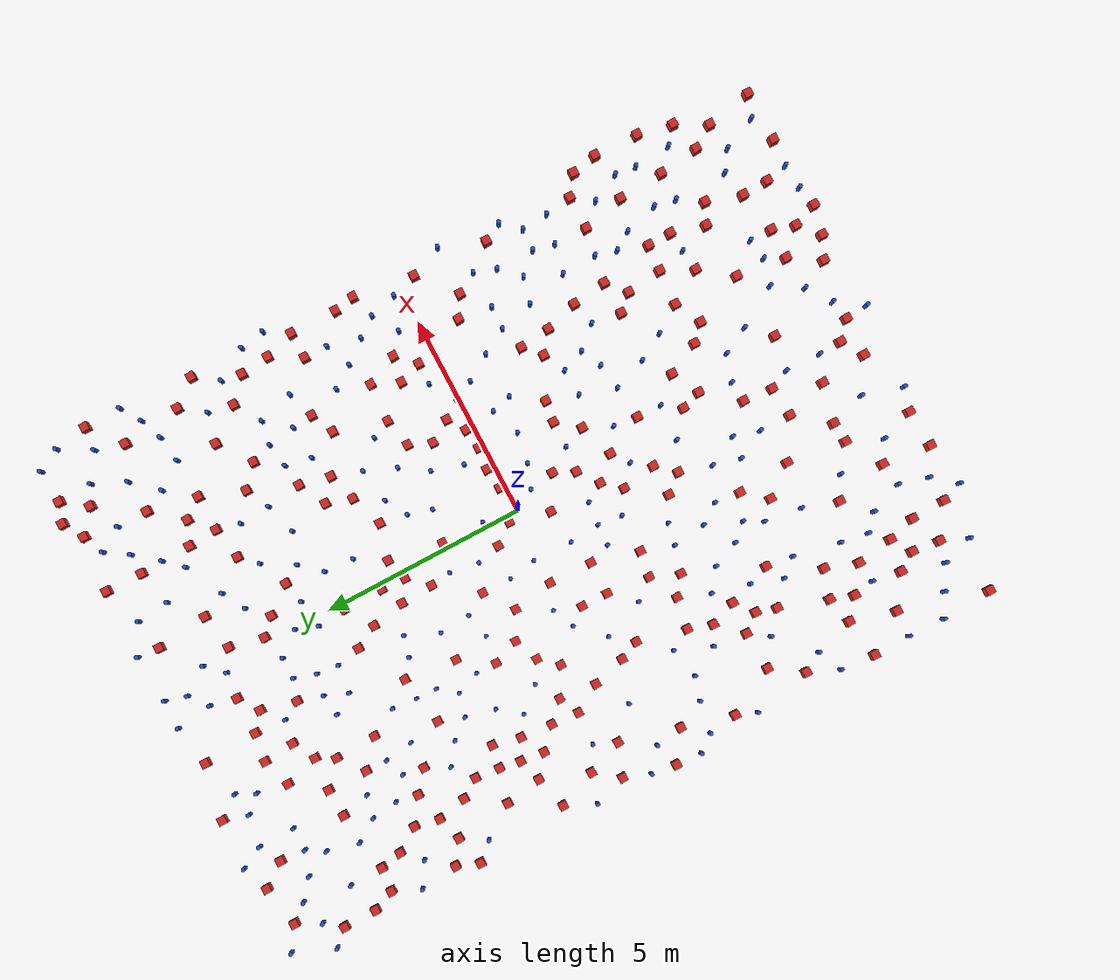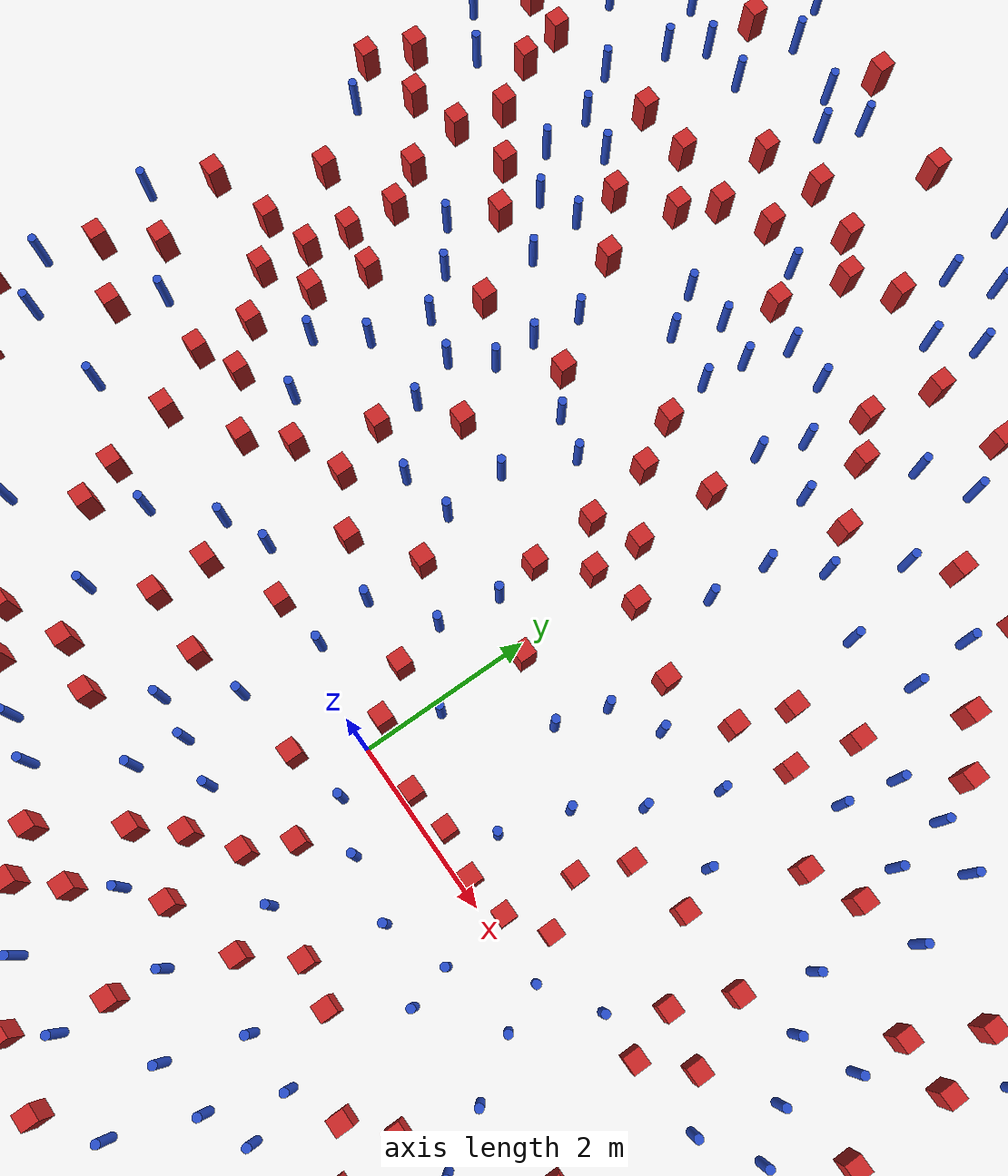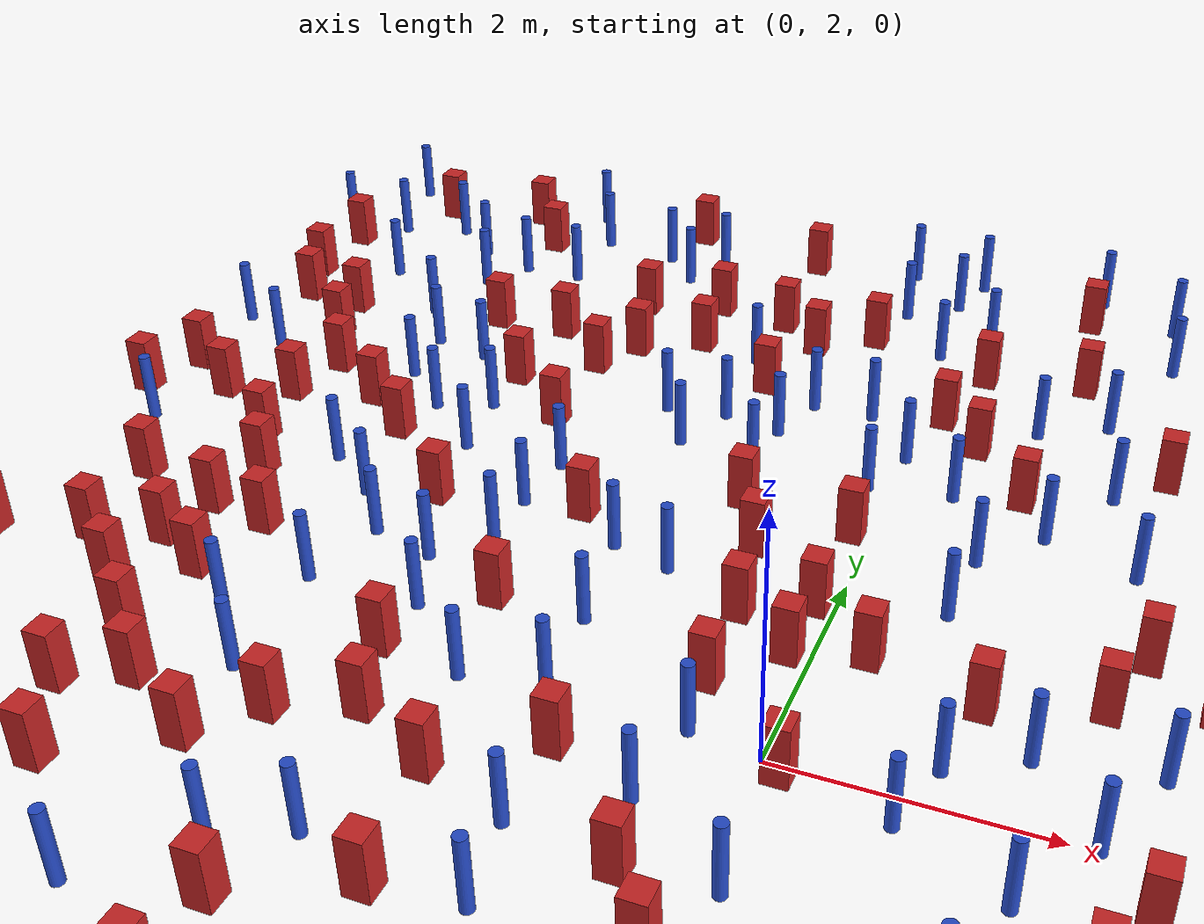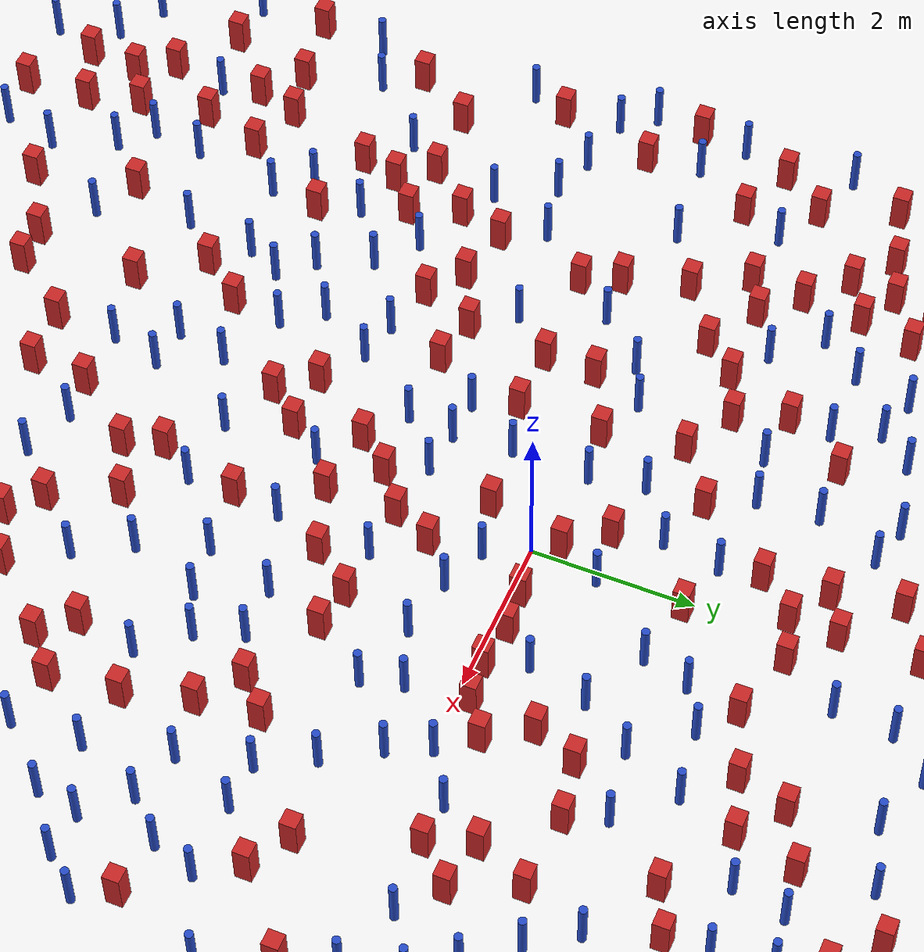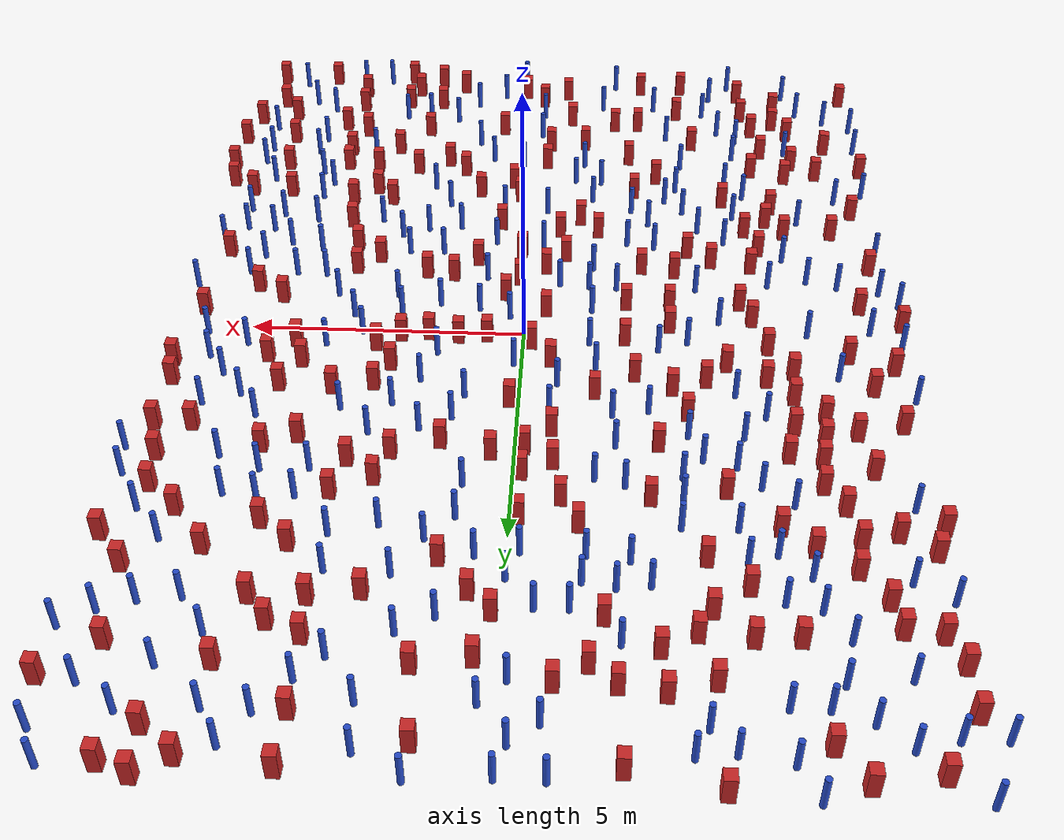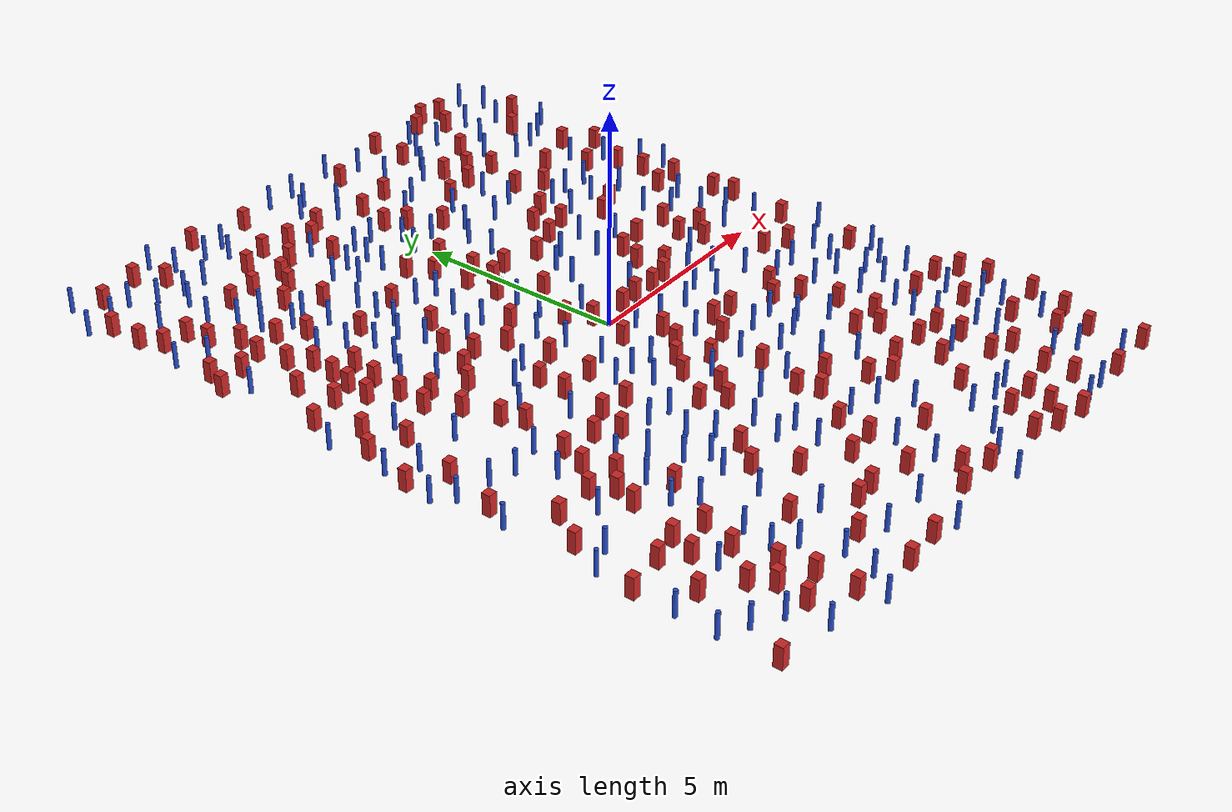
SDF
<sdf version="1.6">
  <model name="dense_58"><model name="square_post_obstacle0">
  <static>true</static>
  <pose frame="">4.03438608395 -5.59124404248 -6.11067671241e-07 -5.50515727128e-06 -8.79689657224e-07 2.37013304536e-05</pose>
  <link name="link">
    <pose frame="">0 0 0.25 0 -0 0</pose>
    <inertial>
      <mass>100</mass>
      <inertia>
        <ixx>0.166667</ixx>
        <ixy>0</ixy>
        <ixz>0</ixz>
        <iyy>0.166667</iyy>
        <iyz>0</iyz>
        <izz>0.166667</izz>
      </inertia>
    </inertial>
    <collision name="collision">
      <geometry>
        <box>
          <size>.2 .2 .5</size>
        </box>
      </geometry>
      <max_contacts>10</max_contacts>
      <surface>
        <contact>
          <ode/>
        </contact>
        <bounce/>
        <friction>
          <torsional>
            <ode/>
          </torsional>
          <ode/>
        </friction>
      </surface>
    </collision>
    <visual name="visual">
      <geometry>
        <box>
          <size>.2 .2 .5</size>
        </box>
      </geometry>
      <material>
        <script>
          <name>Gazebo/Red</name>
          <uri>file://media/materials/scripts/gazebo.material</uri>
        </script>
      </material>
    </visual>
    <self_collide>0</self_collide>
    <kinematic>0</kinematic>
  </link>
</model>
<model name="square_post_obstacle1">
  <static>true</static>
  <pose frame="">-6.2170772033 -0.961407321698 -6.11067671241e-07 -5.50515727128e-06 -8.79689657224e-07 2.37013304536e-05</pose>
  <link name="link">
    <pose frame="">0 0 0.25 0 -0 0</pose>
    <inertial>
      <mass>100</mass>
      <inertia>
        <ixx>0.166667</ixx>
        <ixy>0</ixy>
        <ixz>0</ixz>
        <iyy>0.166667</iyy>
        <iyz>0</iyz>
        <izz>0.166667</izz>
      </inertia>
    </inertial>
    <collision name="collision">
      <geometry>
        <box>
          <size>.2 .2 .5</size>
        </box>
      </geometry>
      <max_contacts>10</max_contacts>
      <surface>
        <contact>
          <ode/>
        </contact>
        <bounce/>
        <friction>
          <torsional>
            <ode/>
          </torsional>
          <ode/>
        </friction>
      </surface>
    </collision>
    <visual name="visual">
      <geometry>
        <box>
          <size>.2 .2 .5</size>
        </box>
      </geometry>
      <material>
        <script>
          <name>Gazebo/Red</name>
          <uri>file://media/materials/scripts/gazebo.material</uri>
        </script>
      </material>
    </visual>
    <self_collide>0</self_collide>
    <kinematic>0</kinematic>
  </link>
</model>
<model name="pole_obstacle0">
  <static>true</static>
  <pose frame="">5.19741799628 8.48322336086 -9.47619616065e-06 5.49618799737e-07 2.36310414065e-07 -1.55090534796e-07</pose>
  <link name="link">
  <pose frame="">0 0 0.3 0 -0 0</pose>
    <inertial>
      <mass>1</mass>
      <inertia>
        <ixx>0.145833</ixx>
        <ixy>0</ixy>
        <ixz>0</ixz>
        <iyy>0.145833</iyy>
        <iyz>0</iyz>
        <izz>0.125</izz>
      </inertia>
    </inertial>
    <collision name="collision">
      <geometry>
        <cylinder>
          <radius>0.05</radius>
          <length>.6</length>
        </cylinder>
      </geometry>
      <max_contacts>10</max_contacts>
      <surface>
        <contact>
          <ode/>
        </contact>
        <bounce/>
        <friction>
          <torsional>
            <ode/>
          </torsional>
          <ode/>
        </friction>
      </surface>
    </collision>
    <visual name="visual">
      <geometry>
        <cylinder>
          <radius>0.05</radius>
          <length>.6</length>
        </cylinder>
      </geometry>
      <material>
        <script>
          <name>Gazebo/Blue</name>
          <uri>file://media/materials/scripts/gazebo.material</uri>
        </script>
      </material>
    </visual>
    <self_collide>0</self_collide>
    <kinematic>0</kinematic>
  </link>
</model>
<model name="square_post_obstacle2">
  <static>true</static>
  <pose frame="">0.156342930012 -2.51117832905 -6.11067671241e-07 -5.50515727128e-06 -8.79689657224e-07 2.37013304536e-05</pose>
  <link name="link">
    <pose frame="">0 0 0.25 0 -0 0</pose>
    <inertial>
      <mass>100</mass>
      <inertia>
        <ixx>0.166667</ixx>
        <ixy>0</ixy>
        <ixz>0</ixz>
        <iyy>0.166667</iyy>
        <iyz>0</iyz>
        <izz>0.166667</izz>
      </inertia>
    </inertial>
    <collision name="collision">
      <geometry>
        <box>
          <size>.2 .2 .5</size>
        </box>
      </geometry>
      <max_contacts>10</max_contacts>
      <surface>
        <contact>
          <ode/>
        </contact>
        <bounce/>
        <friction>
          <torsional>
            <ode/>
          </torsional>
          <ode/>
        </friction>
      </surface>
    </collision>
    <visual name="visual">
      <geometry>
        <box>
          <size>.2 .2 .5</size>
        </box>
      </geometry>
      <material>
        <script>
          <name>Gazebo/Red</name>
          <uri>file://media/materials/scripts/gazebo.material</uri>
        </script>
      </material>
    </visual>
    <self_collide>0</self_collide>
    <kinematic>0</kinematic>
  </link>
</model>
<model name="pole_obstacle1">
  <static>true</static>
  <pose frame="">-0.284534505125 -4.02953136644 -9.47619616065e-06 5.49618799737e-07 2.36310414071e-07 -1.55090534793e-07</pose>
  <link name="link">
  <pose frame="">0 0 0.3 0 -0 0</pose>
    <inertial>
      <mass>1</mass>
      <inertia>
        <ixx>0.145833</ixx>
        <ixy>0</ixy>
        <ixz>0</ixz>
        <iyy>0.145833</iyy>
        <iyz>0</iyz>
        <izz>0.125</izz>
      </inertia>
    </inertial>
    <collision name="collision">
      <geometry>
        <cylinder>
          <radius>0.05</radius>
          <length>.6</length>
        </cylinder>
      </geometry>
      <max_contacts>10</max_contacts>
      <surface>
        <contact>
          <ode/>
        </contact>
        <bounce/>
        <friction>
          <torsional>
            <ode/>
          </torsional>
          <ode/>
        </friction>
      </surface>
    </collision>
    <visual name="visual">
      <geometry>
        <cylinder>
          <radius>0.05</radius>
          <length>.6</length>
        </cylinder>
      </geometry>
      <material>
        <script>
          <name>Gazebo/Blue</name>
          <uri>file://media/materials/scripts/gazebo.material</uri>
        </script>
      </material>
    </visual>
    <self_collide>0</self_collide>
    <kinematic>0</kinematic>
  </link>
</model>
<model name="square_post_obstacle3">
  <static>true</static>
  <pose frame="">-5.07820106895 3.18135762716 -6.11067671241e-07 -5.50515727128e-06 -8.79689657224e-07 2.37013304536e-05</pose>
  <link name="link">
    <pose frame="">0 0 0.25 0 -0 0</pose>
    <inertial>
      <mass>100</mass>
      <inertia>
        <ixx>0.166667</ixx>
        <ixy>0</ixy>
        <ixz>0</ixz>
        <iyy>0.166667</iyy>
        <iyz>0</iyz>
        <izz>0.166667</izz>
      </inertia>
    </inertial>
    <collision name="collision">
      <geometry>
        <box>
          <size>.2 .2 .5</size>
        </box>
      </geometry>
      <max_contacts>10</max_contacts>
      <surface>
        <contact>
          <ode/>
        </contact>
        <bounce/>
        <friction>
          <torsional>
            <ode/>
          </torsional>
          <ode/>
        </friction>
      </surface>
    </collision>
    <visual name="visual">
      <geometry>
        <box>
          <size>.2 .2 .5</size>
        </box>
      </geometry>
      <material>
        <script>
          <name>Gazebo/Red</name>
          <uri>file://media/materials/scripts/gazebo.material</uri>
        </script>
      </material>
    </visual>
    <self_collide>0</self_collide>
    <kinematic>0</kinematic>
  </link>
</model>
<model name="pole_obstacle2">
  <static>true</static>
  <pose frame="">2.30330990491 -0.570750876402 -9.47619616065e-06 5.49618799738e-07 2.36310414075e-07 -1.55090534793e-07</pose>
  <link name="link">
  <pose frame="">0 0 0.3 0 -0 0</pose>
    <inertial>
      <mass>1</mass>
      <inertia>
        <ixx>0.145833</ixx>
        <ixy>0</ixy>
        <ixz>0</ixz>
        <iyy>0.145833</iyy>
        <iyz>0</iyz>
        <izz>0.125</izz>
      </inertia>
    </inertial>
    <collision name="collision">
      <geometry>
        <cylinder>
          <radius>0.05</radius>
          <length>.6</length>
        </cylinder>
      </geometry>
      <max_contacts>10</max_contacts>
      <surface>
        <contact>
          <ode/>
        </contact>
        <bounce/>
        <friction>
          <torsional>
            <ode/>
          </torsional>
          <ode/>
        </friction>
      </surface>
    </collision>
    <visual name="visual">
      <geometry>
        <cylinder>
          <radius>0.05</radius>
          <length>.6</length>
        </cylinder>
      </geometry>
      <material>
        <script>
          <name>Gazebo/Blue</name>
          <uri>file://media/materials/scripts/gazebo.material</uri>
        </script>
      </material>
    </visual>
    <self_collide>0</self_collide>
    <kinematic>0</kinematic>
  </link>
</model>
<model name="pole_obstacle3">
  <static>true</static>
  <pose frame="">-5.60462151577 1.01709262523 -9.47619616065e-06 5.49618799737e-07 2.36310414071e-07 -1.55090534795e-07</pose>
  <link name="link">
  <pose frame="">0 0 0.3 0 -0 0</pose>
    <inertial>
      <mass>1</mass>
      <inertia>
        <ixx>0.145833</ixx>
        <ixy>0</ixy>
        <ixz>0</ixz>
        <iyy>0.145833</iyy>
        <iyz>0</iyz>
        <izz>0.125</izz>
      </inertia>
    </inertial>
    <collision name="collision">
      <geometry>
        <cylinder>
          <radius>0.05</radius>
          <length>.6</length>
        </cylinder>
      </geometry>
      <max_contacts>10</max_contacts>
      <surface>
        <contact>
          <ode/>
        </contact>
        <bounce/>
        <friction>
          <torsional>
            <ode/>
          </torsional>
          <ode/>
        </friction>
      </surface>
    </collision>
    <visual name="visual">
      <geometry>
        <cylinder>
          <radius>0.05</radius>
          <length>.6</length>
        </cylinder>
      </geometry>
      <material>
        <script>
          <name>Gazebo/Blue</name>
          <uri>file://media/materials/scripts/gazebo.material</uri>
        </script>
      </material>
    </visual>
    <self_collide>0</self_collide>
    <kinematic>0</kinematic>
  </link>
</model>
<model name="square_post_obstacle4">
  <static>true</static>
  <pose frame="">-4.4408581253 -8.84156580716 -6.11067671241e-07 -5.50515727128e-06 -8.79689657224e-07 2.37013304536e-05</pose>
  <link name="link">
    <pose frame="">0 0 0.25 0 -0 0</pose>
    <inertial>
      <mass>100</mass>
      <inertia>
        <ixx>0.166667</ixx>
        <ixy>0</ixy>
        <ixz>0</ixz>
        <iyy>0.166667</iyy>
        <iyz>0</iyz>
        <izz>0.166667</izz>
      </inertia>
    </inertial>
    <collision name="collision">
      <geometry>
        <box>
          <size>.2 .2 .5</size>
        </box>
      </geometry>
      <max_contacts>10</max_contacts>
      <surface>
        <contact>
          <ode/>
        </contact>
        <bounce/>
        <friction>
          <torsional>
            <ode/>
          </torsional>
          <ode/>
        </friction>
      </surface>
    </collision>
    <visual name="visual">
      <geometry>
        <box>
          <size>.2 .2 .5</size>
        </box>
      </geometry>
      <material>
        <script>
          <name>Gazebo/Red</name>
          <uri>file://media/materials/scripts/gazebo.material</uri>
        </script>
      </material>
    </visual>
    <self_collide>0</self_collide>
    <kinematic>0</kinematic>
  </link>
</model>
<model name="square_post_obstacle5">
  <static>true</static>
  <pose frame="">-3.98409590018 -0.982114767462 -6.11067671241e-07 -5.50515727128e-06 -8.79689657224e-07 2.37013304536e-05</pose>
  <link name="link">
    <pose frame="">0 0 0.25 0 -0 0</pose>
    <inertial>
      <mass>100</mass>
      <inertia>
        <ixx>0.166667</ixx>
        <ixy>0</ixy>
        <ixz>0</ixz>
        <iyy>0.166667</iyy>
        <iyz>0</iyz>
        <izz>0.166667</izz>
      </inertia>
    </inertial>
    <collision name="collision">
      <geometry>
        <box>
          <size>.2 .2 .5</size>
        </box>
      </geometry>
      <max_contacts>10</max_contacts>
      <surface>
        <contact>
          <ode/>
        </contact>
        <bounce/>
        <friction>
          <torsional>
            <ode/>
          </torsional>
          <ode/>
        </friction>
      </surface>
    </collision>
    <visual name="visual">
      <geometry>
        <box>
          <size>.2 .2 .5</size>
        </box>
      </geometry>
      <material>
        <script>
          <name>Gazebo/Red</name>
          <uri>file://media/materials/scripts/gazebo.material</uri>
        </script>
      </material>
    </visual>
    <self_collide>0</self_collide>
    <kinematic>0</kinematic>
  </link>
</model>
<model name="square_post_obstacle6">
  <static>true</static>
  <pose frame="">-2.23909041218 4.15770622929 -6.11067671241e-07 -5.50515727128e-06 -8.79689657224e-07 2.37013304536e-05</pose>
  <link name="link">
    <pose frame="">0 0 0.25 0 -0 0</pose>
    <inertial>
      <mass>100</mass>
      <inertia>
        <ixx>0.166667</ixx>
        <ixy>0</ixy>
        <ixz>0</ixz>
        <iyy>0.166667</iyy>
        <iyz>0</iyz>
        <izz>0.166667</izz>
      </inertia>
    </inertial>
    <collision name="collision">
      <geometry>
        <box>
          <size>.2 .2 .5</size>
        </box>
      </geometry>
      <max_contacts>10</max_contacts>
      <surface>
        <contact>
          <ode/>
        </contact>
        <bounce/>
        <friction>
          <torsional>
            <ode/>
          </torsional>
          <ode/>
        </friction>
      </surface>
    </collision>
    <visual name="visual">
      <geometry>
        <box>
          <size>.2 .2 .5</size>
        </box>
      </geometry>
      <material>
        <script>
          <name>Gazebo/Red</name>
          <uri>file://media/materials/scripts/gazebo.material</uri>
        </script>
      </material>
    </visual>
    <self_collide>0</self_collide>
    <kinematic>0</kinematic>
  </link>
</model>
<model name="pole_obstacle4">
  <static>true</static>
  <pose frame="">4.62775568484 4.29187557403 -9.47619616065e-06 5.49618799737e-07 2.36310414037e-07 -1.55090534814e-07</pose>
  <link name="link">
  <pose frame="">0 0 0.3 0 -0 0</pose>
    <inertial>
      <mass>1</mass>
      <inertia>
        <ixx>0.145833</ixx>
        <ixy>0</ixy>
        <ixz>0</ixz>
        <iyy>0.145833</iyy>
        <iyz>0</iyz>
        <izz>0.125</izz>
      </inertia>
    </inertial>
    <collision name="collision">
      <geometry>
        <cylinder>
          <radius>0.05</radius>
          <length>.6</length>
        </cylinder>
      </geometry>
      <max_contacts>10</max_contacts>
      <surface>
        <contact>
          <ode/>
        </contact>
        <bounce/>
        <friction>
          <torsional>
            <ode/>
          </torsional>
          <ode/>
        </friction>
      </surface>
    </collision>
    <visual name="visual">
      <geometry>
        <cylinder>
          <radius>0.05</radius>
          <length>.6</length>
        </cylinder>
      </geometry>
      <material>
        <script>
          <name>Gazebo/Blue</name>
          <uri>file://media/materials/scripts/gazebo.material</uri>
        </script>
      </material>
    </visual>
    <self_collide>0</self_collide>
    <kinematic>0</kinematic>
  </link>
</model>
<model name="pole_obstacle5">
  <static>true</static>
  <pose frame="">-4.5283102486 4.16066670796 -9.47619616065e-06 5.49618799737e-07 2.36310414037e-07 -1.55090534814e-07</pose>
  <link name="link">
  <pose frame="">0 0 0.3 0 -0 0</pose>
    <inertial>
      <mass>1</mass>
      <inertia>
        <ixx>0.145833</ixx>
        <ixy>0</ixy>
        <ixz>0</ixz>
        <iyy>0.145833</iyy>
        <iyz>0</iyz>
        <izz>0.125</izz>
      </inertia>
    </inertial>
    <collision name="collision">
      <geometry>
        <cylinder>
          <radius>0.05</radius>
          <length>.6</length>
        </cylinder>
      </geometry>
      <max_contacts>10</max_contacts>
      <surface>
        <contact>
          <ode/>
        </contact>
        <bounce/>
        <friction>
          <torsional>
            <ode/>
          </torsional>
          <ode/>
        </friction>
      </surface>
    </collision>
    <visual name="visual">
      <geometry>
        <cylinder>
          <radius>0.05</radius>
          <length>.6</length>
        </cylinder>
      </geometry>
      <material>
        <script>
          <name>Gazebo/Blue</name>
          <uri>file://media/materials/scripts/gazebo.material</uri>
        </script>
      </material>
    </visual>
    <self_collide>0</self_collide>
    <kinematic>0</kinematic>
  </link>
</model>
<model name="square_post_obstacle7">
  <static>true</static>
  <pose frame="">2.09273020799 6.26448453688 -6.11067671241e-07 -5.50515727128e-06 -8.79689657224e-07 2.37013304536e-05</pose>
  <link name="link">
    <pose frame="">0 0 0.25 0 -0 0</pose>
    <inertial>
      <mass>100</mass>
      <inertia>
        <ixx>0.166667</ixx>
        <ixy>0</ixy>
        <ixz>0</ixz>
        <iyy>0.166667</iyy>
        <iyz>0</iyz>
        <izz>0.166667</izz>
      </inertia>
    </inertial>
    <collision name="collision">
      <geometry>
        <box>
          <size>.2 .2 .5</size>
        </box>
      </geometry>
      <max_contacts>10</max_contacts>
      <surface>
        <contact>
          <ode/>
        </contact>
        <bounce/>
        <friction>
          <torsional>
            <ode/>
          </torsional>
          <ode/>
        </friction>
      </surface>
    </collision>
    <visual name="visual">
      <geometry>
        <box>
          <size>.2 .2 .5</size>
        </box>
      </geometry>
      <material>
        <script>
          <name>Gazebo/Red</name>
          <uri>file://media/materials/scripts/gazebo.material</uri>
        </script>
      </material>
    </visual>
    <self_collide>0</self_collide>
    <kinematic>0</kinematic>
  </link>
</model>
<model name="square_post_obstacle8">
  <static>true</static>
  <pose frame="">4.19859094494 1.65276408117 -6.11067671241e-07 -5.50515727128e-06 -8.79689657224e-07 2.37013304536e-05</pose>
  <link name="link">
    <pose frame="">0 0 0.25 0 -0 0</pose>
    <inertial>
      <mass>100</mass>
      <inertia>
        <ixx>0.166667</ixx>
        <ixy>0</ixy>
        <ixz>0</ixz>
        <iyy>0.166667</iyy>
        <iyz>0</iyz>
        <izz>0.166667</izz>
      </inertia>
    </inertial>
    <collision name="collision">
      <geometry>
        <box>
          <size>.2 .2 .5</size>
        </box>
      </geometry>
      <max_contacts>10</max_contacts>
      <surface>
        <contact>
          <ode/>
        </contact>
        <bounce/>
        <friction>
          <torsional>
            <ode/>
          </torsional>
          <ode/>
        </friction>
      </surface>
    </collision>
    <visual name="visual">
      <geometry>
        <box>
          <size>.2 .2 .5</size>
        </box>
      </geometry>
      <material>
        <script>
          <name>Gazebo/Red</name>
          <uri>file://media/materials/scripts/gazebo.material</uri>
        </script>
      </material>
    </visual>
    <self_collide>0</self_collide>
    <kinematic>0</kinematic>
  </link>
</model>
<model name="pole_obstacle6">
  <static>true</static>
  <pose frame="">-2.67955490322 -4.49456968489 -9.47619616065e-06 5.49618799738e-07 2.3631041406e-07 -1.55090534801e-07</pose>
  <link name="link">
  <pose frame="">0 0 0.3 0 -0 0</pose>
    <inertial>
      <mass>1</mass>
      <inertia>
        <ixx>0.145833</ixx>
        <ixy>0</ixy>
        <ixz>0</ixz>
        <iyy>0.145833</iyy>
        <iyz>0</iyz>
        <izz>0.125</izz>
      </inertia>
    </inertial>
    <collision name="collision">
      <geometry>
        <cylinder>
          <radius>0.05</radius>
          <length>.6</length>
        </cylinder>
      </geometry>
      <max_contacts>10</max_contacts>
      <surface>
        <contact>
          <ode/>
        </contact>
        <bounce/>
        <friction>
          <torsional>
            <ode/>
          </torsional>
          <ode/>
        </friction>
      </surface>
    </collision>
    <visual name="visual">
      <geometry>
        <cylinder>
          <radius>0.05</radius>
          <length>.6</length>
        </cylinder>
      </geometry>
      <material>
        <script>
          <name>Gazebo/Blue</name>
          <uri>file://media/materials/scripts/gazebo.material</uri>
        </script>
      </material>
    </visual>
    <self_collide>0</self_collide>
    <kinematic>0</kinematic>
  </link>
</model>
<model name="pole_obstacle7">
  <static>true</static>
  <pose frame="">5.74011570773 -3.17325462486 -9.47619616065e-06 5.49618799738e-07 2.36310414051e-07 -1.55090534805e-07</pose>
  <link name="link">
  <pose frame="">0 0 0.3 0 -0 0</pose>
    <inertial>
      <mass>1</mass>
      <inertia>
        <ixx>0.145833</ixx>
        <ixy>0</ixy>
        <ixz>0</ixz>
        <iyy>0.145833</iyy>
        <iyz>0</iyz>
        <izz>0.125</izz>
      </inertia>
    </inertial>
    <collision name="collision">
      <geometry>
        <cylinder>
          <radius>0.05</radius>
          <length>.6</length>
        </cylinder>
      </geometry>
      <max_contacts>10</max_contacts>
      <surface>
        <contact>
          <ode/>
        </contact>
        <bounce/>
        <friction>
          <torsional>
            <ode/>
          </torsional>
          <ode/>
        </friction>
      </surface>
    </collision>
    <visual name="visual">
      <geometry>
        <cylinder>
          <radius>0.05</radius>
          <length>.6</length>
        </cylinder>
      </geometry>
      <material>
        <script>
          <name>Gazebo/Blue</name>
          <uri>file://media/materials/scripts/gazebo.material</uri>
        </script>
      </material>
    </visual>
    <self_collide>0</self_collide>
    <kinematic>0</kinematic>
  </link>
</model>
<model name="square_post_obstacle9">
  <static>true</static>
  <pose frame="">-3.10520400773 7.67391111457 -6.11067671241e-07 -5.50515727128e-06 -8.79689657224e-07 2.37013304536e-05</pose>
  <link name="link">
    <pose frame="">0 0 0.25 0 -0 0</pose>
    <inertial>
      <mass>100</mass>
      <inertia>
        <ixx>0.166667</ixx>
        <ixy>0</ixy>
        <ixz>0</ixz>
        <iyy>0.166667</iyy>
        <iyz>0</iyz>
        <izz>0.166667</izz>
      </inertia>
    </inertial>
    <collision name="collision">
      <geometry>
        <box>
          <size>.2 .2 .5</size>
        </box>
      </geometry>
      <max_contacts>10</max_contacts>
      <surface>
        <contact>
          <ode/>
        </contact>
        <bounce/>
        <friction>
          <torsional>
            <ode/>
          </torsional>
          <ode/>
        </friction>
      </surface>
    </collision>
    <visual name="visual">
      <geometry>
        <box>
          <size>.2 .2 .5</size>
        </box>
      </geometry>
      <material>
        <script>
          <name>Gazebo/Red</name>
          <uri>file://media/materials/scripts/gazebo.material</uri>
        </script>
      </material>
    </visual>
    <self_collide>0</self_collide>
    <kinematic>0</kinematic>
  </link>
</model>
<model name="square_post_obstacle10">
  <static>true</static>
  <pose frame="">4.5871182132 -0.866815643466 -6.11067671241e-07 -5.50515727128e-06 -8.79689657224e-07 2.37013304536e-05</pose>
  <link name="link">
    <pose frame="">0 0 0.25 0 -0 0</pose>
    <inertial>
      <mass>100</mass>
      <inertia>
        <ixx>0.166667</ixx>
        <ixy>0</ixy>
        <ixz>0</ixz>
        <iyy>0.166667</iyy>
        <iyz>0</iyz>
        <izz>0.166667</izz>
      </inertia>
    </inertial>
    <collision name="collision">
      <geometry>
        <box>
          <size>.2 .2 .5</size>
        </box>
      </geometry>
      <max_contacts>10</max_contacts>
      <surface>
        <contact>
          <ode/>
        </contact>
        <bounce/>
        <friction>
          <torsional>
            <ode/>
          </torsional>
          <ode/>
        </friction>
      </surface>
    </collision>
    <visual name="visual">
      <geometry>
        <box>
          <size>.2 .2 .5</size>
        </box>
      </geometry>
      <material>
        <script>
          <name>Gazebo/Red</name>
          <uri>file://media/materials/scripts/gazebo.material</uri>
        </script>
      </material>
    </visual>
    <self_collide>0</self_collide>
    <kinematic>0</kinematic>
  </link>
</model>
<model name="square_post_obstacle11">
  <static>true</static>
  <pose frame="">2.23731947832 3.88143096257 -6.11067671241e-07 -5.50515727128e-06 -8.79689657224e-07 2.37013304536e-05</pose>
  <link name="link">
    <pose frame="">0 0 0.25 0 -0 0</pose>
    <inertial>
      <mass>100</mass>
      <inertia>
        <ixx>0.166667</ixx>
        <ixy>0</ixy>
        <ixz>0</ixz>
        <iyy>0.166667</iyy>
        <iyz>0</iyz>
        <izz>0.166667</izz>
      </inertia>
    </inertial>
    <collision name="collision">
      <geometry>
        <box>
          <size>.2 .2 .5</size>
        </box>
      </geometry>
      <max_contacts>10</max_contacts>
      <surface>
        <contact>
          <ode/>
        </contact>
        <bounce/>
        <friction>
          <torsional>
            <ode/>
          </torsional>
          <ode/>
        </friction>
      </surface>
    </collision>
    <visual name="visual">
      <geometry>
        <box>
          <size>.2 .2 .5</size>
        </box>
      </geometry>
      <material>
        <script>
          <name>Gazebo/Red</name>
          <uri>file://media/materials/scripts/gazebo.material</uri>
        </script>
      </material>
    </visual>
    <self_collide>0</self_collide>
    <kinematic>0</kinematic>
  </link>
</model>
<model name="square_post_obstacle12">
  <static>true</static>
  <pose frame="">-4.59357424023 8.65505979291 -6.11067671241e-07 -5.50515727128e-06 -8.79689657224e-07 2.37013304536e-05</pose>
  <link name="link">
    <pose frame="">0 0 0.25 0 -0 0</pose>
    <inertial>
      <mass>100</mass>
      <inertia>
        <ixx>0.166667</ixx>
        <ixy>0</ixy>
        <ixz>0</ixz>
        <iyy>0.166667</iyy>
        <iyz>0</iyz>
        <izz>0.166667</izz>
      </inertia>
    </inertial>
    <collision name="collision">
      <geometry>
        <box>
          <size>.2 .2 .5</size>
        </box>
      </geometry>
      <max_contacts>10</max_contacts>
      <surface>
        <contact>
          <ode/>
        </contact>
        <bounce/>
        <friction>
          <torsional>
            <ode/>
          </torsional>
          <ode/>
        </friction>
      </surface>
    </collision>
    <visual name="visual">
      <geometry>
        <box>
          <size>.2 .2 .5</size>
        </box>
      </geometry>
      <material>
        <script>
          <name>Gazebo/Red</name>
          <uri>file://media/materials/scripts/gazebo.material</uri>
        </script>
      </material>
    </visual>
    <self_collide>0</self_collide>
    <kinematic>0</kinematic>
  </link>
</model>
<model name="square_post_obstacle13">
  <static>true</static>
  <pose frame="">2.83978793592 -8.85130759816 -6.11067671241e-07 -5.50515727128e-06 -8.79689657224e-07 2.37013304536e-05</pose>
  <link name="link">
    <pose frame="">0 0 0.25 0 -0 0</pose>
    <inertial>
      <mass>100</mass>
      <inertia>
        <ixx>0.166667</ixx>
        <ixy>0</ixy>
        <ixz>0</ixz>
        <iyy>0.166667</iyy>
        <iyz>0</iyz>
        <izz>0.166667</izz>
      </inertia>
    </inertial>
    <collision name="collision">
      <geometry>
        <box>
          <size>.2 .2 .5</size>
        </box>
      </geometry>
      <max_contacts>10</max_contacts>
      <surface>
        <contact>
          <ode/>
        </contact>
        <bounce/>
        <friction>
          <torsional>
            <ode/>
          </torsional>
          <ode/>
        </friction>
      </surface>
    </collision>
    <visual name="visual">
      <geometry>
        <box>
          <size>.2 .2 .5</size>
        </box>
      </geometry>
      <material>
        <script>
          <name>Gazebo/Red</name>
          <uri>file://media/materials/scripts/gazebo.material</uri>
        </script>
      </material>
    </visual>
    <self_collide>0</self_collide>
    <kinematic>0</kinematic>
  </link>
</model>
<model name="pole_obstacle8">
  <static>true</static>
  <pose frame="">0.598691550622 -4.07649091872 -9.47619616065e-06 5.49618799737e-07 2.36310414065e-07 -1.55090534796e-07</pose>
  <link name="link">
  <pose frame="">0 0 0.3 0 -0 0</pose>
    <inertial>
      <mass>1</mass>
      <inertia>
        <ixx>0.145833</ixx>
        <ixy>0</ixy>
        <ixz>0</ixz>
        <iyy>0.145833</iyy>
        <iyz>0</iyz>
        <izz>0.125</izz>
      </inertia>
    </inertial>
    <collision name="collision">
      <geometry>
        <cylinder>
          <radius>0.05</radius>
          <length>.6</length>
        </cylinder>
      </geometry>
      <max_contacts>10</max_contacts>
      <surface>
        <contact>
          <ode/>
        </contact>
        <bounce/>
        <friction>
          <torsional>
            <ode/>
          </torsional>
          <ode/>
        </friction>
      </surface>
    </collision>
    <visual name="visual">
      <geometry>
        <cylinder>
          <radius>0.05</radius>
          <length>.6</length>
        </cylinder>
      </geometry>
      <material>
        <script>
          <name>Gazebo/Blue</name>
          <uri>file://media/materials/scripts/gazebo.material</uri>
        </script>
      </material>
    </visual>
    <self_collide>0</self_collide>
    <kinematic>0</kinematic>
  </link>
</model>
<model name="square_post_obstacle14">
  <static>true</static>
  <pose frame="">-5.88535612797 -5.571079546 -6.11067671241e-07 -5.50515727128e-06 -8.79689657224e-07 2.37013304536e-05</pose>
  <link name="link">
    <pose frame="">0 0 0.25 0 -0 0</pose>
    <inertial>
      <mass>100</mass>
      <inertia>
        <ixx>0.166667</ixx>
        <ixy>0</ixy>
        <ixz>0</ixz>
        <iyy>0.166667</iyy>
        <iyz>0</iyz>
        <izz>0.166667</izz>
      </inertia>
    </inertial>
    <collision name="collision">
      <geometry>
        <box>
          <size>.2 .2 .5</size>
        </box>
      </geometry>
      <max_contacts>10</max_contacts>
      <surface>
        <contact>
          <ode/>
        </contact>
        <bounce/>
        <friction>
          <torsional>
            <ode/>
          </torsional>
          <ode/>
        </friction>
      </surface>
    </collision>
    <visual name="visual">
      <geometry>
        <box>
          <size>.2 .2 .5</size>
        </box>
      </geometry>
      <material>
        <script>
          <name>Gazebo/Red</name>
          <uri>file://media/materials/scripts/gazebo.material</uri>
        </script>
      </material>
    </visual>
    <self_collide>0</self_collide>
    <kinematic>0</kinematic>
  </link>
</model>
<model name="square_post_obstacle15">
  <static>true</static>
  <pose frame="">2.31770672173 1.00862189128 -6.11067671241e-07 -5.50515727128e-06 -8.79689657224e-07 2.37013304536e-05</pose>
  <link name="link">
    <pose frame="">0 0 0.25 0 -0 0</pose>
    <inertial>
      <mass>100</mass>
      <inertia>
        <ixx>0.166667</ixx>
        <ixy>0</ixy>
        <ixz>0</ixz>
        <iyy>0.166667</iyy>
        <iyz>0</iyz>
        <izz>0.166667</izz>
      </inertia>
    </inertial>
    <collision name="collision">
      <geometry>
        <box>
          <size>.2 .2 .5</size>
        </box>
      </geometry>
      <max_contacts>10</max_contacts>
      <surface>
        <contact>
          <ode/>
        </contact>
        <bounce/>
        <friction>
          <torsional>
            <ode/>
          </torsional>
          <ode/>
        </friction>
      </surface>
    </collision>
    <visual name="visual">
      <geometry>
        <box>
          <size>.2 .2 .5</size>
        </box>
      </geometry>
      <material>
        <script>
          <name>Gazebo/Red</name>
          <uri>file://media/materials/scripts/gazebo.material</uri>
        </script>
      </material>
    </visual>
    <self_collide>0</self_collide>
    <kinematic>0</kinematic>
  </link>
</model>
<model name="square_post_obstacle16">
  <static>true</static>
  <pose frame="">-4.52722977021 -5.63745665215 -6.11067671241e-07 -5.50515727128e-06 -8.79689657224e-07 2.37013304536e-05</pose>
  <link name="link">
    <pose frame="">0 0 0.25 0 -0 0</pose>
    <inertial>
      <mass>100</mass>
      <inertia>
        <ixx>0.166667</ixx>
        <ixy>0</ixy>
        <ixz>0</ixz>
        <iyy>0.166667</iyy>
        <iyz>0</iyz>
        <izz>0.166667</izz>
      </inertia>
    </inertial>
    <collision name="collision">
      <geometry>
        <box>
          <size>.2 .2 .5</size>
        </box>
      </geometry>
      <max_contacts>10</max_contacts>
      <surface>
        <contact>
          <ode/>
        </contact>
        <bounce/>
        <friction>
          <torsional>
            <ode/>
          </torsional>
          <ode/>
        </friction>
      </surface>
    </collision>
    <visual name="visual">
      <geometry>
        <box>
          <size>.2 .2 .5</size>
        </box>
      </geometry>
      <material>
        <script>
          <name>Gazebo/Red</name>
          <uri>file://media/materials/scripts/gazebo.material</uri>
        </script>
      </material>
    </visual>
    <self_collide>0</self_collide>
    <kinematic>0</kinematic>
  </link>
</model>
<model name="pole_obstacle9">
  <static>true</static>
  <pose frame="">4.77885601675 -6.13484441956 -9.47619616065e-06 5.49618799737e-07 2.36310414037e-07 -1.55090534814e-07</pose>
  <link name="link">
  <pose frame="">0 0 0.3 0 -0 0</pose>
    <inertial>
      <mass>1</mass>
      <inertia>
        <ixx>0.145833</ixx>
        <ixy>0</ixy>
        <ixz>0</ixz>
        <iyy>0.145833</iyy>
        <iyz>0</iyz>
        <izz>0.125</izz>
      </inertia>
    </inertial>
    <collision name="collision">
      <geometry>
        <cylinder>
          <radius>0.05</radius>
          <length>.6</length>
        </cylinder>
      </geometry>
      <max_contacts>10</max_contacts>
      <surface>
        <contact>
          <ode/>
        </contact>
        <bounce/>
        <friction>
          <torsional>
            <ode/>
          </torsional>
          <ode/>
        </friction>
      </surface>
    </collision>
    <visual name="visual">
      <geometry>
        <cylinder>
          <radius>0.05</radius>
          <length>.6</length>
        </cylinder>
      </geometry>
      <material>
        <script>
          <name>Gazebo/Blue</name>
          <uri>file://media/materials/scripts/gazebo.material</uri>
        </script>
      </material>
    </visual>
    <self_collide>0</self_collide>
    <kinematic>0</kinematic>
  </link>
</model>
<model name="square_post_obstacle17">
  <static>true</static>
  <pose frame="">-3.10708419288 6.39974846675 -6.11067671241e-07 -5.50515727128e-06 -8.79689657224e-07 2.37013304536e-05</pose>
  <link name="link">
    <pose frame="">0 0 0.25 0 -0 0</pose>
    <inertial>
      <mass>100</mass>
      <inertia>
        <ixx>0.166667</ixx>
        <ixy>0</ixy>
        <ixz>0</ixz>
        <iyy>0.166667</iyy>
        <iyz>0</iyz>
        <izz>0.166667</izz>
      </inertia>
    </inertial>
    <collision name="collision">
      <geometry>
        <box>
          <size>.2 .2 .5</size>
        </box>
      </geometry>
      <max_contacts>10</max_contacts>
      <surface>
        <contact>
          <ode/>
        </contact>
        <bounce/>
        <friction>
          <torsional>
            <ode/>
          </torsional>
          <ode/>
        </friction>
      </surface>
    </collision>
    <visual name="visual">
      <geometry>
        <box>
          <size>.2 .2 .5</size>
        </box>
      </geometry>
      <material>
        <script>
          <name>Gazebo/Red</name>
          <uri>file://media/materials/scripts/gazebo.material</uri>
        </script>
      </material>
    </visual>
    <self_collide>0</self_collide>
    <kinematic>0</kinematic>
  </link>
</model>
<model name="square_post_obstacle18">
  <static>true</static>
  <pose frame="">-3.13976255118 9.4031329805 -6.11067671241e-07 -5.50515727128e-06 -8.79689657224e-07 2.37013304536e-05</pose>
  <link name="link">
    <pose frame="">0 0 0.25 0 -0 0</pose>
    <inertial>
      <mass>100</mass>
      <inertia>
        <ixx>0.166667</ixx>
        <ixy>0</ixy>
        <ixz>0</ixz>
        <iyy>0.166667</iyy>
        <iyz>0</iyz>
        <izz>0.166667</izz>
      </inertia>
    </inertial>
    <collision name="collision">
      <geometry>
        <box>
          <size>.2 .2 .5</size>
        </box>
      </geometry>
      <max_contacts>10</max_contacts>
      <surface>
        <contact>
          <ode/>
        </contact>
        <bounce/>
        <friction>
          <torsional>
            <ode/>
          </torsional>
          <ode/>
        </friction>
      </surface>
    </collision>
    <visual name="visual">
      <geometry>
        <box>
          <size>.2 .2 .5</size>
        </box>
      </geometry>
      <material>
        <script>
          <name>Gazebo/Red</name>
          <uri>file://media/materials/scripts/gazebo.material</uri>
        </script>
      </material>
    </visual>
    <self_collide>0</self_collide>
    <kinematic>0</kinematic>
  </link>
</model>
<model name="pole_obstacle10">
  <static>true</static>
  <pose frame="">-1.33288930093 3.70282514603 -9.47619616065e-06 5.49618799737e-07 2.36310414062e-07 -1.55090534798e-07</pose>
  <link name="link">
  <pose frame="">0 0 0.3 0 -0 0</pose>
    <inertial>
      <mass>1</mass>
      <inertia>
        <ixx>0.145833</ixx>
        <ixy>0</ixy>
        <ixz>0</ixz>
        <iyy>0.145833</iyy>
        <iyz>0</iyz>
        <izz>0.125</izz>
      </inertia>
    </inertial>
    <collision name="collision">
      <geometry>
        <cylinder>
          <radius>0.05</radius>
          <length>.6</length>
        </cylinder>
      </geometry>
      <max_contacts>10</max_contacts>
      <surface>
        <contact>
          <ode/>
        </contact>
        <bounce/>
        <friction>
          <torsional>
            <ode/>
          </torsional>
          <ode/>
        </friction>
      </surface>
    </collision>
    <visual name="visual">
      <geometry>
        <cylinder>
          <radius>0.05</radius>
          <length>.6</length>
        </cylinder>
      </geometry>
      <material>
        <script>
          <name>Gazebo/Blue</name>
          <uri>file://media/materials/scripts/gazebo.material</uri>
        </script>
      </material>
    </visual>
    <self_collide>0</self_collide>
    <kinematic>0</kinematic>
  </link>
</model>
<model name="square_post_obstacle19">
  <static>true</static>
  <pose frame="">3.87518315333 4.90633559516 -6.11067671241e-07 -5.50515727128e-06 -8.79689657224e-07 2.37013304536e-05</pose>
  <link name="link">
    <pose frame="">0 0 0.25 0 -0 0</pose>
    <inertial>
      <mass>100</mass>
      <inertia>
        <ixx>0.166667</ixx>
        <ixy>0</ixy>
        <ixz>0</ixz>
        <iyy>0.166667</iyy>
        <iyz>0</iyz>
        <izz>0.166667</izz>
      </inertia>
    </inertial>
    <collision name="collision">
      <geometry>
        <box>
          <size>.2 .2 .5</size>
        </box>
      </geometry>
      <max_contacts>10</max_contacts>
      <surface>
        <contact>
          <ode/>
        </contact>
        <bounce/>
        <friction>
          <torsional>
            <ode/>
          </torsional>
          <ode/>
        </friction>
      </surface>
    </collision>
    <visual name="visual">
      <geometry>
        <box>
          <size>.2 .2 .5</size>
        </box>
      </geometry>
      <material>
        <script>
          <name>Gazebo/Red</name>
          <uri>file://media/materials/scripts/gazebo.material</uri>
        </script>
      </material>
    </visual>
    <self_collide>0</self_collide>
    <kinematic>0</kinematic>
  </link>
</model>
<model name="pole_obstacle11">
  <static>true</static>
  <pose frame="">-5.68892894225 8.63027807105 -9.47619616065e-06 5.49618799737e-07 2.36310414065e-07 -1.55090534796e-07</pose>
  <link name="link">
  <pose frame="">0 0 0.3 0 -0 0</pose>
    <inertial>
      <mass>1</mass>
      <inertia>
        <ixx>0.145833</ixx>
        <ixy>0</ixy>
        <ixz>0</ixz>
        <iyy>0.145833</iyy>
        <iyz>0</iyz>
        <izz>0.125</izz>
      </inertia>
    </inertial>
    <collision name="collision">
      <geometry>
        <cylinder>
          <radius>0.05</radius>
          <length>.6</length>
        </cylinder>
      </geometry>
      <max_contacts>10</max_contacts>
      <surface>
        <contact>
          <ode/>
        </contact>
        <bounce/>
        <friction>
          <torsional>
            <ode/>
          </torsional>
          <ode/>
        </friction>
      </surface>
    </collision>
    <visual name="visual">
      <geometry>
        <cylinder>
          <radius>0.05</radius>
          <length>.6</length>
        </cylinder>
      </geometry>
      <material>
        <script>
          <name>Gazebo/Blue</name>
          <uri>file://media/materials/scripts/gazebo.material</uri>
        </script>
      </material>
    </visual>
    <self_collide>0</self_collide>
    <kinematic>0</kinematic>
  </link>
</model>
<model name="square_post_obstacle20">
  <static>true</static>
  <pose frame="">-6.16429264056 1.35140668349 -6.11067671241e-07 -5.50515727128e-06 -8.79689657224e-07 2.37013304536e-05</pose>
  <link name="link">
    <pose frame="">0 0 0.25 0 -0 0</pose>
    <inertial>
      <mass>100</mass>
      <inertia>
        <ixx>0.166667</ixx>
        <ixy>0</ixy>
        <ixz>0</ixz>
        <iyy>0.166667</iyy>
        <iyz>0</iyz>
        <izz>0.166667</izz>
      </inertia>
    </inertial>
    <collision name="collision">
      <geometry>
        <box>
          <size>.2 .2 .5</size>
        </box>
      </geometry>
      <max_contacts>10</max_contacts>
      <surface>
        <contact>
          <ode/>
        </contact>
        <bounce/>
        <friction>
          <torsional>
            <ode/>
          </torsional>
          <ode/>
        </friction>
      </surface>
    </collision>
    <visual name="visual">
      <geometry>
        <box>
          <size>.2 .2 .5</size>
        </box>
      </geometry>
      <material>
        <script>
          <name>Gazebo/Red</name>
          <uri>file://media/materials/scripts/gazebo.material</uri>
        </script>
      </material>
    </visual>
    <self_collide>0</self_collide>
    <kinematic>0</kinematic>
  </link>
</model>
<model name="pole_obstacle12">
  <static>true</static>
  <pose frame="">4.37692634435 -3.51146106822 -9.47619616065e-06 5.49618799738e-07 2.36310414051e-07 -1.55090534805e-07</pose>
  <link name="link">
  <pose frame="">0 0 0.3 0 -0 0</pose>
    <inertial>
      <mass>1</mass>
      <inertia>
        <ixx>0.145833</ixx>
        <ixy>0</ixy>
        <ixz>0</ixz>
        <iyy>0.145833</iyy>
        <iyz>0</iyz>
        <izz>0.125</izz>
      </inertia>
    </inertial>
    <collision name="collision">
      <geometry>
        <cylinder>
          <radius>0.05</radius>
          <length>.6</length>
        </cylinder>
      </geometry>
      <max_contacts>10</max_contacts>
      <surface>
        <contact>
          <ode/>
        </contact>
        <bounce/>
        <friction>
          <torsional>
            <ode/>
          </torsional>
          <ode/>
        </friction>
      </surface>
    </collision>
    <visual name="visual">
      <geometry>
        <cylinder>
          <radius>0.05</radius>
          <length>.6</length>
        </cylinder>
      </geometry>
      <material>
        <script>
          <name>Gazebo/Blue</name>
          <uri>file://media/materials/scripts/gazebo.material</uri>
        </script>
      </material>
    </visual>
    <self_collide>0</self_collide>
    <kinematic>0</kinematic>
  </link>
</model>
<model name="square_post_obstacle21">
  <static>true</static>
  <pose frame="">-0.0513197047499 -8.47438045316 -6.11067671241e-07 -5.50515727128e-06 -8.79689657224e-07 2.37013304536e-05</pose>
  <link name="link">
    <pose frame="">0 0 0.25 0 -0 0</pose>
    <inertial>
      <mass>100</mass>
      <inertia>
        <ixx>0.166667</ixx>
        <ixy>0</ixy>
        <ixz>0</ixz>
        <iyy>0.166667</iyy>
        <iyz>0</iyz>
        <izz>0.166667</izz>
      </inertia>
    </inertial>
    <collision name="collision">
      <geometry>
        <box>
          <size>.2 .2 .5</size>
        </box>
      </geometry>
      <max_contacts>10</max_contacts>
      <surface>
        <contact>
          <ode/>
        </contact>
        <bounce/>
        <friction>
          <torsional>
            <ode/>
          </torsional>
          <ode/>
        </friction>
      </surface>
    </collision>
    <visual name="visual">
      <geometry>
        <box>
          <size>.2 .2 .5</size>
        </box>
      </geometry>
      <material>
        <script>
          <name>Gazebo/Red</name>
          <uri>file://media/materials/scripts/gazebo.material</uri>
        </script>
      </material>
    </visual>
    <self_collide>0</self_collide>
    <kinematic>0</kinematic>
  </link>
</model>
<model name="pole_obstacle13">
  <static>true</static>
  <pose frame="">-5.8590574564 7.4796731645 -9.47619616065e-06 5.49618799737e-07 2.36310414037e-07 -1.55090534814e-07</pose>
  <link name="link">
  <pose frame="">0 0 0.3 0 -0 0</pose>
    <inertial>
      <mass>1</mass>
      <inertia>
        <ixx>0.145833</ixx>
        <ixy>0</ixy>
        <ixz>0</ixz>
        <iyy>0.145833</iyy>
        <iyz>0</iyz>
        <izz>0.125</izz>
      </inertia>
    </inertial>
    <collision name="collision">
      <geometry>
        <cylinder>
          <radius>0.05</radius>
          <length>.6</length>
        </cylinder>
      </geometry>
      <max_contacts>10</max_contacts>
      <surface>
        <contact>
          <ode/>
        </contact>
        <bounce/>
        <friction>
          <torsional>
            <ode/>
          </torsional>
          <ode/>
        </friction>
      </surface>
    </collision>
    <visual name="visual">
      <geometry>
        <cylinder>
          <radius>0.05</radius>
          <length>.6</length>
        </cylinder>
      </geometry>
      <material>
        <script>
          <name>Gazebo/Blue</name>
          <uri>file://media/materials/scripts/gazebo.material</uri>
        </script>
      </material>
    </visual>
    <self_collide>0</self_collide>
    <kinematic>0</kinematic>
  </link>
</model>
<model name="square_post_obstacle22">
  <static>true</static>
  <pose frame="">-5.42596364143 -7.18494212022 -6.11067671241e-07 -5.50515727128e-06 -8.79689657224e-07 2.37013304536e-05</pose>
  <link name="link">
    <pose frame="">0 0 0.25 0 -0 0</pose>
    <inertial>
      <mass>100</mass>
      <inertia>
        <ixx>0.166667</ixx>
        <ixy>0</ixy>
        <ixz>0</ixz>
        <iyy>0.166667</iyy>
        <iyz>0</iyz>
        <izz>0.166667</izz>
      </inertia>
    </inertial>
    <collision name="collision">
      <geometry>
        <box>
          <size>.2 .2 .5</size>
        </box>
      </geometry>
      <max_contacts>10</max_contacts>
      <surface>
        <contact>
          <ode/>
        </contact>
        <bounce/>
        <friction>
          <torsional>
            <ode/>
          </torsional>
          <ode/>
        </friction>
      </surface>
    </collision>
    <visual name="visual">
      <geometry>
        <box>
          <size>.2 .2 .5</size>
        </box>
      </geometry>
      <material>
        <script>
          <name>Gazebo/Red</name>
          <uri>file://media/materials/scripts/gazebo.material</uri>
        </script>
      </material>
    </visual>
    <self_collide>0</self_collide>
    <kinematic>0</kinematic>
  </link>
</model>
<model name="pole_obstacle14">
  <static>true</static>
  <pose frame="">0.844035217358 4.63608528235 -9.47619616065e-06 5.49618799737e-07 2.36310414065e-07 -1.55090534796e-07</pose>
  <link name="link">
  <pose frame="">0 0 0.3 0 -0 0</pose>
    <inertial>
      <mass>1</mass>
      <inertia>
        <ixx>0.145833</ixx>
        <ixy>0</ixy>
        <ixz>0</ixz>
        <iyy>0.145833</iyy>
        <iyz>0</iyz>
        <izz>0.125</izz>
      </inertia>
    </inertial>
    <collision name="collision">
      <geometry>
        <cylinder>
          <radius>0.05</radius>
          <length>.6</length>
        </cylinder>
      </geometry>
      <max_contacts>10</max_contacts>
      <surface>
        <contact>
          <ode/>
        </contact>
        <bounce/>
        <friction>
          <torsional>
            <ode/>
          </torsional>
          <ode/>
        </friction>
      </surface>
    </collision>
    <visual name="visual">
      <geometry>
        <cylinder>
          <radius>0.05</radius>
          <length>.6</length>
        </cylinder>
      </geometry>
      <material>
        <script>
          <name>Gazebo/Blue</name>
          <uri>file://media/materials/scripts/gazebo.material</uri>
        </script>
      </material>
    </visual>
    <self_collide>0</self_collide>
    <kinematic>0</kinematic>
  </link>
</model>
<model name="pole_obstacle15">
  <static>true</static>
  <pose frame="">0.95421234764 6.65799142697 -9.47619616065e-06 5.49618799737e-07 2.36310414071e-07 -1.55090534793e-07</pose>
  <link name="link">
  <pose frame="">0 0 0.3 0 -0 0</pose>
    <inertial>
      <mass>1</mass>
      <inertia>
        <ixx>0.145833</ixx>
        <ixy>0</ixy>
        <ixz>0</ixz>
        <iyy>0.145833</iyy>
        <iyz>0</iyz>
        <izz>0.125</izz>
      </inertia>
    </inertial>
    <collision name="collision">
      <geometry>
        <cylinder>
          <radius>0.05</radius>
          <length>.6</length>
        </cylinder>
      </geometry>
      <max_contacts>10</max_contacts>
      <surface>
        <contact>
          <ode/>
        </contact>
        <bounce/>
        <friction>
          <torsional>
            <ode/>
          </torsional>
          <ode/>
        </friction>
      </surface>
    </collision>
    <visual name="visual">
      <geometry>
        <cylinder>
          <radius>0.05</radius>
          <length>.6</length>
        </cylinder>
      </geometry>
      <material>
        <script>
          <name>Gazebo/Blue</name>
          <uri>file://media/materials/scripts/gazebo.material</uri>
        </script>
      </material>
    </visual>
    <self_collide>0</self_collide>
    <kinematic>0</kinematic>
  </link>
</model>
<model name="pole_obstacle16">
  <static>true</static>
  <pose frame="">2.49517732059 2.75788152116 -9.47619616065e-06 5.49618799737e-07 2.36310414051e-07 -1.55090534807e-07</pose>
  <link name="link">
  <pose frame="">0 0 0.3 0 -0 0</pose>
    <inertial>
      <mass>1</mass>
      <inertia>
        <ixx>0.145833</ixx>
        <ixy>0</ixy>
        <ixz>0</ixz>
        <iyy>0.145833</iyy>
        <iyz>0</iyz>
        <izz>0.125</izz>
      </inertia>
    </inertial>
    <collision name="collision">
      <geometry>
        <cylinder>
          <radius>0.05</radius>
          <length>.6</length>
        </cylinder>
      </geometry>
      <max_contacts>10</max_contacts>
      <surface>
        <contact>
          <ode/>
        </contact>
        <bounce/>
        <friction>
          <torsional>
            <ode/>
          </torsional>
          <ode/>
        </friction>
      </surface>
    </collision>
    <visual name="visual">
      <geometry>
        <cylinder>
          <radius>0.05</radius>
          <length>.6</length>
        </cylinder>
      </geometry>
      <material>
        <script>
          <name>Gazebo/Blue</name>
          <uri>file://media/materials/scripts/gazebo.material</uri>
        </script>
      </material>
    </visual>
    <self_collide>0</self_collide>
    <kinematic>0</kinematic>
  </link>
</model>
<model name="square_post_obstacle23">
  <static>true</static>
  <pose frame="">6.27539899405 -7.42334846016 -6.11067671241e-07 -5.50515727128e-06 -8.79689657224e-07 2.37013304536e-05</pose>
  <link name="link">
    <pose frame="">0 0 0.25 0 -0 0</pose>
    <inertial>
      <mass>100</mass>
      <inertia>
        <ixx>0.166667</ixx>
        <ixy>0</ixy>
        <ixz>0</ixz>
        <iyy>0.166667</iyy>
        <iyz>0</iyz>
        <izz>0.166667</izz>
      </inertia>
    </inertial>
    <collision name="collision">
      <geometry>
        <box>
          <size>.2 .2 .5</size>
        </box>
      </geometry>
      <max_contacts>10</max_contacts>
      <surface>
        <contact>
          <ode/>
        </contact>
        <bounce/>
        <friction>
          <torsional>
            <ode/>
          </torsional>
          <ode/>
        </friction>
      </surface>
    </collision>
    <visual name="visual">
      <geometry>
        <box>
          <size>.2 .2 .5</size>
        </box>
      </geometry>
      <material>
        <script>
          <name>Gazebo/Red</name>
          <uri>file://media/materials/scripts/gazebo.material</uri>
        </script>
      </material>
    </visual>
    <self_collide>0</self_collide>
    <kinematic>0</kinematic>
  </link>
</model>
<model name="pole_obstacle17">
  <static>true</static>
  <pose frame="">3.05157790193 2.16062593882 -9.47619616065e-06 5.49618799737e-07 2.36310414051e-07 -1.55090534807e-07</pose>
  <link name="link">
  <pose frame="">0 0 0.3 0 -0 0</pose>
    <inertial>
      <mass>1</mass>
      <inertia>
        <ixx>0.145833</ixx>
        <ixy>0</ixy>
        <ixz>0</ixz>
        <iyy>0.145833</iyy>
        <iyz>0</iyz>
        <izz>0.125</izz>
      </inertia>
    </inertial>
    <collision name="collision">
      <geometry>
        <cylinder>
          <radius>0.05</radius>
          <length>.6</length>
        </cylinder>
      </geometry>
      <max_contacts>10</max_contacts>
      <surface>
        <contact>
          <ode/>
        </contact>
        <bounce/>
        <friction>
          <torsional>
            <ode/>
          </torsional>
          <ode/>
        </friction>
      </surface>
    </collision>
    <visual name="visual">
      <geometry>
        <cylinder>
          <radius>0.05</radius>
          <length>.6</length>
        </cylinder>
      </geometry>
      <material>
        <script>
          <name>Gazebo/Blue</name>
          <uri>file://media/materials/scripts/gazebo.material</uri>
        </script>
      </material>
    </visual>
    <self_collide>0</self_collide>
    <kinematic>0</kinematic>
  </link>
</model>
<model name="square_post_obstacle24">
  <static>true</static>
  <pose frame="">0.453122512933 -4.9976376463 -6.11067671241e-07 -5.50515727128e-06 -8.79689657224e-07 2.37013304536e-05</pose>
  <link name="link">
    <pose frame="">0 0 0.25 0 -0 0</pose>
    <inertial>
      <mass>100</mass>
      <inertia>
        <ixx>0.166667</ixx>
        <ixy>0</ixy>
        <ixz>0</ixz>
        <iyy>0.166667</iyy>
        <iyz>0</iyz>
        <izz>0.166667</izz>
      </inertia>
    </inertial>
    <collision name="collision">
      <geometry>
        <box>
          <size>.2 .2 .5</size>
        </box>
      </geometry>
      <max_contacts>10</max_contacts>
      <surface>
        <contact>
          <ode/>
        </contact>
        <bounce/>
        <friction>
          <torsional>
            <ode/>
          </torsional>
          <ode/>
        </friction>
      </surface>
    </collision>
    <visual name="visual">
      <geometry>
        <box>
          <size>.2 .2 .5</size>
        </box>
      </geometry>
      <material>
        <script>
          <name>Gazebo/Red</name>
          <uri>file://media/materials/scripts/gazebo.material</uri>
        </script>
      </material>
    </visual>
    <self_collide>0</self_collide>
    <kinematic>0</kinematic>
  </link>
</model>
<model name="square_post_obstacle25">
  <static>true</static>
  <pose frame="">-5.83177528714 6.65563990809 -6.11067671241e-07 -5.50515727128e-06 -8.79689657224e-07 2.37013304536e-05</pose>
  <link name="link">
    <pose frame="">0 0 0.25 0 -0 0</pose>
    <inertial>
      <mass>100</mass>
      <inertia>
        <ixx>0.166667</ixx>
        <ixy>0</ixy>
        <ixz>0</ixz>
        <iyy>0.166667</iyy>
        <iyz>0</iyz>
        <izz>0.166667</izz>
      </inertia>
    </inertial>
    <collision name="collision">
      <geometry>
        <box>
          <size>.2 .2 .5</size>
        </box>
      </geometry>
      <max_contacts>10</max_contacts>
      <surface>
        <contact>
          <ode/>
        </contact>
        <bounce/>
        <friction>
          <torsional>
            <ode/>
          </torsional>
          <ode/>
        </friction>
      </surface>
    </collision>
    <visual name="visual">
      <geometry>
        <box>
          <size>.2 .2 .5</size>
        </box>
      </geometry>
      <material>
        <script>
          <name>Gazebo/Red</name>
          <uri>file://media/materials/scripts/gazebo.material</uri>
        </script>
      </material>
    </visual>
    <self_collide>0</self_collide>
    <kinematic>0</kinematic>
  </link>
</model>
<model name="square_post_obstacle26">
  <static>true</static>
  <pose frame="">0.336653730102 7.42108719688 -6.11067671241e-07 -5.50515727128e-06 -8.79689657224e-07 2.37013304536e-05</pose>
  <link name="link">
    <pose frame="">0 0 0.25 0 -0 0</pose>
    <inertial>
      <mass>100</mass>
      <inertia>
        <ixx>0.166667</ixx>
        <ixy>0</ixy>
        <ixz>0</ixz>
        <iyy>0.166667</iyy>
        <iyz>0</iyz>
        <izz>0.166667</izz>
      </inertia>
    </inertial>
    <collision name="collision">
      <geometry>
        <box>
          <size>.2 .2 .5</size>
        </box>
      </geometry>
      <max_contacts>10</max_contacts>
      <surface>
        <contact>
          <ode/>
        </contact>
        <bounce/>
        <friction>
          <torsional>
            <ode/>
          </torsional>
          <ode/>
        </friction>
      </surface>
    </collision>
    <visual name="visual">
      <geometry>
        <box>
          <size>.2 .2 .5</size>
        </box>
      </geometry>
      <material>
        <script>
          <name>Gazebo/Red</name>
          <uri>file://media/materials/scripts/gazebo.material</uri>
        </script>
      </material>
    </visual>
    <self_collide>0</self_collide>
    <kinematic>0</kinematic>
  </link>
</model>
<model name="square_post_obstacle27">
  <static>true</static>
  <pose frame="">-6.53108034464 2.28817975362 -6.11067671241e-07 -5.50515727128e-06 -8.79689657224e-07 2.37013304536e-05</pose>
  <link name="link">
    <pose frame="">0 0 0.25 0 -0 0</pose>
    <inertial>
      <mass>100</mass>
      <inertia>
        <ixx>0.166667</ixx>
        <ixy>0</ixy>
        <ixz>0</ixz>
        <iyy>0.166667</iyy>
        <iyz>0</iyz>
        <izz>0.166667</izz>
      </inertia>
    </inertial>
    <collision name="collision">
      <geometry>
        <box>
          <size>.2 .2 .5</size>
        </box>
      </geometry>
      <max_contacts>10</max_contacts>
      <surface>
        <contact>
          <ode/>
        </contact>
        <bounce/>
        <friction>
          <torsional>
            <ode/>
          </torsional>
          <ode/>
        </friction>
      </surface>
    </collision>
    <visual name="visual">
      <geometry>
        <box>
          <size>.2 .2 .5</size>
        </box>
      </geometry>
      <material>
        <script>
          <name>Gazebo/Red</name>
          <uri>file://media/materials/scripts/gazebo.material</uri>
        </script>
      </material>
    </visual>
    <self_collide>0</self_collide>
    <kinematic>0</kinematic>
  </link>
</model>
<model name="pole_obstacle18">
  <static>true</static>
  <pose frame="">-3.83549714506 2.62508150924 -9.47619616065e-06 5.49618799737e-07 2.36310414051e-07 -1.55090534807e-07</pose>
  <link name="link">
  <pose frame="">0 0 0.3 0 -0 0</pose>
    <inertial>
      <mass>1</mass>
      <inertia>
        <ixx>0.145833</ixx>
        <ixy>0</ixy>
        <ixz>0</ixz>
        <iyy>0.145833</iyy>
        <iyz>0</iyz>
        <izz>0.125</izz>
      </inertia>
    </inertial>
    <collision name="collision">
      <geometry>
        <cylinder>
          <radius>0.05</radius>
          <length>.6</length>
        </cylinder>
      </geometry>
      <max_contacts>10</max_contacts>
      <surface>
        <contact>
          <ode/>
        </contact>
        <bounce/>
        <friction>
          <torsional>
            <ode/>
          </torsional>
          <ode/>
        </friction>
      </surface>
    </collision>
    <visual name="visual">
      <geometry>
        <cylinder>
          <radius>0.05</radius>
          <length>.6</length>
        </cylinder>
      </geometry>
      <material>
        <script>
          <name>Gazebo/Blue</name>
          <uri>file://media/materials/scripts/gazebo.material</uri>
        </script>
      </material>
    </visual>
    <self_collide>0</self_collide>
    <kinematic>0</kinematic>
  </link>
</model>
<model name="square_post_obstacle28">
  <static>true</static>
  <pose frame="">-2.32680000879 7.14502748202 -6.11067671241e-07 -5.50515727128e-06 -8.79689657224e-07 2.37013304536e-05</pose>
  <link name="link">
    <pose frame="">0 0 0.25 0 -0 0</pose>
    <inertial>
      <mass>100</mass>
      <inertia>
        <ixx>0.166667</ixx>
        <ixy>0</ixy>
        <ixz>0</ixz>
        <iyy>0.166667</iyy>
        <iyz>0</iyz>
        <izz>0.166667</izz>
      </inertia>
    </inertial>
    <collision name="collision">
      <geometry>
        <box>
          <size>.2 .2 .5</size>
        </box>
      </geometry>
      <max_contacts>10</max_contacts>
      <surface>
        <contact>
          <ode/>
        </contact>
        <bounce/>
        <friction>
          <torsional>
            <ode/>
          </torsional>
          <ode/>
        </friction>
      </surface>
    </collision>
    <visual name="visual">
      <geometry>
        <box>
          <size>.2 .2 .5</size>
        </box>
      </geometry>
      <material>
        <script>
          <name>Gazebo/Red</name>
          <uri>file://media/materials/scripts/gazebo.material</uri>
        </script>
      </material>
    </visual>
    <self_collide>0</self_collide>
    <kinematic>0</kinematic>
  </link>
</model>
<model name="pole_obstacle19">
  <static>true</static>
  <pose frame="">-3.90889676823 -7.29016949241 -9.4761961606e-06 5.49618799729e-07 2.36310414006e-07 -1.55090534822e-07</pose>
  <link name="link">
  <pose frame="">0 0 0.3 0 -0 0</pose>
    <inertial>
      <mass>1</mass>
      <inertia>
        <ixx>0.145833</ixx>
        <ixy>0</ixy>
        <ixz>0</ixz>
        <iyy>0.145833</iyy>
        <iyz>0</iyz>
        <izz>0.125</izz>
      </inertia>
    </inertial>
    <collision name="collision">
      <geometry>
        <cylinder>
          <radius>0.05</radius>
          <length>.6</length>
        </cylinder>
      </geometry>
      <max_contacts>10</max_contacts>
      <surface>
        <contact>
          <ode/>
        </contact>
        <bounce/>
        <friction>
          <torsional>
            <ode/>
          </torsional>
          <ode/>
        </friction>
      </surface>
    </collision>
    <visual name="visual">
      <geometry>
        <cylinder>
          <radius>0.05</radius>
          <length>.6</length>
        </cylinder>
      </geometry>
      <material>
        <script>
          <name>Gazebo/Blue</name>
          <uri>file://media/materials/scripts/gazebo.material</uri>
        </script>
      </material>
    </visual>
    <self_collide>0</self_collide>
    <kinematic>0</kinematic>
  </link>
</model>
<model name="square_post_obstacle29">
  <static>true</static>
  <pose frame="">-0.80299629133 7.79699949935 -6.11067671241e-07 -5.50515727128e-06 -8.79689657224e-07 2.37013304536e-05</pose>
  <link name="link">
    <pose frame="">0 0 0.25 0 -0 0</pose>
    <inertial>
      <mass>100</mass>
      <inertia>
        <ixx>0.166667</ixx>
        <ixy>0</ixy>
        <ixz>0</ixz>
        <iyy>0.166667</iyy>
        <iyz>0</iyz>
        <izz>0.166667</izz>
      </inertia>
    </inertial>
    <collision name="collision">
      <geometry>
        <box>
          <size>.2 .2 .5</size>
        </box>
      </geometry>
      <max_contacts>10</max_contacts>
      <surface>
        <contact>
          <ode/>
        </contact>
        <bounce/>
        <friction>
          <torsional>
            <ode/>
          </torsional>
          <ode/>
        </friction>
      </surface>
    </collision>
    <visual name="visual">
      <geometry>
        <box>
          <size>.2 .2 .5</size>
        </box>
      </geometry>
      <material>
        <script>
          <name>Gazebo/Red</name>
          <uri>file://media/materials/scripts/gazebo.material</uri>
        </script>
      </material>
    </visual>
    <self_collide>0</self_collide>
    <kinematic>0</kinematic>
  </link>
</model>
<model name="square_post_obstacle30">
  <static>true</static>
  <pose frame="">5.09484157151 -1.17074148817 -6.11067671241e-07 -5.50515727128e-06 -8.79689657224e-07 2.37013304536e-05</pose>
  <link name="link">
    <pose frame="">0 0 0.25 0 -0 0</pose>
    <inertial>
      <mass>100</mass>
      <inertia>
        <ixx>0.166667</ixx>
        <ixy>0</ixy>
        <ixz>0</ixz>
        <iyy>0.166667</iyy>
        <iyz>0</iyz>
        <izz>0.166667</izz>
      </inertia>
    </inertial>
    <collision name="collision">
      <geometry>
        <box>
          <size>.2 .2 .5</size>
        </box>
      </geometry>
      <max_contacts>10</max_contacts>
      <surface>
        <contact>
          <ode/>
        </contact>
        <bounce/>
        <friction>
          <torsional>
            <ode/>
          </torsional>
          <ode/>
        </friction>
      </surface>
    </collision>
    <visual name="visual">
      <geometry>
        <box>
          <size>.2 .2 .5</size>
        </box>
      </geometry>
      <material>
        <script>
          <name>Gazebo/Red</name>
          <uri>file://media/materials/scripts/gazebo.material</uri>
        </script>
      </material>
    </visual>
    <self_collide>0</self_collide>
    <kinematic>0</kinematic>
  </link>
</model>
<model name="pole_obstacle20">
  <static>true</static>
  <pose frame="">-1.17153905692 -1.47997683665 -9.47619616065e-06 5.49618799737e-07 2.36310414065e-07 -1.55090534798e-07</pose>
  <link name="link">
  <pose frame="">0 0 0.3 0 -0 0</pose>
    <inertial>
      <mass>1</mass>
      <inertia>
        <ixx>0.145833</ixx>
        <ixy>0</ixy>
        <ixz>0</ixz>
        <iyy>0.145833</iyy>
        <iyz>0</iyz>
        <izz>0.125</izz>
      </inertia>
    </inertial>
    <collision name="collision">
      <geometry>
        <cylinder>
          <radius>0.05</radius>
          <length>.6</length>
        </cylinder>
      </geometry>
      <max_contacts>10</max_contacts>
      <surface>
        <contact>
          <ode/>
        </contact>
        <bounce/>
        <friction>
          <torsional>
            <ode/>
          </torsional>
          <ode/>
        </friction>
      </surface>
    </collision>
    <visual name="visual">
      <geometry>
        <cylinder>
          <radius>0.05</radius>
          <length>.6</length>
        </cylinder>
      </geometry>
      <material>
        <script>
          <name>Gazebo/Blue</name>
          <uri>file://media/materials/scripts/gazebo.material</uri>
        </script>
      </material>
    </visual>
    <self_collide>0</self_collide>
    <kinematic>0</kinematic>
  </link>
</model>
<model name="pole_obstacle21">
  <static>true</static>
  <pose frame="">-0.0601522836397 -7.04055698694 -9.47619616065e-06 5.49618799737e-07 2.36310414066e-07 -1.55090534798e-07</pose>
  <link name="link">
  <pose frame="">0 0 0.3 0 -0 0</pose>
    <inertial>
      <mass>1</mass>
      <inertia>
        <ixx>0.145833</ixx>
        <ixy>0</ixy>
        <ixz>0</ixz>
        <iyy>0.145833</iyy>
        <iyz>0</iyz>
        <izz>0.125</izz>
      </inertia>
    </inertial>
    <collision name="collision">
      <geometry>
        <cylinder>
          <radius>0.05</radius>
          <length>.6</length>
        </cylinder>
      </geometry>
      <max_contacts>10</max_contacts>
      <surface>
        <contact>
          <ode/>
        </contact>
        <bounce/>
        <friction>
          <torsional>
            <ode/>
          </torsional>
          <ode/>
        </friction>
      </surface>
    </collision>
    <visual name="visual">
      <geometry>
        <cylinder>
          <radius>0.05</radius>
          <length>.6</length>
        </cylinder>
      </geometry>
      <material>
        <script>
          <name>Gazebo/Blue</name>
          <uri>file://media/materials/scripts/gazebo.material</uri>
        </script>
      </material>
    </visual>
    <self_collide>0</self_collide>
    <kinematic>0</kinematic>
  </link>
</model>
<model name="square_post_obstacle31">
  <static>true</static>
  <pose frame="">-1.01146927889 -6.62315300815 -6.11067671241e-07 -5.50515727128e-06 -8.79689657224e-07 2.37013304536e-05</pose>
  <link name="link">
    <pose frame="">0 0 0.25 0 -0 0</pose>
    <inertial>
      <mass>100</mass>
      <inertia>
        <ixx>0.166667</ixx>
        <ixy>0</ixy>
        <ixz>0</ixz>
        <iyy>0.166667</iyy>
        <iyz>0</iyz>
        <izz>0.166667</izz>
      </inertia>
    </inertial>
    <collision name="collision">
      <geometry>
        <box>
          <size>.2 .2 .5</size>
        </box>
      </geometry>
      <max_contacts>10</max_contacts>
      <surface>
        <contact>
          <ode/>
        </contact>
        <bounce/>
        <friction>
          <torsional>
            <ode/>
          </torsional>
          <ode/>
        </friction>
      </surface>
    </collision>
    <visual name="visual">
      <geometry>
        <box>
          <size>.2 .2 .5</size>
        </box>
      </geometry>
      <material>
        <script>
          <name>Gazebo/Red</name>
          <uri>file://media/materials/scripts/gazebo.material</uri>
        </script>
      </material>
    </visual>
    <self_collide>0</self_collide>
    <kinematic>0</kinematic>
  </link>
</model>
<model name="pole_obstacle22">
  <static>true</static>
  <pose frame="">-4.56984238701 -1.65780048948 -9.47619616065e-06 5.49618799738e-07 2.36310414071e-07 -1.55090534796e-07</pose>
  <link name="link">
  <pose frame="">0 0 0.3 0 -0 0</pose>
    <inertial>
      <mass>1</mass>
      <inertia>
        <ixx>0.145833</ixx>
        <ixy>0</ixy>
        <ixz>0</ixz>
        <iyy>0.145833</iyy>
        <iyz>0</iyz>
        <izz>0.125</izz>
      </inertia>
    </inertial>
    <collision name="collision">
      <geometry>
        <cylinder>
          <radius>0.05</radius>
          <length>.6</length>
        </cylinder>
      </geometry>
      <max_contacts>10</max_contacts>
      <surface>
        <contact>
          <ode/>
        </contact>
        <bounce/>
        <friction>
          <torsional>
            <ode/>
          </torsional>
          <ode/>
        </friction>
      </surface>
    </collision>
    <visual name="visual">
      <geometry>
        <cylinder>
          <radius>0.05</radius>
          <length>.6</length>
        </cylinder>
      </geometry>
      <material>
        <script>
          <name>Gazebo/Blue</name>
          <uri>file://media/materials/scripts/gazebo.material</uri>
        </script>
      </material>
    </visual>
    <self_collide>0</self_collide>
    <kinematic>0</kinematic>
  </link>
</model>
<model name="pole_obstacle23">
  <static>true</static>
  <pose frame="">-1.20102629949 -4.48960846109 -9.47619616065e-06 5.49618799737e-07 2.36310414061e-07 -1.550905348e-07</pose>
  <link name="link">
  <pose frame="">0 0 0.3 0 -0 0</pose>
    <inertial>
      <mass>1</mass>
      <inertia>
        <ixx>0.145833</ixx>
        <ixy>0</ixy>
        <ixz>0</ixz>
        <iyy>0.145833</iyy>
        <iyz>0</iyz>
        <izz>0.125</izz>
      </inertia>
    </inertial>
    <collision name="collision">
      <geometry>
        <cylinder>
          <radius>0.05</radius>
          <length>.6</length>
        </cylinder>
      </geometry>
      <max_contacts>10</max_contacts>
      <surface>
        <contact>
          <ode/>
        </contact>
        <bounce/>
        <friction>
          <torsional>
            <ode/>
          </torsional>
          <ode/>
        </friction>
      </surface>
    </collision>
    <visual name="visual">
      <geometry>
        <cylinder>
          <radius>0.05</radius>
          <length>.6</length>
        </cylinder>
      </geometry>
      <material>
        <script>
          <name>Gazebo/Blue</name>
          <uri>file://media/materials/scripts/gazebo.material</uri>
        </script>
      </material>
    </visual>
    <self_collide>0</self_collide>
    <kinematic>0</kinematic>
  </link>
</model>
<model name="pole_obstacle24">
  <static>true</static>
  <pose frame="">-5.32179568418 -1.81775550254 -9.47619616065e-06 5.49618799738e-07 2.36310414071e-07 -1.55090534796e-07</pose>
  <link name="link">
  <pose frame="">0 0 0.3 0 -0 0</pose>
    <inertial>
      <mass>1</mass>
      <inertia>
        <ixx>0.145833</ixx>
        <ixy>0</ixy>
        <ixz>0</ixz>
        <iyy>0.145833</iyy>
        <iyz>0</iyz>
        <izz>0.125</izz>
      </inertia>
    </inertial>
    <collision name="collision">
      <geometry>
        <cylinder>
          <radius>0.05</radius>
          <length>.6</length>
        </cylinder>
      </geometry>
      <max_contacts>10</max_contacts>
      <surface>
        <contact>
          <ode/>
        </contact>
        <bounce/>
        <friction>
          <torsional>
            <ode/>
          </torsional>
          <ode/>
        </friction>
      </surface>
    </collision>
    <visual name="visual">
      <geometry>
        <cylinder>
          <radius>0.05</radius>
          <length>.6</length>
        </cylinder>
      </geometry>
      <material>
        <script>
          <name>Gazebo/Blue</name>
          <uri>file://media/materials/scripts/gazebo.material</uri>
        </script>
      </material>
    </visual>
    <self_collide>0</self_collide>
    <kinematic>0</kinematic>
  </link>
</model>
<model name="pole_obstacle25">
  <static>true</static>
  <pose frame="">4.14486784 3.71313369703 -9.47619616065e-06 5.49618799738e-07 2.36310414051e-07 -1.55090534805e-07</pose>
  <link name="link">
  <pose frame="">0 0 0.3 0 -0 0</pose>
    <inertial>
      <mass>1</mass>
      <inertia>
        <ixx>0.145833</ixx>
        <ixy>0</ixy>
        <ixz>0</ixz>
        <iyy>0.145833</iyy>
        <iyz>0</iyz>
        <izz>0.125</izz>
      </inertia>
    </inertial>
    <collision name="collision">
      <geometry>
        <cylinder>
          <radius>0.05</radius>
          <length>.6</length>
        </cylinder>
      </geometry>
      <max_contacts>10</max_contacts>
      <surface>
        <contact>
          <ode/>
        </contact>
        <bounce/>
        <friction>
          <torsional>
            <ode/>
          </torsional>
          <ode/>
        </friction>
      </surface>
    </collision>
    <visual name="visual">
      <geometry>
        <cylinder>
          <radius>0.05</radius>
          <length>.6</length>
        </cylinder>
      </geometry>
      <material>
        <script>
          <name>Gazebo/Blue</name>
          <uri>file://media/materials/scripts/gazebo.material</uri>
        </script>
      </material>
    </visual>
    <self_collide>0</self_collide>
    <kinematic>0</kinematic>
  </link>
</model>
<model name="pole_obstacle26">
  <static>true</static>
  <pose frame="">-0.219872933968 8.78757814575 -9.47619616065e-06 5.49618799737e-07 2.36310414035e-07 -1.55090534816e-07</pose>
  <link name="link">
  <pose frame="">0 0 0.3 0 -0 0</pose>
    <inertial>
      <mass>1</mass>
      <inertia>
        <ixx>0.145833</ixx>
        <ixy>0</ixy>
        <ixz>0</ixz>
        <iyy>0.145833</iyy>
        <iyz>0</iyz>
        <izz>0.125</izz>
      </inertia>
    </inertial>
    <collision name="collision">
      <geometry>
        <cylinder>
          <radius>0.05</radius>
          <length>.6</length>
        </cylinder>
      </geometry>
      <max_contacts>10</max_contacts>
      <surface>
        <contact>
          <ode/>
        </contact>
        <bounce/>
        <friction>
          <torsional>
            <ode/>
          </torsional>
          <ode/>
        </friction>
      </surface>
    </collision>
    <visual name="visual">
      <geometry>
        <cylinder>
          <radius>0.05</radius>
          <length>.6</length>
        </cylinder>
      </geometry>
      <material>
        <script>
          <name>Gazebo/Blue</name>
          <uri>file://media/materials/scripts/gazebo.material</uri>
        </script>
      </material>
    </visual>
    <self_collide>0</self_collide>
    <kinematic>0</kinematic>
  </link>
</model>
<model name="pole_obstacle27">
  <static>true</static>
  <pose frame="">-2.77676857767 -7.02044497975 -9.47619616065e-06 5.49618799738e-07 2.3631041406e-07 -1.55090534801e-07</pose>
  <link name="link">
  <pose frame="">0 0 0.3 0 -0 0</pose>
    <inertial>
      <mass>1</mass>
      <inertia>
        <ixx>0.145833</ixx>
        <ixy>0</ixy>
        <ixz>0</ixz>
        <iyy>0.145833</iyy>
        <iyz>0</iyz>
        <izz>0.125</izz>
      </inertia>
    </inertial>
    <collision name="collision">
      <geometry>
        <cylinder>
          <radius>0.05</radius>
          <length>.6</length>
        </cylinder>
      </geometry>
      <max_contacts>10</max_contacts>
      <surface>
        <contact>
          <ode/>
        </contact>
        <bounce/>
        <friction>
          <torsional>
            <ode/>
          </torsional>
          <ode/>
        </friction>
      </surface>
    </collision>
    <visual name="visual">
      <geometry>
        <cylinder>
          <radius>0.05</radius>
          <length>.6</length>
        </cylinder>
      </geometry>
      <material>
        <script>
          <name>Gazebo/Blue</name>
          <uri>file://media/materials/scripts/gazebo.material</uri>
        </script>
      </material>
    </visual>
    <self_collide>0</self_collide>
    <kinematic>0</kinematic>
  </link>
</model>
<model name="square_post_obstacle32">
  <static>true</static>
  <pose frame="">4.09990776798 0.440065965416 -6.11067671241e-07 -5.50515727128e-06 -8.79689657224e-07 2.37013304536e-05</pose>
  <link name="link">
    <pose frame="">0 0 0.25 0 -0 0</pose>
    <inertial>
      <mass>100</mass>
      <inertia>
        <ixx>0.166667</ixx>
        <ixy>0</ixy>
        <ixz>0</ixz>
        <iyy>0.166667</iyy>
        <iyz>0</iyz>
        <izz>0.166667</izz>
      </inertia>
    </inertial>
    <collision name="collision">
      <geometry>
        <box>
          <size>.2 .2 .5</size>
        </box>
      </geometry>
      <max_contacts>10</max_contacts>
      <surface>
        <contact>
          <ode/>
        </contact>
        <bounce/>
        <friction>
          <torsional>
            <ode/>
          </torsional>
          <ode/>
        </friction>
      </surface>
    </collision>
    <visual name="visual">
      <geometry>
        <box>
          <size>.2 .2 .5</size>
        </box>
      </geometry>
      <material>
        <script>
          <name>Gazebo/Red</name>
          <uri>file://media/materials/scripts/gazebo.material</uri>
        </script>
      </material>
    </visual>
    <self_collide>0</self_collide>
    <kinematic>0</kinematic>
  </link>
</model>
<model name="square_post_obstacle33">
  <static>true</static>
  <pose frame="">-2.5166524858 -5.30925155005 -6.11067671241e-07 -5.50515727128e-06 -8.79689657224e-07 2.37013304536e-05</pose>
  <link name="link">
    <pose frame="">0 0 0.25 0 -0 0</pose>
    <inertial>
      <mass>100</mass>
      <inertia>
        <ixx>0.166667</ixx>
        <ixy>0</ixy>
        <ixz>0</ixz>
        <iyy>0.166667</iyy>
        <iyz>0</iyz>
        <izz>0.166667</izz>
      </inertia>
    </inertial>
    <collision name="collision">
      <geometry>
        <box>
          <size>.2 .2 .5</size>
        </box>
      </geometry>
      <max_contacts>10</max_contacts>
      <surface>
        <contact>
          <ode/>
        </contact>
        <bounce/>
        <friction>
          <torsional>
            <ode/>
          </torsional>
          <ode/>
        </friction>
      </surface>
    </collision>
    <visual name="visual">
      <geometry>
        <box>
          <size>.2 .2 .5</size>
        </box>
      </geometry>
      <material>
        <script>
          <name>Gazebo/Red</name>
          <uri>file://media/materials/scripts/gazebo.material</uri>
        </script>
      </material>
    </visual>
    <self_collide>0</self_collide>
    <kinematic>0</kinematic>
  </link>
</model>
<model name="pole_obstacle28">
  <static>true</static>
  <pose frame="">-4.1765174504 -6.26733281353 -9.47619616065e-06 5.49618799737e-07 2.36310414037e-07 -1.55090534814e-07</pose>
  <link name="link">
  <pose frame="">0 0 0.3 0 -0 0</pose>
    <inertial>
      <mass>1</mass>
      <inertia>
        <ixx>0.145833</ixx>
        <ixy>0</ixy>
        <ixz>0</ixz>
        <iyy>0.145833</iyy>
        <iyz>0</iyz>
        <izz>0.125</izz>
      </inertia>
    </inertial>
    <collision name="collision">
      <geometry>
        <cylinder>
          <radius>0.05</radius>
          <length>.6</length>
        </cylinder>
      </geometry>
      <max_contacts>10</max_contacts>
      <surface>
        <contact>
          <ode/>
        </contact>
        <bounce/>
        <friction>
          <torsional>
            <ode/>
          </torsional>
          <ode/>
        </friction>
      </surface>
    </collision>
    <visual name="visual">
      <geometry>
        <cylinder>
          <radius>0.05</radius>
          <length>.6</length>
        </cylinder>
      </geometry>
      <material>
        <script>
          <name>Gazebo/Blue</name>
          <uri>file://media/materials/scripts/gazebo.material</uri>
        </script>
      </material>
    </visual>
    <self_collide>0</self_collide>
    <kinematic>0</kinematic>
  </link>
</model>
<model name="pole_obstacle29">
  <static>true</static>
  <pose frame="">1.84248294729 8.99189750291 -9.47619616065e-06 5.49618799737e-07 2.36310414046e-07 -1.55090534809e-07</pose>
  <link name="link">
  <pose frame="">0 0 0.3 0 -0 0</pose>
    <inertial>
      <mass>1</mass>
      <inertia>
        <ixx>0.145833</ixx>
        <ixy>0</ixy>
        <ixz>0</ixz>
        <iyy>0.145833</iyy>
        <iyz>0</iyz>
        <izz>0.125</izz>
      </inertia>
    </inertial>
    <collision name="collision">
      <geometry>
        <cylinder>
          <radius>0.05</radius>
          <length>.6</length>
        </cylinder>
      </geometry>
      <max_contacts>10</max_contacts>
      <surface>
        <contact>
          <ode/>
        </contact>
        <bounce/>
        <friction>
          <torsional>
            <ode/>
          </torsional>
          <ode/>
        </friction>
      </surface>
    </collision>
    <visual name="visual">
      <geometry>
        <cylinder>
          <radius>0.05</radius>
          <length>.6</length>
        </cylinder>
      </geometry>
      <material>
        <script>
          <name>Gazebo/Blue</name>
          <uri>file://media/materials/scripts/gazebo.material</uri>
        </script>
      </material>
    </visual>
    <self_collide>0</self_collide>
    <kinematic>0</kinematic>
  </link>
</model>
<model name="square_post_obstacle34">
  <static>true</static>
  <pose frame="">-6.41081111998 6.71567789708 -6.11067671241e-07 -5.50515727128e-06 -8.79689657224e-07 2.37013304536e-05</pose>
  <link name="link">
    <pose frame="">0 0 0.25 0 -0 0</pose>
    <inertial>
      <mass>100</mass>
      <inertia>
        <ixx>0.166667</ixx>
        <ixy>0</ixy>
        <ixz>0</ixz>
        <iyy>0.166667</iyy>
        <iyz>0</iyz>
        <izz>0.166667</izz>
      </inertia>
    </inertial>
    <collision name="collision">
      <geometry>
        <box>
          <size>.2 .2 .5</size>
        </box>
      </geometry>
      <max_contacts>10</max_contacts>
      <surface>
        <contact>
          <ode/>
        </contact>
        <bounce/>
        <friction>
          <torsional>
            <ode/>
          </torsional>
          <ode/>
        </friction>
      </surface>
    </collision>
    <visual name="visual">
      <geometry>
        <box>
          <size>.2 .2 .5</size>
        </box>
      </geometry>
      <material>
        <script>
          <name>Gazebo/Red</name>
          <uri>file://media/materials/scripts/gazebo.material</uri>
        </script>
      </material>
    </visual>
    <self_collide>0</self_collide>
    <kinematic>0</kinematic>
  </link>
</model>
<model name="pole_obstacle30">
  <static>true</static>
  <pose frame="">4.83496480457 7.69824750195 -9.47619616065e-06 5.49618799737e-07 2.36310414037e-07 -1.55090534814e-07</pose>
  <link name="link">
  <pose frame="">0 0 0.3 0 -0 0</pose>
    <inertial>
      <mass>1</mass>
      <inertia>
        <ixx>0.145833</ixx>
        <ixy>0</ixy>
        <ixz>0</ixz>
        <iyy>0.145833</iyy>
        <iyz>0</iyz>
        <izz>0.125</izz>
      </inertia>
    </inertial>
    <collision name="collision">
      <geometry>
        <cylinder>
          <radius>0.05</radius>
          <length>.6</length>
        </cylinder>
      </geometry>
      <max_contacts>10</max_contacts>
      <surface>
        <contact>
          <ode/>
        </contact>
        <bounce/>
        <friction>
          <torsional>
            <ode/>
          </torsional>
          <ode/>
        </friction>
      </surface>
    </collision>
    <visual name="visual">
      <geometry>
        <cylinder>
          <radius>0.05</radius>
          <length>.6</length>
        </cylinder>
      </geometry>
      <material>
        <script>
          <name>Gazebo/Blue</name>
          <uri>file://media/materials/scripts/gazebo.material</uri>
        </script>
      </material>
    </visual>
    <self_collide>0</self_collide>
    <kinematic>0</kinematic>
  </link>
</model>
<model name="pole_obstacle31">
  <static>true</static>
  <pose frame="">0.859033667772 -0.708765288475 -9.47619616065e-06 5.49618799737e-07 2.36310414058e-07 -1.55090534802e-07</pose>
  <link name="link">
  <pose frame="">0 0 0.3 0 -0 0</pose>
    <inertial>
      <mass>1</mass>
      <inertia>
        <ixx>0.145833</ixx>
        <ixy>0</ixy>
        <ixz>0</ixz>
        <iyy>0.145833</iyy>
        <iyz>0</iyz>
        <izz>0.125</izz>
      </inertia>
    </inertial>
    <collision name="collision">
      <geometry>
        <cylinder>
          <radius>0.05</radius>
          <length>.6</length>
        </cylinder>
      </geometry>
      <max_contacts>10</max_contacts>
      <surface>
        <contact>
          <ode/>
        </contact>
        <bounce/>
        <friction>
          <torsional>
            <ode/>
          </torsional>
          <ode/>
        </friction>
      </surface>
    </collision>
    <visual name="visual">
      <geometry>
        <cylinder>
          <radius>0.05</radius>
          <length>.6</length>
        </cylinder>
      </geometry>
      <material>
        <script>
          <name>Gazebo/Blue</name>
          <uri>file://media/materials/scripts/gazebo.material</uri>
        </script>
      </material>
    </visual>
    <self_collide>0</self_collide>
    <kinematic>0</kinematic>
  </link>
</model>
<model name="pole_obstacle32">
  <static>true</static>
  <pose frame="">-4.89780439327 7.60901924395 -9.47619616065e-06 5.49618799737e-07 2.36310414037e-07 -1.55090534814e-07</pose>
  <link name="link">
  <pose frame="">0 0 0.3 0 -0 0</pose>
    <inertial>
      <mass>1</mass>
      <inertia>
        <ixx>0.145833</ixx>
        <ixy>0</ixy>
        <ixz>0</ixz>
        <iyy>0.145833</iyy>
        <iyz>0</iyz>
        <izz>0.125</izz>
      </inertia>
    </inertial>
    <collision name="collision">
      <geometry>
        <cylinder>
          <radius>0.05</radius>
          <length>.6</length>
        </cylinder>
      </geometry>
      <max_contacts>10</max_contacts>
      <surface>
        <contact>
          <ode/>
        </contact>
        <bounce/>
        <friction>
          <torsional>
            <ode/>
          </torsional>
          <ode/>
        </friction>
      </surface>
    </collision>
    <visual name="visual">
      <geometry>
        <cylinder>
          <radius>0.05</radius>
          <length>.6</length>
        </cylinder>
      </geometry>
      <material>
        <script>
          <name>Gazebo/Blue</name>
          <uri>file://media/materials/scripts/gazebo.material</uri>
        </script>
      </material>
    </visual>
    <self_collide>0</self_collide>
    <kinematic>0</kinematic>
  </link>
</model>
<model name="pole_obstacle33">
  <static>true</static>
  <pose frame="">-1.67365708923 -9.28265290325 -9.47619616065e-06 5.49618799737e-07 2.36310414046e-07 -1.55090534809e-07</pose>
  <link name="link">
  <pose frame="">0 0 0.3 0 -0 0</pose>
    <inertial>
      <mass>1</mass>
      <inertia>
        <ixx>0.145833</ixx>
        <ixy>0</ixy>
        <ixz>0</ixz>
        <iyy>0.145833</iyy>
        <iyz>0</iyz>
        <izz>0.125</izz>
      </inertia>
    </inertial>
    <collision name="collision">
      <geometry>
        <cylinder>
          <radius>0.05</radius>
          <length>.6</length>
        </cylinder>
      </geometry>
      <max_contacts>10</max_contacts>
      <surface>
        <contact>
          <ode/>
        </contact>
        <bounce/>
        <friction>
          <torsional>
            <ode/>
          </torsional>
          <ode/>
        </friction>
      </surface>
    </collision>
    <visual name="visual">
      <geometry>
        <cylinder>
          <radius>0.05</radius>
          <length>.6</length>
        </cylinder>
      </geometry>
      <material>
        <script>
          <name>Gazebo/Blue</name>
          <uri>file://media/materials/scripts/gazebo.material</uri>
        </script>
      </material>
    </visual>
    <self_collide>0</self_collide>
    <kinematic>0</kinematic>
  </link>
</model>
<model name="square_post_obstacle35">
  <static>true</static>
  <pose frame="">-4.23480467688 -3.38768069975 -6.11067671241e-07 -5.50515727128e-06 -8.79689657224e-07 2.37013304536e-05</pose>
  <link name="link">
    <pose frame="">0 0 0.25 0 -0 0</pose>
    <inertial>
      <mass>100</mass>
      <inertia>
        <ixx>0.166667</ixx>
        <ixy>0</ixy>
        <ixz>0</ixz>
        <iyy>0.166667</iyy>
        <iyz>0</iyz>
        <izz>0.166667</izz>
      </inertia>
    </inertial>
    <collision name="collision">
      <geometry>
        <box>
          <size>.2 .2 .5</size>
        </box>
      </geometry>
      <max_contacts>10</max_contacts>
      <surface>
        <contact>
          <ode/>
        </contact>
        <bounce/>
        <friction>
          <torsional>
            <ode/>
          </torsional>
          <ode/>
        </friction>
      </surface>
    </collision>
    <visual name="visual">
      <geometry>
        <box>
          <size>.2 .2 .5</size>
        </box>
      </geometry>
      <material>
        <script>
          <name>Gazebo/Red</name>
          <uri>file://media/materials/scripts/gazebo.material</uri>
        </script>
      </material>
    </visual>
    <self_collide>0</self_collide>
    <kinematic>0</kinematic>
  </link>
</model>
<model name="pole_obstacle34">
  <static>true</static>
  <pose frame="">-5.16815903886 -0.163068680038 -9.47619616065e-06 5.49618799737e-07 2.36310414076e-07 -1.55090534792e-07</pose>
  <link name="link">
  <pose frame="">0 0 0.3 0 -0 0</pose>
    <inertial>
      <mass>1</mass>
      <inertia>
        <ixx>0.145833</ixx>
        <ixy>0</ixy>
        <ixz>0</ixz>
        <iyy>0.145833</iyy>
        <iyz>0</iyz>
        <izz>0.125</izz>
      </inertia>
    </inertial>
    <collision name="collision">
      <geometry>
        <cylinder>
          <radius>0.05</radius>
          <length>.6</length>
        </cylinder>
      </geometry>
      <max_contacts>10</max_contacts>
      <surface>
        <contact>
          <ode/>
        </contact>
        <bounce/>
        <friction>
          <torsional>
            <ode/>
          </torsional>
          <ode/>
        </friction>
      </surface>
    </collision>
    <visual name="visual">
      <geometry>
        <cylinder>
          <radius>0.05</radius>
          <length>.6</length>
        </cylinder>
      </geometry>
      <material>
        <script>
          <name>Gazebo/Blue</name>
          <uri>file://media/materials/scripts/gazebo.material</uri>
        </script>
      </material>
    </visual>
    <self_collide>0</self_collide>
    <kinematic>0</kinematic>
  </link>
</model>
<model name="pole_obstacle35">
  <static>true</static>
  <pose frame="">-1.90234170587 -2.94201416324 -9.47619616065e-06 5.49618799737e-07 2.36310414062e-07 -1.55090534798e-07</pose>
  <link name="link">
  <pose frame="">0 0 0.3 0 -0 0</pose>
    <inertial>
      <mass>1</mass>
      <inertia>
        <ixx>0.145833</ixx>
        <ixy>0</ixy>
        <ixz>0</ixz>
        <iyy>0.145833</iyy>
        <iyz>0</iyz>
        <izz>0.125</izz>
      </inertia>
    </inertial>
    <collision name="collision">
      <geometry>
        <cylinder>
          <radius>0.05</radius>
          <length>.6</length>
        </cylinder>
      </geometry>
      <max_contacts>10</max_contacts>
      <surface>
        <contact>
          <ode/>
        </contact>
        <bounce/>
        <friction>
          <torsional>
            <ode/>
          </torsional>
          <ode/>
        </friction>
      </surface>
    </collision>
    <visual name="visual">
      <geometry>
        <cylinder>
          <radius>0.05</radius>
          <length>.6</length>
        </cylinder>
      </geometry>
      <material>
        <script>
          <name>Gazebo/Blue</name>
          <uri>file://media/materials/scripts/gazebo.material</uri>
        </script>
      </material>
    </visual>
    <self_collide>0</self_collide>
    <kinematic>0</kinematic>
  </link>
</model>
<model name="pole_obstacle36">
  <static>true</static>
  <pose frame="">1.60072143655 -0.834582067309 -9.47619616065e-06 5.49618799737e-07 2.36310414065e-07 -1.55090534798e-07</pose>
  <link name="link">
  <pose frame="">0 0 0.3 0 -0 0</pose>
    <inertial>
      <mass>1</mass>
      <inertia>
        <ixx>0.145833</ixx>
        <ixy>0</ixy>
        <ixz>0</ixz>
        <iyy>0.145833</iyy>
        <iyz>0</iyz>
        <izz>0.125</izz>
      </inertia>
    </inertial>
    <collision name="collision">
      <geometry>
        <cylinder>
          <radius>0.05</radius>
          <length>.6</length>
        </cylinder>
      </geometry>
      <max_contacts>10</max_contacts>
      <surface>
        <contact>
          <ode/>
        </contact>
        <bounce/>
        <friction>
          <torsional>
            <ode/>
          </torsional>
          <ode/>
        </friction>
      </surface>
    </collision>
    <visual name="visual">
      <geometry>
        <cylinder>
          <radius>0.05</radius>
          <length>.6</length>
        </cylinder>
      </geometry>
      <material>
        <script>
          <name>Gazebo/Blue</name>
          <uri>file://media/materials/scripts/gazebo.material</uri>
        </script>
      </material>
    </visual>
    <self_collide>0</self_collide>
    <kinematic>0</kinematic>
  </link>
</model>
<model name="square_post_obstacle36">
  <static>true</static>
  <pose frame="">2.81051215205 9.31708207567 -6.11067671241e-07 -5.50515727128e-06 -8.79689657224e-07 2.37013304536e-05</pose>
  <link name="link">
    <pose frame="">0 0 0.25 0 -0 0</pose>
    <inertial>
      <mass>100</mass>
      <inertia>
        <ixx>0.166667</ixx>
        <ixy>0</ixy>
        <ixz>0</ixz>
        <iyy>0.166667</iyy>
        <iyz>0</iyz>
        <izz>0.166667</izz>
      </inertia>
    </inertial>
    <collision name="collision">
      <geometry>
        <box>
          <size>.2 .2 .5</size>
        </box>
      </geometry>
      <max_contacts>10</max_contacts>
      <surface>
        <contact>
          <ode/>
        </contact>
        <bounce/>
        <friction>
          <torsional>
            <ode/>
          </torsional>
          <ode/>
        </friction>
      </surface>
    </collision>
    <visual name="visual">
      <geometry>
        <box>
          <size>.2 .2 .5</size>
        </box>
      </geometry>
      <material>
        <script>
          <name>Gazebo/Red</name>
          <uri>file://media/materials/scripts/gazebo.material</uri>
        </script>
      </material>
    </visual>
    <self_collide>0</self_collide>
    <kinematic>0</kinematic>
  </link>
</model>
<model name="square_post_obstacle37">
  <static>true</static>
  <pose frame="">-0.802908724968 4.2097109059 -6.11067671241e-07 -5.50515727128e-06 -8.79689657224e-07 2.37013304536e-05</pose>
  <link name="link">
    <pose frame="">0 0 0.25 0 -0 0</pose>
    <inertial>
      <mass>100</mass>
      <inertia>
        <ixx>0.166667</ixx>
        <ixy>0</ixy>
        <ixz>0</ixz>
        <iyy>0.166667</iyy>
        <iyz>0</iyz>
        <izz>0.166667</izz>
      </inertia>
    </inertial>
    <collision name="collision">
      <geometry>
        <box>
          <size>.2 .2 .5</size>
        </box>
      </geometry>
      <max_contacts>10</max_contacts>
      <surface>
        <contact>
          <ode/>
        </contact>
        <bounce/>
        <friction>
          <torsional>
            <ode/>
          </torsional>
          <ode/>
        </friction>
      </surface>
    </collision>
    <visual name="visual">
      <geometry>
        <box>
          <size>.2 .2 .5</size>
        </box>
      </geometry>
      <material>
        <script>
          <name>Gazebo/Red</name>
          <uri>file://media/materials/scripts/gazebo.material</uri>
        </script>
      </material>
    </visual>
    <self_collide>0</self_collide>
    <kinematic>0</kinematic>
  </link>
</model>
<model name="pole_obstacle37">
  <static>true</static>
  <pose frame="">-2.9773305955 0.136437971208 -9.47619616065e-06 5.49618799737e-07 2.36310414074e-07 -1.55090534793e-07</pose>
  <link name="link">
  <pose frame="">0 0 0.3 0 -0 0</pose>
    <inertial>
      <mass>1</mass>
      <inertia>
        <ixx>0.145833</ixx>
        <ixy>0</ixy>
        <ixz>0</ixz>
        <iyy>0.145833</iyy>
        <iyz>0</iyz>
        <izz>0.125</izz>
      </inertia>
    </inertial>
    <collision name="collision">
      <geometry>
        <cylinder>
          <radius>0.05</radius>
          <length>.6</length>
        </cylinder>
      </geometry>
      <max_contacts>10</max_contacts>
      <surface>
        <contact>
          <ode/>
        </contact>
        <bounce/>
        <friction>
          <torsional>
            <ode/>
          </torsional>
          <ode/>
        </friction>
      </surface>
    </collision>
    <visual name="visual">
      <geometry>
        <cylinder>
          <radius>0.05</radius>
          <length>.6</length>
        </cylinder>
      </geometry>
      <material>
        <script>
          <name>Gazebo/Blue</name>
          <uri>file://media/materials/scripts/gazebo.material</uri>
        </script>
      </material>
    </visual>
    <self_collide>0</self_collide>
    <kinematic>0</kinematic>
  </link>
</model>
<model name="pole_obstacle38">
  <static>true</static>
  <pose frame="">1.9216149402 8.19574291978 -9.47619616065e-06 5.49618799737e-07 2.36310414046e-07 -1.55090534809e-07</pose>
  <link name="link">
  <pose frame="">0 0 0.3 0 -0 0</pose>
    <inertial>
      <mass>1</mass>
      <inertia>
        <ixx>0.145833</ixx>
        <ixy>0</ixy>
        <ixz>0</ixz>
        <iyy>0.145833</iyy>
        <iyz>0</iyz>
        <izz>0.125</izz>
      </inertia>
    </inertial>
    <collision name="collision">
      <geometry>
        <cylinder>
          <radius>0.05</radius>
          <length>.6</length>
        </cylinder>
      </geometry>
      <max_contacts>10</max_contacts>
      <surface>
        <contact>
          <ode/>
        </contact>
        <bounce/>
        <friction>
          <torsional>
            <ode/>
          </torsional>
          <ode/>
        </friction>
      </surface>
    </collision>
    <visual name="visual">
      <geometry>
        <cylinder>
          <radius>0.05</radius>
          <length>.6</length>
        </cylinder>
      </geometry>
      <material>
        <script>
          <name>Gazebo/Blue</name>
          <uri>file://media/materials/scripts/gazebo.material</uri>
        </script>
      </material>
    </visual>
    <self_collide>0</self_collide>
    <kinematic>0</kinematic>
  </link>
</model>
<model name="square_post_obstacle38">
  <static>true</static>
  <pose frame="">3.40148820344 6.88970716556 -6.11067671241e-07 -5.50515727128e-06 -8.79689657224e-07 2.37013304536e-05</pose>
  <link name="link">
    <pose frame="">0 0 0.25 0 -0 0</pose>
    <inertial>
      <mass>100</mass>
      <inertia>
        <ixx>0.166667</ixx>
        <ixy>0</ixy>
        <ixz>0</ixz>
        <iyy>0.166667</iyy>
        <iyz>0</iyz>
        <izz>0.166667</izz>
      </inertia>
    </inertial>
    <collision name="collision">
      <geometry>
        <box>
          <size>.2 .2 .5</size>
        </box>
      </geometry>
      <max_contacts>10</max_contacts>
      <surface>
        <contact>
          <ode/>
        </contact>
        <bounce/>
        <friction>
          <torsional>
            <ode/>
          </torsional>
          <ode/>
        </friction>
      </surface>
    </collision>
    <visual name="visual">
      <geometry>
        <box>
          <size>.2 .2 .5</size>
        </box>
      </geometry>
      <material>
        <script>
          <name>Gazebo/Red</name>
          <uri>file://media/materials/scripts/gazebo.material</uri>
        </script>
      </material>
    </visual>
    <self_collide>0</self_collide>
    <kinematic>0</kinematic>
  </link>
</model>
<model name="square_post_obstacle39">
  <static>true</static>
  <pose frame="">2.93482607612 -4.27858987486 -6.11067671241e-07 -5.50515727128e-06 -8.79689657224e-07 2.37013304536e-05</pose>
  <link name="link">
    <pose frame="">0 0 0.25 0 -0 0</pose>
    <inertial>
      <mass>100</mass>
      <inertia>
        <ixx>0.166667</ixx>
        <ixy>0</ixy>
        <ixz>0</ixz>
        <iyy>0.166667</iyy>
        <iyz>0</iyz>
        <izz>0.166667</izz>
      </inertia>
    </inertial>
    <collision name="collision">
      <geometry>
        <box>
          <size>.2 .2 .5</size>
        </box>
      </geometry>
      <max_contacts>10</max_contacts>
      <surface>
        <contact>
          <ode/>
        </contact>
        <bounce/>
        <friction>
          <torsional>
            <ode/>
          </torsional>
          <ode/>
        </friction>
      </surface>
    </collision>
    <visual name="visual">
      <geometry>
        <box>
          <size>.2 .2 .5</size>
        </box>
      </geometry>
      <material>
        <script>
          <name>Gazebo/Red</name>
          <uri>file://media/materials/scripts/gazebo.material</uri>
        </script>
      </material>
    </visual>
    <self_collide>0</self_collide>
    <kinematic>0</kinematic>
  </link>
</model>
<model name="pole_obstacle39">
  <static>true</static>
  <pose frame="">-6.84615323671 0.140442825095 -9.47619616065e-06 5.49618799737e-07 2.36310414076e-07 -1.55090534793e-07</pose>
  <link name="link">
  <pose frame="">0 0 0.3 0 -0 0</pose>
    <inertial>
      <mass>1</mass>
      <inertia>
        <ixx>0.145833</ixx>
        <ixy>0</ixy>
        <ixz>0</ixz>
        <iyy>0.145833</iyy>
        <iyz>0</iyz>
        <izz>0.125</izz>
      </inertia>
    </inertial>
    <collision name="collision">
      <geometry>
        <cylinder>
          <radius>0.05</radius>
          <length>.6</length>
        </cylinder>
      </geometry>
      <max_contacts>10</max_contacts>
      <surface>
        <contact>
          <ode/>
        </contact>
        <bounce/>
        <friction>
          <torsional>
            <ode/>
          </torsional>
          <ode/>
        </friction>
      </surface>
    </collision>
    <visual name="visual">
      <geometry>
        <cylinder>
          <radius>0.05</radius>
          <length>.6</length>
        </cylinder>
      </geometry>
      <material>
        <script>
          <name>Gazebo/Blue</name>
          <uri>file://media/materials/scripts/gazebo.material</uri>
        </script>
      </material>
    </visual>
    <self_collide>0</self_collide>
    <kinematic>0</kinematic>
  </link>
</model>
<model name="pole_obstacle40">
  <static>true</static>
  <pose frame="">-3.57928712825 -0.479166919808 -9.47619616065e-06 5.49618799737e-07 2.36310414066e-07 -1.55090534798e-07</pose>
  <link name="link">
  <pose frame="">0 0 0.3 0 -0 0</pose>
    <inertial>
      <mass>1</mass>
      <inertia>
        <ixx>0.145833</ixx>
        <ixy>0</ixy>
        <ixz>0</ixz>
        <iyy>0.145833</iyy>
        <iyz>0</iyz>
        <izz>0.125</izz>
      </inertia>
    </inertial>
    <collision name="collision">
      <geometry>
        <cylinder>
          <radius>0.05</radius>
          <length>.6</length>
        </cylinder>
      </geometry>
      <max_contacts>10</max_contacts>
      <surface>
        <contact>
          <ode/>
        </contact>
        <bounce/>
        <friction>
          <torsional>
            <ode/>
          </torsional>
          <ode/>
        </friction>
      </surface>
    </collision>
    <visual name="visual">
      <geometry>
        <cylinder>
          <radius>0.05</radius>
          <length>.6</length>
        </cylinder>
      </geometry>
      <material>
        <script>
          <name>Gazebo/Blue</name>
          <uri>file://media/materials/scripts/gazebo.material</uri>
        </script>
      </material>
    </visual>
    <self_collide>0</self_collide>
    <kinematic>0</kinematic>
  </link>
</model>
<model name="pole_obstacle41">
  <static>true</static>
  <pose frame="">0.684255084652 -2.88313401653 -9.47619616065e-06 5.49618799737e-07 2.36310414066e-07 -1.55090534797e-07</pose>
  <link name="link">
  <pose frame="">0 0 0.3 0 -0 0</pose>
    <inertial>
      <mass>1</mass>
      <inertia>
        <ixx>0.145833</ixx>
        <ixy>0</ixy>
        <ixz>0</ixz>
        <iyy>0.145833</iyy>
        <iyz>0</iyz>
        <izz>0.125</izz>
      </inertia>
    </inertial>
    <collision name="collision">
      <geometry>
        <cylinder>
          <radius>0.05</radius>
          <length>.6</length>
        </cylinder>
      </geometry>
      <max_contacts>10</max_contacts>
      <surface>
        <contact>
          <ode/>
        </contact>
        <bounce/>
        <friction>
          <torsional>
            <ode/>
          </torsional>
          <ode/>
        </friction>
      </surface>
    </collision>
    <visual name="visual">
      <geometry>
        <cylinder>
          <radius>0.05</radius>
          <length>.6</length>
        </cylinder>
      </geometry>
      <material>
        <script>
          <name>Gazebo/Blue</name>
          <uri>file://media/materials/scripts/gazebo.material</uri>
        </script>
      </material>
    </visual>
    <self_collide>0</self_collide>
    <kinematic>0</kinematic>
  </link>
</model>
<model name="pole_obstacle42">
  <static>true</static>
  <pose frame="">3.54738898103 -6.23367507954 -9.47619616065e-06 5.49618799738e-07 2.3631041406e-07 -1.55090534801e-07</pose>
  <link name="link">
  <pose frame="">0 0 0.3 0 -0 0</pose>
    <inertial>
      <mass>1</mass>
      <inertia>
        <ixx>0.145833</ixx>
        <ixy>0</ixy>
        <ixz>0</ixz>
        <iyy>0.145833</iyy>
        <iyz>0</iyz>
        <izz>0.125</izz>
      </inertia>
    </inertial>
    <collision name="collision">
      <geometry>
        <cylinder>
          <radius>0.05</radius>
          <length>.6</length>
        </cylinder>
      </geometry>
      <max_contacts>10</max_contacts>
      <surface>
        <contact>
          <ode/>
        </contact>
        <bounce/>
        <friction>
          <torsional>
            <ode/>
          </torsional>
          <ode/>
        </friction>
      </surface>
    </collision>
    <visual name="visual">
      <geometry>
        <cylinder>
          <radius>0.05</radius>
          <length>.6</length>
        </cylinder>
      </geometry>
      <material>
        <script>
          <name>Gazebo/Blue</name>
          <uri>file://media/materials/scripts/gazebo.material</uri>
        </script>
      </material>
    </visual>
    <self_collide>0</self_collide>
    <kinematic>0</kinematic>
  </link>
</model>
<model name="pole_obstacle43">
  <static>true</static>
  <pose frame="">2.02739803463 4.86255139687 -9.47619616065e-06 5.49618799737e-07 2.36310414059e-07 -1.55090534802e-07</pose>
  <link name="link">
  <pose frame="">0 0 0.3 0 -0 0</pose>
    <inertial>
      <mass>1</mass>
      <inertia>
        <ixx>0.145833</ixx>
        <ixy>0</ixy>
        <ixz>0</ixz>
        <iyy>0.145833</iyy>
        <iyz>0</iyz>
        <izz>0.125</izz>
      </inertia>
    </inertial>
    <collision name="collision">
      <geometry>
        <cylinder>
          <radius>0.05</radius>
          <length>.6</length>
        </cylinder>
      </geometry>
      <max_contacts>10</max_contacts>
      <surface>
        <contact>
          <ode/>
        </contact>
        <bounce/>
        <friction>
          <torsional>
            <ode/>
          </torsional>
          <ode/>
        </friction>
      </surface>
    </collision>
    <visual name="visual">
      <geometry>
        <cylinder>
          <radius>0.05</radius>
          <length>.6</length>
        </cylinder>
      </geometry>
      <material>
        <script>
          <name>Gazebo/Blue</name>
          <uri>file://media/materials/scripts/gazebo.material</uri>
        </script>
      </material>
    </visual>
    <self_collide>0</self_collide>
    <kinematic>0</kinematic>
  </link>
</model>
<model name="square_post_obstacle40">
  <static>true</static>
  <pose frame="">-4.27735773775 -2.1671005403 -6.11067671241e-07 -5.50515727128e-06 -8.79689657224e-07 2.37013304536e-05</pose>
  <link name="link">
    <pose frame="">0 0 0.25 0 -0 0</pose>
    <inertial>
      <mass>100</mass>
      <inertia>
        <ixx>0.166667</ixx>
        <ixy>0</ixy>
        <ixz>0</ixz>
        <iyy>0.166667</iyy>
        <iyz>0</iyz>
        <izz>0.166667</izz>
      </inertia>
    </inertial>
    <collision name="collision">
      <geometry>
        <box>
          <size>.2 .2 .5</size>
        </box>
      </geometry>
      <max_contacts>10</max_contacts>
      <surface>
        <contact>
          <ode/>
        </contact>
        <bounce/>
        <friction>
          <torsional>
            <ode/>
          </torsional>
          <ode/>
        </friction>
      </surface>
    </collision>
    <visual name="visual">
      <geometry>
        <box>
          <size>.2 .2 .5</size>
        </box>
      </geometry>
      <material>
        <script>
          <name>Gazebo/Red</name>
          <uri>file://media/materials/scripts/gazebo.material</uri>
        </script>
      </material>
    </visual>
    <self_collide>0</self_collide>
    <kinematic>0</kinematic>
  </link>
</model>
<model name="square_post_obstacle41">
  <static>true</static>
  <pose frame="">-0.148711366356 4.63834260651 -6.11067671241e-07 -5.50515727128e-06 -8.79689657224e-07 2.37013304536e-05</pose>
  <link name="link">
    <pose frame="">0 0 0.25 0 -0 0</pose>
    <inertial>
      <mass>100</mass>
      <inertia>
        <ixx>0.166667</ixx>
        <ixy>0</ixy>
        <ixz>0</ixz>
        <iyy>0.166667</iyy>
        <iyz>0</iyz>
        <izz>0.166667</izz>
      </inertia>
    </inertial>
    <collision name="collision">
      <geometry>
        <box>
          <size>.2 .2 .5</size>
        </box>
      </geometry>
      <max_contacts>10</max_contacts>
      <surface>
        <contact>
          <ode/>
        </contact>
        <bounce/>
        <friction>
          <torsional>
            <ode/>
          </torsional>
          <ode/>
        </friction>
      </surface>
    </collision>
    <visual name="visual">
      <geometry>
        <box>
          <size>.2 .2 .5</size>
        </box>
      </geometry>
      <material>
        <script>
          <name>Gazebo/Red</name>
          <uri>file://media/materials/scripts/gazebo.material</uri>
        </script>
      </material>
    </visual>
    <self_collide>0</self_collide>
    <kinematic>0</kinematic>
  </link>
</model>
<model name="pole_obstacle44">
  <static>true</static>
  <pose frame="">-3.31545016881 8.80118948725 -9.4761961606e-06 5.49618799729e-07 2.36310414e-07 -1.55090534824e-07</pose>
  <link name="link">
  <pose frame="">0 0 0.3 0 -0 0</pose>
    <inertial>
      <mass>1</mass>
      <inertia>
        <ixx>0.145833</ixx>
        <ixy>0</ixy>
        <ixz>0</ixz>
        <iyy>0.145833</iyy>
        <iyz>0</iyz>
        <izz>0.125</izz>
      </inertia>
    </inertial>
    <collision name="collision">
      <geometry>
        <cylinder>
          <radius>0.05</radius>
          <length>.6</length>
        </cylinder>
      </geometry>
      <max_contacts>10</max_contacts>
      <surface>
        <contact>
          <ode/>
        </contact>
        <bounce/>
        <friction>
          <torsional>
            <ode/>
          </torsional>
          <ode/>
        </friction>
      </surface>
    </collision>
    <visual name="visual">
      <geometry>
        <cylinder>
          <radius>0.05</radius>
          <length>.6</length>
        </cylinder>
      </geometry>
      <material>
        <script>
          <name>Gazebo/Blue</name>
          <uri>file://media/materials/scripts/gazebo.material</uri>
        </script>
      </material>
    </visual>
    <self_collide>0</self_collide>
    <kinematic>0</kinematic>
  </link>
</model>
<model name="pole_obstacle45">
  <static>true</static>
  <pose frame="">-6.96937970641 -1.10522317823 -9.47619616065e-06 5.49618799738e-07 2.36310414071e-07 -1.55090534796e-07</pose>
  <link name="link">
  <pose frame="">0 0 0.3 0 -0 0</pose>
    <inertial>
      <mass>1</mass>
      <inertia>
        <ixx>0.145833</ixx>
        <ixy>0</ixy>
        <ixz>0</ixz>
        <iyy>0.145833</iyy>
        <iyz>0</iyz>
        <izz>0.125</izz>
      </inertia>
    </inertial>
    <collision name="collision">
      <geometry>
        <cylinder>
          <radius>0.05</radius>
          <length>.6</length>
        </cylinder>
      </geometry>
      <max_contacts>10</max_contacts>
      <surface>
        <contact>
          <ode/>
        </contact>
        <bounce/>
        <friction>
          <torsional>
            <ode/>
          </torsional>
          <ode/>
        </friction>
      </surface>
    </collision>
    <visual name="visual">
      <geometry>
        <cylinder>
          <radius>0.05</radius>
          <length>.6</length>
        </cylinder>
      </geometry>
      <material>
        <script>
          <name>Gazebo/Blue</name>
          <uri>file://media/materials/scripts/gazebo.material</uri>
        </script>
      </material>
    </visual>
    <self_collide>0</self_collide>
    <kinematic>0</kinematic>
  </link>
</model>
<model name="square_post_obstacle42">
  <static>true</static>
  <pose frame="">-0.33742407636 -1.98371669091 -6.11067671241e-07 -5.50515727128e-06 -8.79689657224e-07 2.37013304536e-05</pose>
  <link name="link">
    <pose frame="">0 0 0.25 0 -0 0</pose>
    <inertial>
      <mass>100</mass>
      <inertia>
        <ixx>0.166667</ixx>
        <ixy>0</ixy>
        <ixz>0</ixz>
        <iyy>0.166667</iyy>
        <iyz>0</iyz>
        <izz>0.166667</izz>
      </inertia>
    </inertial>
    <collision name="collision">
      <geometry>
        <box>
          <size>.2 .2 .5</size>
        </box>
      </geometry>
      <max_contacts>10</max_contacts>
      <surface>
        <contact>
          <ode/>
        </contact>
        <bounce/>
        <friction>
          <torsional>
            <ode/>
          </torsional>
          <ode/>
        </friction>
      </surface>
    </collision>
    <visual name="visual">
      <geometry>
        <box>
          <size>.2 .2 .5</size>
        </box>
      </geometry>
      <material>
        <script>
          <name>Gazebo/Red</name>
          <uri>file://media/materials/scripts/gazebo.material</uri>
        </script>
      </material>
    </visual>
    <self_collide>0</self_collide>
    <kinematic>0</kinematic>
  </link>
</model>
<model name="square_post_obstacle43">
  <static>true</static>
  <pose frame="">-2.89939615768 2.11506736658 -6.11067671241e-07 -5.50515727128e-06 -8.79689657224e-07 2.37013304536e-05</pose>
  <link name="link">
    <pose frame="">0 0 0.25 0 -0 0</pose>
    <inertial>
      <mass>100</mass>
      <inertia>
        <ixx>0.166667</ixx>
        <ixy>0</ixy>
        <ixz>0</ixz>
        <iyy>0.166667</iyy>
        <iyz>0</iyz>
        <izz>0.166667</izz>
      </inertia>
    </inertial>
    <collision name="collision">
      <geometry>
        <box>
          <size>.2 .2 .5</size>
        </box>
      </geometry>
      <max_contacts>10</max_contacts>
      <surface>
        <contact>
          <ode/>
        </contact>
        <bounce/>
        <friction>
          <torsional>
            <ode/>
          </torsional>
          <ode/>
        </friction>
      </surface>
    </collision>
    <visual name="visual">
      <geometry>
        <box>
          <size>.2 .2 .5</size>
        </box>
      </geometry>
      <material>
        <script>
          <name>Gazebo/Red</name>
          <uri>file://media/materials/scripts/gazebo.material</uri>
        </script>
      </material>
    </visual>
    <self_collide>0</self_collide>
    <kinematic>0</kinematic>
  </link>
</model>
<model name="square_post_obstacle44">
  <static>true</static>
  <pose frame="">1.50933184095 -5.4530257998 -6.11067671241e-07 -5.50515727128e-06 -8.79689657224e-07 2.37013304536e-05</pose>
  <link name="link">
    <pose frame="">0 0 0.25 0 -0 0</pose>
    <inertial>
      <mass>100</mass>
      <inertia>
        <ixx>0.166667</ixx>
        <ixy>0</ixy>
        <ixz>0</ixz>
        <iyy>0.166667</iyy>
        <iyz>0</iyz>
        <izz>0.166667</izz>
      </inertia>
    </inertial>
    <collision name="collision">
      <geometry>
        <box>
          <size>.2 .2 .5</size>
        </box>
      </geometry>
      <max_contacts>10</max_contacts>
      <surface>
        <contact>
          <ode/>
        </contact>
        <bounce/>
        <friction>
          <torsional>
            <ode/>
          </torsional>
          <ode/>
        </friction>
      </surface>
    </collision>
    <visual name="visual">
      <geometry>
        <box>
          <size>.2 .2 .5</size>
        </box>
      </geometry>
      <material>
        <script>
          <name>Gazebo/Red</name>
          <uri>file://media/materials/scripts/gazebo.material</uri>
        </script>
      </material>
    </visual>
    <self_collide>0</self_collide>
    <kinematic>0</kinematic>
  </link>
</model>
<model name="square_post_obstacle45">
  <static>true</static>
  <pose frame="">-5.01952745736 3.77897879396 -6.11067671241e-07 -5.50515727128e-06 -8.79689657224e-07 2.37013304536e-05</pose>
  <link name="link">
    <pose frame="">0 0 0.25 0 -0 0</pose>
    <inertial>
      <mass>100</mass>
      <inertia>
        <ixx>0.166667</ixx>
        <ixy>0</ixy>
        <ixz>0</ixz>
        <iyy>0.166667</iyy>
        <iyz>0</iyz>
        <izz>0.166667</izz>
      </inertia>
    </inertial>
    <collision name="collision">
      <geometry>
        <box>
          <size>.2 .2 .5</size>
        </box>
      </geometry>
      <max_contacts>10</max_contacts>
      <surface>
        <contact>
          <ode/>
        </contact>
        <bounce/>
        <friction>
          <torsional>
            <ode/>
          </torsional>
          <ode/>
        </friction>
      </surface>
    </collision>
    <visual name="visual">
      <geometry>
        <box>
          <size>.2 .2 .5</size>
        </box>
      </geometry>
      <material>
        <script>
          <name>Gazebo/Red</name>
          <uri>file://media/materials/scripts/gazebo.material</uri>
        </script>
      </material>
    </visual>
    <self_collide>0</self_collide>
    <kinematic>0</kinematic>
  </link>
</model>
<model name="square_post_obstacle46">
  <static>true</static>
  <pose frame="">-4.65389310707 -7.3189717062 -6.11067671241e-07 -5.50515727128e-06 -8.79689657224e-07 2.37013304536e-05</pose>
  <link name="link">
    <pose frame="">0 0 0.25 0 -0 0</pose>
    <inertial>
      <mass>100</mass>
      <inertia>
        <ixx>0.166667</ixx>
        <ixy>0</ixy>
        <ixz>0</ixz>
        <iyy>0.166667</iyy>
        <iyz>0</iyz>
        <izz>0.166667</izz>
      </inertia>
    </inertial>
    <collision name="collision">
      <geometry>
        <box>
          <size>.2 .2 .5</size>
        </box>
      </geometry>
      <max_contacts>10</max_contacts>
      <surface>
        <contact>
          <ode/>
        </contact>
        <bounce/>
        <friction>
          <torsional>
            <ode/>
          </torsional>
          <ode/>
        </friction>
      </surface>
    </collision>
    <visual name="visual">
      <geometry>
        <box>
          <size>.2 .2 .5</size>
        </box>
      </geometry>
      <material>
        <script>
          <name>Gazebo/Red</name>
          <uri>file://media/materials/scripts/gazebo.material</uri>
        </script>
      </material>
    </visual>
    <self_collide>0</self_collide>
    <kinematic>0</kinematic>
  </link>
</model>
<model name="square_post_obstacle47">
  <static>true</static>
  <pose frame="">1.23878879041 2.9793591641 -6.11067671241e-07 -5.50515727128e-06 -8.79689657224e-07 2.37013304536e-05</pose>
  <link name="link">
    <pose frame="">0 0 0.25 0 -0 0</pose>
    <inertial>
      <mass>100</mass>
      <inertia>
        <ixx>0.166667</ixx>
        <ixy>0</ixy>
        <ixz>0</ixz>
        <iyy>0.166667</iyy>
        <iyz>0</iyz>
        <izz>0.166667</izz>
      </inertia>
    </inertial>
    <collision name="collision">
      <geometry>
        <box>
          <size>.2 .2 .5</size>
        </box>
      </geometry>
      <max_contacts>10</max_contacts>
      <surface>
        <contact>
          <ode/>
        </contact>
        <bounce/>
        <friction>
          <torsional>
            <ode/>
          </torsional>
          <ode/>
        </friction>
      </surface>
    </collision>
    <visual name="visual">
      <geometry>
        <box>
          <size>.2 .2 .5</size>
        </box>
      </geometry>
      <material>
        <script>
          <name>Gazebo/Red</name>
          <uri>file://media/materials/scripts/gazebo.material</uri>
        </script>
      </material>
    </visual>
    <self_collide>0</self_collide>
    <kinematic>0</kinematic>
  </link>
</model>
<model name="square_post_obstacle48">
  <static>true</static>
  <pose frame="">0.157777967646 -1.61611802294 -6.11067671241e-07 -5.50515727128e-06 -8.79689657224e-07 2.37013304536e-05</pose>
  <link name="link">
    <pose frame="">0 0 0.25 0 -0 0</pose>
    <inertial>
      <mass>100</mass>
      <inertia>
        <ixx>0.166667</ixx>
        <ixy>0</ixy>
        <ixz>0</ixz>
        <iyy>0.166667</iyy>
        <iyz>0</iyz>
        <izz>0.166667</izz>
      </inertia>
    </inertial>
    <collision name="collision">
      <geometry>
        <box>
          <size>.2 .2 .5</size>
        </box>
      </geometry>
      <max_contacts>10</max_contacts>
      <surface>
        <contact>
          <ode/>
        </contact>
        <bounce/>
        <friction>
          <torsional>
            <ode/>
          </torsional>
          <ode/>
        </friction>
      </surface>
    </collision>
    <visual name="visual">
      <geometry>
        <box>
          <size>.2 .2 .5</size>
        </box>
      </geometry>
      <material>
        <script>
          <name>Gazebo/Red</name>
          <uri>file://media/materials/scripts/gazebo.material</uri>
        </script>
      </material>
    </visual>
    <self_collide>0</self_collide>
    <kinematic>0</kinematic>
  </link>
</model>
<model name="pole_obstacle46">
  <static>true</static>
  <pose frame="">0.945628362629 -6.00839822146 -9.47619616065e-06 5.49618799737e-07 2.36310414065e-07 -1.55090534796e-07</pose>
  <link name="link">
  <pose frame="">0 0 0.3 0 -0 0</pose>
    <inertial>
      <mass>1</mass>
      <inertia>
        <ixx>0.145833</ixx>
        <ixy>0</ixy>
        <ixz>0</ixz>
        <iyy>0.145833</iyy>
        <iyz>0</iyz>
        <izz>0.125</izz>
      </inertia>
    </inertial>
    <collision name="collision">
      <geometry>
        <cylinder>
          <radius>0.05</radius>
          <length>.6</length>
        </cylinder>
      </geometry>
      <max_contacts>10</max_contacts>
      <surface>
        <contact>
          <ode/>
        </contact>
        <bounce/>
        <friction>
          <torsional>
            <ode/>
          </torsional>
          <ode/>
        </friction>
      </surface>
    </collision>
    <visual name="visual">
      <geometry>
        <cylinder>
          <radius>0.05</radius>
          <length>.6</length>
        </cylinder>
      </geometry>
      <material>
        <script>
          <name>Gazebo/Blue</name>
          <uri>file://media/materials/scripts/gazebo.material</uri>
        </script>
      </material>
    </visual>
    <self_collide>0</self_collide>
    <kinematic>0</kinematic>
  </link>
</model>
<model name="pole_obstacle47">
  <static>true</static>
  <pose frame="">-4.92158168173 -2.52005826206 -9.47619616065e-06 5.49618799738e-07 2.36310414051e-07 -1.55090534805e-07</pose>
  <link name="link">
  <pose frame="">0 0 0.3 0 -0 0</pose>
    <inertial>
      <mass>1</mass>
      <inertia>
        <ixx>0.145833</ixx>
        <ixy>0</ixy>
        <ixz>0</ixz>
        <iyy>0.145833</iyy>
        <iyz>0</iyz>
        <izz>0.125</izz>
      </inertia>
    </inertial>
    <collision name="collision">
      <geometry>
        <cylinder>
          <radius>0.05</radius>
          <length>.6</length>
        </cylinder>
      </geometry>
      <max_contacts>10</max_contacts>
      <surface>
        <contact>
          <ode/>
        </contact>
        <bounce/>
        <friction>
          <torsional>
            <ode/>
          </torsional>
          <ode/>
        </friction>
      </surface>
    </collision>
    <visual name="visual">
      <geometry>
        <cylinder>
          <radius>0.05</radius>
          <length>.6</length>
        </cylinder>
      </geometry>
      <material>
        <script>
          <name>Gazebo/Blue</name>
          <uri>file://media/materials/scripts/gazebo.material</uri>
        </script>
      </material>
    </visual>
    <self_collide>0</self_collide>
    <kinematic>0</kinematic>
  </link>
</model>
<model name="pole_obstacle48">
  <static>true</static>
  <pose frame="">5.77711679747 0.209393299795 -9.47619616065e-06 5.49618799737e-07 2.36310414071e-07 -1.55090534796e-07</pose>
  <link name="link">
  <pose frame="">0 0 0.3 0 -0 0</pose>
    <inertial>
      <mass>1</mass>
      <inertia>
        <ixx>0.145833</ixx>
        <ixy>0</ixy>
        <ixz>0</ixz>
        <iyy>0.145833</iyy>
        <iyz>0</iyz>
        <izz>0.125</izz>
      </inertia>
    </inertial>
    <collision name="collision">
      <geometry>
        <cylinder>
          <radius>0.05</radius>
          <length>.6</length>
        </cylinder>
      </geometry>
      <max_contacts>10</max_contacts>
      <surface>
        <contact>
          <ode/>
        </contact>
        <bounce/>
        <friction>
          <torsional>
            <ode/>
          </torsional>
          <ode/>
        </friction>
      </surface>
    </collision>
    <visual name="visual">
      <geometry>
        <cylinder>
          <radius>0.05</radius>
          <length>.6</length>
        </cylinder>
      </geometry>
      <material>
        <script>
          <name>Gazebo/Blue</name>
          <uri>file://media/materials/scripts/gazebo.material</uri>
        </script>
      </material>
    </visual>
    <self_collide>0</self_collide>
    <kinematic>0</kinematic>
  </link>
</model>
<model name="pole_obstacle49">
  <static>true</static>
  <pose frame="">-4.04220562273 -3.95955701616 -9.47619616065e-06 5.49618799737e-07 2.36310414058e-07 -1.550905348e-07</pose>
  <link name="link">
  <pose frame="">0 0 0.3 0 -0 0</pose>
    <inertial>
      <mass>1</mass>
      <inertia>
        <ixx>0.145833</ixx>
        <ixy>0</ixy>
        <ixz>0</ixz>
        <iyy>0.145833</iyy>
        <iyz>0</iyz>
        <izz>0.125</izz>
      </inertia>
    </inertial>
    <collision name="collision">
      <geometry>
        <cylinder>
          <radius>0.05</radius>
          <length>.6</length>
        </cylinder>
      </geometry>
      <max_contacts>10</max_contacts>
      <surface>
        <contact>
          <ode/>
        </contact>
        <bounce/>
        <friction>
          <torsional>
            <ode/>
          </torsional>
          <ode/>
        </friction>
      </surface>
    </collision>
    <visual name="visual">
      <geometry>
        <cylinder>
          <radius>0.05</radius>
          <length>.6</length>
        </cylinder>
      </geometry>
      <material>
        <script>
          <name>Gazebo/Blue</name>
          <uri>file://media/materials/scripts/gazebo.material</uri>
        </script>
      </material>
    </visual>
    <self_collide>0</self_collide>
    <kinematic>0</kinematic>
  </link>
</model>
<model name="pole_obstacle50">
  <static>true</static>
  <pose frame="">-4.25979556159 -9.36015682866 -9.47619616065e-06 5.49618799737e-07 2.36310414065e-07 -1.55090534796e-07</pose>
  <link name="link">
  <pose frame="">0 0 0.3 0 -0 0</pose>
    <inertial>
      <mass>1</mass>
      <inertia>
        <ixx>0.145833</ixx>
        <ixy>0</ixy>
        <ixz>0</ixz>
        <iyy>0.145833</iyy>
        <iyz>0</iyz>
        <izz>0.125</izz>
      </inertia>
    </inertial>
    <collision name="collision">
      <geometry>
        <cylinder>
          <radius>0.05</radius>
          <length>.6</length>
        </cylinder>
      </geometry>
      <max_contacts>10</max_contacts>
      <surface>
        <contact>
          <ode/>
        </contact>
        <bounce/>
        <friction>
          <torsional>
            <ode/>
          </torsional>
          <ode/>
        </friction>
      </surface>
    </collision>
    <visual name="visual">
      <geometry>
        <cylinder>
          <radius>0.05</radius>
          <length>.6</length>
        </cylinder>
      </geometry>
      <material>
        <script>
          <name>Gazebo/Blue</name>
          <uri>file://media/materials/scripts/gazebo.material</uri>
        </script>
      </material>
    </visual>
    <self_collide>0</self_collide>
    <kinematic>0</kinematic>
  </link>
</model>
<model name="square_post_obstacle49">
  <static>true</static>
  <pose frame="">1.71750888979 0.128950846656 -6.11067671241e-07 -5.50515727128e-06 -8.79689657224e-07 2.37013304536e-05</pose>
  <link name="link">
    <pose frame="">0 0 0.25 0 -0 0</pose>
    <inertial>
      <mass>100</mass>
      <inertia>
        <ixx>0.166667</ixx>
        <ixy>0</ixy>
        <ixz>0</ixz>
        <iyy>0.166667</iyy>
        <iyz>0</iyz>
        <izz>0.166667</izz>
      </inertia>
    </inertial>
    <collision name="collision">
      <geometry>
        <box>
          <size>.2 .2 .5</size>
        </box>
      </geometry>
      <max_contacts>10</max_contacts>
      <surface>
        <contact>
          <ode/>
        </contact>
        <bounce/>
        <friction>
          <torsional>
            <ode/>
          </torsional>
          <ode/>
        </friction>
      </surface>
    </collision>
    <visual name="visual">
      <geometry>
        <box>
          <size>.2 .2 .5</size>
        </box>
      </geometry>
      <material>
        <script>
          <name>Gazebo/Red</name>
          <uri>file://media/materials/scripts/gazebo.material</uri>
        </script>
      </material>
    </visual>
    <self_collide>0</self_collide>
    <kinematic>0</kinematic>
  </link>
</model>
<model name="square_post_obstacle50">
  <static>true</static>
  <pose frame="">-2.39990678495 7.90200722985 -6.11067671241e-07 -5.50515727128e-06 -8.79689657224e-07 2.37013304536e-05</pose>
  <link name="link">
    <pose frame="">0 0 0.25 0 -0 0</pose>
    <inertial>
      <mass>100</mass>
      <inertia>
        <ixx>0.166667</ixx>
        <ixy>0</ixy>
        <ixz>0</ixz>
        <iyy>0.166667</iyy>
        <iyz>0</iyz>
        <izz>0.166667</izz>
      </inertia>
    </inertial>
    <collision name="collision">
      <geometry>
        <box>
          <size>.2 .2 .5</size>
        </box>
      </geometry>
      <max_contacts>10</max_contacts>
      <surface>
        <contact>
          <ode/>
        </contact>
        <bounce/>
        <friction>
          <torsional>
            <ode/>
          </torsional>
          <ode/>
        </friction>
      </surface>
    </collision>
    <visual name="visual">
      <geometry>
        <box>
          <size>.2 .2 .5</size>
        </box>
      </geometry>
      <material>
        <script>
          <name>Gazebo/Red</name>
          <uri>file://media/materials/scripts/gazebo.material</uri>
        </script>
      </material>
    </visual>
    <self_collide>0</self_collide>
    <kinematic>0</kinematic>
  </link>
</model>
<model name="square_post_obstacle51">
  <static>true</static>
  <pose frame="">-6.80410162851 4.59007453778 -6.11067671241e-07 -5.50515727128e-06 -8.79689657224e-07 2.37013304536e-05</pose>
  <link name="link">
    <pose frame="">0 0 0.25 0 -0 0</pose>
    <inertial>
      <mass>100</mass>
      <inertia>
        <ixx>0.166667</ixx>
        <ixy>0</ixy>
        <ixz>0</ixz>
        <iyy>0.166667</iyy>
        <iyz>0</iyz>
        <izz>0.166667</izz>
      </inertia>
    </inertial>
    <collision name="collision">
      <geometry>
        <box>
          <size>.2 .2 .5</size>
        </box>
      </geometry>
      <max_contacts>10</max_contacts>
      <surface>
        <contact>
          <ode/>
        </contact>
        <bounce/>
        <friction>
          <torsional>
            <ode/>
          </torsional>
          <ode/>
        </friction>
      </surface>
    </collision>
    <visual name="visual">
      <geometry>
        <box>
          <size>.2 .2 .5</size>
        </box>
      </geometry>
      <material>
        <script>
          <name>Gazebo/Red</name>
          <uri>file://media/materials/scripts/gazebo.material</uri>
        </script>
      </material>
    </visual>
    <self_collide>0</self_collide>
    <kinematic>0</kinematic>
  </link>
</model>
<model name="square_post_obstacle52">
  <static>true</static>
  <pose frame="">2.908980832 -2.2231665737 -6.11067671241e-07 -5.50515727128e-06 -8.79689657224e-07 2.37013304536e-05</pose>
  <link name="link">
    <pose frame="">0 0 0.25 0 -0 0</pose>
    <inertial>
      <mass>100</mass>
      <inertia>
        <ixx>0.166667</ixx>
        <ixy>0</ixy>
        <ixz>0</ixz>
        <iyy>0.166667</iyy>
        <iyz>0</iyz>
        <izz>0.166667</izz>
      </inertia>
    </inertial>
    <collision name="collision">
      <geometry>
        <box>
          <size>.2 .2 .5</size>
        </box>
      </geometry>
      <max_contacts>10</max_contacts>
      <surface>
        <contact>
          <ode/>
        </contact>
        <bounce/>
        <friction>
          <torsional>
            <ode/>
          </torsional>
          <ode/>
        </friction>
      </surface>
    </collision>
    <visual name="visual">
      <geometry>
        <box>
          <size>.2 .2 .5</size>
        </box>
      </geometry>
      <material>
        <script>
          <name>Gazebo/Red</name>
          <uri>file://media/materials/scripts/gazebo.material</uri>
        </script>
      </material>
    </visual>
    <self_collide>0</self_collide>
    <kinematic>0</kinematic>
  </link>
</model>
<model name="square_post_obstacle53">
  <static>true</static>
  <pose frame="">-3.68842915676 5.93941228145 -6.11067671241e-07 -5.50515727128e-06 -8.79689657224e-07 2.37013304536e-05</pose>
  <link name="link">
    <pose frame="">0 0 0.25 0 -0 0</pose>
    <inertial>
      <mass>100</mass>
      <inertia>
        <ixx>0.166667</ixx>
        <ixy>0</ixy>
        <ixz>0</ixz>
        <iyy>0.166667</iyy>
        <iyz>0</iyz>
        <izz>0.166667</izz>
      </inertia>
    </inertial>
    <collision name="collision">
      <geometry>
        <box>
          <size>.2 .2 .5</size>
        </box>
      </geometry>
      <max_contacts>10</max_contacts>
      <surface>
        <contact>
          <ode/>
        </contact>
        <bounce/>
        <friction>
          <torsional>
            <ode/>
          </torsional>
          <ode/>
        </friction>
      </surface>
    </collision>
    <visual name="visual">
      <geometry>
        <box>
          <size>.2 .2 .5</size>
        </box>
      </geometry>
      <material>
        <script>
          <name>Gazebo/Red</name>
          <uri>file://media/materials/scripts/gazebo.material</uri>
        </script>
      </material>
    </visual>
    <self_collide>0</self_collide>
    <kinematic>0</kinematic>
  </link>
</model>
<model name="pole_obstacle51">
  <static>true</static>
  <pose frame="">6.35694617224 3.91466239644 -9.47619616065e-06 5.49618799738e-07 2.36310414051e-07 -1.55090534805e-07</pose>
  <link name="link">
  <pose frame="">0 0 0.3 0 -0 0</pose>
    <inertial>
      <mass>1</mass>
      <inertia>
        <ixx>0.145833</ixx>
        <ixy>0</ixy>
        <ixz>0</ixz>
        <iyy>0.145833</iyy>
        <iyz>0</iyz>
        <izz>0.125</izz>
      </inertia>
    </inertial>
    <collision name="collision">
      <geometry>
        <cylinder>
          <radius>0.05</radius>
          <length>.6</length>
        </cylinder>
      </geometry>
      <max_contacts>10</max_contacts>
      <surface>
        <contact>
          <ode/>
        </contact>
        <bounce/>
        <friction>
          <torsional>
            <ode/>
          </torsional>
          <ode/>
        </friction>
      </surface>
    </collision>
    <visual name="visual">
      <geometry>
        <cylinder>
          <radius>0.05</radius>
          <length>.6</length>
        </cylinder>
      </geometry>
      <material>
        <script>
          <name>Gazebo/Blue</name>
          <uri>file://media/materials/scripts/gazebo.material</uri>
        </script>
      </material>
    </visual>
    <self_collide>0</self_collide>
    <kinematic>0</kinematic>
  </link>
</model>
<model name="square_post_obstacle54">
  <static>true</static>
  <pose frame="">5.81487202677 5.89066754225 -6.11067671241e-07 -5.50515727128e-06 -8.79689657224e-07 2.37013304536e-05</pose>
  <link name="link">
    <pose frame="">0 0 0.25 0 -0 0</pose>
    <inertial>
      <mass>100</mass>
      <inertia>
        <ixx>0.166667</ixx>
        <ixy>0</ixy>
        <ixz>0</ixz>
        <iyy>0.166667</iyy>
        <iyz>0</iyz>
        <izz>0.166667</izz>
      </inertia>
    </inertial>
    <collision name="collision">
      <geometry>
        <box>
          <size>.2 .2 .5</size>
        </box>
      </geometry>
      <max_contacts>10</max_contacts>
      <surface>
        <contact>
          <ode/>
        </contact>
        <bounce/>
        <friction>
          <torsional>
            <ode/>
          </torsional>
          <ode/>
        </friction>
      </surface>
    </collision>
    <visual name="visual">
      <geometry>
        <box>
          <size>.2 .2 .5</size>
        </box>
      </geometry>
      <material>
        <script>
          <name>Gazebo/Red</name>
          <uri>file://media/materials/scripts/gazebo.material</uri>
        </script>
      </material>
    </visual>
    <self_collide>0</self_collide>
    <kinematic>0</kinematic>
  </link>
</model>
<model name="square_post_obstacle55">
  <static>true</static>
  <pose frame="">4.85975693543 -9.32978967064 -6.11067671241e-07 -5.50515727128e-06 -8.79689657224e-07 2.37013304536e-05</pose>
  <link name="link">
    <pose frame="">0 0 0.25 0 -0 0</pose>
    <inertial>
      <mass>100</mass>
      <inertia>
        <ixx>0.166667</ixx>
        <ixy>0</ixy>
        <ixz>0</ixz>
        <iyy>0.166667</iyy>
        <iyz>0</iyz>
        <izz>0.166667</izz>
      </inertia>
    </inertial>
    <collision name="collision">
      <geometry>
        <box>
          <size>.2 .2 .5</size>
        </box>
      </geometry>
      <max_contacts>10</max_contacts>
      <surface>
        <contact>
          <ode/>
        </contact>
        <bounce/>
        <friction>
          <torsional>
            <ode/>
          </torsional>
          <ode/>
        </friction>
      </surface>
    </collision>
    <visual name="visual">
      <geometry>
        <box>
          <size>.2 .2 .5</size>
        </box>
      </geometry>
      <material>
        <script>
          <name>Gazebo/Red</name>
          <uri>file://media/materials/scripts/gazebo.material</uri>
        </script>
      </material>
    </visual>
    <self_collide>0</self_collide>
    <kinematic>0</kinematic>
  </link>
</model>
<model name="pole_obstacle52">
  <static>true</static>
  <pose frame="">4.99333140895 0.495778436572 -9.47619616065e-06 5.49618799737e-07 2.3631041407e-07 -1.55090534796e-07</pose>
  <link name="link">
  <pose frame="">0 0 0.3 0 -0 0</pose>
    <inertial>
      <mass>1</mass>
      <inertia>
        <ixx>0.145833</ixx>
        <ixy>0</ixy>
        <ixz>0</ixz>
        <iyy>0.145833</iyy>
        <iyz>0</iyz>
        <izz>0.125</izz>
      </inertia>
    </inertial>
    <collision name="collision">
      <geometry>
        <cylinder>
          <radius>0.05</radius>
          <length>.6</length>
        </cylinder>
      </geometry>
      <max_contacts>10</max_contacts>
      <surface>
        <contact>
          <ode/>
        </contact>
        <bounce/>
        <friction>
          <torsional>
            <ode/>
          </torsional>
          <ode/>
        </friction>
      </surface>
    </collision>
    <visual name="visual">
      <geometry>
        <cylinder>
          <radius>0.05</radius>
          <length>.6</length>
        </cylinder>
      </geometry>
      <material>
        <script>
          <name>Gazebo/Blue</name>
          <uri>file://media/materials/scripts/gazebo.material</uri>
        </script>
      </material>
    </visual>
    <self_collide>0</self_collide>
    <kinematic>0</kinematic>
  </link>
</model>
<model name="square_post_obstacle56">
  <static>true</static>
  <pose frame="">5.8193762342 4.19149322253 -6.11067671241e-07 -5.50515727128e-06 -8.79689657224e-07 2.37013304536e-05</pose>
  <link name="link">
    <pose frame="">0 0 0.25 0 -0 0</pose>
    <inertial>
      <mass>100</mass>
      <inertia>
        <ixx>0.166667</ixx>
        <ixy>0</ixy>
        <ixz>0</ixz>
        <iyy>0.166667</iyy>
        <iyz>0</iyz>
        <izz>0.166667</izz>
      </inertia>
    </inertial>
    <collision name="collision">
      <geometry>
        <box>
          <size>.2 .2 .5</size>
        </box>
      </geometry>
      <max_contacts>10</max_contacts>
      <surface>
        <contact>
          <ode/>
        </contact>
        <bounce/>
        <friction>
          <torsional>
            <ode/>
          </torsional>
          <ode/>
        </friction>
      </surface>
    </collision>
    <visual name="visual">
      <geometry>
        <box>
          <size>.2 .2 .5</size>
        </box>
      </geometry>
      <material>
        <script>
          <name>Gazebo/Red</name>
          <uri>file://media/materials/scripts/gazebo.material</uri>
        </script>
      </material>
    </visual>
    <self_collide>0</self_collide>
    <kinematic>0</kinematic>
  </link>
</model>
<model name="pole_obstacle53">
  <static>true</static>
  <pose frame="">1.44177730624 -8.34359910284 -9.47619616065e-06 5.49618799737e-07 2.36310414046e-07 -1.55090534809e-07</pose>
  <link name="link">
  <pose frame="">0 0 0.3 0 -0 0</pose>
    <inertial>
      <mass>1</mass>
      <inertia>
        <ixx>0.145833</ixx>
        <ixy>0</ixy>
        <ixz>0</ixz>
        <iyy>0.145833</iyy>
        <iyz>0</iyz>
        <izz>0.125</izz>
      </inertia>
    </inertial>
    <collision name="collision">
      <geometry>
        <cylinder>
          <radius>0.05</radius>
          <length>.6</length>
        </cylinder>
      </geometry>
      <max_contacts>10</max_contacts>
      <surface>
        <contact>
          <ode/>
        </contact>
        <bounce/>
        <friction>
          <torsional>
            <ode/>
          </torsional>
          <ode/>
        </friction>
      </surface>
    </collision>
    <visual name="visual">
      <geometry>
        <cylinder>
          <radius>0.05</radius>
          <length>.6</length>
        </cylinder>
      </geometry>
      <material>
        <script>
          <name>Gazebo/Blue</name>
          <uri>file://media/materials/scripts/gazebo.material</uri>
        </script>
      </material>
    </visual>
    <self_collide>0</self_collide>
    <kinematic>0</kinematic>
  </link>
</model>
<model name="square_post_obstacle57">
  <static>true</static>
  <pose frame="">1.22061801658 7.57618531943 -6.11067671241e-07 -5.50515727128e-06 -8.79689657224e-07 2.37013304536e-05</pose>
  <link name="link">
    <pose frame="">0 0 0.25 0 -0 0</pose>
    <inertial>
      <mass>100</mass>
      <inertia>
        <ixx>0.166667</ixx>
        <ixy>0</ixy>
        <ixz>0</ixz>
        <iyy>0.166667</iyy>
        <iyz>0</iyz>
        <izz>0.166667</izz>
      </inertia>
    </inertial>
    <collision name="collision">
      <geometry>
        <box>
          <size>.2 .2 .5</size>
        </box>
      </geometry>
      <max_contacts>10</max_contacts>
      <surface>
        <contact>
          <ode/>
        </contact>
        <bounce/>
        <friction>
          <torsional>
            <ode/>
          </torsional>
          <ode/>
        </friction>
      </surface>
    </collision>
    <visual name="visual">
      <geometry>
        <box>
          <size>.2 .2 .5</size>
        </box>
      </geometry>
      <material>
        <script>
          <name>Gazebo/Red</name>
          <uri>file://media/materials/scripts/gazebo.material</uri>
        </script>
      </material>
    </visual>
    <self_collide>0</self_collide>
    <kinematic>0</kinematic>
  </link>
</model>
<model name="pole_obstacle54">
  <static>true</static>
  <pose frame="">6.28783105977 8.81485360173 -9.47619616065e-06 5.49618799737e-07 2.36310414065e-07 -1.55090534796e-07</pose>
  <link name="link">
  <pose frame="">0 0 0.3 0 -0 0</pose>
    <inertial>
      <mass>1</mass>
      <inertia>
        <ixx>0.145833</ixx>
        <ixy>0</ixy>
        <ixz>0</ixz>
        <iyy>0.145833</iyy>
        <iyz>0</iyz>
        <izz>0.125</izz>
      </inertia>
    </inertial>
    <collision name="collision">
      <geometry>
        <cylinder>
          <radius>0.05</radius>
          <length>.6</length>
        </cylinder>
      </geometry>
      <max_contacts>10</max_contacts>
      <surface>
        <contact>
          <ode/>
        </contact>
        <bounce/>
        <friction>
          <torsional>
            <ode/>
          </torsional>
          <ode/>
        </friction>
      </surface>
    </collision>
    <visual name="visual">
      <geometry>
        <cylinder>
          <radius>0.05</radius>
          <length>.6</length>
        </cylinder>
      </geometry>
      <material>
        <script>
          <name>Gazebo/Blue</name>
          <uri>file://media/materials/scripts/gazebo.material</uri>
        </script>
      </material>
    </visual>
    <self_collide>0</self_collide>
    <kinematic>0</kinematic>
  </link>
</model>
<model name="pole_obstacle55">
  <static>true</static>
  <pose frame="">-0.832284787329 -5.21192028402 -9.47619616065e-06 5.49618799737e-07 2.36310414065e-07 -1.55090534796e-07</pose>
  <link name="link">
  <pose frame="">0 0 0.3 0 -0 0</pose>
    <inertial>
      <mass>1</mass>
      <inertia>
        <ixx>0.145833</ixx>
        <ixy>0</ixy>
        <ixz>0</ixz>
        <iyy>0.145833</iyy>
        <iyz>0</iyz>
        <izz>0.125</izz>
      </inertia>
    </inertial>
    <collision name="collision">
      <geometry>
        <cylinder>
          <radius>0.05</radius>
          <length>.6</length>
        </cylinder>
      </geometry>
      <max_contacts>10</max_contacts>
      <surface>
        <contact>
          <ode/>
        </contact>
        <bounce/>
        <friction>
          <torsional>
            <ode/>
          </torsional>
          <ode/>
        </friction>
      </surface>
    </collision>
    <visual name="visual">
      <geometry>
        <cylinder>
          <radius>0.05</radius>
          <length>.6</length>
        </cylinder>
      </geometry>
      <material>
        <script>
          <name>Gazebo/Blue</name>
          <uri>file://media/materials/scripts/gazebo.material</uri>
        </script>
      </material>
    </visual>
    <self_collide>0</self_collide>
    <kinematic>0</kinematic>
  </link>
</model>
<model name="square_post_obstacle58">
  <static>true</static>
  <pose frame="">5.89812574175 -2.29102429211 -6.11067671241e-07 -5.50515727128e-06 -8.79689657224e-07 2.37013304536e-05</pose>
  <link name="link">
    <pose frame="">0 0 0.25 0 -0 0</pose>
    <inertial>
      <mass>100</mass>
      <inertia>
        <ixx>0.166667</ixx>
        <ixy>0</ixy>
        <ixz>0</ixz>
        <iyy>0.166667</iyy>
        <iyz>0</iyz>
        <izz>0.166667</izz>
      </inertia>
    </inertial>
    <collision name="collision">
      <geometry>
        <box>
          <size>.2 .2 .5</size>
        </box>
      </geometry>
      <max_contacts>10</max_contacts>
      <surface>
        <contact>
          <ode/>
        </contact>
        <bounce/>
        <friction>
          <torsional>
            <ode/>
          </torsional>
          <ode/>
        </friction>
      </surface>
    </collision>
    <visual name="visual">
      <geometry>
        <box>
          <size>.2 .2 .5</size>
        </box>
      </geometry>
      <material>
        <script>
          <name>Gazebo/Red</name>
          <uri>file://media/materials/scripts/gazebo.material</uri>
        </script>
      </material>
    </visual>
    <self_collide>0</self_collide>
    <kinematic>0</kinematic>
  </link>
</model>
<model name="square_post_obstacle59">
  <static>true</static>
  <pose frame="">0.615103116242 -3.46724367394 -6.11067671241e-07 -5.50515727128e-06 -8.79689657224e-07 2.37013304536e-05</pose>
  <link name="link">
    <pose frame="">0 0 0.25 0 -0 0</pose>
    <inertial>
      <mass>100</mass>
      <inertia>
        <ixx>0.166667</ixx>
        <ixy>0</ixy>
        <ixz>0</ixz>
        <iyy>0.166667</iyy>
        <iyz>0</iyz>
        <izz>0.166667</izz>
      </inertia>
    </inertial>
    <collision name="collision">
      <geometry>
        <box>
          <size>.2 .2 .5</size>
        </box>
      </geometry>
      <max_contacts>10</max_contacts>
      <surface>
        <contact>
          <ode/>
        </contact>
        <bounce/>
        <friction>
          <torsional>
            <ode/>
          </torsional>
          <ode/>
        </friction>
      </surface>
    </collision>
    <visual name="visual">
      <geometry>
        <box>
          <size>.2 .2 .5</size>
        </box>
      </geometry>
      <material>
        <script>
          <name>Gazebo/Red</name>
          <uri>file://media/materials/scripts/gazebo.material</uri>
        </script>
      </material>
    </visual>
    <self_collide>0</self_collide>
    <kinematic>0</kinematic>
  </link>
</model>
<model name="square_post_obstacle60">
  <static>true</static>
  <pose frame="">0.150932122422 1.90676097047 -6.11067671241e-07 -5.50515727128e-06 -8.79689657224e-07 2.37013304536e-05</pose>
  <link name="link">
    <pose frame="">0 0 0.25 0 -0 0</pose>
    <inertial>
      <mass>100</mass>
      <inertia>
        <ixx>0.166667</ixx>
        <ixy>0</ixy>
        <ixz>0</ixz>
        <iyy>0.166667</iyy>
        <iyz>0</iyz>
        <izz>0.166667</izz>
      </inertia>
    </inertial>
    <collision name="collision">
      <geometry>
        <box>
          <size>.2 .2 .5</size>
        </box>
      </geometry>
      <max_contacts>10</max_contacts>
      <surface>
        <contact>
          <ode/>
        </contact>
        <bounce/>
        <friction>
          <torsional>
            <ode/>
          </torsional>
          <ode/>
        </friction>
      </surface>
    </collision>
    <visual name="visual">
      <geometry>
        <box>
          <size>.2 .2 .5</size>
        </box>
      </geometry>
      <material>
        <script>
          <name>Gazebo/Red</name>
          <uri>file://media/materials/scripts/gazebo.material</uri>
        </script>
      </material>
    </visual>
    <self_collide>0</self_collide>
    <kinematic>0</kinematic>
  </link>
</model>
<model name="pole_obstacle56">
  <static>true</static>
  <pose frame="">3.02124978385 -7.743135954 -9.47619616065e-06 5.49618799738e-07 2.3631041406e-07 -1.55090534801e-07</pose>
  <link name="link">
  <pose frame="">0 0 0.3 0 -0 0</pose>
    <inertial>
      <mass>1</mass>
      <inertia>
        <ixx>0.145833</ixx>
        <ixy>0</ixy>
        <ixz>0</ixz>
        <iyy>0.145833</iyy>
        <iyz>0</iyz>
        <izz>0.125</izz>
      </inertia>
    </inertial>
    <collision name="collision">
      <geometry>
        <cylinder>
          <radius>0.05</radius>
          <length>.6</length>
        </cylinder>
      </geometry>
      <max_contacts>10</max_contacts>
      <surface>
        <contact>
          <ode/>
        </contact>
        <bounce/>
        <friction>
          <torsional>
            <ode/>
          </torsional>
          <ode/>
        </friction>
      </surface>
    </collision>
    <visual name="visual">
      <geometry>
        <cylinder>
          <radius>0.05</radius>
          <length>.6</length>
        </cylinder>
      </geometry>
      <material>
        <script>
          <name>Gazebo/Blue</name>
          <uri>file://media/materials/scripts/gazebo.material</uri>
        </script>
      </material>
    </visual>
    <self_collide>0</self_collide>
    <kinematic>0</kinematic>
  </link>
</model>
<model name="pole_obstacle57">
  <static>true</static>
  <pose frame="">1.43092163037 -3.38177642899 -9.47619616065e-06 5.49618799737e-07 2.36310414062e-07 -1.55090534798e-07</pose>
  <link name="link">
  <pose frame="">0 0 0.3 0 -0 0</pose>
    <inertial>
      <mass>1</mass>
      <inertia>
        <ixx>0.145833</ixx>
        <ixy>0</ixy>
        <ixz>0</ixz>
        <iyy>0.145833</iyy>
        <iyz>0</iyz>
        <izz>0.125</izz>
      </inertia>
    </inertial>
    <collision name="collision">
      <geometry>
        <cylinder>
          <radius>0.05</radius>
          <length>.6</length>
        </cylinder>
      </geometry>
      <max_contacts>10</max_contacts>
      <surface>
        <contact>
          <ode/>
        </contact>
        <bounce/>
        <friction>
          <torsional>
            <ode/>
          </torsional>
          <ode/>
        </friction>
      </surface>
    </collision>
    <visual name="visual">
      <geometry>
        <cylinder>
          <radius>0.05</radius>
          <length>.6</length>
        </cylinder>
      </geometry>
      <material>
        <script>
          <name>Gazebo/Blue</name>
          <uri>file://media/materials/scripts/gazebo.material</uri>
        </script>
      </material>
    </visual>
    <self_collide>0</self_collide>
    <kinematic>0</kinematic>
  </link>
</model>
<model name="square_post_obstacle61">
  <static>true</static>
  <pose frame="">-4.68014609991 -3.75470577585 -6.11067671241e-07 -5.50515727128e-06 -8.79689657224e-07 2.37013304536e-05</pose>
  <link name="link">
    <pose frame="">0 0 0.25 0 -0 0</pose>
    <inertial>
      <mass>100</mass>
      <inertia>
        <ixx>0.166667</ixx>
        <ixy>0</ixy>
        <ixz>0</ixz>
        <iyy>0.166667</iyy>
        <iyz>0</iyz>
        <izz>0.166667</izz>
      </inertia>
    </inertial>
    <collision name="collision">
      <geometry>
        <box>
          <size>.2 .2 .5</size>
        </box>
      </geometry>
      <max_contacts>10</max_contacts>
      <surface>
        <contact>
          <ode/>
        </contact>
        <bounce/>
        <friction>
          <torsional>
            <ode/>
          </torsional>
          <ode/>
        </friction>
      </surface>
    </collision>
    <visual name="visual">
      <geometry>
        <box>
          <size>.2 .2 .5</size>
        </box>
      </geometry>
      <material>
        <script>
          <name>Gazebo/Red</name>
          <uri>file://media/materials/scripts/gazebo.material</uri>
        </script>
      </material>
    </visual>
    <self_collide>0</self_collide>
    <kinematic>0</kinematic>
  </link>
</model>
<model name="pole_obstacle58">
  <static>true</static>
  <pose frame="">-1.32485566996 0.902555476372 -9.47619616065e-06 5.49618799737e-07 2.36310414065e-07 -1.55090534798e-07</pose>
  <link name="link">
  <pose frame="">0 0 0.3 0 -0 0</pose>
    <inertial>
      <mass>1</mass>
      <inertia>
        <ixx>0.145833</ixx>
        <ixy>0</ixy>
        <ixz>0</ixz>
        <iyy>0.145833</iyy>
        <iyz>0</iyz>
        <izz>0.125</izz>
      </inertia>
    </inertial>
    <collision name="collision">
      <geometry>
        <cylinder>
          <radius>0.05</radius>
          <length>.6</length>
        </cylinder>
      </geometry>
      <max_contacts>10</max_contacts>
      <surface>
        <contact>
          <ode/>
        </contact>
        <bounce/>
        <friction>
          <torsional>
            <ode/>
          </torsional>
          <ode/>
        </friction>
      </surface>
    </collision>
    <visual name="visual">
      <geometry>
        <cylinder>
          <radius>0.05</radius>
          <length>.6</length>
        </cylinder>
      </geometry>
      <material>
        <script>
          <name>Gazebo/Blue</name>
          <uri>file://media/materials/scripts/gazebo.material</uri>
        </script>
      </material>
    </visual>
    <self_collide>0</self_collide>
    <kinematic>0</kinematic>
  </link>
</model>
<model name="pole_obstacle59">
  <static>true</static>
  <pose frame="">1.7549464301 1.3667859953 -9.47619616065e-06 5.49618799737e-07 2.36310414065e-07 -1.55090534798e-07</pose>
  <link name="link">
  <pose frame="">0 0 0.3 0 -0 0</pose>
    <inertial>
      <mass>1</mass>
      <inertia>
        <ixx>0.145833</ixx>
        <ixy>0</ixy>
        <ixz>0</ixz>
        <iyy>0.145833</iyy>
        <iyz>0</iyz>
        <izz>0.125</izz>
      </inertia>
    </inertial>
    <collision name="collision">
      <geometry>
        <cylinder>
          <radius>0.05</radius>
          <length>.6</length>
        </cylinder>
      </geometry>
      <max_contacts>10</max_contacts>
      <surface>
        <contact>
          <ode/>
        </contact>
        <bounce/>
        <friction>
          <torsional>
            <ode/>
          </torsional>
          <ode/>
        </friction>
      </surface>
    </collision>
    <visual name="visual">
      <geometry>
        <cylinder>
          <radius>0.05</radius>
          <length>.6</length>
        </cylinder>
      </geometry>
      <material>
        <script>
          <name>Gazebo/Blue</name>
          <uri>file://media/materials/scripts/gazebo.material</uri>
        </script>
      </material>
    </visual>
    <self_collide>0</self_collide>
    <kinematic>0</kinematic>
  </link>
</model>
<model name="pole_obstacle60">
  <static>true</static>
  <pose frame="">-3.31023344506 -3.44781018627 -9.47619616065e-06 5.49618799737e-07 2.36310414051e-07 -1.55090534807e-07</pose>
  <link name="link">
  <pose frame="">0 0 0.3 0 -0 0</pose>
    <inertial>
      <mass>1</mass>
      <inertia>
        <ixx>0.145833</ixx>
        <ixy>0</ixy>
        <ixz>0</ixz>
        <iyy>0.145833</iyy>
        <iyz>0</iyz>
        <izz>0.125</izz>
      </inertia>
    </inertial>
    <collision name="collision">
      <geometry>
        <cylinder>
          <radius>0.05</radius>
          <length>.6</length>
        </cylinder>
      </geometry>
      <max_contacts>10</max_contacts>
      <surface>
        <contact>
          <ode/>
        </contact>
        <bounce/>
        <friction>
          <torsional>
            <ode/>
          </torsional>
          <ode/>
        </friction>
      </surface>
    </collision>
    <visual name="visual">
      <geometry>
        <cylinder>
          <radius>0.05</radius>
          <length>.6</length>
        </cylinder>
      </geometry>
      <material>
        <script>
          <name>Gazebo/Blue</name>
          <uri>file://media/materials/scripts/gazebo.material</uri>
        </script>
      </material>
    </visual>
    <self_collide>0</self_collide>
    <kinematic>0</kinematic>
  </link>
</model>
<model name="square_post_obstacle62">
  <static>true</static>
  <pose frame="">-0.269841916395 -6.55339594717 -6.11067671241e-07 -5.50515727128e-06 -8.79689657224e-07 2.37013304536e-05</pose>
  <link name="link">
    <pose frame="">0 0 0.25 0 -0 0</pose>
    <inertial>
      <mass>100</mass>
      <inertia>
        <ixx>0.166667</ixx>
        <ixy>0</ixy>
        <ixz>0</ixz>
        <iyy>0.166667</iyy>
        <iyz>0</iyz>
        <izz>0.166667</izz>
      </inertia>
    </inertial>
    <collision name="collision">
      <geometry>
        <box>
          <size>.2 .2 .5</size>
        </box>
      </geometry>
      <max_contacts>10</max_contacts>
      <surface>
        <contact>
          <ode/>
        </contact>
        <bounce/>
        <friction>
          <torsional>
            <ode/>
          </torsional>
          <ode/>
        </friction>
      </surface>
    </collision>
    <visual name="visual">
      <geometry>
        <box>
          <size>.2 .2 .5</size>
        </box>
      </geometry>
      <material>
        <script>
          <name>Gazebo/Red</name>
          <uri>file://media/materials/scripts/gazebo.material</uri>
        </script>
      </material>
    </visual>
    <self_collide>0</self_collide>
    <kinematic>0</kinematic>
  </link>
</model>
<model name="square_post_obstacle63">
  <static>true</static>
  <pose frame="">1.02216089718 5.55954226574 -6.11067671241e-07 -5.50515727128e-06 -8.79689657224e-07 2.37013304536e-05</pose>
  <link name="link">
    <pose frame="">0 0 0.25 0 -0 0</pose>
    <inertial>
      <mass>100</mass>
      <inertia>
        <ixx>0.166667</ixx>
        <ixy>0</ixy>
        <ixz>0</ixz>
        <iyy>0.166667</iyy>
        <iyz>0</iyz>
        <izz>0.166667</izz>
      </inertia>
    </inertial>
    <collision name="collision">
      <geometry>
        <box>
          <size>.2 .2 .5</size>
        </box>
      </geometry>
      <max_contacts>10</max_contacts>
      <surface>
        <contact>
          <ode/>
        </contact>
        <bounce/>
        <friction>
          <torsional>
            <ode/>
          </torsional>
          <ode/>
        </friction>
      </surface>
    </collision>
    <visual name="visual">
      <geometry>
        <box>
          <size>.2 .2 .5</size>
        </box>
      </geometry>
      <material>
        <script>
          <name>Gazebo/Red</name>
          <uri>file://media/materials/scripts/gazebo.material</uri>
        </script>
      </material>
    </visual>
    <self_collide>0</self_collide>
    <kinematic>0</kinematic>
  </link>
</model>
<model name="pole_obstacle61">
  <static>true</static>
  <pose frame="">-6.17942670913 -4.61508812357 -9.47619616065e-06 5.49618799737e-07 2.36310414037e-07 -1.55090534814e-07</pose>
  <link name="link">
  <pose frame="">0 0 0.3 0 -0 0</pose>
    <inertial>
      <mass>1</mass>
      <inertia>
        <ixx>0.145833</ixx>
        <ixy>0</ixy>
        <ixz>0</ixz>
        <iyy>0.145833</iyy>
        <iyz>0</iyz>
        <izz>0.125</izz>
      </inertia>
    </inertial>
    <collision name="collision">
      <geometry>
        <cylinder>
          <radius>0.05</radius>
          <length>.6</length>
        </cylinder>
      </geometry>
      <max_contacts>10</max_contacts>
      <surface>
        <contact>
          <ode/>
        </contact>
        <bounce/>
        <friction>
          <torsional>
            <ode/>
          </torsional>
          <ode/>
        </friction>
      </surface>
    </collision>
    <visual name="visual">
      <geometry>
        <cylinder>
          <radius>0.05</radius>
          <length>.6</length>
        </cylinder>
      </geometry>
      <material>
        <script>
          <name>Gazebo/Blue</name>
          <uri>file://media/materials/scripts/gazebo.material</uri>
        </script>
      </material>
    </visual>
    <self_collide>0</self_collide>
    <kinematic>0</kinematic>
  </link>
</model>
<model name="pole_obstacle62">
  <static>true</static>
  <pose frame="">-0.251763708988 -2.82198197746 -9.47619616065e-06 5.49618799738e-07 2.36310414071e-07 -1.55090534795e-07</pose>
  <link name="link">
  <pose frame="">0 0 0.3 0 -0 0</pose>
    <inertial>
      <mass>1</mass>
      <inertia>
        <ixx>0.145833</ixx>
        <ixy>0</ixy>
        <ixz>0</ixz>
        <iyy>0.145833</iyy>
        <iyz>0</iyz>
        <izz>0.125</izz>
      </inertia>
    </inertial>
    <collision name="collision">
      <geometry>
        <cylinder>
          <radius>0.05</radius>
          <length>.6</length>
        </cylinder>
      </geometry>
      <max_contacts>10</max_contacts>
      <surface>
        <contact>
          <ode/>
        </contact>
        <bounce/>
        <friction>
          <torsional>
            <ode/>
          </torsional>
          <ode/>
        </friction>
      </surface>
    </collision>
    <visual name="visual">
      <geometry>
        <cylinder>
          <radius>0.05</radius>
          <length>.6</length>
        </cylinder>
      </geometry>
      <material>
        <script>
          <name>Gazebo/Blue</name>
          <uri>file://media/materials/scripts/gazebo.material</uri>
        </script>
      </material>
    </visual>
    <self_collide>0</self_collide>
    <kinematic>0</kinematic>
  </link>
</model>
<model name="square_post_obstacle64">
  <static>true</static>
  <pose frame="">5.27608241 4.69511315045 -6.11067671241e-07 -5.50515727128e-06 -8.79689657224e-07 2.37013304536e-05</pose>
  <link name="link">
    <pose frame="">0 0 0.25 0 -0 0</pose>
    <inertial>
      <mass>100</mass>
      <inertia>
        <ixx>0.166667</ixx>
        <ixy>0</ixy>
        <ixz>0</ixz>
        <iyy>0.166667</iyy>
        <iyz>0</iyz>
        <izz>0.166667</izz>
      </inertia>
    </inertial>
    <collision name="collision">
      <geometry>
        <box>
          <size>.2 .2 .5</size>
        </box>
      </geometry>
      <max_contacts>10</max_contacts>
      <surface>
        <contact>
          <ode/>
        </contact>
        <bounce/>
        <friction>
          <torsional>
            <ode/>
          </torsional>
          <ode/>
        </friction>
      </surface>
    </collision>
    <visual name="visual">
      <geometry>
        <box>
          <size>.2 .2 .5</size>
        </box>
      </geometry>
      <material>
        <script>
          <name>Gazebo/Red</name>
          <uri>file://media/materials/scripts/gazebo.material</uri>
        </script>
      </material>
    </visual>
    <self_collide>0</self_collide>
    <kinematic>0</kinematic>
  </link>
</model>
<model name="square_post_obstacle65">
  <static>true</static>
  <pose frame="">-6.45411995182 -4.13183697915 -6.11067671241e-07 -5.50515727128e-06 -8.79689657224e-07 2.37013304536e-05</pose>
  <link name="link">
    <pose frame="">0 0 0.25 0 -0 0</pose>
    <inertial>
      <mass>100</mass>
      <inertia>
        <ixx>0.166667</ixx>
        <ixy>0</ixy>
        <ixz>0</ixz>
        <iyy>0.166667</iyy>
        <iyz>0</iyz>
        <izz>0.166667</izz>
      </inertia>
    </inertial>
    <collision name="collision">
      <geometry>
        <box>
          <size>.2 .2 .5</size>
        </box>
      </geometry>
      <max_contacts>10</max_contacts>
      <surface>
        <contact>
          <ode/>
        </contact>
        <bounce/>
        <friction>
          <torsional>
            <ode/>
          </torsional>
          <ode/>
        </friction>
      </surface>
    </collision>
    <visual name="visual">
      <geometry>
        <box>
          <size>.2 .2 .5</size>
        </box>
      </geometry>
      <material>
        <script>
          <name>Gazebo/Red</name>
          <uri>file://media/materials/scripts/gazebo.material</uri>
        </script>
      </material>
    </visual>
    <self_collide>0</self_collide>
    <kinematic>0</kinematic>
  </link>
</model>
<model name="pole_obstacle63">
  <static>true</static>
  <pose frame="">-2.23923769816 2.02863514059 -9.47619616065e-06 5.49618799737e-07 2.36310414066e-07 -1.55090534797e-07</pose>
  <link name="link">
  <pose frame="">0 0 0.3 0 -0 0</pose>
    <inertial>
      <mass>1</mass>
      <inertia>
        <ixx>0.145833</ixx>
        <ixy>0</ixy>
        <ixz>0</ixz>
        <iyy>0.145833</iyy>
        <iyz>0</iyz>
        <izz>0.125</izz>
      </inertia>
    </inertial>
    <collision name="collision">
      <geometry>
        <cylinder>
          <radius>0.05</radius>
          <length>.6</length>
        </cylinder>
      </geometry>
      <max_contacts>10</max_contacts>
      <surface>
        <contact>
          <ode/>
        </contact>
        <bounce/>
        <friction>
          <torsional>
            <ode/>
          </torsional>
          <ode/>
        </friction>
      </surface>
    </collision>
    <visual name="visual">
      <geometry>
        <cylinder>
          <radius>0.05</radius>
          <length>.6</length>
        </cylinder>
      </geometry>
      <material>
        <script>
          <name>Gazebo/Blue</name>
          <uri>file://media/materials/scripts/gazebo.material</uri>
        </script>
      </material>
    </visual>
    <self_collide>0</self_collide>
    <kinematic>0</kinematic>
  </link>
</model>
<model name="square_post_obstacle66">
  <static>true</static>
  <pose frame="">5.51881716951 -7.63360474331 -6.11067671241e-07 -5.50515727128e-06 -8.79689657224e-07 2.37013304536e-05</pose>
  <link name="link">
    <pose frame="">0 0 0.25 0 -0 0</pose>
    <inertial>
      <mass>100</mass>
      <inertia>
        <ixx>0.166667</ixx>
        <ixy>0</ixy>
        <ixz>0</ixz>
        <iyy>0.166667</iyy>
        <iyz>0</iyz>
        <izz>0.166667</izz>
      </inertia>
    </inertial>
    <collision name="collision">
      <geometry>
        <box>
          <size>.2 .2 .5</size>
        </box>
      </geometry>
      <max_contacts>10</max_contacts>
      <surface>
        <contact>
          <ode/>
        </contact>
        <bounce/>
        <friction>
          <torsional>
            <ode/>
          </torsional>
          <ode/>
        </friction>
      </surface>
    </collision>
    <visual name="visual">
      <geometry>
        <box>
          <size>.2 .2 .5</size>
        </box>
      </geometry>
      <material>
        <script>
          <name>Gazebo/Red</name>
          <uri>file://media/materials/scripts/gazebo.material</uri>
        </script>
      </material>
    </visual>
    <self_collide>0</self_collide>
    <kinematic>0</kinematic>
  </link>
</model>
<model name="pole_obstacle64">
  <static>true</static>
  <pose frame="">-5.33782503593 -3.80584611164 -9.47619616065e-06 5.49618799738e-07 2.36310414051e-07 -1.55090534805e-07</pose>
  <link name="link">
  <pose frame="">0 0 0.3 0 -0 0</pose>
    <inertial>
      <mass>1</mass>
      <inertia>
        <ixx>0.145833</ixx>
        <ixy>0</ixy>
        <ixz>0</ixz>
        <iyy>0.145833</iyy>
        <iyz>0</iyz>
        <izz>0.125</izz>
      </inertia>
    </inertial>
    <collision name="collision">
      <geometry>
        <cylinder>
          <radius>0.05</radius>
          <length>.6</length>
        </cylinder>
      </geometry>
      <max_contacts>10</max_contacts>
      <surface>
        <contact>
          <ode/>
        </contact>
        <bounce/>
        <friction>
          <torsional>
            <ode/>
          </torsional>
          <ode/>
        </friction>
      </surface>
    </collision>
    <visual name="visual">
      <geometry>
        <cylinder>
          <radius>0.05</radius>
          <length>.6</length>
        </cylinder>
      </geometry>
      <material>
        <script>
          <name>Gazebo/Blue</name>
          <uri>file://media/materials/scripts/gazebo.material</uri>
        </script>
      </material>
    </visual>
    <self_collide>0</self_collide>
    <kinematic>0</kinematic>
  </link>
</model>
<model name="square_post_obstacle67">
  <static>true</static>
  <pose frame="">-4.40875693709 0.299659888115 -6.11067671241e-07 -5.50515727128e-06 -8.79689657224e-07 2.37013304536e-05</pose>
  <link name="link">
    <pose frame="">0 0 0.25 0 -0 0</pose>
    <inertial>
      <mass>100</mass>
      <inertia>
        <ixx>0.166667</ixx>
        <ixy>0</ixy>
        <ixz>0</ixz>
        <iyy>0.166667</iyy>
        <iyz>0</iyz>
        <izz>0.166667</izz>
      </inertia>
    </inertial>
    <collision name="collision">
      <geometry>
        <box>
          <size>.2 .2 .5</size>
        </box>
      </geometry>
      <max_contacts>10</max_contacts>
      <surface>
        <contact>
          <ode/>
        </contact>
        <bounce/>
        <friction>
          <torsional>
            <ode/>
          </torsional>
          <ode/>
        </friction>
      </surface>
    </collision>
    <visual name="visual">
      <geometry>
        <box>
          <size>.2 .2 .5</size>
        </box>
      </geometry>
      <material>
        <script>
          <name>Gazebo/Red</name>
          <uri>file://media/materials/scripts/gazebo.material</uri>
        </script>
      </material>
    </visual>
    <self_collide>0</self_collide>
    <kinematic>0</kinematic>
  </link>
</model>
<model name="pole_obstacle65">
  <static>true</static>
  <pose frame="">-5.88881091894 -1.64636551626 -9.47619616065e-06 5.49618799738e-07 2.36310414071e-07 -1.55090534796e-07</pose>
  <link name="link">
  <pose frame="">0 0 0.3 0 -0 0</pose>
    <inertial>
      <mass>1</mass>
      <inertia>
        <ixx>0.145833</ixx>
        <ixy>0</ixy>
        <ixz>0</ixz>
        <iyy>0.145833</iyy>
        <iyz>0</iyz>
        <izz>0.125</izz>
      </inertia>
    </inertial>
    <collision name="collision">
      <geometry>
        <cylinder>
          <radius>0.05</radius>
          <length>.6</length>
        </cylinder>
      </geometry>
      <max_contacts>10</max_contacts>
      <surface>
        <contact>
          <ode/>
        </contact>
        <bounce/>
        <friction>
          <torsional>
            <ode/>
          </torsional>
          <ode/>
        </friction>
      </surface>
    </collision>
    <visual name="visual">
      <geometry>
        <cylinder>
          <radius>0.05</radius>
          <length>.6</length>
        </cylinder>
      </geometry>
      <material>
        <script>
          <name>Gazebo/Blue</name>
          <uri>file://media/materials/scripts/gazebo.material</uri>
        </script>
      </material>
    </visual>
    <self_collide>0</self_collide>
    <kinematic>0</kinematic>
  </link>
</model>
<model name="square_post_obstacle68">
  <static>true</static>
  <pose frame="">-5.95515383015 -3.38120031192 -6.11067671241e-07 -5.50515727128e-06 -8.79689657224e-07 2.37013304536e-05</pose>
  <link name="link">
    <pose frame="">0 0 0.25 0 -0 0</pose>
    <inertial>
      <mass>100</mass>
      <inertia>
        <ixx>0.166667</ixx>
        <ixy>0</ixy>
        <ixz>0</ixz>
        <iyy>0.166667</iyy>
        <iyz>0</iyz>
        <izz>0.166667</izz>
      </inertia>
    </inertial>
    <collision name="collision">
      <geometry>
        <box>
          <size>.2 .2 .5</size>
        </box>
      </geometry>
      <max_contacts>10</max_contacts>
      <surface>
        <contact>
          <ode/>
        </contact>
        <bounce/>
        <friction>
          <torsional>
            <ode/>
          </torsional>
          <ode/>
        </friction>
      </surface>
    </collision>
    <visual name="visual">
      <geometry>
        <box>
          <size>.2 .2 .5</size>
        </box>
      </geometry>
      <material>
        <script>
          <name>Gazebo/Red</name>
          <uri>file://media/materials/scripts/gazebo.material</uri>
        </script>
      </material>
    </visual>
    <self_collide>0</self_collide>
    <kinematic>0</kinematic>
  </link>
</model>
<model name="pole_obstacle66">
  <static>true</static>
  <pose frame="">-2.75958868724 4.12726571865 -9.47619616065e-06 5.49618799738e-07 2.3631041406e-07 -1.55090534801e-07</pose>
  <link name="link">
  <pose frame="">0 0 0.3 0 -0 0</pose>
    <inertial>
      <mass>1</mass>
      <inertia>
        <ixx>0.145833</ixx>
        <ixy>0</ixy>
        <ixz>0</ixz>
        <iyy>0.145833</iyy>
        <iyz>0</iyz>
        <izz>0.125</izz>
      </inertia>
    </inertial>
    <collision name="collision">
      <geometry>
        <cylinder>
          <radius>0.05</radius>
          <length>.6</length>
        </cylinder>
      </geometry>
      <max_contacts>10</max_contacts>
      <surface>
        <contact>
          <ode/>
        </contact>
        <bounce/>
        <friction>
          <torsional>
            <ode/>
          </torsional>
          <ode/>
        </friction>
      </surface>
    </collision>
    <visual name="visual">
      <geometry>
        <cylinder>
          <radius>0.05</radius>
          <length>.6</length>
        </cylinder>
      </geometry>
      <material>
        <script>
          <name>Gazebo/Blue</name>
          <uri>file://media/materials/scripts/gazebo.material</uri>
        </script>
      </material>
    </visual>
    <self_collide>0</self_collide>
    <kinematic>0</kinematic>
  </link>
</model>
<model name="square_post_obstacle69">
  <static>true</static>
  <pose frame="">-0.15063500184 0.313680885759 -6.11067671241e-07 -5.50515727128e-06 -8.79689657224e-07 2.37013304536e-05</pose>
  <link name="link">
    <pose frame="">0 0 0.25 0 -0 0</pose>
    <inertial>
      <mass>100</mass>
      <inertia>
        <ixx>0.166667</ixx>
        <ixy>0</ixy>
        <ixz>0</ixz>
        <iyy>0.166667</iyy>
        <iyz>0</iyz>
        <izz>0.166667</izz>
      </inertia>
    </inertial>
    <collision name="collision">
      <geometry>
        <box>
          <size>.2 .2 .5</size>
        </box>
      </geometry>
      <max_contacts>10</max_contacts>
      <surface>
        <contact>
          <ode/>
        </contact>
        <bounce/>
        <friction>
          <torsional>
            <ode/>
          </torsional>
          <ode/>
        </friction>
      </surface>
    </collision>
    <visual name="visual">
      <geometry>
        <box>
          <size>.2 .2 .5</size>
        </box>
      </geometry>
      <material>
        <script>
          <name>Gazebo/Red</name>
          <uri>file://media/materials/scripts/gazebo.material</uri>
        </script>
      </material>
    </visual>
    <self_collide>0</self_collide>
    <kinematic>0</kinematic>
  </link>
</model>
<model name="square_post_obstacle70">
  <static>true</static>
  <pose frame="">1.07667161121 8.84426578443 -6.11067671241e-07 -5.50515727128e-06 -8.79689657224e-07 2.37013304536e-05</pose>
  <link name="link">
    <pose frame="">0 0 0.25 0 -0 0</pose>
    <inertial>
      <mass>100</mass>
      <inertia>
        <ixx>0.166667</ixx>
        <ixy>0</ixy>
        <ixz>0</ixz>
        <iyy>0.166667</iyy>
        <iyz>0</iyz>
        <izz>0.166667</izz>
      </inertia>
    </inertial>
    <collision name="collision">
      <geometry>
        <box>
          <size>.2 .2 .5</size>
        </box>
      </geometry>
      <max_contacts>10</max_contacts>
      <surface>
        <contact>
          <ode/>
        </contact>
        <bounce/>
        <friction>
          <torsional>
            <ode/>
          </torsional>
          <ode/>
        </friction>
      </surface>
    </collision>
    <visual name="visual">
      <geometry>
        <box>
          <size>.2 .2 .5</size>
        </box>
      </geometry>
      <material>
        <script>
          <name>Gazebo/Red</name>
          <uri>file://media/materials/scripts/gazebo.material</uri>
        </script>
      </material>
    </visual>
    <self_collide>0</self_collide>
    <kinematic>0</kinematic>
  </link>
</model>
<model name="pole_obstacle67">
  <static>true</static>
  <pose frame="">5.99469964024 9.37519393579 -9.47619616065e-06 5.49618799737e-07 2.36310414065e-07 -1.55090534796e-07</pose>
  <link name="link">
  <pose frame="">0 0 0.3 0 -0 0</pose>
    <inertial>
      <mass>1</mass>
      <inertia>
        <ixx>0.145833</ixx>
        <ixy>0</ixy>
        <ixz>0</ixz>
        <iyy>0.145833</iyy>
        <iyz>0</iyz>
        <izz>0.125</izz>
      </inertia>
    </inertial>
    <collision name="collision">
      <geometry>
        <cylinder>
          <radius>0.05</radius>
          <length>.6</length>
        </cylinder>
      </geometry>
      <max_contacts>10</max_contacts>
      <surface>
        <contact>
          <ode/>
        </contact>
        <bounce/>
        <friction>
          <torsional>
            <ode/>
          </torsional>
          <ode/>
        </friction>
      </surface>
    </collision>
    <visual name="visual">
      <geometry>
        <cylinder>
          <radius>0.05</radius>
          <length>.6</length>
        </cylinder>
      </geometry>
      <material>
        <script>
          <name>Gazebo/Blue</name>
          <uri>file://media/materials/scripts/gazebo.material</uri>
        </script>
      </material>
    </visual>
    <self_collide>0</self_collide>
    <kinematic>0</kinematic>
  </link>
</model>
<model name="square_post_obstacle71">
  <static>true</static>
  <pose frame="">-2.0110638468 1.13192421709 -6.11067671241e-07 -5.50515727128e-06 -8.79689657224e-07 2.37013304536e-05</pose>
  <link name="link">
    <pose frame="">0 0 0.25 0 -0 0</pose>
    <inertial>
      <mass>100</mass>
      <inertia>
        <ixx>0.166667</ixx>
        <ixy>0</ixy>
        <ixz>0</ixz>
        <iyy>0.166667</iyy>
        <iyz>0</iyz>
        <izz>0.166667</izz>
      </inertia>
    </inertial>
    <collision name="collision">
      <geometry>
        <box>
          <size>.2 .2 .5</size>
        </box>
      </geometry>
      <max_contacts>10</max_contacts>
      <surface>
        <contact>
          <ode/>
        </contact>
        <bounce/>
        <friction>
          <torsional>
            <ode/>
          </torsional>
          <ode/>
        </friction>
      </surface>
    </collision>
    <visual name="visual">
      <geometry>
        <box>
          <size>.2 .2 .5</size>
        </box>
      </geometry>
      <material>
        <script>
          <name>Gazebo/Red</name>
          <uri>file://media/materials/scripts/gazebo.material</uri>
        </script>
      </material>
    </visual>
    <self_collide>0</self_collide>
    <kinematic>0</kinematic>
  </link>
</model>
<model name="pole_obstacle68">
  <static>true</static>
  <pose frame="">5.2035490356 -2.21163142448 -9.47619616065e-06 5.49618799738e-07 2.36310414051e-07 -1.55090534805e-07</pose>
  <link name="link">
  <pose frame="">0 0 0.3 0 -0 0</pose>
    <inertial>
      <mass>1</mass>
      <inertia>
        <ixx>0.145833</ixx>
        <ixy>0</ixy>
        <ixz>0</ixz>
        <iyy>0.145833</iyy>
        <iyz>0</iyz>
        <izz>0.125</izz>
      </inertia>
    </inertial>
    <collision name="collision">
      <geometry>
        <cylinder>
          <radius>0.05</radius>
          <length>.6</length>
        </cylinder>
      </geometry>
      <max_contacts>10</max_contacts>
      <surface>
        <contact>
          <ode/>
        </contact>
        <bounce/>
        <friction>
          <torsional>
            <ode/>
          </torsional>
          <ode/>
        </friction>
      </surface>
    </collision>
    <visual name="visual">
      <geometry>
        <cylinder>
          <radius>0.05</radius>
          <length>.6</length>
        </cylinder>
      </geometry>
      <material>
        <script>
          <name>Gazebo/Blue</name>
          <uri>file://media/materials/scripts/gazebo.material</uri>
        </script>
      </material>
    </visual>
    <self_collide>0</self_collide>
    <kinematic>0</kinematic>
  </link>
</model>
<model name="square_post_obstacle72">
  <static>true</static>
  <pose frame="">-0.703870365918 -7.65818401443 -6.11067671241e-07 -5.50515727128e-06 -8.79689657224e-07 2.37013304536e-05</pose>
  <link name="link">
    <pose frame="">0 0 0.25 0 -0 0</pose>
    <inertial>
      <mass>100</mass>
      <inertia>
        <ixx>0.166667</ixx>
        <ixy>0</ixy>
        <ixz>0</ixz>
        <iyy>0.166667</iyy>
        <iyz>0</iyz>
        <izz>0.166667</izz>
      </inertia>
    </inertial>
    <collision name="collision">
      <geometry>
        <box>
          <size>.2 .2 .5</size>
        </box>
      </geometry>
      <max_contacts>10</max_contacts>
      <surface>
        <contact>
          <ode/>
        </contact>
        <bounce/>
        <friction>
          <torsional>
            <ode/>
          </torsional>
          <ode/>
        </friction>
      </surface>
    </collision>
    <visual name="visual">
      <geometry>
        <box>
          <size>.2 .2 .5</size>
        </box>
      </geometry>
      <material>
        <script>
          <name>Gazebo/Red</name>
          <uri>file://media/materials/scripts/gazebo.material</uri>
        </script>
      </material>
    </visual>
    <self_collide>0</self_collide>
    <kinematic>0</kinematic>
  </link>
</model>
<model name="square_post_obstacle73">
  <static>true</static>
  <pose frame="">3.82033667119 -6.99757932662 -6.11067671241e-07 -5.50515727128e-06 -8.79689657224e-07 2.37013304536e-05</pose>
  <link name="link">
    <pose frame="">0 0 0.25 0 -0 0</pose>
    <inertial>
      <mass>100</mass>
      <inertia>
        <ixx>0.166667</ixx>
        <ixy>0</ixy>
        <ixz>0</ixz>
        <iyy>0.166667</iyy>
        <iyz>0</iyz>
        <izz>0.166667</izz>
      </inertia>
    </inertial>
    <collision name="collision">
      <geometry>
        <box>
          <size>.2 .2 .5</size>
        </box>
      </geometry>
      <max_contacts>10</max_contacts>
      <surface>
        <contact>
          <ode/>
        </contact>
        <bounce/>
        <friction>
          <torsional>
            <ode/>
          </torsional>
          <ode/>
        </friction>
      </surface>
    </collision>
    <visual name="visual">
      <geometry>
        <box>
          <size>.2 .2 .5</size>
        </box>
      </geometry>
      <material>
        <script>
          <name>Gazebo/Red</name>
          <uri>file://media/materials/scripts/gazebo.material</uri>
        </script>
      </material>
    </visual>
    <self_collide>0</self_collide>
    <kinematic>0</kinematic>
  </link>
</model>
<model name="square_post_obstacle74">
  <static>true</static>
  <pose frame="">-5.14427647453 -7.63259534214 -6.11067671241e-07 -5.50515727128e-06 -8.79689657224e-07 2.37013304536e-05</pose>
  <link name="link">
    <pose frame="">0 0 0.25 0 -0 0</pose>
    <inertial>
      <mass>100</mass>
      <inertia>
        <ixx>0.166667</ixx>
        <ixy>0</ixy>
        <ixz>0</ixz>
        <iyy>0.166667</iyy>
        <iyz>0</iyz>
        <izz>0.166667</izz>
      </inertia>
    </inertial>
    <collision name="collision">
      <geometry>
        <box>
          <size>.2 .2 .5</size>
        </box>
      </geometry>
      <max_contacts>10</max_contacts>
      <surface>
        <contact>
          <ode/>
        </contact>
        <bounce/>
        <friction>
          <torsional>
            <ode/>
          </torsional>
          <ode/>
        </friction>
      </surface>
    </collision>
    <visual name="visual">
      <geometry>
        <box>
          <size>.2 .2 .5</size>
        </box>
      </geometry>
      <material>
        <script>
          <name>Gazebo/Red</name>
          <uri>file://media/materials/scripts/gazebo.material</uri>
        </script>
      </material>
    </visual>
    <self_collide>0</self_collide>
    <kinematic>0</kinematic>
  </link>
</model>
<model name="square_post_obstacle75">
  <static>true</static>
  <pose frame="">-5.40465982271 -5.9715297687 -6.11067671241e-07 -5.50515727128e-06 -8.79689657224e-07 2.37013304536e-05</pose>
  <link name="link">
    <pose frame="">0 0 0.25 0 -0 0</pose>
    <inertial>
      <mass>100</mass>
      <inertia>
        <ixx>0.166667</ixx>
        <ixy>0</ixy>
        <ixz>0</ixz>
        <iyy>0.166667</iyy>
        <iyz>0</iyz>
        <izz>0.166667</izz>
      </inertia>
    </inertial>
    <collision name="collision">
      <geometry>
        <box>
          <size>.2 .2 .5</size>
        </box>
      </geometry>
      <max_contacts>10</max_contacts>
      <surface>
        <contact>
          <ode/>
        </contact>
        <bounce/>
        <friction>
          <torsional>
            <ode/>
          </torsional>
          <ode/>
        </friction>
      </surface>
    </collision>
    <visual name="visual">
      <geometry>
        <box>
          <size>.2 .2 .5</size>
        </box>
      </geometry>
      <material>
        <script>
          <name>Gazebo/Red</name>
          <uri>file://media/materials/scripts/gazebo.material</uri>
        </script>
      </material>
    </visual>
    <self_collide>0</self_collide>
    <kinematic>0</kinematic>
  </link>
</model>
<model name="pole_obstacle69">
  <static>true</static>
  <pose frame="">5.08811542425 -3.67580855136 -9.47619616065e-06 5.49618799738e-07 2.36310414051e-07 -1.55090534805e-07</pose>
  <link name="link">
  <pose frame="">0 0 0.3 0 -0 0</pose>
    <inertial>
      <mass>1</mass>
      <inertia>
        <ixx>0.145833</ixx>
        <ixy>0</ixy>
        <ixz>0</ixz>
        <iyy>0.145833</iyy>
        <iyz>0</iyz>
        <izz>0.125</izz>
      </inertia>
    </inertial>
    <collision name="collision">
      <geometry>
        <cylinder>
          <radius>0.05</radius>
          <length>.6</length>
        </cylinder>
      </geometry>
      <max_contacts>10</max_contacts>
      <surface>
        <contact>
          <ode/>
        </contact>
        <bounce/>
        <friction>
          <torsional>
            <ode/>
          </torsional>
          <ode/>
        </friction>
      </surface>
    </collision>
    <visual name="visual">
      <geometry>
        <cylinder>
          <radius>0.05</radius>
          <length>.6</length>
        </cylinder>
      </geometry>
      <material>
        <script>
          <name>Gazebo/Blue</name>
          <uri>file://media/materials/scripts/gazebo.material</uri>
        </script>
      </material>
    </visual>
    <self_collide>0</self_collide>
    <kinematic>0</kinematic>
  </link>
</model>
<model name="pole_obstacle70">
  <static>true</static>
  <pose frame="">5.86598726586 -5.68438135382 -9.47619616065e-06 5.49618799737e-07 2.36310414037e-07 -1.55090534814e-07</pose>
  <link name="link">
  <pose frame="">0 0 0.3 0 -0 0</pose>
    <inertial>
      <mass>1</mass>
      <inertia>
        <ixx>0.145833</ixx>
        <ixy>0</ixy>
        <ixz>0</ixz>
        <iyy>0.145833</iyy>
        <iyz>0</iyz>
        <izz>0.125</izz>
      </inertia>
    </inertial>
    <collision name="collision">
      <geometry>
        <cylinder>
          <radius>0.05</radius>
          <length>.6</length>
        </cylinder>
      </geometry>
      <max_contacts>10</max_contacts>
      <surface>
        <contact>
          <ode/>
        </contact>
        <bounce/>
        <friction>
          <torsional>
            <ode/>
          </torsional>
          <ode/>
        </friction>
      </surface>
    </collision>
    <visual name="visual">
      <geometry>
        <cylinder>
          <radius>0.05</radius>
          <length>.6</length>
        </cylinder>
      </geometry>
      <material>
        <script>
          <name>Gazebo/Blue</name>
          <uri>file://media/materials/scripts/gazebo.material</uri>
        </script>
      </material>
    </visual>
    <self_collide>0</self_collide>
    <kinematic>0</kinematic>
  </link>
</model>
<model name="pole_obstacle71">
  <static>true</static>
  <pose frame="">4.86670659733 3.43018910862 -9.47619616065e-06 5.49618799738e-07 2.36310414051e-07 -1.55090534805e-07</pose>
  <link name="link">
  <pose frame="">0 0 0.3 0 -0 0</pose>
    <inertial>
      <mass>1</mass>
      <inertia>
        <ixx>0.145833</ixx>
        <ixy>0</ixy>
        <ixz>0</ixz>
        <iyy>0.145833</iyy>
        <iyz>0</iyz>
        <izz>0.125</izz>
      </inertia>
    </inertial>
    <collision name="collision">
      <geometry>
        <cylinder>
          <radius>0.05</radius>
          <length>.6</length>
        </cylinder>
      </geometry>
      <max_contacts>10</max_contacts>
      <surface>
        <contact>
          <ode/>
        </contact>
        <bounce/>
        <friction>
          <torsional>
            <ode/>
          </torsional>
          <ode/>
        </friction>
      </surface>
    </collision>
    <visual name="visual">
      <geometry>
        <cylinder>
          <radius>0.05</radius>
          <length>.6</length>
        </cylinder>
      </geometry>
      <material>
        <script>
          <name>Gazebo/Blue</name>
          <uri>file://media/materials/scripts/gazebo.material</uri>
        </script>
      </material>
    </visual>
    <self_collide>0</self_collide>
    <kinematic>0</kinematic>
  </link>
</model>
<model name="square_post_obstacle76">
  <static>true</static>
  <pose frame="">-0.966701581547 -3.70068667957 -6.11067671241e-07 -5.50515727128e-06 -8.79689657224e-07 2.37013304536e-05</pose>
  <link name="link">
    <pose frame="">0 0 0.25 0 -0 0</pose>
    <inertial>
      <mass>100</mass>
      <inertia>
        <ixx>0.166667</ixx>
        <ixy>0</ixy>
        <ixz>0</ixz>
        <iyy>0.166667</iyy>
        <iyz>0</iyz>
        <izz>0.166667</izz>
      </inertia>
    </inertial>
    <collision name="collision">
      <geometry>
        <box>
          <size>.2 .2 .5</size>
        </box>
      </geometry>
      <max_contacts>10</max_contacts>
      <surface>
        <contact>
          <ode/>
        </contact>
        <bounce/>
        <friction>
          <torsional>
            <ode/>
          </torsional>
          <ode/>
        </friction>
      </surface>
    </collision>
    <visual name="visual">
      <geometry>
        <box>
          <size>.2 .2 .5</size>
        </box>
      </geometry>
      <material>
        <script>
          <name>Gazebo/Red</name>
          <uri>file://media/materials/scripts/gazebo.material</uri>
        </script>
      </material>
    </visual>
    <self_collide>0</self_collide>
    <kinematic>0</kinematic>
  </link>
</model>
<model name="pole_obstacle72">
  <static>true</static>
  <pose frame="">3.3254220179 3.66474982854 -9.47619616065e-06 5.49618799737e-07 2.36310414051e-07 -1.55090534807e-07</pose>
  <link name="link">
  <pose frame="">0 0 0.3 0 -0 0</pose>
    <inertial>
      <mass>1</mass>
      <inertia>
        <ixx>0.145833</ixx>
        <ixy>0</ixy>
        <ixz>0</ixz>
        <iyy>0.145833</iyy>
        <iyz>0</iyz>
        <izz>0.125</izz>
      </inertia>
    </inertial>
    <collision name="collision">
      <geometry>
        <cylinder>
          <radius>0.05</radius>
          <length>.6</length>
        </cylinder>
      </geometry>
      <max_contacts>10</max_contacts>
      <surface>
        <contact>
          <ode/>
        </contact>
        <bounce/>
        <friction>
          <torsional>
            <ode/>
          </torsional>
          <ode/>
        </friction>
      </surface>
    </collision>
    <visual name="visual">
      <geometry>
        <cylinder>
          <radius>0.05</radius>
          <length>.6</length>
        </cylinder>
      </geometry>
      <material>
        <script>
          <name>Gazebo/Blue</name>
          <uri>file://media/materials/scripts/gazebo.material</uri>
        </script>
      </material>
    </visual>
    <self_collide>0</self_collide>
    <kinematic>0</kinematic>
  </link>
</model>
<model name="pole_obstacle73">
  <static>true</static>
  <pose frame="">5.25853751277 1.34850365656 -9.47619616065e-06 5.49618799738e-07 2.36310414071e-07 -1.55090534796e-07</pose>
  <link name="link">
  <pose frame="">0 0 0.3 0 -0 0</pose>
    <inertial>
      <mass>1</mass>
      <inertia>
        <ixx>0.145833</ixx>
        <ixy>0</ixy>
        <ixz>0</ixz>
        <iyy>0.145833</iyy>
        <iyz>0</iyz>
        <izz>0.125</izz>
      </inertia>
    </inertial>
    <collision name="collision">
      <geometry>
        <cylinder>
          <radius>0.05</radius>
          <length>.6</length>
        </cylinder>
      </geometry>
      <max_contacts>10</max_contacts>
      <surface>
        <contact>
          <ode/>
        </contact>
        <bounce/>
        <friction>
          <torsional>
            <ode/>
          </torsional>
          <ode/>
        </friction>
      </surface>
    </collision>
    <visual name="visual">
      <geometry>
        <cylinder>
          <radius>0.05</radius>
          <length>.6</length>
        </cylinder>
      </geometry>
      <material>
        <script>
          <name>Gazebo/Blue</name>
          <uri>file://media/materials/scripts/gazebo.material</uri>
        </script>
      </material>
    </visual>
    <self_collide>0</self_collide>
    <kinematic>0</kinematic>
  </link>
</model>
<model name="pole_obstacle74">
  <static>true</static>
  <pose frame="">3.6603134197 8.97504243402 -9.4761961606e-06 5.49618799729e-07 2.36310414e-07 -1.55090534824e-07</pose>
  <link name="link">
  <pose frame="">0 0 0.3 0 -0 0</pose>
    <inertial>
      <mass>1</mass>
      <inertia>
        <ixx>0.145833</ixx>
        <ixy>0</ixy>
        <ixz>0</ixz>
        <iyy>0.145833</iyy>
        <iyz>0</iyz>
        <izz>0.125</izz>
      </inertia>
    </inertial>
    <collision name="collision">
      <geometry>
        <cylinder>
          <radius>0.05</radius>
          <length>.6</length>
        </cylinder>
      </geometry>
      <max_contacts>10</max_contacts>
      <surface>
        <contact>
          <ode/>
        </contact>
        <bounce/>
        <friction>
          <torsional>
            <ode/>
          </torsional>
          <ode/>
        </friction>
      </surface>
    </collision>
    <visual name="visual">
      <geometry>
        <cylinder>
          <radius>0.05</radius>
          <length>.6</length>
        </cylinder>
      </geometry>
      <material>
        <script>
          <name>Gazebo/Blue</name>
          <uri>file://media/materials/scripts/gazebo.material</uri>
        </script>
      </material>
    </visual>
    <self_collide>0</self_collide>
    <kinematic>0</kinematic>
  </link>
</model>
<model name="pole_obstacle75">
  <static>true</static>
  <pose frame="">-2.70594052916 4.72348303575 -9.47619616065e-06 5.49618799738e-07 2.3631041406e-07 -1.55090534801e-07</pose>
  <link name="link">
  <pose frame="">0 0 0.3 0 -0 0</pose>
    <inertial>
      <mass>1</mass>
      <inertia>
        <ixx>0.145833</ixx>
        <ixy>0</ixy>
        <ixz>0</ixz>
        <iyy>0.145833</iyy>
        <iyz>0</iyz>
        <izz>0.125</izz>
      </inertia>
    </inertial>
    <collision name="collision">
      <geometry>
        <cylinder>
          <radius>0.05</radius>
          <length>.6</length>
        </cylinder>
      </geometry>
      <max_contacts>10</max_contacts>
      <surface>
        <contact>
          <ode/>
        </contact>
        <bounce/>
        <friction>
          <torsional>
            <ode/>
          </torsional>
          <ode/>
        </friction>
      </surface>
    </collision>
    <visual name="visual">
      <geometry>
        <cylinder>
          <radius>0.05</radius>
          <length>.6</length>
        </cylinder>
      </geometry>
      <material>
        <script>
          <name>Gazebo/Blue</name>
          <uri>file://media/materials/scripts/gazebo.material</uri>
        </script>
      </material>
    </visual>
    <self_collide>0</self_collide>
    <kinematic>0</kinematic>
  </link>
</model>
<model name="pole_obstacle76">
  <static>true</static>
  <pose frame="">5.85387749082 8.040553587 -9.47619616065e-06 5.49618799737e-07 2.36310414048e-07 -1.55090534806e-07</pose>
  <link name="link">
  <pose frame="">0 0 0.3 0 -0 0</pose>
    <inertial>
      <mass>1</mass>
      <inertia>
        <ixx>0.145833</ixx>
        <ixy>0</ixy>
        <ixz>0</ixz>
        <iyy>0.145833</iyy>
        <iyz>0</iyz>
        <izz>0.125</izz>
      </inertia>
    </inertial>
    <collision name="collision">
      <geometry>
        <cylinder>
          <radius>0.05</radius>
          <length>.6</length>
        </cylinder>
      </geometry>
      <max_contacts>10</max_contacts>
      <surface>
        <contact>
          <ode/>
        </contact>
        <bounce/>
        <friction>
          <torsional>
            <ode/>
          </torsional>
          <ode/>
        </friction>
      </surface>
    </collision>
    <visual name="visual">
      <geometry>
        <cylinder>
          <radius>0.05</radius>
          <length>.6</length>
        </cylinder>
      </geometry>
      <material>
        <script>
          <name>Gazebo/Blue</name>
          <uri>file://media/materials/scripts/gazebo.material</uri>
        </script>
      </material>
    </visual>
    <self_collide>0</self_collide>
    <kinematic>0</kinematic>
  </link>
</model>
<model name="pole_obstacle77">
  <static>true</static>
  <pose frame="">-1.20469363979 0.223138556324 -9.47619616065e-06 5.49618799737e-07 2.36310414063e-07 -1.55090534798e-07</pose>
  <link name="link">
  <pose frame="">0 0 0.3 0 -0 0</pose>
    <inertial>
      <mass>1</mass>
      <inertia>
        <ixx>0.145833</ixx>
        <ixy>0</ixy>
        <ixz>0</ixz>
        <iyy>0.145833</iyy>
        <iyz>0</iyz>
        <izz>0.125</izz>
      </inertia>
    </inertial>
    <collision name="collision">
      <geometry>
        <cylinder>
          <radius>0.05</radius>
          <length>.6</length>
        </cylinder>
      </geometry>
      <max_contacts>10</max_contacts>
      <surface>
        <contact>
          <ode/>
        </contact>
        <bounce/>
        <friction>
          <torsional>
            <ode/>
          </torsional>
          <ode/>
        </friction>
      </surface>
    </collision>
    <visual name="visual">
      <geometry>
        <cylinder>
          <radius>0.05</radius>
          <length>.6</length>
        </cylinder>
      </geometry>
      <material>
        <script>
          <name>Gazebo/Blue</name>
          <uri>file://media/materials/scripts/gazebo.material</uri>
        </script>
      </material>
    </visual>
    <self_collide>0</self_collide>
    <kinematic>0</kinematic>
  </link>
</model>
<model name="pole_obstacle78">
  <static>true</static>
  <pose frame="">4.68461789112 -6.66169733039 -9.47619616065e-06 5.49618799737e-07 2.36310414037e-07 -1.55090534814e-07</pose>
  <link name="link">
  <pose frame="">0 0 0.3 0 -0 0</pose>
    <inertial>
      <mass>1</mass>
      <inertia>
        <ixx>0.145833</ixx>
        <ixy>0</ixy>
        <ixz>0</ixz>
        <iyy>0.145833</iyy>
        <iyz>0</iyz>
        <izz>0.125</izz>
      </inertia>
    </inertial>
    <collision name="collision">
      <geometry>
        <cylinder>
          <radius>0.05</radius>
          <length>.6</length>
        </cylinder>
      </geometry>
      <max_contacts>10</max_contacts>
      <surface>
        <contact>
          <ode/>
        </contact>
        <bounce/>
        <friction>
          <torsional>
            <ode/>
          </torsional>
          <ode/>
        </friction>
      </surface>
    </collision>
    <visual name="visual">
      <geometry>
        <cylinder>
          <radius>0.05</radius>
          <length>.6</length>
        </cylinder>
      </geometry>
      <material>
        <script>
          <name>Gazebo/Blue</name>
          <uri>file://media/materials/scripts/gazebo.material</uri>
        </script>
      </material>
    </visual>
    <self_collide>0</self_collide>
    <kinematic>0</kinematic>
  </link>
</model>
<model name="square_post_obstacle77">
  <static>true</static>
  <pose frame="">-1.87093287163 -0.91754470001 -6.11067671241e-07 -5.50515727128e-06 -8.79689657224e-07 2.37013304536e-05</pose>
  <link name="link">
    <pose frame="">0 0 0.25 0 -0 0</pose>
    <inertial>
      <mass>100</mass>
      <inertia>
        <ixx>0.166667</ixx>
        <ixy>0</ixy>
        <ixz>0</ixz>
        <iyy>0.166667</iyy>
        <iyz>0</iyz>
        <izz>0.166667</izz>
      </inertia>
    </inertial>
    <collision name="collision">
      <geometry>
        <box>
          <size>.2 .2 .5</size>
        </box>
      </geometry>
      <max_contacts>10</max_contacts>
      <surface>
        <contact>
          <ode/>
        </contact>
        <bounce/>
        <friction>
          <torsional>
            <ode/>
          </torsional>
          <ode/>
        </friction>
      </surface>
    </collision>
    <visual name="visual">
      <geometry>
        <box>
          <size>.2 .2 .5</size>
        </box>
      </geometry>
      <material>
        <script>
          <name>Gazebo/Red</name>
          <uri>file://media/materials/scripts/gazebo.material</uri>
        </script>
      </material>
    </visual>
    <self_collide>0</self_collide>
    <kinematic>0</kinematic>
  </link>
</model>
<model name="pole_obstacle79">
  <static>true</static>
  <pose frame="">0.294471589557 -5.7892974481 -9.47619616065e-06 5.49618799737e-07 2.36310414067e-07 -1.55090534795e-07</pose>
  <link name="link">
  <pose frame="">0 0 0.3 0 -0 0</pose>
    <inertial>
      <mass>1</mass>
      <inertia>
        <ixx>0.145833</ixx>
        <ixy>0</ixy>
        <ixz>0</ixz>
        <iyy>0.145833</iyy>
        <iyz>0</iyz>
        <izz>0.125</izz>
      </inertia>
    </inertial>
    <collision name="collision">
      <geometry>
        <cylinder>
          <radius>0.05</radius>
          <length>.6</length>
        </cylinder>
      </geometry>
      <max_contacts>10</max_contacts>
      <surface>
        <contact>
          <ode/>
        </contact>
        <bounce/>
        <friction>
          <torsional>
            <ode/>
          </torsional>
          <ode/>
        </friction>
      </surface>
    </collision>
    <visual name="visual">
      <geometry>
        <cylinder>
          <radius>0.05</radius>
          <length>.6</length>
        </cylinder>
      </geometry>
      <material>
        <script>
          <name>Gazebo/Blue</name>
          <uri>file://media/materials/scripts/gazebo.material</uri>
        </script>
      </material>
    </visual>
    <self_collide>0</self_collide>
    <kinematic>0</kinematic>
  </link>
</model>
<model name="square_post_obstacle78">
  <static>true</static>
  <pose frame="">3.02090235567 -6.29414527579 -6.11067671241e-07 -5.50515727128e-06 -8.79689657224e-07 2.37013304536e-05</pose>
  <link name="link">
    <pose frame="">0 0 0.25 0 -0 0</pose>
    <inertial>
      <mass>100</mass>
      <inertia>
        <ixx>0.166667</ixx>
        <ixy>0</ixy>
        <ixz>0</ixz>
        <iyy>0.166667</iyy>
        <iyz>0</iyz>
        <izz>0.166667</izz>
      </inertia>
    </inertial>
    <collision name="collision">
      <geometry>
        <box>
          <size>.2 .2 .5</size>
        </box>
      </geometry>
      <max_contacts>10</max_contacts>
      <surface>
        <contact>
          <ode/>
        </contact>
        <bounce/>
        <friction>
          <torsional>
            <ode/>
          </torsional>
          <ode/>
        </friction>
      </surface>
    </collision>
    <visual name="visual">
      <geometry>
        <box>
          <size>.2 .2 .5</size>
        </box>
      </geometry>
      <material>
        <script>
          <name>Gazebo/Red</name>
          <uri>file://media/materials/scripts/gazebo.material</uri>
        </script>
      </material>
    </visual>
    <self_collide>0</self_collide>
    <kinematic>0</kinematic>
  </link>
</model>
<model name="square_post_obstacle79">
  <static>true</static>
  <pose frame="">2.79995793897 8.40884250958 -6.11067671241e-07 -5.50515727128e-06 -8.79689657224e-07 2.37013304536e-05</pose>
  <link name="link">
    <pose frame="">0 0 0.25 0 -0 0</pose>
    <inertial>
      <mass>100</mass>
      <inertia>
        <ixx>0.166667</ixx>
        <ixy>0</ixy>
        <ixz>0</ixz>
        <iyy>0.166667</iyy>
        <iyz>0</iyz>
        <izz>0.166667</izz>
      </inertia>
    </inertial>
    <collision name="collision">
      <geometry>
        <box>
          <size>.2 .2 .5</size>
        </box>
      </geometry>
      <max_contacts>10</max_contacts>
      <surface>
        <contact>
          <ode/>
        </contact>
        <bounce/>
        <friction>
          <torsional>
            <ode/>
          </torsional>
          <ode/>
        </friction>
      </surface>
    </collision>
    <visual name="visual">
      <geometry>
        <box>
          <size>.2 .2 .5</size>
        </box>
      </geometry>
      <material>
        <script>
          <name>Gazebo/Red</name>
          <uri>file://media/materials/scripts/gazebo.material</uri>
        </script>
      </material>
    </visual>
    <self_collide>0</self_collide>
    <kinematic>0</kinematic>
  </link>
</model>
<model name="pole_obstacle80">
  <static>true</static>
  <pose frame="">3.17423576549 -0.427183723087 -9.47619616065e-06 5.49618799738e-07 2.36310414074e-07 -1.55090534794e-07</pose>
  <link name="link">
  <pose frame="">0 0 0.3 0 -0 0</pose>
    <inertial>
      <mass>1</mass>
      <inertia>
        <ixx>0.145833</ixx>
        <ixy>0</ixy>
        <ixz>0</ixz>
        <iyy>0.145833</iyy>
        <iyz>0</iyz>
        <izz>0.125</izz>
      </inertia>
    </inertial>
    <collision name="collision">
      <geometry>
        <cylinder>
          <radius>0.05</radius>
          <length>.6</length>
        </cylinder>
      </geometry>
      <max_contacts>10</max_contacts>
      <surface>
        <contact>
          <ode/>
        </contact>
        <bounce/>
        <friction>
          <torsional>
            <ode/>
          </torsional>
          <ode/>
        </friction>
      </surface>
    </collision>
    <visual name="visual">
      <geometry>
        <cylinder>
          <radius>0.05</radius>
          <length>.6</length>
        </cylinder>
      </geometry>
      <material>
        <script>
          <name>Gazebo/Blue</name>
          <uri>file://media/materials/scripts/gazebo.material</uri>
        </script>
      </material>
    </visual>
    <self_collide>0</self_collide>
    <kinematic>0</kinematic>
  </link>
</model>
<model name="pole_obstacle81">
  <static>true</static>
  <pose frame="">0.13820562089 0.855779574994 -9.47619616065e-06 5.49618799737e-07 2.36310414056e-07 -1.55090534802e-07</pose>
  <link name="link">
  <pose frame="">0 0 0.3 0 -0 0</pose>
    <inertial>
      <mass>1</mass>
      <inertia>
        <ixx>0.145833</ixx>
        <ixy>0</ixy>
        <ixz>0</ixz>
        <iyy>0.145833</iyy>
        <iyz>0</iyz>
        <izz>0.125</izz>
      </inertia>
    </inertial>
    <collision name="collision">
      <geometry>
        <cylinder>
          <radius>0.05</radius>
          <length>.6</length>
        </cylinder>
      </geometry>
      <max_contacts>10</max_contacts>
      <surface>
        <contact>
          <ode/>
        </contact>
        <bounce/>
        <friction>
          <torsional>
            <ode/>
          </torsional>
          <ode/>
        </friction>
      </surface>
    </collision>
    <visual name="visual">
      <geometry>
        <cylinder>
          <radius>0.05</radius>
          <length>.6</length>
        </cylinder>
      </geometry>
      <material>
        <script>
          <name>Gazebo/Blue</name>
          <uri>file://media/materials/scripts/gazebo.material</uri>
        </script>
      </material>
    </visual>
    <self_collide>0</self_collide>
    <kinematic>0</kinematic>
  </link>
</model>
<model name="pole_obstacle82">
  <static>true</static>
  <pose frame="">4.1876604869 -9.29163023426 -9.47619616065e-06 5.49618799737e-07 2.36310414065e-07 -1.55090534796e-07</pose>
  <link name="link">
  <pose frame="">0 0 0.3 0 -0 0</pose>
    <inertial>
      <mass>1</mass>
      <inertia>
        <ixx>0.145833</ixx>
        <ixy>0</ixy>
        <ixz>0</ixz>
        <iyy>0.145833</iyy>
        <iyz>0</iyz>
        <izz>0.125</izz>
      </inertia>
    </inertial>
    <collision name="collision">
      <geometry>
        <cylinder>
          <radius>0.05</radius>
          <length>.6</length>
        </cylinder>
      </geometry>
      <max_contacts>10</max_contacts>
      <surface>
        <contact>
          <ode/>
        </contact>
        <bounce/>
        <friction>
          <torsional>
            <ode/>
          </torsional>
          <ode/>
        </friction>
      </surface>
    </collision>
    <visual name="visual">
      <geometry>
        <cylinder>
          <radius>0.05</radius>
          <length>.6</length>
        </cylinder>
      </geometry>
      <material>
        <script>
          <name>Gazebo/Blue</name>
          <uri>file://media/materials/scripts/gazebo.material</uri>
        </script>
      </material>
    </visual>
    <self_collide>0</self_collide>
    <kinematic>0</kinematic>
  </link>
</model>
<model name="pole_obstacle83">
  <static>true</static>
  <pose frame="">-0.210621583658 5.33925083969 -9.47619616065e-06 5.49618799737e-07 2.36310414064e-07 -1.55090534799e-07</pose>
  <link name="link">
  <pose frame="">0 0 0.3 0 -0 0</pose>
    <inertial>
      <mass>1</mass>
      <inertia>
        <ixx>0.145833</ixx>
        <ixy>0</ixy>
        <ixz>0</ixz>
        <iyy>0.145833</iyy>
        <iyz>0</iyz>
        <izz>0.125</izz>
      </inertia>
    </inertial>
    <collision name="collision">
      <geometry>
        <cylinder>
          <radius>0.05</radius>
          <length>.6</length>
        </cylinder>
      </geometry>
      <max_contacts>10</max_contacts>
      <surface>
        <contact>
          <ode/>
        </contact>
        <bounce/>
        <friction>
          <torsional>
            <ode/>
          </torsional>
          <ode/>
        </friction>
      </surface>
    </collision>
    <visual name="visual">
      <geometry>
        <cylinder>
          <radius>0.05</radius>
          <length>.6</length>
        </cylinder>
      </geometry>
      <material>
        <script>
          <name>Gazebo/Blue</name>
          <uri>file://media/materials/scripts/gazebo.material</uri>
        </script>
      </material>
    </visual>
    <self_collide>0</self_collide>
    <kinematic>0</kinematic>
  </link>
</model>
<model name="pole_obstacle84">
  <static>true</static>
  <pose frame="">3.56374168596 -1.04376437411 -9.47619616065e-06 5.49618799738e-07 2.3631041407e-07 -1.55090534797e-07</pose>
  <link name="link">
  <pose frame="">0 0 0.3 0 -0 0</pose>
    <inertial>
      <mass>1</mass>
      <inertia>
        <ixx>0.145833</ixx>
        <ixy>0</ixy>
        <ixz>0</ixz>
        <iyy>0.145833</iyy>
        <iyz>0</iyz>
        <izz>0.125</izz>
      </inertia>
    </inertial>
    <collision name="collision">
      <geometry>
        <cylinder>
          <radius>0.05</radius>
          <length>.6</length>
        </cylinder>
      </geometry>
      <max_contacts>10</max_contacts>
      <surface>
        <contact>
          <ode/>
        </contact>
        <bounce/>
        <friction>
          <torsional>
            <ode/>
          </torsional>
          <ode/>
        </friction>
      </surface>
    </collision>
    <visual name="visual">
      <geometry>
        <cylinder>
          <radius>0.05</radius>
          <length>.6</length>
        </cylinder>
      </geometry>
      <material>
        <script>
          <name>Gazebo/Blue</name>
          <uri>file://media/materials/scripts/gazebo.material</uri>
        </script>
      </material>
    </visual>
    <self_collide>0</self_collide>
    <kinematic>0</kinematic>
  </link>
</model>
<model name="pole_obstacle85">
  <static>true</static>
  <pose frame="">-2.52640666816 -8.30897808544 -9.4761961606e-06 5.49618799729e-07 2.36310414e-07 -1.55090534824e-07</pose>
  <link name="link">
  <pose frame="">0 0 0.3 0 -0 0</pose>
    <inertial>
      <mass>1</mass>
      <inertia>
        <ixx>0.145833</ixx>
        <ixy>0</ixy>
        <ixz>0</ixz>
        <iyy>0.145833</iyy>
        <iyz>0</iyz>
        <izz>0.125</izz>
      </inertia>
    </inertial>
    <collision name="collision">
      <geometry>
        <cylinder>
          <radius>0.05</radius>
          <length>.6</length>
        </cylinder>
      </geometry>
      <max_contacts>10</max_contacts>
      <surface>
        <contact>
          <ode/>
        </contact>
        <bounce/>
        <friction>
          <torsional>
            <ode/>
          </torsional>
          <ode/>
        </friction>
      </surface>
    </collision>
    <visual name="visual">
      <geometry>
        <cylinder>
          <radius>0.05</radius>
          <length>.6</length>
        </cylinder>
      </geometry>
      <material>
        <script>
          <name>Gazebo/Blue</name>
          <uri>file://media/materials/scripts/gazebo.material</uri>
        </script>
      </material>
    </visual>
    <self_collide>0</self_collide>
    <kinematic>0</kinematic>
  </link>
</model>
<model name="square_post_obstacle80">
  <static>true</static>
  <pose frame="">0.383492056522 3.21656449299 -6.11067671241e-07 -5.50515727128e-06 -8.79689657224e-07 2.37013304536e-05</pose>
  <link name="link">
    <pose frame="">0 0 0.25 0 -0 0</pose>
    <inertial>
      <mass>100</mass>
      <inertia>
        <ixx>0.166667</ixx>
        <ixy>0</ixy>
        <ixz>0</ixz>
        <iyy>0.166667</iyy>
        <iyz>0</iyz>
        <izz>0.166667</izz>
      </inertia>
    </inertial>
    <collision name="collision">
      <geometry>
        <box>
          <size>.2 .2 .5</size>
        </box>
      </geometry>
      <max_contacts>10</max_contacts>
      <surface>
        <contact>
          <ode/>
        </contact>
        <bounce/>
        <friction>
          <torsional>
            <ode/>
          </torsional>
          <ode/>
        </friction>
      </surface>
    </collision>
    <visual name="visual">
      <geometry>
        <box>
          <size>.2 .2 .5</size>
        </box>
      </geometry>
      <material>
        <script>
          <name>Gazebo/Red</name>
          <uri>file://media/materials/scripts/gazebo.material</uri>
        </script>
      </material>
    </visual>
    <self_collide>0</self_collide>
    <kinematic>0</kinematic>
  </link>
</model>
<model name="pole_obstacle86">
  <static>true</static>
  <pose frame="">4.12236139312 -2.50142660109 -9.47619616065e-06 5.49618799738e-07 2.36310414051e-07 -1.55090534805e-07</pose>
  <link name="link">
  <pose frame="">0 0 0.3 0 -0 0</pose>
    <inertial>
      <mass>1</mass>
      <inertia>
        <ixx>0.145833</ixx>
        <ixy>0</ixy>
        <ixz>0</ixz>
        <iyy>0.145833</iyy>
        <iyz>0</iyz>
        <izz>0.125</izz>
      </inertia>
    </inertial>
    <collision name="collision">
      <geometry>
        <cylinder>
          <radius>0.05</radius>
          <length>.6</length>
        </cylinder>
      </geometry>
      <max_contacts>10</max_contacts>
      <surface>
        <contact>
          <ode/>
        </contact>
        <bounce/>
        <friction>
          <torsional>
            <ode/>
          </torsional>
          <ode/>
        </friction>
      </surface>
    </collision>
    <visual name="visual">
      <geometry>
        <cylinder>
          <radius>0.05</radius>
          <length>.6</length>
        </cylinder>
      </geometry>
      <material>
        <script>
          <name>Gazebo/Blue</name>
          <uri>file://media/materials/scripts/gazebo.material</uri>
        </script>
      </material>
    </visual>
    <self_collide>0</self_collide>
    <kinematic>0</kinematic>
  </link>
</model>
<model name="pole_obstacle87">
  <static>true</static>
  <pose frame="">-2.21909085241 5.92590816374 -9.47619616065e-06 5.49618799738e-07 2.3631041406e-07 -1.55090534801e-07</pose>
  <link name="link">
  <pose frame="">0 0 0.3 0 -0 0</pose>
    <inertial>
      <mass>1</mass>
      <inertia>
        <ixx>0.145833</ixx>
        <ixy>0</ixy>
        <ixz>0</ixz>
        <iyy>0.145833</iyy>
        <iyz>0</iyz>
        <izz>0.125</izz>
      </inertia>
    </inertial>
    <collision name="collision">
      <geometry>
        <cylinder>
          <radius>0.05</radius>
          <length>.6</length>
        </cylinder>
      </geometry>
      <max_contacts>10</max_contacts>
      <surface>
        <contact>
          <ode/>
        </contact>
        <bounce/>
        <friction>
          <torsional>
            <ode/>
          </torsional>
          <ode/>
        </friction>
      </surface>
    </collision>
    <visual name="visual">
      <geometry>
        <cylinder>
          <radius>0.05</radius>
          <length>.6</length>
        </cylinder>
      </geometry>
      <material>
        <script>
          <name>Gazebo/Blue</name>
          <uri>file://media/materials/scripts/gazebo.material</uri>
        </script>
      </material>
    </visual>
    <self_collide>0</self_collide>
    <kinematic>0</kinematic>
  </link>
</model>
<model name="square_post_obstacle81">
  <static>true</static>
  <pose frame="">0.144275870156 6.57531197295 -6.11067671241e-07 -5.50515727128e-06 -8.79689657224e-07 2.37013304536e-05</pose>
  <link name="link">
    <pose frame="">0 0 0.25 0 -0 0</pose>
    <inertial>
      <mass>100</mass>
      <inertia>
        <ixx>0.166667</ixx>
        <ixy>0</ixy>
        <ixz>0</ixz>
        <iyy>0.166667</iyy>
        <iyz>0</iyz>
        <izz>0.166667</izz>
      </inertia>
    </inertial>
    <collision name="collision">
      <geometry>
        <box>
          <size>.2 .2 .5</size>
        </box>
      </geometry>
      <max_contacts>10</max_contacts>
      <surface>
        <contact>
          <ode/>
        </contact>
        <bounce/>
        <friction>
          <torsional>
            <ode/>
          </torsional>
          <ode/>
        </friction>
      </surface>
    </collision>
    <visual name="visual">
      <geometry>
        <box>
          <size>.2 .2 .5</size>
        </box>
      </geometry>
      <material>
        <script>
          <name>Gazebo/Red</name>
          <uri>file://media/materials/scripts/gazebo.material</uri>
        </script>
      </material>
    </visual>
    <self_collide>0</self_collide>
    <kinematic>0</kinematic>
  </link>
</model>
<model name="pole_obstacle88">
  <static>true</static>
  <pose frame="">2.17738938858 2.00697575122 -9.47619616065e-06 5.49618799737e-07 2.36310414066e-07 -1.55090534797e-07</pose>
  <link name="link">
  <pose frame="">0 0 0.3 0 -0 0</pose>
    <inertial>
      <mass>1</mass>
      <inertia>
        <ixx>0.145833</ixx>
        <ixy>0</ixy>
        <ixz>0</ixz>
        <iyy>0.145833</iyy>
        <iyz>0</iyz>
        <izz>0.125</izz>
      </inertia>
    </inertial>
    <collision name="collision">
      <geometry>
        <cylinder>
          <radius>0.05</radius>
          <length>.6</length>
        </cylinder>
      </geometry>
      <max_contacts>10</max_contacts>
      <surface>
        <contact>
          <ode/>
        </contact>
        <bounce/>
        <friction>
          <torsional>
            <ode/>
          </torsional>
          <ode/>
        </friction>
      </surface>
    </collision>
    <visual name="visual">
      <geometry>
        <cylinder>
          <radius>0.05</radius>
          <length>.6</length>
        </cylinder>
      </geometry>
      <material>
        <script>
          <name>Gazebo/Blue</name>
          <uri>file://media/materials/scripts/gazebo.material</uri>
        </script>
      </material>
    </visual>
    <self_collide>0</self_collide>
    <kinematic>0</kinematic>
  </link>
</model>
<model name="pole_obstacle89">
  <static>true</static>
  <pose frame="">-1.68885730381 5.99806314761 -9.47619616065e-06 5.49618799737e-07 2.36310414061e-07 -1.550905348e-07</pose>
  <link name="link">
  <pose frame="">0 0 0.3 0 -0 0</pose>
    <inertial>
      <mass>1</mass>
      <inertia>
        <ixx>0.145833</ixx>
        <ixy>0</ixy>
        <ixz>0</ixz>
        <iyy>0.145833</iyy>
        <iyz>0</iyz>
        <izz>0.125</izz>
      </inertia>
    </inertial>
    <collision name="collision">
      <geometry>
        <cylinder>
          <radius>0.05</radius>
          <length>.6</length>
        </cylinder>
      </geometry>
      <max_contacts>10</max_contacts>
      <surface>
        <contact>
          <ode/>
        </contact>
        <bounce/>
        <friction>
          <torsional>
            <ode/>
          </torsional>
          <ode/>
        </friction>
      </surface>
    </collision>
    <visual name="visual">
      <geometry>
        <cylinder>
          <radius>0.05</radius>
          <length>.6</length>
        </cylinder>
      </geometry>
      <material>
        <script>
          <name>Gazebo/Blue</name>
          <uri>file://media/materials/scripts/gazebo.material</uri>
        </script>
      </material>
    </visual>
    <self_collide>0</self_collide>
    <kinematic>0</kinematic>
  </link>
</model>
<model name="square_post_obstacle82">
  <static>true</static>
  <pose frame="">-6.06641784569 4.76943486509 -6.11067671241e-07 -5.50515727128e-06 -8.79689657224e-07 2.37013304536e-05</pose>
  <link name="link">
    <pose frame="">0 0 0.25 0 -0 0</pose>
    <inertial>
      <mass>100</mass>
      <inertia>
        <ixx>0.166667</ixx>
        <ixy>0</ixy>
        <ixz>0</ixz>
        <iyy>0.166667</iyy>
        <iyz>0</iyz>
        <izz>0.166667</izz>
      </inertia>
    </inertial>
    <collision name="collision">
      <geometry>
        <box>
          <size>.2 .2 .5</size>
        </box>
      </geometry>
      <max_contacts>10</max_contacts>
      <surface>
        <contact>
          <ode/>
        </contact>
        <bounce/>
        <friction>
          <torsional>
            <ode/>
          </torsional>
          <ode/>
        </friction>
      </surface>
    </collision>
    <visual name="visual">
      <geometry>
        <box>
          <size>.2 .2 .5</size>
        </box>
      </geometry>
      <material>
        <script>
          <name>Gazebo/Red</name>
          <uri>file://media/materials/scripts/gazebo.material</uri>
        </script>
      </material>
    </visual>
    <self_collide>0</self_collide>
    <kinematic>0</kinematic>
  </link>
</model>
<model name="pole_obstacle90">
  <static>true</static>
  <pose frame="">-2.95869986248 8.41366337919 -9.4761961606e-06 5.49618799729e-07 2.36310414e-07 -1.55090534824e-07</pose>
  <link name="link">
  <pose frame="">0 0 0.3 0 -0 0</pose>
    <inertial>
      <mass>1</mass>
      <inertia>
        <ixx>0.145833</ixx>
        <ixy>0</ixy>
        <ixz>0</ixz>
        <iyy>0.145833</iyy>
        <iyz>0</iyz>
        <izz>0.125</izz>
      </inertia>
    </inertial>
    <collision name="collision">
      <geometry>
        <cylinder>
          <radius>0.05</radius>
          <length>.6</length>
        </cylinder>
      </geometry>
      <max_contacts>10</max_contacts>
      <surface>
        <contact>
          <ode/>
        </contact>
        <bounce/>
        <friction>
          <torsional>
            <ode/>
          </torsional>
          <ode/>
        </friction>
      </surface>
    </collision>
    <visual name="visual">
      <geometry>
        <cylinder>
          <radius>0.05</radius>
          <length>.6</length>
        </cylinder>
      </geometry>
      <material>
        <script>
          <name>Gazebo/Blue</name>
          <uri>file://media/materials/scripts/gazebo.material</uri>
        </script>
      </material>
    </visual>
    <self_collide>0</self_collide>
    <kinematic>0</kinematic>
  </link>
</model>
<model name="pole_obstacle91">
  <static>true</static>
  <pose frame="">-4.08137680585 8.92950105228 -9.47619616065e-06 5.49618799737e-07 2.36310414065e-07 -1.55090534796e-07</pose>
  <link name="link">
  <pose frame="">0 0 0.3 0 -0 0</pose>
    <inertial>
      <mass>1</mass>
      <inertia>
        <ixx>0.145833</ixx>
        <ixy>0</ixy>
        <ixz>0</ixz>
        <iyy>0.145833</iyy>
        <iyz>0</iyz>
        <izz>0.125</izz>
      </inertia>
    </inertial>
    <collision name="collision">
      <geometry>
        <cylinder>
          <radius>0.05</radius>
          <length>.6</length>
        </cylinder>
      </geometry>
      <max_contacts>10</max_contacts>
      <surface>
        <contact>
          <ode/>
        </contact>
        <bounce/>
        <friction>
          <torsional>
            <ode/>
          </torsional>
          <ode/>
        </friction>
      </surface>
    </collision>
    <visual name="visual">
      <geometry>
        <cylinder>
          <radius>0.05</radius>
          <length>.6</length>
        </cylinder>
      </geometry>
      <material>
        <script>
          <name>Gazebo/Blue</name>
          <uri>file://media/materials/scripts/gazebo.material</uri>
        </script>
      </material>
    </visual>
    <self_collide>0</self_collide>
    <kinematic>0</kinematic>
  </link>
</model>
<model name="pole_obstacle92">
  <static>true</static>
  <pose frame="">4.75399418786 -2.66989604603 -9.47619616065e-06 5.49618799738e-07 2.36310414051e-07 -1.55090534805e-07</pose>
  <link name="link">
  <pose frame="">0 0 0.3 0 -0 0</pose>
    <inertial>
      <mass>1</mass>
      <inertia>
        <ixx>0.145833</ixx>
        <ixy>0</ixy>
        <ixz>0</ixz>
        <iyy>0.145833</iyy>
        <iyz>0</iyz>
        <izz>0.125</izz>
      </inertia>
    </inertial>
    <collision name="collision">
      <geometry>
        <cylinder>
          <radius>0.05</radius>
          <length>.6</length>
        </cylinder>
      </geometry>
      <max_contacts>10</max_contacts>
      <surface>
        <contact>
          <ode/>
        </contact>
        <bounce/>
        <friction>
          <torsional>
            <ode/>
          </torsional>
          <ode/>
        </friction>
      </surface>
    </collision>
    <visual name="visual">
      <geometry>
        <cylinder>
          <radius>0.05</radius>
          <length>.6</length>
        </cylinder>
      </geometry>
      <material>
        <script>
          <name>Gazebo/Blue</name>
          <uri>file://media/materials/scripts/gazebo.material</uri>
        </script>
      </material>
    </visual>
    <self_collide>0</self_collide>
    <kinematic>0</kinematic>
  </link>
</model>
<model name="pole_obstacle93">
  <static>true</static>
  <pose frame="">-6.32820789131 -0.287527480911 -9.47619616065e-06 5.49618799737e-07 2.36310414075e-07 -1.55090534794e-07</pose>
  <link name="link">
  <pose frame="">0 0 0.3 0 -0 0</pose>
    <inertial>
      <mass>1</mass>
      <inertia>
        <ixx>0.145833</ixx>
        <ixy>0</ixy>
        <ixz>0</ixz>
        <iyy>0.145833</iyy>
        <iyz>0</iyz>
        <izz>0.125</izz>
      </inertia>
    </inertial>
    <collision name="collision">
      <geometry>
        <cylinder>
          <radius>0.05</radius>
          <length>.6</length>
        </cylinder>
      </geometry>
      <max_contacts>10</max_contacts>
      <surface>
        <contact>
          <ode/>
        </contact>
        <bounce/>
        <friction>
          <torsional>
            <ode/>
          </torsional>
          <ode/>
        </friction>
      </surface>
    </collision>
    <visual name="visual">
      <geometry>
        <cylinder>
          <radius>0.05</radius>
          <length>.6</length>
        </cylinder>
      </geometry>
      <material>
        <script>
          <name>Gazebo/Blue</name>
          <uri>file://media/materials/scripts/gazebo.material</uri>
        </script>
      </material>
    </visual>
    <self_collide>0</self_collide>
    <kinematic>0</kinematic>
  </link>
</model>
<model name="pole_obstacle94">
  <static>true</static>
  <pose frame="">6.12464798968 -2.74110601947 -9.47619616065e-06 5.49618799738e-07 2.36310414051e-07 -1.55090534805e-07</pose>
  <link name="link">
  <pose frame="">0 0 0.3 0 -0 0</pose>
    <inertial>
      <mass>1</mass>
      <inertia>
        <ixx>0.145833</ixx>
        <ixy>0</ixy>
        <ixz>0</ixz>
        <iyy>0.145833</iyy>
        <iyz>0</iyz>
        <izz>0.125</izz>
      </inertia>
    </inertial>
    <collision name="collision">
      <geometry>
        <cylinder>
          <radius>0.05</radius>
          <length>.6</length>
        </cylinder>
      </geometry>
      <max_contacts>10</max_contacts>
      <surface>
        <contact>
          <ode/>
        </contact>
        <bounce/>
        <friction>
          <torsional>
            <ode/>
          </torsional>
          <ode/>
        </friction>
      </surface>
    </collision>
    <visual name="visual">
      <geometry>
        <cylinder>
          <radius>0.05</radius>
          <length>.6</length>
        </cylinder>
      </geometry>
      <material>
        <script>
          <name>Gazebo/Blue</name>
          <uri>file://media/materials/scripts/gazebo.material</uri>
        </script>
      </material>
    </visual>
    <self_collide>0</self_collide>
    <kinematic>0</kinematic>
  </link>
</model>
<model name="square_post_obstacle83">
  <static>true</static>
  <pose frame="">4.05098494814 -6.17034678767 -6.11067671241e-07 -5.50515727128e-06 -8.79689657224e-07 2.37013304536e-05</pose>
  <link name="link">
    <pose frame="">0 0 0.25 0 -0 0</pose>
    <inertial>
      <mass>100</mass>
      <inertia>
        <ixx>0.166667</ixx>
        <ixy>0</ixy>
        <ixz>0</ixz>
        <iyy>0.166667</iyy>
        <iyz>0</iyz>
        <izz>0.166667</izz>
      </inertia>
    </inertial>
    <collision name="collision">
      <geometry>
        <box>
          <size>.2 .2 .5</size>
        </box>
      </geometry>
      <max_contacts>10</max_contacts>
      <surface>
        <contact>
          <ode/>
        </contact>
        <bounce/>
        <friction>
          <torsional>
            <ode/>
          </torsional>
          <ode/>
        </friction>
      </surface>
    </collision>
    <visual name="visual">
      <geometry>
        <box>
          <size>.2 .2 .5</size>
        </box>
      </geometry>
      <material>
        <script>
          <name>Gazebo/Red</name>
          <uri>file://media/materials/scripts/gazebo.material</uri>
        </script>
      </material>
    </visual>
    <self_collide>0</self_collide>
    <kinematic>0</kinematic>
  </link>
</model>
<model name="pole_obstacle95">
  <static>true</static>
  <pose frame="">1.12281939114 9.38756603825 -9.47619616065e-06 5.49618799737e-07 2.36310414046e-07 -1.55090534809e-07</pose>
  <link name="link">
  <pose frame="">0 0 0.3 0 -0 0</pose>
    <inertial>
      <mass>1</mass>
      <inertia>
        <ixx>0.145833</ixx>
        <ixy>0</ixy>
        <ixz>0</ixz>
        <iyy>0.145833</iyy>
        <iyz>0</iyz>
        <izz>0.125</izz>
      </inertia>
    </inertial>
    <collision name="collision">
      <geometry>
        <cylinder>
          <radius>0.05</radius>
          <length>.6</length>
        </cylinder>
      </geometry>
      <max_contacts>10</max_contacts>
      <surface>
        <contact>
          <ode/>
        </contact>
        <bounce/>
        <friction>
          <torsional>
            <ode/>
          </torsional>
          <ode/>
        </friction>
      </surface>
    </collision>
    <visual name="visual">
      <geometry>
        <cylinder>
          <radius>0.05</radius>
          <length>.6</length>
        </cylinder>
      </geometry>
      <material>
        <script>
          <name>Gazebo/Blue</name>
          <uri>file://media/materials/scripts/gazebo.material</uri>
        </script>
      </material>
    </visual>
    <self_collide>0</self_collide>
    <kinematic>0</kinematic>
  </link>
</model>
<model name="pole_obstacle96">
  <static>true</static>
  <pose frame="">2.09202497045 -4.84234841266 -9.47619616065e-06 5.49618799738e-07 2.3631041406e-07 -1.55090534801e-07</pose>
  <link name="link">
  <pose frame="">0 0 0.3 0 -0 0</pose>
    <inertial>
      <mass>1</mass>
      <inertia>
        <ixx>0.145833</ixx>
        <ixy>0</ixy>
        <ixz>0</ixz>
        <iyy>0.145833</iyy>
        <iyz>0</iyz>
        <izz>0.125</izz>
      </inertia>
    </inertial>
    <collision name="collision">
      <geometry>
        <cylinder>
          <radius>0.05</radius>
          <length>.6</length>
        </cylinder>
      </geometry>
      <max_contacts>10</max_contacts>
      <surface>
        <contact>
          <ode/>
        </contact>
        <bounce/>
        <friction>
          <torsional>
            <ode/>
          </torsional>
          <ode/>
        </friction>
      </surface>
    </collision>
    <visual name="visual">
      <geometry>
        <cylinder>
          <radius>0.05</radius>
          <length>.6</length>
        </cylinder>
      </geometry>
      <material>
        <script>
          <name>Gazebo/Blue</name>
          <uri>file://media/materials/scripts/gazebo.material</uri>
        </script>
      </material>
    </visual>
    <self_collide>0</self_collide>
    <kinematic>0</kinematic>
  </link>
</model>
<model name="square_post_obstacle84">
  <static>true</static>
  <pose frame="">3.63636659415 -3.41041465702 -6.11067671241e-07 -5.50515727128e-06 -8.79689657224e-07 2.37013304536e-05</pose>
  <link name="link">
    <pose frame="">0 0 0.25 0 -0 0</pose>
    <inertial>
      <mass>100</mass>
      <inertia>
        <ixx>0.166667</ixx>
        <ixy>0</ixy>
        <ixz>0</ixz>
        <iyy>0.166667</iyy>
        <iyz>0</iyz>
        <izz>0.166667</izz>
      </inertia>
    </inertial>
    <collision name="collision">
      <geometry>
        <box>
          <size>.2 .2 .5</size>
        </box>
      </geometry>
      <max_contacts>10</max_contacts>
      <surface>
        <contact>
          <ode/>
        </contact>
        <bounce/>
        <friction>
          <torsional>
            <ode/>
          </torsional>
          <ode/>
        </friction>
      </surface>
    </collision>
    <visual name="visual">
      <geometry>
        <box>
          <size>.2 .2 .5</size>
        </box>
      </geometry>
      <material>
        <script>
          <name>Gazebo/Red</name>
          <uri>file://media/materials/scripts/gazebo.material</uri>
        </script>
      </material>
    </visual>
    <self_collide>0</self_collide>
    <kinematic>0</kinematic>
  </link>
</model>
<model name="square_post_obstacle85">
  <static>true</static>
  <pose frame="">-3.07377526714 -2.64544645421 -6.11067671241e-07 -5.50515727128e-06 -8.79689657224e-07 2.37013304536e-05</pose>
  <link name="link">
    <pose frame="">0 0 0.25 0 -0 0</pose>
    <inertial>
      <mass>100</mass>
      <inertia>
        <ixx>0.166667</ixx>
        <ixy>0</ixy>
        <ixz>0</ixz>
        <iyy>0.166667</iyy>
        <iyz>0</iyz>
        <izz>0.166667</izz>
      </inertia>
    </inertial>
    <collision name="collision">
      <geometry>
        <box>
          <size>.2 .2 .5</size>
        </box>
      </geometry>
      <max_contacts>10</max_contacts>
      <surface>
        <contact>
          <ode/>
        </contact>
        <bounce/>
        <friction>
          <torsional>
            <ode/>
          </torsional>
          <ode/>
        </friction>
      </surface>
    </collision>
    <visual name="visual">
      <geometry>
        <box>
          <size>.2 .2 .5</size>
        </box>
      </geometry>
      <material>
        <script>
          <name>Gazebo/Red</name>
          <uri>file://media/materials/scripts/gazebo.material</uri>
        </script>
      </material>
    </visual>
    <self_collide>0</self_collide>
    <kinematic>0</kinematic>
  </link>
</model>
<model name="square_post_obstacle86">
  <static>true</static>
  <pose frame="">3.63655204751 2.95054062377 -6.11067671241e-07 -5.50515727128e-06 -8.79689657224e-07 2.37013304536e-05</pose>
  <link name="link">
    <pose frame="">0 0 0.25 0 -0 0</pose>
    <inertial>
      <mass>100</mass>
      <inertia>
        <ixx>0.166667</ixx>
        <ixy>0</ixy>
        <ixz>0</ixz>
        <iyy>0.166667</iyy>
        <iyz>0</iyz>
        <izz>0.166667</izz>
      </inertia>
    </inertial>
    <collision name="collision">
      <geometry>
        <box>
          <size>.2 .2 .5</size>
        </box>
      </geometry>
      <max_contacts>10</max_contacts>
      <surface>
        <contact>
          <ode/>
        </contact>
        <bounce/>
        <friction>
          <torsional>
            <ode/>
          </torsional>
          <ode/>
        </friction>
      </surface>
    </collision>
    <visual name="visual">
      <geometry>
        <box>
          <size>.2 .2 .5</size>
        </box>
      </geometry>
      <material>
        <script>
          <name>Gazebo/Red</name>
          <uri>file://media/materials/scripts/gazebo.material</uri>
        </script>
      </material>
    </visual>
    <self_collide>0</self_collide>
    <kinematic>0</kinematic>
  </link>
</model>
<model name="square_post_obstacle87">
  <static>true</static>
  <pose frame="">-2.66383230112 1.4797559603 -6.11067671241e-07 -5.50515727128e-06 -8.79689657224e-07 2.37013304536e-05</pose>
  <link name="link">
    <pose frame="">0 0 0.25 0 -0 0</pose>
    <inertial>
      <mass>100</mass>
      <inertia>
        <ixx>0.166667</ixx>
        <ixy>0</ixy>
        <ixz>0</ixz>
        <iyy>0.166667</iyy>
        <iyz>0</iyz>
        <izz>0.166667</izz>
      </inertia>
    </inertial>
    <collision name="collision">
      <geometry>
        <box>
          <size>.2 .2 .5</size>
        </box>
      </geometry>
      <max_contacts>10</max_contacts>
      <surface>
        <contact>
          <ode/>
        </contact>
        <bounce/>
        <friction>
          <torsional>
            <ode/>
          </torsional>
          <ode/>
        </friction>
      </surface>
    </collision>
    <visual name="visual">
      <geometry>
        <box>
          <size>.2 .2 .5</size>
        </box>
      </geometry>
      <material>
        <script>
          <name>Gazebo/Red</name>
          <uri>file://media/materials/scripts/gazebo.material</uri>
        </script>
      </material>
    </visual>
    <self_collide>0</self_collide>
    <kinematic>0</kinematic>
  </link>
</model>
<model name="pole_obstacle97">
  <static>true</static>
  <pose frame="">0.850600874151 -8.76208607417 -9.47619616065e-06 5.49618799737e-07 2.36310414038e-07 -1.55090534813e-07</pose>
  <link name="link">
  <pose frame="">0 0 0.3 0 -0 0</pose>
    <inertial>
      <mass>1</mass>
      <inertia>
        <ixx>0.145833</ixx>
        <ixy>0</ixy>
        <ixz>0</ixz>
        <iyy>0.145833</iyy>
        <iyz>0</iyz>
        <izz>0.125</izz>
      </inertia>
    </inertial>
    <collision name="collision">
      <geometry>
        <cylinder>
          <radius>0.05</radius>
          <length>.6</length>
        </cylinder>
      </geometry>
      <max_contacts>10</max_contacts>
      <surface>
        <contact>
          <ode/>
        </contact>
        <bounce/>
        <friction>
          <torsional>
            <ode/>
          </torsional>
          <ode/>
        </friction>
      </surface>
    </collision>
    <visual name="visual">
      <geometry>
        <cylinder>
          <radius>0.05</radius>
          <length>.6</length>
        </cylinder>
      </geometry>
      <material>
        <script>
          <name>Gazebo/Blue</name>
          <uri>file://media/materials/scripts/gazebo.material</uri>
        </script>
      </material>
    </visual>
    <self_collide>0</self_collide>
    <kinematic>0</kinematic>
  </link>
</model>
<model name="pole_obstacle98">
  <static>true</static>
  <pose frame="">-3.80880611524 -8.80124516872 -9.4761961606e-06 5.49618799729e-07 2.36310414e-07 -1.55090534824e-07</pose>
  <link name="link">
  <pose frame="">0 0 0.3 0 -0 0</pose>
    <inertial>
      <mass>1</mass>
      <inertia>
        <ixx>0.145833</ixx>
        <ixy>0</ixy>
        <ixz>0</ixz>
        <iyy>0.145833</iyy>
        <iyz>0</iyz>
        <izz>0.125</izz>
      </inertia>
    </inertial>
    <collision name="collision">
      <geometry>
        <cylinder>
          <radius>0.05</radius>
          <length>.6</length>
        </cylinder>
      </geometry>
      <max_contacts>10</max_contacts>
      <surface>
        <contact>
          <ode/>
        </contact>
        <bounce/>
        <friction>
          <torsional>
            <ode/>
          </torsional>
          <ode/>
        </friction>
      </surface>
    </collision>
    <visual name="visual">
      <geometry>
        <cylinder>
          <radius>0.05</radius>
          <length>.6</length>
        </cylinder>
      </geometry>
      <material>
        <script>
          <name>Gazebo/Blue</name>
          <uri>file://media/materials/scripts/gazebo.material</uri>
        </script>
      </material>
    </visual>
    <self_collide>0</self_collide>
    <kinematic>0</kinematic>
  </link>
</model>
<model name="pole_obstacle99">
  <static>true</static>
  <pose frame="">-0.0736986952354 9.30772536776 -9.47619616065e-06 5.49618799737e-07 2.36310414037e-07 -1.55090534815e-07</pose>
  <link name="link">
  <pose frame="">0 0 0.3 0 -0 0</pose>
    <inertial>
      <mass>1</mass>
      <inertia>
        <ixx>0.145833</ixx>
        <ixy>0</ixy>
        <ixz>0</ixz>
        <iyy>0.145833</iyy>
        <iyz>0</iyz>
        <izz>0.125</izz>
      </inertia>
    </inertial>
    <collision name="collision">
      <geometry>
        <cylinder>
          <radius>0.05</radius>
          <length>.6</length>
        </cylinder>
      </geometry>
      <max_contacts>10</max_contacts>
      <surface>
        <contact>
          <ode/>
        </contact>
        <bounce/>
        <friction>
          <torsional>
            <ode/>
          </torsional>
          <ode/>
        </friction>
      </surface>
    </collision>
    <visual name="visual">
      <geometry>
        <cylinder>
          <radius>0.05</radius>
          <length>.6</length>
        </cylinder>
      </geometry>
      <material>
        <script>
          <name>Gazebo/Blue</name>
          <uri>file://media/materials/scripts/gazebo.material</uri>
        </script>
      </material>
    </visual>
    <self_collide>0</self_collide>
    <kinematic>0</kinematic>
  </link>
</model>
<model name="pole_obstacle100">
  <static>true</static>
  <pose frame="">-0.0204179574533 5.86836931209 -9.47619616065e-06 5.49618799737e-07 2.36310414067e-07 -1.55090534797e-07</pose>
  <link name="link">
  <pose frame="">0 0 0.3 0 -0 0</pose>
    <inertial>
      <mass>1</mass>
      <inertia>
        <ixx>0.145833</ixx>
        <ixy>0</ixy>
        <ixz>0</ixz>
        <iyy>0.145833</iyy>
        <iyz>0</iyz>
        <izz>0.125</izz>
      </inertia>
    </inertial>
    <collision name="collision">
      <geometry>
        <cylinder>
          <radius>0.05</radius>
          <length>.6</length>
        </cylinder>
      </geometry>
      <max_contacts>10</max_contacts>
      <surface>
        <contact>
          <ode/>
        </contact>
        <bounce/>
        <friction>
          <torsional>
            <ode/>
          </torsional>
          <ode/>
        </friction>
      </surface>
    </collision>
    <visual name="visual">
      <geometry>
        <cylinder>
          <radius>0.05</radius>
          <length>.6</length>
        </cylinder>
      </geometry>
      <material>
        <script>
          <name>Gazebo/Blue</name>
          <uri>file://media/materials/scripts/gazebo.material</uri>
        </script>
      </material>
    </visual>
    <self_collide>0</self_collide>
    <kinematic>0</kinematic>
  </link>
</model>
<model name="square_post_obstacle88">
  <static>true</static>
  <pose frame="">5.31654601096 -5.52830732835 -6.11067671241e-07 -5.50515727128e-06 -8.79689657224e-07 2.37013304536e-05</pose>
  <link name="link">
    <pose frame="">0 0 0.25 0 -0 0</pose>
    <inertial>
      <mass>100</mass>
      <inertia>
        <ixx>0.166667</ixx>
        <ixy>0</ixy>
        <ixz>0</ixz>
        <iyy>0.166667</iyy>
        <iyz>0</iyz>
        <izz>0.166667</izz>
      </inertia>
    </inertial>
    <collision name="collision">
      <geometry>
        <box>
          <size>.2 .2 .5</size>
        </box>
      </geometry>
      <max_contacts>10</max_contacts>
      <surface>
        <contact>
          <ode/>
        </contact>
        <bounce/>
        <friction>
          <torsional>
            <ode/>
          </torsional>
          <ode/>
        </friction>
      </surface>
    </collision>
    <visual name="visual">
      <geometry>
        <box>
          <size>.2 .2 .5</size>
        </box>
      </geometry>
      <material>
        <script>
          <name>Gazebo/Red</name>
          <uri>file://media/materials/scripts/gazebo.material</uri>
        </script>
      </material>
    </visual>
    <self_collide>0</self_collide>
    <kinematic>0</kinematic>
  </link>
</model>
<model name="pole_obstacle101">
  <static>true</static>
  <pose frame="">-4.28880469781 -6.93603033495 -9.47619616065e-06 5.49618799737e-07 2.36310414037e-07 -1.55090534814e-07</pose>
  <link name="link">
  <pose frame="">0 0 0.3 0 -0 0</pose>
    <inertial>
      <mass>1</mass>
      <inertia>
        <ixx>0.145833</ixx>
        <ixy>0</ixy>
        <ixz>0</ixz>
        <iyy>0.145833</iyy>
        <iyz>0</iyz>
        <izz>0.125</izz>
      </inertia>
    </inertial>
    <collision name="collision">
      <geometry>
        <cylinder>
          <radius>0.05</radius>
          <length>.6</length>
        </cylinder>
      </geometry>
      <max_contacts>10</max_contacts>
      <surface>
        <contact>
          <ode/>
        </contact>
        <bounce/>
        <friction>
          <torsional>
            <ode/>
          </torsional>
          <ode/>
        </friction>
      </surface>
    </collision>
    <visual name="visual">
      <geometry>
        <cylinder>
          <radius>0.05</radius>
          <length>.6</length>
        </cylinder>
      </geometry>
      <material>
        <script>
          <name>Gazebo/Blue</name>
          <uri>file://media/materials/scripts/gazebo.material</uri>
        </script>
      </material>
    </visual>
    <self_collide>0</self_collide>
    <kinematic>0</kinematic>
  </link>
</model>
<model name="square_post_obstacle89">
  <static>true</static>
  <pose frame="">3.36773660828 5.35859667887 -6.11067671241e-07 -5.50515727128e-06 -8.79689657224e-07 2.37013304536e-05</pose>
  <link name="link">
    <pose frame="">0 0 0.25 0 -0 0</pose>
    <inertial>
      <mass>100</mass>
      <inertia>
        <ixx>0.166667</ixx>
        <ixy>0</ixy>
        <ixz>0</ixz>
        <iyy>0.166667</iyy>
        <iyz>0</iyz>
        <izz>0.166667</izz>
      </inertia>
    </inertial>
    <collision name="collision">
      <geometry>
        <box>
          <size>.2 .2 .5</size>
        </box>
      </geometry>
      <max_contacts>10</max_contacts>
      <surface>
        <contact>
          <ode/>
        </contact>
        <bounce/>
        <friction>
          <torsional>
            <ode/>
          </torsional>
          <ode/>
        </friction>
      </surface>
    </collision>
    <visual name="visual">
      <geometry>
        <box>
          <size>.2 .2 .5</size>
        </box>
      </geometry>
      <material>
        <script>
          <name>Gazebo/Red</name>
          <uri>file://media/materials/scripts/gazebo.material</uri>
        </script>
      </material>
    </visual>
    <self_collide>0</self_collide>
    <kinematic>0</kinematic>
  </link>
</model>
<model name="square_post_obstacle90">
  <static>true</static>
  <pose frame="">2.73435144883 3.47195759722 -6.11067671241e-07 -5.50515727128e-06 -8.79689657224e-07 2.37013304536e-05</pose>
  <link name="link">
    <pose frame="">0 0 0.25 0 -0 0</pose>
    <inertial>
      <mass>100</mass>
      <inertia>
        <ixx>0.166667</ixx>
        <ixy>0</ixy>
        <ixz>0</ixz>
        <iyy>0.166667</iyy>
        <iyz>0</iyz>
        <izz>0.166667</izz>
      </inertia>
    </inertial>
    <collision name="collision">
      <geometry>
        <box>
          <size>.2 .2 .5</size>
        </box>
      </geometry>
      <max_contacts>10</max_contacts>
      <surface>
        <contact>
          <ode/>
        </contact>
        <bounce/>
        <friction>
          <torsional>
            <ode/>
          </torsional>
          <ode/>
        </friction>
      </surface>
    </collision>
    <visual name="visual">
      <geometry>
        <box>
          <size>.2 .2 .5</size>
        </box>
      </geometry>
      <material>
        <script>
          <name>Gazebo/Red</name>
          <uri>file://media/materials/scripts/gazebo.material</uri>
        </script>
      </material>
    </visual>
    <self_collide>0</self_collide>
    <kinematic>0</kinematic>
  </link>
</model>
<model name="pole_obstacle102">
  <static>true</static>
  <pose frame="">-6.83635259554 -6.63700029474 -9.47619616065e-06 5.49618799737e-07 2.36310414037e-07 -1.55090534814e-07</pose>
  <link name="link">
  <pose frame="">0 0 0.3 0 -0 0</pose>
    <inertial>
      <mass>1</mass>
      <inertia>
        <ixx>0.145833</ixx>
        <ixy>0</ixy>
        <ixz>0</ixz>
        <iyy>0.145833</iyy>
        <iyz>0</iyz>
        <izz>0.125</izz>
      </inertia>
    </inertial>
    <collision name="collision">
      <geometry>
        <cylinder>
          <radius>0.05</radius>
          <length>.6</length>
        </cylinder>
      </geometry>
      <max_contacts>10</max_contacts>
      <surface>
        <contact>
          <ode/>
        </contact>
        <bounce/>
        <friction>
          <torsional>
            <ode/>
          </torsional>
          <ode/>
        </friction>
      </surface>
    </collision>
    <visual name="visual">
      <geometry>
        <cylinder>
          <radius>0.05</radius>
          <length>.6</length>
        </cylinder>
      </geometry>
      <material>
        <script>
          <name>Gazebo/Blue</name>
          <uri>file://media/materials/scripts/gazebo.material</uri>
        </script>
      </material>
    </visual>
    <self_collide>0</self_collide>
    <kinematic>0</kinematic>
  </link>
</model>
<model name="square_post_obstacle91">
  <static>true</static>
  <pose frame="">-4.75184030152 1.64069558663 -6.11067671241e-07 -5.50515727128e-06 -8.79689657224e-07 2.37013304536e-05</pose>
  <link name="link">
    <pose frame="">0 0 0.25 0 -0 0</pose>
    <inertial>
      <mass>100</mass>
      <inertia>
        <ixx>0.166667</ixx>
        <ixy>0</ixy>
        <ixz>0</ixz>
        <iyy>0.166667</iyy>
        <iyz>0</iyz>
        <izz>0.166667</izz>
      </inertia>
    </inertial>
    <collision name="collision">
      <geometry>
        <box>
          <size>.2 .2 .5</size>
        </box>
      </geometry>
      <max_contacts>10</max_contacts>
      <surface>
        <contact>
          <ode/>
        </contact>
        <bounce/>
        <friction>
          <torsional>
            <ode/>
          </torsional>
          <ode/>
        </friction>
      </surface>
    </collision>
    <visual name="visual">
      <geometry>
        <box>
          <size>.2 .2 .5</size>
        </box>
      </geometry>
      <material>
        <script>
          <name>Gazebo/Red</name>
          <uri>file://media/materials/scripts/gazebo.material</uri>
        </script>
      </material>
    </visual>
    <self_collide>0</self_collide>
    <kinematic>0</kinematic>
  </link>
</model>
<model name="pole_obstacle103">
  <static>true</static>
  <pose frame="">1.52652084643 0.608670219012 -9.47619616065e-06 5.49618799737e-07 2.36310414065e-07 -1.55090534798e-07</pose>
  <link name="link">
  <pose frame="">0 0 0.3 0 -0 0</pose>
    <inertial>
      <mass>1</mass>
      <inertia>
        <ixx>0.145833</ixx>
        <ixy>0</ixy>
        <ixz>0</ixz>
        <iyy>0.145833</iyy>
        <iyz>0</iyz>
        <izz>0.125</izz>
      </inertia>
    </inertial>
    <collision name="collision">
      <geometry>
        <cylinder>
          <radius>0.05</radius>
          <length>.6</length>
        </cylinder>
      </geometry>
      <max_contacts>10</max_contacts>
      <surface>
        <contact>
          <ode/>
        </contact>
        <bounce/>
        <friction>
          <torsional>
            <ode/>
          </torsional>
          <ode/>
        </friction>
      </surface>
    </collision>
    <visual name="visual">
      <geometry>
        <cylinder>
          <radius>0.05</radius>
          <length>.6</length>
        </cylinder>
      </geometry>
      <material>
        <script>
          <name>Gazebo/Blue</name>
          <uri>file://media/materials/scripts/gazebo.material</uri>
        </script>
      </material>
    </visual>
    <self_collide>0</self_collide>
    <kinematic>0</kinematic>
  </link>
</model>
<model name="pole_obstacle104">
  <static>true</static>
  <pose frame="">4.4719066308 2.41214393356 -9.47619616065e-06 5.49618799738e-07 2.36310414051e-07 -1.55090534805e-07</pose>
  <link name="link">
  <pose frame="">0 0 0.3 0 -0 0</pose>
    <inertial>
      <mass>1</mass>
      <inertia>
        <ixx>0.145833</ixx>
        <ixy>0</ixy>
        <ixz>0</ixz>
        <iyy>0.145833</iyy>
        <iyz>0</iyz>
        <izz>0.125</izz>
      </inertia>
    </inertial>
    <collision name="collision">
      <geometry>
        <cylinder>
          <radius>0.05</radius>
          <length>.6</length>
        </cylinder>
      </geometry>
      <max_contacts>10</max_contacts>
      <surface>
        <contact>
          <ode/>
        </contact>
        <bounce/>
        <friction>
          <torsional>
            <ode/>
          </torsional>
          <ode/>
        </friction>
      </surface>
    </collision>
    <visual name="visual">
      <geometry>
        <cylinder>
          <radius>0.05</radius>
          <length>.6</length>
        </cylinder>
      </geometry>
      <material>
        <script>
          <name>Gazebo/Blue</name>
          <uri>file://media/materials/scripts/gazebo.material</uri>
        </script>
      </material>
    </visual>
    <self_collide>0</self_collide>
    <kinematic>0</kinematic>
  </link>
</model>
<model name="square_post_obstacle92">
  <static>true</static>
  <pose frame="">5.17390370165 9.32691966788 -6.11067671241e-07 -5.50515727128e-06 -8.79689657224e-07 2.37013304536e-05</pose>
  <link name="link">
    <pose frame="">0 0 0.25 0 -0 0</pose>
    <inertial>
      <mass>100</mass>
      <inertia>
        <ixx>0.166667</ixx>
        <ixy>0</ixy>
        <ixz>0</ixz>
        <iyy>0.166667</iyy>
        <iyz>0</iyz>
        <izz>0.166667</izz>
      </inertia>
    </inertial>
    <collision name="collision">
      <geometry>
        <box>
          <size>.2 .2 .5</size>
        </box>
      </geometry>
      <max_contacts>10</max_contacts>
      <surface>
        <contact>
          <ode/>
        </contact>
        <bounce/>
        <friction>
          <torsional>
            <ode/>
          </torsional>
          <ode/>
        </friction>
      </surface>
    </collision>
    <visual name="visual">
      <geometry>
        <box>
          <size>.2 .2 .5</size>
        </box>
      </geometry>
      <material>
        <script>
          <name>Gazebo/Red</name>
          <uri>file://media/materials/scripts/gazebo.material</uri>
        </script>
      </material>
    </visual>
    <self_collide>0</self_collide>
    <kinematic>0</kinematic>
  </link>
</model>
<model name="square_post_obstacle93">
  <static>true</static>
  <pose frame="">-6.18807808393 -6.65989734605 -6.11067671241e-07 -5.50515727128e-06 -8.79689657224e-07 2.37013304536e-05</pose>
  <link name="link">
    <pose frame="">0 0 0.25 0 -0 0</pose>
    <inertial>
      <mass>100</mass>
      <inertia>
        <ixx>0.166667</ixx>
        <ixy>0</ixy>
        <ixz>0</ixz>
        <iyy>0.166667</iyy>
        <iyz>0</iyz>
        <izz>0.166667</izz>
      </inertia>
    </inertial>
    <collision name="collision">
      <geometry>
        <box>
          <size>.2 .2 .5</size>
        </box>
      </geometry>
      <max_contacts>10</max_contacts>
      <surface>
        <contact>
          <ode/>
        </contact>
        <bounce/>
        <friction>
          <torsional>
            <ode/>
          </torsional>
          <ode/>
        </friction>
      </surface>
    </collision>
    <visual name="visual">
      <geometry>
        <box>
          <size>.2 .2 .5</size>
        </box>
      </geometry>
      <material>
        <script>
          <name>Gazebo/Red</name>
          <uri>file://media/materials/scripts/gazebo.material</uri>
        </script>
      </material>
    </visual>
    <self_collide>0</self_collide>
    <kinematic>0</kinematic>
  </link>
</model>
<model name="pole_obstacle105">
  <static>true</static>
  <pose frame="">1.1149823817 2.3239281978 -9.47619616065e-06 5.49618799737e-07 2.36310414062e-07 -1.55090534798e-07</pose>
  <link name="link">
  <pose frame="">0 0 0.3 0 -0 0</pose>
    <inertial>
      <mass>1</mass>
      <inertia>
        <ixx>0.145833</ixx>
        <ixy>0</ixy>
        <ixz>0</ixz>
        <iyy>0.145833</iyy>
        <iyz>0</iyz>
        <izz>0.125</izz>
      </inertia>
    </inertial>
    <collision name="collision">
      <geometry>
        <cylinder>
          <radius>0.05</radius>
          <length>.6</length>
        </cylinder>
      </geometry>
      <max_contacts>10</max_contacts>
      <surface>
        <contact>
          <ode/>
        </contact>
        <bounce/>
        <friction>
          <torsional>
            <ode/>
          </torsional>
          <ode/>
        </friction>
      </surface>
    </collision>
    <visual name="visual">
      <geometry>
        <cylinder>
          <radius>0.05</radius>
          <length>.6</length>
        </cylinder>
      </geometry>
      <material>
        <script>
          <name>Gazebo/Blue</name>
          <uri>file://media/materials/scripts/gazebo.material</uri>
        </script>
      </material>
    </visual>
    <self_collide>0</self_collide>
    <kinematic>0</kinematic>
  </link>
</model>
<model name="pole_obstacle106">
  <static>true</static>
  <pose frame="">-4.19222896986 6.18269097495 -9.47619616065e-06 5.49618799737e-07 2.36310414037e-07 -1.55090534814e-07</pose>
  <link name="link">
  <pose frame="">0 0 0.3 0 -0 0</pose>
    <inertial>
      <mass>1</mass>
      <inertia>
        <ixx>0.145833</ixx>
        <ixy>0</ixy>
        <ixz>0</ixz>
        <iyy>0.145833</iyy>
        <iyz>0</iyz>
        <izz>0.125</izz>
      </inertia>
    </inertial>
    <collision name="collision">
      <geometry>
        <cylinder>
          <radius>0.05</radius>
          <length>.6</length>
        </cylinder>
      </geometry>
      <max_contacts>10</max_contacts>
      <surface>
        <contact>
          <ode/>
        </contact>
        <bounce/>
        <friction>
          <torsional>
            <ode/>
          </torsional>
          <ode/>
        </friction>
      </surface>
    </collision>
    <visual name="visual">
      <geometry>
        <cylinder>
          <radius>0.05</radius>
          <length>.6</length>
        </cylinder>
      </geometry>
      <material>
        <script>
          <name>Gazebo/Blue</name>
          <uri>file://media/materials/scripts/gazebo.material</uri>
        </script>
      </material>
    </visual>
    <self_collide>0</self_collide>
    <kinematic>0</kinematic>
  </link>
</model>
<model name="square_post_obstacle94">
  <static>true</static>
  <pose frame="">-2.391275293 2.8991890919 -6.11067671241e-07 -5.50515727128e-06 -8.79689657224e-07 2.37013304536e-05</pose>
  <link name="link">
    <pose frame="">0 0 0.25 0 -0 0</pose>
    <inertial>
      <mass>100</mass>
      <inertia>
        <ixx>0.166667</ixx>
        <ixy>0</ixy>
        <ixz>0</ixz>
        <iyy>0.166667</iyy>
        <iyz>0</iyz>
        <izz>0.166667</izz>
      </inertia>
    </inertial>
    <collision name="collision">
      <geometry>
        <box>
          <size>.2 .2 .5</size>
        </box>
      </geometry>
      <max_contacts>10</max_contacts>
      <surface>
        <contact>
          <ode/>
        </contact>
        <bounce/>
        <friction>
          <torsional>
            <ode/>
          </torsional>
          <ode/>
        </friction>
      </surface>
    </collision>
    <visual name="visual">
      <geometry>
        <box>
          <size>.2 .2 .5</size>
        </box>
      </geometry>
      <material>
        <script>
          <name>Gazebo/Red</name>
          <uri>file://media/materials/scripts/gazebo.material</uri>
        </script>
      </material>
    </visual>
    <self_collide>0</self_collide>
    <kinematic>0</kinematic>
  </link>
</model>
<model name="pole_obstacle107">
  <static>true</static>
  <pose frame="">-6.427812715 4.16836482975 -9.47619616065e-06 5.49618799737e-07 2.36310414037e-07 -1.55090534814e-07</pose>
  <link name="link">
  <pose frame="">0 0 0.3 0 -0 0</pose>
    <inertial>
      <mass>1</mass>
      <inertia>
        <ixx>0.145833</ixx>
        <ixy>0</ixy>
        <ixz>0</ixz>
        <iyy>0.145833</iyy>
        <iyz>0</iyz>
        <izz>0.125</izz>
      </inertia>
    </inertial>
    <collision name="collision">
      <geometry>
        <cylinder>
          <radius>0.05</radius>
          <length>.6</length>
        </cylinder>
      </geometry>
      <max_contacts>10</max_contacts>
      <surface>
        <contact>
          <ode/>
        </contact>
        <bounce/>
        <friction>
          <torsional>
            <ode/>
          </torsional>
          <ode/>
        </friction>
      </surface>
    </collision>
    <visual name="visual">
      <geometry>
        <cylinder>
          <radius>0.05</radius>
          <length>.6</length>
        </cylinder>
      </geometry>
      <material>
        <script>
          <name>Gazebo/Blue</name>
          <uri>file://media/materials/scripts/gazebo.material</uri>
        </script>
      </material>
    </visual>
    <self_collide>0</self_collide>
    <kinematic>0</kinematic>
  </link>
</model>
<model name="square_post_obstacle95">
  <static>true</static>
  <pose frame="">1.17771723466 0.199140637478 -6.11067671241e-07 -5.50515727128e-06 -8.79689657224e-07 2.37013304536e-05</pose>
  <link name="link">
    <pose frame="">0 0 0.25 0 -0 0</pose>
    <inertial>
      <mass>100</mass>
      <inertia>
        <ixx>0.166667</ixx>
        <ixy>0</ixy>
        <ixz>0</ixz>
        <iyy>0.166667</iyy>
        <iyz>0</iyz>
        <izz>0.166667</izz>
      </inertia>
    </inertial>
    <collision name="collision">
      <geometry>
        <box>
          <size>.2 .2 .5</size>
        </box>
      </geometry>
      <max_contacts>10</max_contacts>
      <surface>
        <contact>
          <ode/>
        </contact>
        <bounce/>
        <friction>
          <torsional>
            <ode/>
          </torsional>
          <ode/>
        </friction>
      </surface>
    </collision>
    <visual name="visual">
      <geometry>
        <box>
          <size>.2 .2 .5</size>
        </box>
      </geometry>
      <material>
        <script>
          <name>Gazebo/Red</name>
          <uri>file://media/materials/scripts/gazebo.material</uri>
        </script>
      </material>
    </visual>
    <self_collide>0</self_collide>
    <kinematic>0</kinematic>
  </link>
</model>
<model name="pole_obstacle108">
  <static>true</static>
  <pose frame="">-6.70554110216 6.05481949887 -9.47619616065e-06 5.49618799737e-07 2.36310414037e-07 -1.55090534814e-07</pose>
  <link name="link">
  <pose frame="">0 0 0.3 0 -0 0</pose>
    <inertial>
      <mass>1</mass>
      <inertia>
        <ixx>0.145833</ixx>
        <ixy>0</ixy>
        <ixz>0</ixz>
        <iyy>0.145833</iyy>
        <iyz>0</iyz>
        <izz>0.125</izz>
      </inertia>
    </inertial>
    <collision name="collision">
      <geometry>
        <cylinder>
          <radius>0.05</radius>
          <length>.6</length>
        </cylinder>
      </geometry>
      <max_contacts>10</max_contacts>
      <surface>
        <contact>
          <ode/>
        </contact>
        <bounce/>
        <friction>
          <torsional>
            <ode/>
          </torsional>
          <ode/>
        </friction>
      </surface>
    </collision>
    <visual name="visual">
      <geometry>
        <cylinder>
          <radius>0.05</radius>
          <length>.6</length>
        </cylinder>
      </geometry>
      <material>
        <script>
          <name>Gazebo/Blue</name>
          <uri>file://media/materials/scripts/gazebo.material</uri>
        </script>
      </material>
    </visual>
    <self_collide>0</self_collide>
    <kinematic>0</kinematic>
  </link>
</model>
<model name="square_post_obstacle96">
  <static>true</static>
  <pose frame="">2.21888715329 0.195829875069 -6.11067671241e-07 -5.50515727128e-06 -8.79689657224e-07 2.37013304536e-05</pose>
  <link name="link">
    <pose frame="">0 0 0.25 0 -0 0</pose>
    <inertial>
      <mass>100</mass>
      <inertia>
        <ixx>0.166667</ixx>
        <ixy>0</ixy>
        <ixz>0</ixz>
        <iyy>0.166667</iyy>
        <iyz>0</iyz>
        <izz>0.166667</izz>
      </inertia>
    </inertial>
    <collision name="collision">
      <geometry>
        <box>
          <size>.2 .2 .5</size>
        </box>
      </geometry>
      <max_contacts>10</max_contacts>
      <surface>
        <contact>
          <ode/>
        </contact>
        <bounce/>
        <friction>
          <torsional>
            <ode/>
          </torsional>
          <ode/>
        </friction>
      </surface>
    </collision>
    <visual name="visual">
      <geometry>
        <box>
          <size>.2 .2 .5</size>
        </box>
      </geometry>
      <material>
        <script>
          <name>Gazebo/Red</name>
          <uri>file://media/materials/scripts/gazebo.material</uri>
        </script>
      </material>
    </visual>
    <self_collide>0</self_collide>
    <kinematic>0</kinematic>
  </link>
</model>
<model name="pole_obstacle109">
  <static>true</static>
  <pose frame="">0.794015784797 3.91469647924 -9.47619616065e-06 5.49618799737e-07 2.36310414066e-07 -1.55090534797e-07</pose>
  <link name="link">
  <pose frame="">0 0 0.3 0 -0 0</pose>
    <inertial>
      <mass>1</mass>
      <inertia>
        <ixx>0.145833</ixx>
        <ixy>0</ixy>
        <ixz>0</ixz>
        <iyy>0.145833</iyy>
        <iyz>0</iyz>
        <izz>0.125</izz>
      </inertia>
    </inertial>
    <collision name="collision">
      <geometry>
        <cylinder>
          <radius>0.05</radius>
          <length>.6</length>
        </cylinder>
      </geometry>
      <max_contacts>10</max_contacts>
      <surface>
        <contact>
          <ode/>
        </contact>
        <bounce/>
        <friction>
          <torsional>
            <ode/>
          </torsional>
          <ode/>
        </friction>
      </surface>
    </collision>
    <visual name="visual">
      <geometry>
        <cylinder>
          <radius>0.05</radius>
          <length>.6</length>
        </cylinder>
      </geometry>
      <material>
        <script>
          <name>Gazebo/Blue</name>
          <uri>file://media/materials/scripts/gazebo.material</uri>
        </script>
      </material>
    </visual>
    <self_collide>0</self_collide>
    <kinematic>0</kinematic>
  </link>
</model>
<model name="square_post_obstacle97">
  <static>true</static>
  <pose frame="">-6.60961550633 0.770505626093 -6.11067671241e-07 -5.50515727128e-06 -8.79689657224e-07 2.37013304536e-05</pose>
  <link name="link">
    <pose frame="">0 0 0.25 0 -0 0</pose>
    <inertial>
      <mass>100</mass>
      <inertia>
        <ixx>0.166667</ixx>
        <ixy>0</ixy>
        <ixz>0</ixz>
        <iyy>0.166667</iyy>
        <iyz>0</iyz>
        <izz>0.166667</izz>
      </inertia>
    </inertial>
    <collision name="collision">
      <geometry>
        <box>
          <size>.2 .2 .5</size>
        </box>
      </geometry>
      <max_contacts>10</max_contacts>
      <surface>
        <contact>
          <ode/>
        </contact>
        <bounce/>
        <friction>
          <torsional>
            <ode/>
          </torsional>
          <ode/>
        </friction>
      </surface>
    </collision>
    <visual name="visual">
      <geometry>
        <box>
          <size>.2 .2 .5</size>
        </box>
      </geometry>
      <material>
        <script>
          <name>Gazebo/Red</name>
          <uri>file://media/materials/scripts/gazebo.material</uri>
        </script>
      </material>
    </visual>
    <self_collide>0</self_collide>
    <kinematic>0</kinematic>
  </link>
</model>
<model name="square_post_obstacle98">
  <static>true</static>
  <pose frame="">-3.85522120968 -4.46861364097 -6.11067671241e-07 -5.50515727128e-06 -8.79689657224e-07 2.37013304536e-05</pose>
  <link name="link">
    <pose frame="">0 0 0.25 0 -0 0</pose>
    <inertial>
      <mass>100</mass>
      <inertia>
        <ixx>0.166667</ixx>
        <ixy>0</ixy>
        <ixz>0</ixz>
        <iyy>0.166667</iyy>
        <iyz>0</iyz>
        <izz>0.166667</izz>
      </inertia>
    </inertial>
    <collision name="collision">
      <geometry>
        <box>
          <size>.2 .2 .5</size>
        </box>
      </geometry>
      <max_contacts>10</max_contacts>
      <surface>
        <contact>
          <ode/>
        </contact>
        <bounce/>
        <friction>
          <torsional>
            <ode/>
          </torsional>
          <ode/>
        </friction>
      </surface>
    </collision>
    <visual name="visual">
      <geometry>
        <box>
          <size>.2 .2 .5</size>
        </box>
      </geometry>
      <material>
        <script>
          <name>Gazebo/Red</name>
          <uri>file://media/materials/scripts/gazebo.material</uri>
        </script>
      </material>
    </visual>
    <self_collide>0</self_collide>
    <kinematic>0</kinematic>
  </link>
</model>
<model name="pole_obstacle110">
  <static>true</static>
  <pose frame="">-2.91531553997 -4.93623394803 -9.47619616065e-06 5.49618799738e-07 2.3631041406e-07 -1.55090534801e-07</pose>
  <link name="link">
  <pose frame="">0 0 0.3 0 -0 0</pose>
    <inertial>
      <mass>1</mass>
      <inertia>
        <ixx>0.145833</ixx>
        <ixy>0</ixy>
        <ixz>0</ixz>
        <iyy>0.145833</iyy>
        <iyz>0</iyz>
        <izz>0.125</izz>
      </inertia>
    </inertial>
    <collision name="collision">
      <geometry>
        <cylinder>
          <radius>0.05</radius>
          <length>.6</length>
        </cylinder>
      </geometry>
      <max_contacts>10</max_contacts>
      <surface>
        <contact>
          <ode/>
        </contact>
        <bounce/>
        <friction>
          <torsional>
            <ode/>
          </torsional>
          <ode/>
        </friction>
      </surface>
    </collision>
    <visual name="visual">
      <geometry>
        <cylinder>
          <radius>0.05</radius>
          <length>.6</length>
        </cylinder>
      </geometry>
      <material>
        <script>
          <name>Gazebo/Blue</name>
          <uri>file://media/materials/scripts/gazebo.material</uri>
        </script>
      </material>
    </visual>
    <self_collide>0</self_collide>
    <kinematic>0</kinematic>
  </link>
</model>
<model name="pole_obstacle111">
  <static>true</static>
  <pose frame="">-6.7754824339 -4.87405614877 -9.47619616065e-06 5.49618799737e-07 2.36310414037e-07 -1.55090534814e-07</pose>
  <link name="link">
  <pose frame="">0 0 0.3 0 -0 0</pose>
    <inertial>
      <mass>1</mass>
      <inertia>
        <ixx>0.145833</ixx>
        <ixy>0</ixy>
        <ixz>0</ixz>
        <iyy>0.145833</iyy>
        <iyz>0</iyz>
        <izz>0.125</izz>
      </inertia>
    </inertial>
    <collision name="collision">
      <geometry>
        <cylinder>
          <radius>0.05</radius>
          <length>.6</length>
        </cylinder>
      </geometry>
      <max_contacts>10</max_contacts>
      <surface>
        <contact>
          <ode/>
        </contact>
        <bounce/>
        <friction>
          <torsional>
            <ode/>
          </torsional>
          <ode/>
        </friction>
      </surface>
    </collision>
    <visual name="visual">
      <geometry>
        <cylinder>
          <radius>0.05</radius>
          <length>.6</length>
        </cylinder>
      </geometry>
      <material>
        <script>
          <name>Gazebo/Blue</name>
          <uri>file://media/materials/scripts/gazebo.material</uri>
        </script>
      </material>
    </visual>
    <self_collide>0</self_collide>
    <kinematic>0</kinematic>
  </link>
</model>
<model name="pole_obstacle112">
  <static>true</static>
  <pose frame="">0.22996232627 8.14747525837 -9.47619616065e-06 5.49618799738e-07 2.36310414036e-07 -1.55090534814e-07</pose>
  <link name="link">
  <pose frame="">0 0 0.3 0 -0 0</pose>
    <inertial>
      <mass>1</mass>
      <inertia>
        <ixx>0.145833</ixx>
        <ixy>0</ixy>
        <ixz>0</ixz>
        <iyy>0.145833</iyy>
        <iyz>0</iyz>
        <izz>0.125</izz>
      </inertia>
    </inertial>
    <collision name="collision">
      <geometry>
        <cylinder>
          <radius>0.05</radius>
          <length>.6</length>
        </cylinder>
      </geometry>
      <max_contacts>10</max_contacts>
      <surface>
        <contact>
          <ode/>
        </contact>
        <bounce/>
        <friction>
          <torsional>
            <ode/>
          </torsional>
          <ode/>
        </friction>
      </surface>
    </collision>
    <visual name="visual">
      <geometry>
        <cylinder>
          <radius>0.05</radius>
          <length>.6</length>
        </cylinder>
      </geometry>
      <material>
        <script>
          <name>Gazebo/Blue</name>
          <uri>file://media/materials/scripts/gazebo.material</uri>
        </script>
      </material>
    </visual>
    <self_collide>0</self_collide>
    <kinematic>0</kinematic>
  </link>
</model>
<model name="square_post_obstacle99">
  <static>true</static>
  <pose frame="">5.47287888353 2.72012172733 -6.11067671241e-07 -5.50515727128e-06 -8.79689657224e-07 2.37013304536e-05</pose>
  <link name="link">
    <pose frame="">0 0 0.25 0 -0 0</pose>
    <inertial>
      <mass>100</mass>
      <inertia>
        <ixx>0.166667</ixx>
        <ixy>0</ixy>
        <ixz>0</ixz>
        <iyy>0.166667</iyy>
        <iyz>0</iyz>
        <izz>0.166667</izz>
      </inertia>
    </inertial>
    <collision name="collision">
      <geometry>
        <box>
          <size>.2 .2 .5</size>
        </box>
      </geometry>
      <max_contacts>10</max_contacts>
      <surface>
        <contact>
          <ode/>
        </contact>
        <bounce/>
        <friction>
          <torsional>
            <ode/>
          </torsional>
          <ode/>
        </friction>
      </surface>
    </collision>
    <visual name="visual">
      <geometry>
        <box>
          <size>.2 .2 .5</size>
        </box>
      </geometry>
      <material>
        <script>
          <name>Gazebo/Red</name>
          <uri>file://media/materials/scripts/gazebo.material</uri>
        </script>
      </material>
    </visual>
    <self_collide>0</self_collide>
    <kinematic>0</kinematic>
  </link>
</model>
<model name="pole_obstacle113">
  <static>true</static>
  <pose frame="">5.59803335623 0.881206316344 -9.47619616065e-06 5.49618799737e-07 2.36310414061e-07 -1.550905348e-07</pose>
  <link name="link">
  <pose frame="">0 0 0.3 0 -0 0</pose>
    <inertial>
      <mass>1</mass>
      <inertia>
        <ixx>0.145833</ixx>
        <ixy>0</ixy>
        <ixz>0</ixz>
        <iyy>0.145833</iyy>
        <iyz>0</iyz>
        <izz>0.125</izz>
      </inertia>
    </inertial>
    <collision name="collision">
      <geometry>
        <cylinder>
          <radius>0.05</radius>
          <length>.6</length>
        </cylinder>
      </geometry>
      <max_contacts>10</max_contacts>
      <surface>
        <contact>
          <ode/>
        </contact>
        <bounce/>
        <friction>
          <torsional>
            <ode/>
          </torsional>
          <ode/>
        </friction>
      </surface>
    </collision>
    <visual name="visual">
      <geometry>
        <cylinder>
          <radius>0.05</radius>
          <length>.6</length>
        </cylinder>
      </geometry>
      <material>
        <script>
          <name>Gazebo/Blue</name>
          <uri>file://media/materials/scripts/gazebo.material</uri>
        </script>
      </material>
    </visual>
    <self_collide>0</self_collide>
    <kinematic>0</kinematic>
  </link>
</model>
<model name="square_post_obstacle100">
  <static>true</static>
  <pose frame="">-2.67769635707 -0.914953310221 -6.11067671241e-07 -5.50515727128e-06 -8.79689657224e-07 2.37013304536e-05</pose>
  <link name="link">
    <pose frame="">0 0 0.25 0 -0 0</pose>
    <inertial>
      <mass>100</mass>
      <inertia>
        <ixx>0.166667</ixx>
        <ixy>0</ixy>
        <ixz>0</ixz>
        <iyy>0.166667</iyy>
        <iyz>0</iyz>
        <izz>0.166667</izz>
      </inertia>
    </inertial>
    <collision name="collision">
      <geometry>
        <box>
          <size>.2 .2 .5</size>
        </box>
      </geometry>
      <max_contacts>10</max_contacts>
      <surface>
        <contact>
          <ode/>
        </contact>
        <bounce/>
        <friction>
          <torsional>
            <ode/>
          </torsional>
          <ode/>
        </friction>
      </surface>
    </collision>
    <visual name="visual">
      <geometry>
        <box>
          <size>.2 .2 .5</size>
        </box>
      </geometry>
      <material>
        <script>
          <name>Gazebo/Red</name>
          <uri>file://media/materials/scripts/gazebo.material</uri>
        </script>
      </material>
    </visual>
    <self_collide>0</self_collide>
    <kinematic>0</kinematic>
  </link>
</model>
<model name="square_post_obstacle101">
  <static>true</static>
  <pose frame="">-3.45346684615 3.93948492483 -6.11067671241e-07 -5.50515727128e-06 -8.79689657224e-07 2.37013304536e-05</pose>
  <link name="link">
    <pose frame="">0 0 0.25 0 -0 0</pose>
    <inertial>
      <mass>100</mass>
      <inertia>
        <ixx>0.166667</ixx>
        <ixy>0</ixy>
        <ixz>0</ixz>
        <iyy>0.166667</iyy>
        <iyz>0</iyz>
        <izz>0.166667</izz>
      </inertia>
    </inertial>
    <collision name="collision">
      <geometry>
        <box>
          <size>.2 .2 .5</size>
        </box>
      </geometry>
      <max_contacts>10</max_contacts>
      <surface>
        <contact>
          <ode/>
        </contact>
        <bounce/>
        <friction>
          <torsional>
            <ode/>
          </torsional>
          <ode/>
        </friction>
      </surface>
    </collision>
    <visual name="visual">
      <geometry>
        <box>
          <size>.2 .2 .5</size>
        </box>
      </geometry>
      <material>
        <script>
          <name>Gazebo/Red</name>
          <uri>file://media/materials/scripts/gazebo.material</uri>
        </script>
      </material>
    </visual>
    <self_collide>0</self_collide>
    <kinematic>0</kinematic>
  </link>
</model>
<model name="pole_obstacle114">
  <static>true</static>
  <pose frame="">-6.86817846384 1.56852439253 -9.47619616065e-06 5.49618799738e-07 2.36310414071e-07 -1.55090534796e-07</pose>
  <link name="link">
  <pose frame="">0 0 0.3 0 -0 0</pose>
    <inertial>
      <mass>1</mass>
      <inertia>
        <ixx>0.145833</ixx>
        <ixy>0</ixy>
        <ixz>0</ixz>
        <iyy>0.145833</iyy>
        <iyz>0</iyz>
        <izz>0.125</izz>
      </inertia>
    </inertial>
    <collision name="collision">
      <geometry>
        <cylinder>
          <radius>0.05</radius>
          <length>.6</length>
        </cylinder>
      </geometry>
      <max_contacts>10</max_contacts>
      <surface>
        <contact>
          <ode/>
        </contact>
        <bounce/>
        <friction>
          <torsional>
            <ode/>
          </torsional>
          <ode/>
        </friction>
      </surface>
    </collision>
    <visual name="visual">
      <geometry>
        <cylinder>
          <radius>0.05</radius>
          <length>.6</length>
        </cylinder>
      </geometry>
      <material>
        <script>
          <name>Gazebo/Blue</name>
          <uri>file://media/materials/scripts/gazebo.material</uri>
        </script>
      </material>
    </visual>
    <self_collide>0</self_collide>
    <kinematic>0</kinematic>
  </link>
</model>
<model name="pole_obstacle115">
  <static>true</static>
  <pose frame="">5.4602749074 2.1421042139 -9.47619616065e-06 5.49618799738e-07 2.36310414051e-07 -1.55090534805e-07</pose>
  <link name="link">
  <pose frame="">0 0 0.3 0 -0 0</pose>
    <inertial>
      <mass>1</mass>
      <inertia>
        <ixx>0.145833</ixx>
        <ixy>0</ixy>
        <ixz>0</ixz>
        <iyy>0.145833</iyy>
        <iyz>0</iyz>
        <izz>0.125</izz>
      </inertia>
    </inertial>
    <collision name="collision">
      <geometry>
        <cylinder>
          <radius>0.05</radius>
          <length>.6</length>
        </cylinder>
      </geometry>
      <max_contacts>10</max_contacts>
      <surface>
        <contact>
          <ode/>
        </contact>
        <bounce/>
        <friction>
          <torsional>
            <ode/>
          </torsional>
          <ode/>
        </friction>
      </surface>
    </collision>
    <visual name="visual">
      <geometry>
        <cylinder>
          <radius>0.05</radius>
          <length>.6</length>
        </cylinder>
      </geometry>
      <material>
        <script>
          <name>Gazebo/Blue</name>
          <uri>file://media/materials/scripts/gazebo.material</uri>
        </script>
      </material>
    </visual>
    <self_collide>0</self_collide>
    <kinematic>0</kinematic>
  </link>
</model>
<model name="square_post_obstacle102">
  <static>true</static>
  <pose frame="">1.4255975735 -1.68915910112 -6.11067671241e-07 -5.50515727128e-06 -8.79689657224e-07 2.37013304536e-05</pose>
  <link name="link">
    <pose frame="">0 0 0.25 0 -0 0</pose>
    <inertial>
      <mass>100</mass>
      <inertia>
        <ixx>0.166667</ixx>
        <ixy>0</ixy>
        <ixz>0</ixz>
        <iyy>0.166667</iyy>
        <iyz>0</iyz>
        <izz>0.166667</izz>
      </inertia>
    </inertial>
    <collision name="collision">
      <geometry>
        <box>
          <size>.2 .2 .5</size>
        </box>
      </geometry>
      <max_contacts>10</max_contacts>
      <surface>
        <contact>
          <ode/>
        </contact>
        <bounce/>
        <friction>
          <torsional>
            <ode/>
          </torsional>
          <ode/>
        </friction>
      </surface>
    </collision>
    <visual name="visual">
      <geometry>
        <box>
          <size>.2 .2 .5</size>
        </box>
      </geometry>
      <material>
        <script>
          <name>Gazebo/Red</name>
          <uri>file://media/materials/scripts/gazebo.material</uri>
        </script>
      </material>
    </visual>
    <self_collide>0</self_collide>
    <kinematic>0</kinematic>
  </link>
</model>
<model name="pole_obstacle116">
  <static>true</static>
  <pose frame="">4.83582316113 1.88464272059 -9.47619616065e-06 5.49618799738e-07 2.36310414071e-07 -1.55090534796e-07</pose>
  <link name="link">
  <pose frame="">0 0 0.3 0 -0 0</pose>
    <inertial>
      <mass>1</mass>
      <inertia>
        <ixx>0.145833</ixx>
        <ixy>0</ixy>
        <ixz>0</ixz>
        <iyy>0.145833</iyy>
        <iyz>0</iyz>
        <izz>0.125</izz>
      </inertia>
    </inertial>
    <collision name="collision">
      <geometry>
        <cylinder>
          <radius>0.05</radius>
          <length>.6</length>
        </cylinder>
      </geometry>
      <max_contacts>10</max_contacts>
      <surface>
        <contact>
          <ode/>
        </contact>
        <bounce/>
        <friction>
          <torsional>
            <ode/>
          </torsional>
          <ode/>
        </friction>
      </surface>
    </collision>
    <visual name="visual">
      <geometry>
        <cylinder>
          <radius>0.05</radius>
          <length>.6</length>
        </cylinder>
      </geometry>
      <material>
        <script>
          <name>Gazebo/Blue</name>
          <uri>file://media/materials/scripts/gazebo.material</uri>
        </script>
      </material>
    </visual>
    <self_collide>0</self_collide>
    <kinematic>0</kinematic>
  </link>
</model>
<model name="pole_obstacle117">
  <static>true</static>
  <pose frame="">-2.44580604331 0.37077305259 -9.47619616065e-06 5.49618799738e-07 2.36310414074e-07 -1.55090534794e-07</pose>
  <link name="link">
  <pose frame="">0 0 0.3 0 -0 0</pose>
    <inertial>
      <mass>1</mass>
      <inertia>
        <ixx>0.145833</ixx>
        <ixy>0</ixy>
        <ixz>0</ixz>
        <iyy>0.145833</iyy>
        <iyz>0</iyz>
        <izz>0.125</izz>
      </inertia>
    </inertial>
    <collision name="collision">
      <geometry>
        <cylinder>
          <radius>0.05</radius>
          <length>.6</length>
        </cylinder>
      </geometry>
      <max_contacts>10</max_contacts>
      <surface>
        <contact>
          <ode/>
        </contact>
        <bounce/>
        <friction>
          <torsional>
            <ode/>
          </torsional>
          <ode/>
        </friction>
      </surface>
    </collision>
    <visual name="visual">
      <geometry>
        <cylinder>
          <radius>0.05</radius>
          <length>.6</length>
        </cylinder>
      </geometry>
      <material>
        <script>
          <name>Gazebo/Blue</name>
          <uri>file://media/materials/scripts/gazebo.material</uri>
        </script>
      </material>
    </visual>
    <self_collide>0</self_collide>
    <kinematic>0</kinematic>
  </link>
</model>
<model name="pole_obstacle118">
  <static>true</static>
  <pose frame="">-1.22582894746 5.36766510773 -9.47619616065e-06 5.49618799737e-07 2.36310414061e-07 -1.550905348e-07</pose>
  <link name="link">
  <pose frame="">0 0 0.3 0 -0 0</pose>
    <inertial>
      <mass>1</mass>
      <inertia>
        <ixx>0.145833</ixx>
        <ixy>0</ixy>
        <ixz>0</ixz>
        <iyy>0.145833</iyy>
        <iyz>0</iyz>
        <izz>0.125</izz>
      </inertia>
    </inertial>
    <collision name="collision">
      <geometry>
        <cylinder>
          <radius>0.05</radius>
          <length>.6</length>
        </cylinder>
      </geometry>
      <max_contacts>10</max_contacts>
      <surface>
        <contact>
          <ode/>
        </contact>
        <bounce/>
        <friction>
          <torsional>
            <ode/>
          </torsional>
          <ode/>
        </friction>
      </surface>
    </collision>
    <visual name="visual">
      <geometry>
        <cylinder>
          <radius>0.05</radius>
          <length>.6</length>
        </cylinder>
      </geometry>
      <material>
        <script>
          <name>Gazebo/Blue</name>
          <uri>file://media/materials/scripts/gazebo.material</uri>
        </script>
      </material>
    </visual>
    <self_collide>0</self_collide>
    <kinematic>0</kinematic>
  </link>
</model>
<model name="square_post_obstacle103">
  <static>true</static>
  <pose frame="">0.518420650284 6.20366347108 -6.11067671241e-07 -5.50515727128e-06 -8.79689657224e-07 2.37013304536e-05</pose>
  <link name="link">
    <pose frame="">0 0 0.25 0 -0 0</pose>
    <inertial>
      <mass>100</mass>
      <inertia>
        <ixx>0.166667</ixx>
        <ixy>0</ixy>
        <ixz>0</ixz>
        <iyy>0.166667</iyy>
        <iyz>0</iyz>
        <izz>0.166667</izz>
      </inertia>
    </inertial>
    <collision name="collision">
      <geometry>
        <box>
          <size>.2 .2 .5</size>
        </box>
      </geometry>
      <max_contacts>10</max_contacts>
      <surface>
        <contact>
          <ode/>
        </contact>
        <bounce/>
        <friction>
          <torsional>
            <ode/>
          </torsional>
          <ode/>
        </friction>
      </surface>
    </collision>
    <visual name="visual">
      <geometry>
        <box>
          <size>.2 .2 .5</size>
        </box>
      </geometry>
      <material>
        <script>
          <name>Gazebo/Red</name>
          <uri>file://media/materials/scripts/gazebo.material</uri>
        </script>
      </material>
    </visual>
    <self_collide>0</self_collide>
    <kinematic>0</kinematic>
  </link>
</model>
<model name="square_post_obstacle104">
  <static>true</static>
  <pose frame="">6.31140203602 5.26531945506 -6.11067671241e-07 -5.50515727128e-06 -8.79689657224e-07 2.37013304536e-05</pose>
  <link name="link">
    <pose frame="">0 0 0.25 0 -0 0</pose>
    <inertial>
      <mass>100</mass>
      <inertia>
        <ixx>0.166667</ixx>
        <ixy>0</ixy>
        <ixz>0</ixz>
        <iyy>0.166667</iyy>
        <iyz>0</iyz>
        <izz>0.166667</izz>
      </inertia>
    </inertial>
    <collision name="collision">
      <geometry>
        <box>
          <size>.2 .2 .5</size>
        </box>
      </geometry>
      <max_contacts>10</max_contacts>
      <surface>
        <contact>
          <ode/>
        </contact>
        <bounce/>
        <friction>
          <torsional>
            <ode/>
          </torsional>
          <ode/>
        </friction>
      </surface>
    </collision>
    <visual name="visual">
      <geometry>
        <box>
          <size>.2 .2 .5</size>
        </box>
      </geometry>
      <material>
        <script>
          <name>Gazebo/Red</name>
          <uri>file://media/materials/scripts/gazebo.material</uri>
        </script>
      </material>
    </visual>
    <self_collide>0</self_collide>
    <kinematic>0</kinematic>
  </link>
</model>
<model name="square_post_obstacle105">
  <static>true</static>
  <pose frame="">6.45507532834 -6.56712777931 -6.11067671241e-07 -5.50515727128e-06 -8.79689657224e-07 2.37013304536e-05</pose>
  <link name="link">
    <pose frame="">0 0 0.25 0 -0 0</pose>
    <inertial>
      <mass>100</mass>
      <inertia>
        <ixx>0.166667</ixx>
        <ixy>0</ixy>
        <ixz>0</ixz>
        <iyy>0.166667</iyy>
        <iyz>0</iyz>
        <izz>0.166667</izz>
      </inertia>
    </inertial>
    <collision name="collision">
      <geometry>
        <box>
          <size>.2 .2 .5</size>
        </box>
      </geometry>
      <max_contacts>10</max_contacts>
      <surface>
        <contact>
          <ode/>
        </contact>
        <bounce/>
        <friction>
          <torsional>
            <ode/>
          </torsional>
          <ode/>
        </friction>
      </surface>
    </collision>
    <visual name="visual">
      <geometry>
        <box>
          <size>.2 .2 .5</size>
        </box>
      </geometry>
      <material>
        <script>
          <name>Gazebo/Red</name>
          <uri>file://media/materials/scripts/gazebo.material</uri>
        </script>
      </material>
    </visual>
    <self_collide>0</self_collide>
    <kinematic>0</kinematic>
  </link>
</model>
<model name="square_post_obstacle106">
  <static>true</static>
  <pose frame="">-5.21875782973 -8.30982218391 -6.11067671241e-07 -5.50515727128e-06 -8.79689657224e-07 2.37013304536e-05</pose>
  <link name="link">
    <pose frame="">0 0 0.25 0 -0 0</pose>
    <inertial>
      <mass>100</mass>
      <inertia>
        <ixx>0.166667</ixx>
        <ixy>0</ixy>
        <ixz>0</ixz>
        <iyy>0.166667</iyy>
        <iyz>0</iyz>
        <izz>0.166667</izz>
      </inertia>
    </inertial>
    <collision name="collision">
      <geometry>
        <box>
          <size>.2 .2 .5</size>
        </box>
      </geometry>
      <max_contacts>10</max_contacts>
      <surface>
        <contact>
          <ode/>
        </contact>
        <bounce/>
        <friction>
          <torsional>
            <ode/>
          </torsional>
          <ode/>
        </friction>
      </surface>
    </collision>
    <visual name="visual">
      <geometry>
        <box>
          <size>.2 .2 .5</size>
        </box>
      </geometry>
      <material>
        <script>
          <name>Gazebo/Red</name>
          <uri>file://media/materials/scripts/gazebo.material</uri>
        </script>
      </material>
    </visual>
    <self_collide>0</self_collide>
    <kinematic>0</kinematic>
  </link>
</model>
<model name="square_post_obstacle107">
  <static>true</static>
  <pose frame="">4.66507887435 5.48126279658 -6.11067671241e-07 -5.50515727128e-06 -8.79689657224e-07 2.37013304536e-05</pose>
  <link name="link">
    <pose frame="">0 0 0.25 0 -0 0</pose>
    <inertial>
      <mass>100</mass>
      <inertia>
        <ixx>0.166667</ixx>
        <ixy>0</ixy>
        <ixz>0</ixz>
        <iyy>0.166667</iyy>
        <iyz>0</iyz>
        <izz>0.166667</izz>
      </inertia>
    </inertial>
    <collision name="collision">
      <geometry>
        <box>
          <size>.2 .2 .5</size>
        </box>
      </geometry>
      <max_contacts>10</max_contacts>
      <surface>
        <contact>
          <ode/>
        </contact>
        <bounce/>
        <friction>
          <torsional>
            <ode/>
          </torsional>
          <ode/>
        </friction>
      </surface>
    </collision>
    <visual name="visual">
      <geometry>
        <box>
          <size>.2 .2 .5</size>
        </box>
      </geometry>
      <material>
        <script>
          <name>Gazebo/Red</name>
          <uri>file://media/materials/scripts/gazebo.material</uri>
        </script>
      </material>
    </visual>
    <self_collide>0</self_collide>
    <kinematic>0</kinematic>
  </link>
</model>
<model name="pole_obstacle119">
  <static>true</static>
  <pose frame="">-3.19075478056 -1.46977491416 -9.47619616065e-06 5.49618799737e-07 2.36310414072e-07 -1.55090534793e-07</pose>
  <link name="link">
  <pose frame="">0 0 0.3 0 -0 0</pose>
    <inertial>
      <mass>1</mass>
      <inertia>
        <ixx>0.145833</ixx>
        <ixy>0</ixy>
        <ixz>0</ixz>
        <iyy>0.145833</iyy>
        <iyz>0</iyz>
        <izz>0.125</izz>
      </inertia>
    </inertial>
    <collision name="collision">
      <geometry>
        <cylinder>
          <radius>0.05</radius>
          <length>.6</length>
        </cylinder>
      </geometry>
      <max_contacts>10</max_contacts>
      <surface>
        <contact>
          <ode/>
        </contact>
        <bounce/>
        <friction>
          <torsional>
            <ode/>
          </torsional>
          <ode/>
        </friction>
      </surface>
    </collision>
    <visual name="visual">
      <geometry>
        <cylinder>
          <radius>0.05</radius>
          <length>.6</length>
        </cylinder>
      </geometry>
      <material>
        <script>
          <name>Gazebo/Blue</name>
          <uri>file://media/materials/scripts/gazebo.material</uri>
        </script>
      </material>
    </visual>
    <self_collide>0</self_collide>
    <kinematic>0</kinematic>
  </link>
</model>
<model name="square_post_obstacle108">
  <static>true</static>
  <pose frame="">-5.23612412321 2.09697891814 -6.11067671241e-07 -5.50515727128e-06 -8.79689657224e-07 2.37013304536e-05</pose>
  <link name="link">
    <pose frame="">0 0 0.25 0 -0 0</pose>
    <inertial>
      <mass>100</mass>
      <inertia>
        <ixx>0.166667</ixx>
        <ixy>0</ixy>
        <ixz>0</ixz>
        <iyy>0.166667</iyy>
        <iyz>0</iyz>
        <izz>0.166667</izz>
      </inertia>
    </inertial>
    <collision name="collision">
      <geometry>
        <box>
          <size>.2 .2 .5</size>
        </box>
      </geometry>
      <max_contacts>10</max_contacts>
      <surface>
        <contact>
          <ode/>
        </contact>
        <bounce/>
        <friction>
          <torsional>
            <ode/>
          </torsional>
          <ode/>
        </friction>
      </surface>
    </collision>
    <visual name="visual">
      <geometry>
        <box>
          <size>.2 .2 .5</size>
        </box>
      </geometry>
      <material>
        <script>
          <name>Gazebo/Red</name>
          <uri>file://media/materials/scripts/gazebo.material</uri>
        </script>
      </material>
    </visual>
    <self_collide>0</self_collide>
    <kinematic>0</kinematic>
  </link>
</model>
<model name="square_post_obstacle109">
  <static>true</static>
  <pose frame="">3.90613525892 0.999239501421 -6.11067671241e-07 -5.50515727128e-06 -8.79689657224e-07 2.37013304536e-05</pose>
  <link name="link">
    <pose frame="">0 0 0.25 0 -0 0</pose>
    <inertial>
      <mass>100</mass>
      <inertia>
        <ixx>0.166667</ixx>
        <ixy>0</ixy>
        <ixz>0</ixz>
        <iyy>0.166667</iyy>
        <iyz>0</iyz>
        <izz>0.166667</izz>
      </inertia>
    </inertial>
    <collision name="collision">
      <geometry>
        <box>
          <size>.2 .2 .5</size>
        </box>
      </geometry>
      <max_contacts>10</max_contacts>
      <surface>
        <contact>
          <ode/>
        </contact>
        <bounce/>
        <friction>
          <torsional>
            <ode/>
          </torsional>
          <ode/>
        </friction>
      </surface>
    </collision>
    <visual name="visual">
      <geometry>
        <box>
          <size>.2 .2 .5</size>
        </box>
      </geometry>
      <material>
        <script>
          <name>Gazebo/Red</name>
          <uri>file://media/materials/scripts/gazebo.material</uri>
        </script>
      </material>
    </visual>
    <self_collide>0</self_collide>
    <kinematic>0</kinematic>
  </link>
</model>
<model name="square_post_obstacle110">
  <static>true</static>
  <pose frame="">-5.01406977634 9.22863512362 -6.11067671241e-07 -5.50515727128e-06 -8.79689657224e-07 2.37013304536e-05</pose>
  <link name="link">
    <pose frame="">0 0 0.25 0 -0 0</pose>
    <inertial>
      <mass>100</mass>
      <inertia>
        <ixx>0.166667</ixx>
        <ixy>0</ixy>
        <ixz>0</ixz>
        <iyy>0.166667</iyy>
        <iyz>0</iyz>
        <izz>0.166667</izz>
      </inertia>
    </inertial>
    <collision name="collision">
      <geometry>
        <box>
          <size>.2 .2 .5</size>
        </box>
      </geometry>
      <max_contacts>10</max_contacts>
      <surface>
        <contact>
          <ode/>
        </contact>
        <bounce/>
        <friction>
          <torsional>
            <ode/>
          </torsional>
          <ode/>
        </friction>
      </surface>
    </collision>
    <visual name="visual">
      <geometry>
        <box>
          <size>.2 .2 .5</size>
        </box>
      </geometry>
      <material>
        <script>
          <name>Gazebo/Red</name>
          <uri>file://media/materials/scripts/gazebo.material</uri>
        </script>
      </material>
    </visual>
    <self_collide>0</self_collide>
    <kinematic>0</kinematic>
  </link>
</model>
<model name="square_post_obstacle111">
  <static>true</static>
  <pose frame="">-5.34558124098 5.550273098 -6.11067671241e-07 -5.50515727128e-06 -8.79689657224e-07 2.37013304536e-05</pose>
  <link name="link">
    <pose frame="">0 0 0.25 0 -0 0</pose>
    <inertial>
      <mass>100</mass>
      <inertia>
        <ixx>0.166667</ixx>
        <ixy>0</ixy>
        <ixz>0</ixz>
        <iyy>0.166667</iyy>
        <iyz>0</iyz>
        <izz>0.166667</izz>
      </inertia>
    </inertial>
    <collision name="collision">
      <geometry>
        <box>
          <size>.2 .2 .5</size>
        </box>
      </geometry>
      <max_contacts>10</max_contacts>
      <surface>
        <contact>
          <ode/>
        </contact>
        <bounce/>
        <friction>
          <torsional>
            <ode/>
          </torsional>
          <ode/>
        </friction>
      </surface>
    </collision>
    <visual name="visual">
      <geometry>
        <box>
          <size>.2 .2 .5</size>
        </box>
      </geometry>
      <material>
        <script>
          <name>Gazebo/Red</name>
          <uri>file://media/materials/scripts/gazebo.material</uri>
        </script>
      </material>
    </visual>
    <self_collide>0</self_collide>
    <kinematic>0</kinematic>
  </link>
</model>
<model name="pole_obstacle120">
  <static>true</static>
  <pose frame="">4.4089110404 -4.37202703897 -9.47619616065e-06 5.49618799737e-07 2.36310414037e-07 -1.55090534814e-07</pose>
  <link name="link">
  <pose frame="">0 0 0.3 0 -0 0</pose>
    <inertial>
      <mass>1</mass>
      <inertia>
        <ixx>0.145833</ixx>
        <ixy>0</ixy>
        <ixz>0</ixz>
        <iyy>0.145833</iyy>
        <iyz>0</iyz>
        <izz>0.125</izz>
      </inertia>
    </inertial>
    <collision name="collision">
      <geometry>
        <cylinder>
          <radius>0.05</radius>
          <length>.6</length>
        </cylinder>
      </geometry>
      <max_contacts>10</max_contacts>
      <surface>
        <contact>
          <ode/>
        </contact>
        <bounce/>
        <friction>
          <torsional>
            <ode/>
          </torsional>
          <ode/>
        </friction>
      </surface>
    </collision>
    <visual name="visual">
      <geometry>
        <cylinder>
          <radius>0.05</radius>
          <length>.6</length>
        </cylinder>
      </geometry>
      <material>
        <script>
          <name>Gazebo/Blue</name>
          <uri>file://media/materials/scripts/gazebo.material</uri>
        </script>
      </material>
    </visual>
    <self_collide>0</self_collide>
    <kinematic>0</kinematic>
  </link>
</model>
<model name="square_post_obstacle112">
  <static>true</static>
  <pose frame="">-0.38573494305 -0.6562085797 -6.11067671241e-07 -5.50515727128e-06 -8.79689657224e-07 2.37013304536e-05</pose>
  <link name="link">
    <pose frame="">0 0 0.25 0 -0 0</pose>
    <inertial>
      <mass>100</mass>
      <inertia>
        <ixx>0.166667</ixx>
        <ixy>0</ixy>
        <ixz>0</ixz>
        <iyy>0.166667</iyy>
        <iyz>0</iyz>
        <izz>0.166667</izz>
      </inertia>
    </inertial>
    <collision name="collision">
      <geometry>
        <box>
          <size>.2 .2 .5</size>
        </box>
      </geometry>
      <max_contacts>10</max_contacts>
      <surface>
        <contact>
          <ode/>
        </contact>
        <bounce/>
        <friction>
          <torsional>
            <ode/>
          </torsional>
          <ode/>
        </friction>
      </surface>
    </collision>
    <visual name="visual">
      <geometry>
        <box>
          <size>.2 .2 .5</size>
        </box>
      </geometry>
      <material>
        <script>
          <name>Gazebo/Red</name>
          <uri>file://media/materials/scripts/gazebo.material</uri>
        </script>
      </material>
    </visual>
    <self_collide>0</self_collide>
    <kinematic>0</kinematic>
  </link>
</model>
<model name="pole_obstacle121">
  <static>true</static>
  <pose frame="">-1.90893864054 5.44775988716 -9.47619616065e-06 5.49618799737e-07 2.36310414061e-07 -1.550905348e-07</pose>
  <link name="link">
  <pose frame="">0 0 0.3 0 -0 0</pose>
    <inertial>
      <mass>1</mass>
      <inertia>
        <ixx>0.145833</ixx>
        <ixy>0</ixy>
        <ixz>0</ixz>
        <iyy>0.145833</iyy>
        <iyz>0</iyz>
        <izz>0.125</izz>
      </inertia>
    </inertial>
    <collision name="collision">
      <geometry>
        <cylinder>
          <radius>0.05</radius>
          <length>.6</length>
        </cylinder>
      </geometry>
      <max_contacts>10</max_contacts>
      <surface>
        <contact>
          <ode/>
        </contact>
        <bounce/>
        <friction>
          <torsional>
            <ode/>
          </torsional>
          <ode/>
        </friction>
      </surface>
    </collision>
    <visual name="visual">
      <geometry>
        <cylinder>
          <radius>0.05</radius>
          <length>.6</length>
        </cylinder>
      </geometry>
      <material>
        <script>
          <name>Gazebo/Blue</name>
          <uri>file://media/materials/scripts/gazebo.material</uri>
        </script>
      </material>
    </visual>
    <self_collide>0</self_collide>
    <kinematic>0</kinematic>
  </link>
</model>
<model name="pole_obstacle122">
  <static>true</static>
  <pose frame="">-3.75545069726 1.54632791253 -9.47619616065e-06 5.49618799737e-07 2.36310414072e-07 -1.55090534793e-07</pose>
  <link name="link">
  <pose frame="">0 0 0.3 0 -0 0</pose>
    <inertial>
      <mass>1</mass>
      <inertia>
        <ixx>0.145833</ixx>
        <ixy>0</ixy>
        <ixz>0</ixz>
        <iyy>0.145833</iyy>
        <iyz>0</iyz>
        <izz>0.125</izz>
      </inertia>
    </inertial>
    <collision name="collision">
      <geometry>
        <cylinder>
          <radius>0.05</radius>
          <length>.6</length>
        </cylinder>
      </geometry>
      <max_contacts>10</max_contacts>
      <surface>
        <contact>
          <ode/>
        </contact>
        <bounce/>
        <friction>
          <torsional>
            <ode/>
          </torsional>
          <ode/>
        </friction>
      </surface>
    </collision>
    <visual name="visual">
      <geometry>
        <cylinder>
          <radius>0.05</radius>
          <length>.6</length>
        </cylinder>
      </geometry>
      <material>
        <script>
          <name>Gazebo/Blue</name>
          <uri>file://media/materials/scripts/gazebo.material</uri>
        </script>
      </material>
    </visual>
    <self_collide>0</self_collide>
    <kinematic>0</kinematic>
  </link>
</model>
<model name="pole_obstacle123">
  <static>true</static>
  <pose frame="">2.369964714 -2.485853225 -9.47619616065e-06 5.49618799737e-07 2.36310414051e-07 -1.55090534807e-07</pose>
  <link name="link">
  <pose frame="">0 0 0.3 0 -0 0</pose>
    <inertial>
      <mass>1</mass>
      <inertia>
        <ixx>0.145833</ixx>
        <ixy>0</ixy>
        <ixz>0</ixz>
        <iyy>0.145833</iyy>
        <iyz>0</iyz>
        <izz>0.125</izz>
      </inertia>
    </inertial>
    <collision name="collision">
      <geometry>
        <cylinder>
          <radius>0.05</radius>
          <length>.6</length>
        </cylinder>
      </geometry>
      <max_contacts>10</max_contacts>
      <surface>
        <contact>
          <ode/>
        </contact>
        <bounce/>
        <friction>
          <torsional>
            <ode/>
          </torsional>
          <ode/>
        </friction>
      </surface>
    </collision>
    <visual name="visual">
      <geometry>
        <cylinder>
          <radius>0.05</radius>
          <length>.6</length>
        </cylinder>
      </geometry>
      <material>
        <script>
          <name>Gazebo/Blue</name>
          <uri>file://media/materials/scripts/gazebo.material</uri>
        </script>
      </material>
    </visual>
    <self_collide>0</self_collide>
    <kinematic>0</kinematic>
  </link>
</model>
<model name="pole_obstacle124">
  <static>true</static>
  <pose frame="">-3.61601790829 -8.08594814212 -9.4761961606e-06 5.49618799729e-07 2.36310414e-07 -1.55090534824e-07</pose>
  <link name="link">
  <pose frame="">0 0 0.3 0 -0 0</pose>
    <inertial>
      <mass>1</mass>
      <inertia>
        <ixx>0.145833</ixx>
        <ixy>0</ixy>
        <ixz>0</ixz>
        <iyy>0.145833</iyy>
        <iyz>0</iyz>
        <izz>0.125</izz>
      </inertia>
    </inertial>
    <collision name="collision">
      <geometry>
        <cylinder>
          <radius>0.05</radius>
          <length>.6</length>
        </cylinder>
      </geometry>
      <max_contacts>10</max_contacts>
      <surface>
        <contact>
          <ode/>
        </contact>
        <bounce/>
        <friction>
          <torsional>
            <ode/>
          </torsional>
          <ode/>
        </friction>
      </surface>
    </collision>
    <visual name="visual">
      <geometry>
        <cylinder>
          <radius>0.05</radius>
          <length>.6</length>
        </cylinder>
      </geometry>
      <material>
        <script>
          <name>Gazebo/Blue</name>
          <uri>file://media/materials/scripts/gazebo.material</uri>
        </script>
      </material>
    </visual>
    <self_collide>0</self_collide>
    <kinematic>0</kinematic>
  </link>
</model>
<model name="pole_obstacle125">
  <static>true</static>
  <pose frame="">4.74102527173 6.45525344038 -9.47619616065e-06 5.49618799737e-07 2.36310414037e-07 -1.55090534814e-07</pose>
  <link name="link">
  <pose frame="">0 0 0.3 0 -0 0</pose>
    <inertial>
      <mass>1</mass>
      <inertia>
        <ixx>0.145833</ixx>
        <ixy>0</ixy>
        <ixz>0</ixz>
        <iyy>0.145833</iyy>
        <iyz>0</iyz>
        <izz>0.125</izz>
      </inertia>
    </inertial>
    <collision name="collision">
      <geometry>
        <cylinder>
          <radius>0.05</radius>
          <length>.6</length>
        </cylinder>
      </geometry>
      <max_contacts>10</max_contacts>
      <surface>
        <contact>
          <ode/>
        </contact>
        <bounce/>
        <friction>
          <torsional>
            <ode/>
          </torsional>
          <ode/>
        </friction>
      </surface>
    </collision>
    <visual name="visual">
      <geometry>
        <cylinder>
          <radius>0.05</radius>
          <length>.6</length>
        </cylinder>
      </geometry>
      <material>
        <script>
          <name>Gazebo/Blue</name>
          <uri>file://media/materials/scripts/gazebo.material</uri>
        </script>
      </material>
    </visual>
    <self_collide>0</self_collide>
    <kinematic>0</kinematic>
  </link>
</model>
<model name="pole_obstacle126">
  <static>true</static>
  <pose frame="">5.39764880527 6.55487680798 -9.47619616065e-06 5.49618799737e-07 2.36310414037e-07 -1.55090534814e-07</pose>
  <link name="link">
  <pose frame="">0 0 0.3 0 -0 0</pose>
    <inertial>
      <mass>1</mass>
      <inertia>
        <ixx>0.145833</ixx>
        <ixy>0</ixy>
        <ixz>0</ixz>
        <iyy>0.145833</iyy>
        <iyz>0</iyz>
        <izz>0.125</izz>
      </inertia>
    </inertial>
    <collision name="collision">
      <geometry>
        <cylinder>
          <radius>0.05</radius>
          <length>.6</length>
        </cylinder>
      </geometry>
      <max_contacts>10</max_contacts>
      <surface>
        <contact>
          <ode/>
        </contact>
        <bounce/>
        <friction>
          <torsional>
            <ode/>
          </torsional>
          <ode/>
        </friction>
      </surface>
    </collision>
    <visual name="visual">
      <geometry>
        <cylinder>
          <radius>0.05</radius>
          <length>.6</length>
        </cylinder>
      </geometry>
      <material>
        <script>
          <name>Gazebo/Blue</name>
          <uri>file://media/materials/scripts/gazebo.material</uri>
        </script>
      </material>
    </visual>
    <self_collide>0</self_collide>
    <kinematic>0</kinematic>
  </link>
</model>
<model name="pole_obstacle127">
  <static>true</static>
  <pose frame="">-1.24162075279 -2.07143732188 -9.47619616065e-06 5.49618799737e-07 2.36310414062e-07 -1.55090534798e-07</pose>
  <link name="link">
  <pose frame="">0 0 0.3 0 -0 0</pose>
    <inertial>
      <mass>1</mass>
      <inertia>
        <ixx>0.145833</ixx>
        <ixy>0</ixy>
        <ixz>0</ixz>
        <iyy>0.145833</iyy>
        <iyz>0</iyz>
        <izz>0.125</izz>
      </inertia>
    </inertial>
    <collision name="collision">
      <geometry>
        <cylinder>
          <radius>0.05</radius>
          <length>.6</length>
        </cylinder>
      </geometry>
      <max_contacts>10</max_contacts>
      <surface>
        <contact>
          <ode/>
        </contact>
        <bounce/>
        <friction>
          <torsional>
            <ode/>
          </torsional>
          <ode/>
        </friction>
      </surface>
    </collision>
    <visual name="visual">
      <geometry>
        <cylinder>
          <radius>0.05</radius>
          <length>.6</length>
        </cylinder>
      </geometry>
      <material>
        <script>
          <name>Gazebo/Blue</name>
          <uri>file://media/materials/scripts/gazebo.material</uri>
        </script>
      </material>
    </visual>
    <self_collide>0</self_collide>
    <kinematic>0</kinematic>
  </link>
</model>
<model name="square_post_obstacle113">
  <static>true</static>
  <pose frame="">4.17944228335 9.19454475157 -6.11067671241e-07 -5.50515727128e-06 -8.79689657224e-07 2.37013304536e-05</pose>
  <link name="link">
    <pose frame="">0 0 0.25 0 -0 0</pose>
    <inertial>
      <mass>100</mass>
      <inertia>
        <ixx>0.166667</ixx>
        <ixy>0</ixy>
        <ixz>0</ixz>
        <iyy>0.166667</iyy>
        <iyz>0</iyz>
        <izz>0.166667</izz>
      </inertia>
    </inertial>
    <collision name="collision">
      <geometry>
        <box>
          <size>.2 .2 .5</size>
        </box>
      </geometry>
      <max_contacts>10</max_contacts>
      <surface>
        <contact>
          <ode/>
        </contact>
        <bounce/>
        <friction>
          <torsional>
            <ode/>
          </torsional>
          <ode/>
        </friction>
      </surface>
    </collision>
    <visual name="visual">
      <geometry>
        <box>
          <size>.2 .2 .5</size>
        </box>
      </geometry>
      <material>
        <script>
          <name>Gazebo/Red</name>
          <uri>file://media/materials/scripts/gazebo.material</uri>
        </script>
      </material>
    </visual>
    <self_collide>0</self_collide>
    <kinematic>0</kinematic>
  </link>
</model>
<model name="pole_obstacle128">
  <static>true</static>
  <pose frame="">2.58022506488 -3.04610804222 -9.47619616065e-06 5.49618799737e-07 2.36310414051e-07 -1.55090534807e-07</pose>
  <link name="link">
  <pose frame="">0 0 0.3 0 -0 0</pose>
    <inertial>
      <mass>1</mass>
      <inertia>
        <ixx>0.145833</ixx>
        <ixy>0</ixy>
        <ixz>0</ixz>
        <iyy>0.145833</iyy>
        <iyz>0</iyz>
        <izz>0.125</izz>
      </inertia>
    </inertial>
    <collision name="collision">
      <geometry>
        <cylinder>
          <radius>0.05</radius>
          <length>.6</length>
        </cylinder>
      </geometry>
      <max_contacts>10</max_contacts>
      <surface>
        <contact>
          <ode/>
        </contact>
        <bounce/>
        <friction>
          <torsional>
            <ode/>
          </torsional>
          <ode/>
        </friction>
      </surface>
    </collision>
    <visual name="visual">
      <geometry>
        <cylinder>
          <radius>0.05</radius>
          <length>.6</length>
        </cylinder>
      </geometry>
      <material>
        <script>
          <name>Gazebo/Blue</name>
          <uri>file://media/materials/scripts/gazebo.material</uri>
        </script>
      </material>
    </visual>
    <self_collide>0</self_collide>
    <kinematic>0</kinematic>
  </link>
</model>
<model name="pole_obstacle129">
  <static>true</static>
  <pose frame="">-2.89470403161 2.62397988873 -9.47619616065e-06 5.49618799737e-07 2.36310414051e-07 -1.55090534807e-07</pose>
  <link name="link">
  <pose frame="">0 0 0.3 0 -0 0</pose>
    <inertial>
      <mass>1</mass>
      <inertia>
        <ixx>0.145833</ixx>
        <ixy>0</ixy>
        <ixz>0</ixz>
        <iyy>0.145833</iyy>
        <iyz>0</iyz>
        <izz>0.125</izz>
      </inertia>
    </inertial>
    <collision name="collision">
      <geometry>
        <cylinder>
          <radius>0.05</radius>
          <length>.6</length>
        </cylinder>
      </geometry>
      <max_contacts>10</max_contacts>
      <surface>
        <contact>
          <ode/>
        </contact>
        <bounce/>
        <friction>
          <torsional>
            <ode/>
          </torsional>
          <ode/>
        </friction>
      </surface>
    </collision>
    <visual name="visual">
      <geometry>
        <cylinder>
          <radius>0.05</radius>
          <length>.6</length>
        </cylinder>
      </geometry>
      <material>
        <script>
          <name>Gazebo/Blue</name>
          <uri>file://media/materials/scripts/gazebo.material</uri>
        </script>
      </material>
    </visual>
    <self_collide>0</self_collide>
    <kinematic>0</kinematic>
  </link>
</model>
<model name="square_post_obstacle114">
  <static>true</static>
  <pose frame="">2.84364689261 7.12829670723 -6.11067671241e-07 -5.50515727128e-06 -8.79689657224e-07 2.37013304536e-05</pose>
  <link name="link">
    <pose frame="">0 0 0.25 0 -0 0</pose>
    <inertial>
      <mass>100</mass>
      <inertia>
        <ixx>0.166667</ixx>
        <ixy>0</ixy>
        <ixz>0</ixz>
        <iyy>0.166667</iyy>
        <iyz>0</iyz>
        <izz>0.166667</izz>
      </inertia>
    </inertial>
    <collision name="collision">
      <geometry>
        <box>
          <size>.2 .2 .5</size>
        </box>
      </geometry>
      <max_contacts>10</max_contacts>
      <surface>
        <contact>
          <ode/>
        </contact>
        <bounce/>
        <friction>
          <torsional>
            <ode/>
          </torsional>
          <ode/>
        </friction>
      </surface>
    </collision>
    <visual name="visual">
      <geometry>
        <box>
          <size>.2 .2 .5</size>
        </box>
      </geometry>
      <material>
        <script>
          <name>Gazebo/Red</name>
          <uri>file://media/materials/scripts/gazebo.material</uri>
        </script>
      </material>
    </visual>
    <self_collide>0</self_collide>
    <kinematic>0</kinematic>
  </link>
</model>
<model name="pole_obstacle130">
  <static>true</static>
  <pose frame="">5.17608930107 -8.29183295654 -9.47619616065e-06 5.49618799737e-07 2.36310414065e-07 -1.55090534796e-07</pose>
  <link name="link">
  <pose frame="">0 0 0.3 0 -0 0</pose>
    <inertial>
      <mass>1</mass>
      <inertia>
        <ixx>0.145833</ixx>
        <ixy>0</ixy>
        <ixz>0</ixz>
        <iyy>0.145833</iyy>
        <iyz>0</iyz>
        <izz>0.125</izz>
      </inertia>
    </inertial>
    <collision name="collision">
      <geometry>
        <cylinder>
          <radius>0.05</radius>
          <length>.6</length>
        </cylinder>
      </geometry>
      <max_contacts>10</max_contacts>
      <surface>
        <contact>
          <ode/>
        </contact>
        <bounce/>
        <friction>
          <torsional>
            <ode/>
          </torsional>
          <ode/>
        </friction>
      </surface>
    </collision>
    <visual name="visual">
      <geometry>
        <cylinder>
          <radius>0.05</radius>
          <length>.6</length>
        </cylinder>
      </geometry>
      <material>
        <script>
          <name>Gazebo/Blue</name>
          <uri>file://media/materials/scripts/gazebo.material</uri>
        </script>
      </material>
    </visual>
    <self_collide>0</self_collide>
    <kinematic>0</kinematic>
  </link>
</model>
<model name="pole_obstacle131">
  <static>true</static>
  <pose frame="">2.43298786045 -1.06352223911 -9.47619616065e-06 5.49618799737e-07 2.36310414072e-07 -1.55090534793e-07</pose>
  <link name="link">
  <pose frame="">0 0 0.3 0 -0 0</pose>
    <inertial>
      <mass>1</mass>
      <inertia>
        <ixx>0.145833</ixx>
        <ixy>0</ixy>
        <ixz>0</ixz>
        <iyy>0.145833</iyy>
        <iyz>0</iyz>
        <izz>0.125</izz>
      </inertia>
    </inertial>
    <collision name="collision">
      <geometry>
        <cylinder>
          <radius>0.05</radius>
          <length>.6</length>
        </cylinder>
      </geometry>
      <max_contacts>10</max_contacts>
      <surface>
        <contact>
          <ode/>
        </contact>
        <bounce/>
        <friction>
          <torsional>
            <ode/>
          </torsional>
          <ode/>
        </friction>
      </surface>
    </collision>
    <visual name="visual">
      <geometry>
        <cylinder>
          <radius>0.05</radius>
          <length>.6</length>
        </cylinder>
      </geometry>
      <material>
        <script>
          <name>Gazebo/Blue</name>
          <uri>file://media/materials/scripts/gazebo.material</uri>
        </script>
      </material>
    </visual>
    <self_collide>0</self_collide>
    <kinematic>0</kinematic>
  </link>
</model>
<model name="pole_obstacle132">
  <static>true</static>
  <pose frame="">-5.22111645906 8.24037704639 -9.47619616065e-06 5.49618799737e-07 2.36310414065e-07 -1.55090534796e-07</pose>
  <link name="link">
  <pose frame="">0 0 0.3 0 -0 0</pose>
    <inertial>
      <mass>1</mass>
      <inertia>
        <ixx>0.145833</ixx>
        <ixy>0</ixy>
        <ixz>0</ixz>
        <iyy>0.145833</iyy>
        <iyz>0</iyz>
        <izz>0.125</izz>
      </inertia>
    </inertial>
    <collision name="collision">
      <geometry>
        <cylinder>
          <radius>0.05</radius>
          <length>.6</length>
        </cylinder>
      </geometry>
      <max_contacts>10</max_contacts>
      <surface>
        <contact>
          <ode/>
        </contact>
        <bounce/>
        <friction>
          <torsional>
            <ode/>
          </torsional>
          <ode/>
        </friction>
      </surface>
    </collision>
    <visual name="visual">
      <geometry>
        <cylinder>
          <radius>0.05</radius>
          <length>.6</length>
        </cylinder>
      </geometry>
      <material>
        <script>
          <name>Gazebo/Blue</name>
          <uri>file://media/materials/scripts/gazebo.material</uri>
        </script>
      </material>
    </visual>
    <self_collide>0</self_collide>
    <kinematic>0</kinematic>
  </link>
</model>
<model name="pole_obstacle133">
  <static>true</static>
  <pose frame="">-6.74891001096 -2.70549046169 -9.47619616065e-06 5.49618799738e-07 2.36310414051e-07 -1.55090534805e-07</pose>
  <link name="link">
  <pose frame="">0 0 0.3 0 -0 0</pose>
    <inertial>
      <mass>1</mass>
      <inertia>
        <ixx>0.145833</ixx>
        <ixy>0</ixy>
        <ixz>0</ixz>
        <iyy>0.145833</iyy>
        <iyz>0</iyz>
        <izz>0.125</izz>
      </inertia>
    </inertial>
    <collision name="collision">
      <geometry>
        <cylinder>
          <radius>0.05</radius>
          <length>.6</length>
        </cylinder>
      </geometry>
      <max_contacts>10</max_contacts>
      <surface>
        <contact>
          <ode/>
        </contact>
        <bounce/>
        <friction>
          <torsional>
            <ode/>
          </torsional>
          <ode/>
        </friction>
      </surface>
    </collision>
    <visual name="visual">
      <geometry>
        <cylinder>
          <radius>0.05</radius>
          <length>.6</length>
        </cylinder>
      </geometry>
      <material>
        <script>
          <name>Gazebo/Blue</name>
          <uri>file://media/materials/scripts/gazebo.material</uri>
        </script>
      </material>
    </visual>
    <self_collide>0</self_collide>
    <kinematic>0</kinematic>
  </link>
</model>
<model name="square_post_obstacle115">
  <static>true</static>
  <pose frame="">-3.31815270171 -6.69855162655 -6.11067671241e-07 -5.50515727128e-06 -8.79689657224e-07 2.37013304536e-05</pose>
  <link name="link">
    <pose frame="">0 0 0.25 0 -0 0</pose>
    <inertial>
      <mass>100</mass>
      <inertia>
        <ixx>0.166667</ixx>
        <ixy>0</ixy>
        <ixz>0</ixz>
        <iyy>0.166667</iyy>
        <iyz>0</iyz>
        <izz>0.166667</izz>
      </inertia>
    </inertial>
    <collision name="collision">
      <geometry>
        <box>
          <size>.2 .2 .5</size>
        </box>
      </geometry>
      <max_contacts>10</max_contacts>
      <surface>
        <contact>
          <ode/>
        </contact>
        <bounce/>
        <friction>
          <torsional>
            <ode/>
          </torsional>
          <ode/>
        </friction>
      </surface>
    </collision>
    <visual name="visual">
      <geometry>
        <box>
          <size>.2 .2 .5</size>
        </box>
      </geometry>
      <material>
        <script>
          <name>Gazebo/Red</name>
          <uri>file://media/materials/scripts/gazebo.material</uri>
        </script>
      </material>
    </visual>
    <self_collide>0</self_collide>
    <kinematic>0</kinematic>
  </link>
</model>
<model name="pole_obstacle134">
  <static>true</static>
  <pose frame="">1.72544713327 -4.19522933759 -9.47619616065e-06 5.49618799737e-07 2.36310414061e-07 -1.550905348e-07</pose>
  <link name="link">
  <pose frame="">0 0 0.3 0 -0 0</pose>
    <inertial>
      <mass>1</mass>
      <inertia>
        <ixx>0.145833</ixx>
        <ixy>0</ixy>
        <ixz>0</ixz>
        <iyy>0.145833</iyy>
        <iyz>0</iyz>
        <izz>0.125</izz>
      </inertia>
    </inertial>
    <collision name="collision">
      <geometry>
        <cylinder>
          <radius>0.05</radius>
          <length>.6</length>
        </cylinder>
      </geometry>
      <max_contacts>10</max_contacts>
      <surface>
        <contact>
          <ode/>
        </contact>
        <bounce/>
        <friction>
          <torsional>
            <ode/>
          </torsional>
          <ode/>
        </friction>
      </surface>
    </collision>
    <visual name="visual">
      <geometry>
        <cylinder>
          <radius>0.05</radius>
          <length>.6</length>
        </cylinder>
      </geometry>
      <material>
        <script>
          <name>Gazebo/Blue</name>
          <uri>file://media/materials/scripts/gazebo.material</uri>
        </script>
      </material>
    </visual>
    <self_collide>0</self_collide>
    <kinematic>0</kinematic>
  </link>
</model>
<model name="pole_obstacle135">
  <static>true</static>
  <pose frame="">-0.540872353295 2.08657459499 -9.47619616065e-06 5.49618799737e-07 2.36310414065e-07 -1.55090534797e-07</pose>
  <link name="link">
  <pose frame="">0 0 0.3 0 -0 0</pose>
    <inertial>
      <mass>1</mass>
      <inertia>
        <ixx>0.145833</ixx>
        <ixy>0</ixy>
        <ixz>0</ixz>
        <iyy>0.145833</iyy>
        <iyz>0</iyz>
        <izz>0.125</izz>
      </inertia>
    </inertial>
    <collision name="collision">
      <geometry>
        <cylinder>
          <radius>0.05</radius>
          <length>.6</length>
        </cylinder>
      </geometry>
      <max_contacts>10</max_contacts>
      <surface>
        <contact>
          <ode/>
        </contact>
        <bounce/>
        <friction>
          <torsional>
            <ode/>
          </torsional>
          <ode/>
        </friction>
      </surface>
    </collision>
    <visual name="visual">
      <geometry>
        <cylinder>
          <radius>0.05</radius>
          <length>.6</length>
        </cylinder>
      </geometry>
      <material>
        <script>
          <name>Gazebo/Blue</name>
          <uri>file://media/materials/scripts/gazebo.material</uri>
        </script>
      </material>
    </visual>
    <self_collide>0</self_collide>
    <kinematic>0</kinematic>
  </link>
</model>
<model name="square_post_obstacle116">
  <static>true</static>
  <pose frame="">5.89592754781 3.47376296112 -6.11067671241e-07 -5.50515727128e-06 -8.79689657224e-07 2.37013304536e-05</pose>
  <link name="link">
    <pose frame="">0 0 0.25 0 -0 0</pose>
    <inertial>
      <mass>100</mass>
      <inertia>
        <ixx>0.166667</ixx>
        <ixy>0</ixy>
        <ixz>0</ixz>
        <iyy>0.166667</iyy>
        <iyz>0</iyz>
        <izz>0.166667</izz>
      </inertia>
    </inertial>
    <collision name="collision">
      <geometry>
        <box>
          <size>.2 .2 .5</size>
        </box>
      </geometry>
      <max_contacts>10</max_contacts>
      <surface>
        <contact>
          <ode/>
        </contact>
        <bounce/>
        <friction>
          <torsional>
            <ode/>
          </torsional>
          <ode/>
        </friction>
      </surface>
    </collision>
    <visual name="visual">
      <geometry>
        <box>
          <size>.2 .2 .5</size>
        </box>
      </geometry>
      <material>
        <script>
          <name>Gazebo/Red</name>
          <uri>file://media/materials/scripts/gazebo.material</uri>
        </script>
      </material>
    </visual>
    <self_collide>0</self_collide>
    <kinematic>0</kinematic>
  </link>
</model>
<model name="square_post_obstacle117">
  <static>true</static>
  <pose frame="">-1.95355732147 -6.04505276363 -6.11067671241e-07 -5.50515727128e-06 -8.79689657224e-07 2.37013304536e-05</pose>
  <link name="link">
    <pose frame="">0 0 0.25 0 -0 0</pose>
    <inertial>
      <mass>100</mass>
      <inertia>
        <ixx>0.166667</ixx>
        <ixy>0</ixy>
        <ixz>0</ixz>
        <iyy>0.166667</iyy>
        <iyz>0</iyz>
        <izz>0.166667</izz>
      </inertia>
    </inertial>
    <collision name="collision">
      <geometry>
        <box>
          <size>.2 .2 .5</size>
        </box>
      </geometry>
      <max_contacts>10</max_contacts>
      <surface>
        <contact>
          <ode/>
        </contact>
        <bounce/>
        <friction>
          <torsional>
            <ode/>
          </torsional>
          <ode/>
        </friction>
      </surface>
    </collision>
    <visual name="visual">
      <geometry>
        <box>
          <size>.2 .2 .5</size>
        </box>
      </geometry>
      <material>
        <script>
          <name>Gazebo/Red</name>
          <uri>file://media/materials/scripts/gazebo.material</uri>
        </script>
      </material>
    </visual>
    <self_collide>0</self_collide>
    <kinematic>0</kinematic>
  </link>
</model>
<model name="pole_obstacle136">
  <static>true</static>
  <pose frame="">-4.36138820411 9.4787079076 -9.47619616065e-06 5.49618799737e-07 2.36310414065e-07 -1.55090534796e-07</pose>
  <link name="link">
  <pose frame="">0 0 0.3 0 -0 0</pose>
    <inertial>
      <mass>1</mass>
      <inertia>
        <ixx>0.145833</ixx>
        <ixy>0</ixy>
        <ixz>0</ixz>
        <iyy>0.145833</iyy>
        <iyz>0</iyz>
        <izz>0.125</izz>
      </inertia>
    </inertial>
    <collision name="collision">
      <geometry>
        <cylinder>
          <radius>0.05</radius>
          <length>.6</length>
        </cylinder>
      </geometry>
      <max_contacts>10</max_contacts>
      <surface>
        <contact>
          <ode/>
        </contact>
        <bounce/>
        <friction>
          <torsional>
            <ode/>
          </torsional>
          <ode/>
        </friction>
      </surface>
    </collision>
    <visual name="visual">
      <geometry>
        <cylinder>
          <radius>0.05</radius>
          <length>.6</length>
        </cylinder>
      </geometry>
      <material>
        <script>
          <name>Gazebo/Blue</name>
          <uri>file://media/materials/scripts/gazebo.material</uri>
        </script>
      </material>
    </visual>
    <self_collide>0</self_collide>
    <kinematic>0</kinematic>
  </link>
</model>
<model name="square_post_obstacle118">
  <static>true</static>
  <pose frame="">-4.68230869816 2.40794719876 -6.11067671241e-07 -5.50515727128e-06 -8.79689657224e-07 2.37013304536e-05</pose>
  <link name="link">
    <pose frame="">0 0 0.25 0 -0 0</pose>
    <inertial>
      <mass>100</mass>
      <inertia>
        <ixx>0.166667</ixx>
        <ixy>0</ixy>
        <ixz>0</ixz>
        <iyy>0.166667</iyy>
        <iyz>0</iyz>
        <izz>0.166667</izz>
      </inertia>
    </inertial>
    <collision name="collision">
      <geometry>
        <box>
          <size>.2 .2 .5</size>
        </box>
      </geometry>
      <max_contacts>10</max_contacts>
      <surface>
        <contact>
          <ode/>
        </contact>
        <bounce/>
        <friction>
          <torsional>
            <ode/>
          </torsional>
          <ode/>
        </friction>
      </surface>
    </collision>
    <visual name="visual">
      <geometry>
        <box>
          <size>.2 .2 .5</size>
        </box>
      </geometry>
      <material>
        <script>
          <name>Gazebo/Red</name>
          <uri>file://media/materials/scripts/gazebo.material</uri>
        </script>
      </material>
    </visual>
    <self_collide>0</self_collide>
    <kinematic>0</kinematic>
  </link>
</model>
<model name="pole_obstacle137">
  <static>true</static>
  <pose frame="">2.7952286176 5.0829686847 -9.47619616065e-06 5.49618799738e-07 2.3631041406e-07 -1.55090534801e-07</pose>
  <link name="link">
  <pose frame="">0 0 0.3 0 -0 0</pose>
    <inertial>
      <mass>1</mass>
      <inertia>
        <ixx>0.145833</ixx>
        <ixy>0</ixy>
        <ixz>0</ixz>
        <iyy>0.145833</iyy>
        <iyz>0</iyz>
        <izz>0.125</izz>
      </inertia>
    </inertial>
    <collision name="collision">
      <geometry>
        <cylinder>
          <radius>0.05</radius>
          <length>.6</length>
        </cylinder>
      </geometry>
      <max_contacts>10</max_contacts>
      <surface>
        <contact>
          <ode/>
        </contact>
        <bounce/>
        <friction>
          <torsional>
            <ode/>
          </torsional>
          <ode/>
        </friction>
      </surface>
    </collision>
    <visual name="visual">
      <geometry>
        <cylinder>
          <radius>0.05</radius>
          <length>.6</length>
        </cylinder>
      </geometry>
      <material>
        <script>
          <name>Gazebo/Blue</name>
          <uri>file://media/materials/scripts/gazebo.material</uri>
        </script>
      </material>
    </visual>
    <self_collide>0</self_collide>
    <kinematic>0</kinematic>
  </link>
</model>
<model name="pole_obstacle138">
  <static>true</static>
  <pose frame="">-3.03140095677 -4.10272542102 -9.4761961606e-06 5.49618799729e-07 2.36310414006e-07 -1.55090534822e-07</pose>
  <link name="link">
  <pose frame="">0 0 0.3 0 -0 0</pose>
    <inertial>
      <mass>1</mass>
      <inertia>
        <ixx>0.145833</ixx>
        <ixy>0</ixy>
        <ixz>0</ixz>
        <iyy>0.145833</iyy>
        <iyz>0</iyz>
        <izz>0.125</izz>
      </inertia>
    </inertial>
    <collision name="collision">
      <geometry>
        <cylinder>
          <radius>0.05</radius>
          <length>.6</length>
        </cylinder>
      </geometry>
      <max_contacts>10</max_contacts>
      <surface>
        <contact>
          <ode/>
        </contact>
        <bounce/>
        <friction>
          <torsional>
            <ode/>
          </torsional>
          <ode/>
        </friction>
      </surface>
    </collision>
    <visual name="visual">
      <geometry>
        <cylinder>
          <radius>0.05</radius>
          <length>.6</length>
        </cylinder>
      </geometry>
      <material>
        <script>
          <name>Gazebo/Blue</name>
          <uri>file://media/materials/scripts/gazebo.material</uri>
        </script>
      </material>
    </visual>
    <self_collide>0</self_collide>
    <kinematic>0</kinematic>
  </link>
</model>
<model name="square_post_obstacle119">
  <static>true</static>
  <pose frame="">-0.579380560979 -8.8120978194 -6.11067671241e-07 -5.50515727128e-06 -8.79689657224e-07 2.37013304536e-05</pose>
  <link name="link">
    <pose frame="">0 0 0.25 0 -0 0</pose>
    <inertial>
      <mass>100</mass>
      <inertia>
        <ixx>0.166667</ixx>
        <ixy>0</ixy>
        <ixz>0</ixz>
        <iyy>0.166667</iyy>
        <iyz>0</iyz>
        <izz>0.166667</izz>
      </inertia>
    </inertial>
    <collision name="collision">
      <geometry>
        <box>
          <size>.2 .2 .5</size>
        </box>
      </geometry>
      <max_contacts>10</max_contacts>
      <surface>
        <contact>
          <ode/>
        </contact>
        <bounce/>
        <friction>
          <torsional>
            <ode/>
          </torsional>
          <ode/>
        </friction>
      </surface>
    </collision>
    <visual name="visual">
      <geometry>
        <box>
          <size>.2 .2 .5</size>
        </box>
      </geometry>
      <material>
        <script>
          <name>Gazebo/Red</name>
          <uri>file://media/materials/scripts/gazebo.material</uri>
        </script>
      </material>
    </visual>
    <self_collide>0</self_collide>
    <kinematic>0</kinematic>
  </link>
</model>
<model name="square_post_obstacle120">
  <static>true</static>
  <pose frame="">6.10375295821 1.58016055953 -6.11067671241e-07 -5.50515727128e-06 -8.79689657224e-07 2.37013304536e-05</pose>
  <link name="link">
    <pose frame="">0 0 0.25 0 -0 0</pose>
    <inertial>
      <mass>100</mass>
      <inertia>
        <ixx>0.166667</ixx>
        <ixy>0</ixy>
        <ixz>0</ixz>
        <iyy>0.166667</iyy>
        <iyz>0</iyz>
        <izz>0.166667</izz>
      </inertia>
    </inertial>
    <collision name="collision">
      <geometry>
        <box>
          <size>.2 .2 .5</size>
        </box>
      </geometry>
      <max_contacts>10</max_contacts>
      <surface>
        <contact>
          <ode/>
        </contact>
        <bounce/>
        <friction>
          <torsional>
            <ode/>
          </torsional>
          <ode/>
        </friction>
      </surface>
    </collision>
    <visual name="visual">
      <geometry>
        <box>
          <size>.2 .2 .5</size>
        </box>
      </geometry>
      <material>
        <script>
          <name>Gazebo/Red</name>
          <uri>file://media/materials/scripts/gazebo.material</uri>
        </script>
      </material>
    </visual>
    <self_collide>0</self_collide>
    <kinematic>0</kinematic>
  </link>
</model>
<model name="square_post_obstacle121">
  <static>true</static>
  <pose frame="">2.64094708083 0.479067992348 -6.11067671241e-07 -5.50515727128e-06 -8.79689657224e-07 2.37013304536e-05</pose>
  <link name="link">
    <pose frame="">0 0 0.25 0 -0 0</pose>
    <inertial>
      <mass>100</mass>
      <inertia>
        <ixx>0.166667</ixx>
        <ixy>0</ixy>
        <ixz>0</ixz>
        <iyy>0.166667</iyy>
        <iyz>0</iyz>
        <izz>0.166667</izz>
      </inertia>
    </inertial>
    <collision name="collision">
      <geometry>
        <box>
          <size>.2 .2 .5</size>
        </box>
      </geometry>
      <max_contacts>10</max_contacts>
      <surface>
        <contact>
          <ode/>
        </contact>
        <bounce/>
        <friction>
          <torsional>
            <ode/>
          </torsional>
          <ode/>
        </friction>
      </surface>
    </collision>
    <visual name="visual">
      <geometry>
        <box>
          <size>.2 .2 .5</size>
        </box>
      </geometry>
      <material>
        <script>
          <name>Gazebo/Red</name>
          <uri>file://media/materials/scripts/gazebo.material</uri>
        </script>
      </material>
    </visual>
    <self_collide>0</self_collide>
    <kinematic>0</kinematic>
  </link>
</model>
<model name="square_post_obstacle122">
  <static>true</static>
  <pose frame="">-0.70790449161 -2.41819203612 -6.11067671241e-07 -5.50515727128e-06 -8.79689657224e-07 2.37013304536e-05</pose>
  <link name="link">
    <pose frame="">0 0 0.25 0 -0 0</pose>
    <inertial>
      <mass>100</mass>
      <inertia>
        <ixx>0.166667</ixx>
        <ixy>0</ixy>
        <ixz>0</ixz>
        <iyy>0.166667</iyy>
        <iyz>0</iyz>
        <izz>0.166667</izz>
      </inertia>
    </inertial>
    <collision name="collision">
      <geometry>
        <box>
          <size>.2 .2 .5</size>
        </box>
      </geometry>
      <max_contacts>10</max_contacts>
      <surface>
        <contact>
          <ode/>
        </contact>
        <bounce/>
        <friction>
          <torsional>
            <ode/>
          </torsional>
          <ode/>
        </friction>
      </surface>
    </collision>
    <visual name="visual">
      <geometry>
        <box>
          <size>.2 .2 .5</size>
        </box>
      </geometry>
      <material>
        <script>
          <name>Gazebo/Red</name>
          <uri>file://media/materials/scripts/gazebo.material</uri>
        </script>
      </material>
    </visual>
    <self_collide>0</self_collide>
    <kinematic>0</kinematic>
  </link>
</model>
<model name="pole_obstacle139">
  <static>true</static>
  <pose frame="">2.74311064338 5.83382712847 -9.47619616065e-06 5.49618799738e-07 2.3631041406e-07 -1.55090534801e-07</pose>
  <link name="link">
  <pose frame="">0 0 0.3 0 -0 0</pose>
    <inertial>
      <mass>1</mass>
      <inertia>
        <ixx>0.145833</ixx>
        <ixy>0</ixy>
        <ixz>0</ixz>
        <iyy>0.145833</iyy>
        <iyz>0</iyz>
        <izz>0.125</izz>
      </inertia>
    </inertial>
    <collision name="collision">
      <geometry>
        <cylinder>
          <radius>0.05</radius>
          <length>.6</length>
        </cylinder>
      </geometry>
      <max_contacts>10</max_contacts>
      <surface>
        <contact>
          <ode/>
        </contact>
        <bounce/>
        <friction>
          <torsional>
            <ode/>
          </torsional>
          <ode/>
        </friction>
      </surface>
    </collision>
    <visual name="visual">
      <geometry>
        <cylinder>
          <radius>0.05</radius>
          <length>.6</length>
        </cylinder>
      </geometry>
      <material>
        <script>
          <name>Gazebo/Blue</name>
          <uri>file://media/materials/scripts/gazebo.material</uri>
        </script>
      </material>
    </visual>
    <self_collide>0</self_collide>
    <kinematic>0</kinematic>
  </link>
</model>
<model name="square_post_obstacle123">
  <static>true</static>
  <pose frame="">3.40715910442 -2.60395416076 -6.11067671241e-07 -5.50515727128e-06 -8.79689657224e-07 2.37013304536e-05</pose>
  <link name="link">
    <pose frame="">0 0 0.25 0 -0 0</pose>
    <inertial>
      <mass>100</mass>
      <inertia>
        <ixx>0.166667</ixx>
        <ixy>0</ixy>
        <ixz>0</ixz>
        <iyy>0.166667</iyy>
        <iyz>0</iyz>
        <izz>0.166667</izz>
      </inertia>
    </inertial>
    <collision name="collision">
      <geometry>
        <box>
          <size>.2 .2 .5</size>
        </box>
      </geometry>
      <max_contacts>10</max_contacts>
      <surface>
        <contact>
          <ode/>
        </contact>
        <bounce/>
        <friction>
          <torsional>
            <ode/>
          </torsional>
          <ode/>
        </friction>
      </surface>
    </collision>
    <visual name="visual">
      <geometry>
        <box>
          <size>.2 .2 .5</size>
        </box>
      </geometry>
      <material>
        <script>
          <name>Gazebo/Red</name>
          <uri>file://media/materials/scripts/gazebo.material</uri>
        </script>
      </material>
    </visual>
    <self_collide>0</self_collide>
    <kinematic>0</kinematic>
  </link>
</model>
<model name="square_post_obstacle124">
  <static>true</static>
  <pose frame="">5.86844677855 -8.18414676837 -6.11067671241e-07 -5.50515727128e-06 -8.79689657224e-07 2.37013304536e-05</pose>
  <link name="link">
    <pose frame="">0 0 0.25 0 -0 0</pose>
    <inertial>
      <mass>100</mass>
      <inertia>
        <ixx>0.166667</ixx>
        <ixy>0</ixy>
        <ixz>0</ixz>
        <iyy>0.166667</iyy>
        <iyz>0</iyz>
        <izz>0.166667</izz>
      </inertia>
    </inertial>
    <collision name="collision">
      <geometry>
        <box>
          <size>.2 .2 .5</size>
        </box>
      </geometry>
      <max_contacts>10</max_contacts>
      <surface>
        <contact>
          <ode/>
        </contact>
        <bounce/>
        <friction>
          <torsional>
            <ode/>
          </torsional>
          <ode/>
        </friction>
      </surface>
    </collision>
    <visual name="visual">
      <geometry>
        <box>
          <size>.2 .2 .5</size>
        </box>
      </geometry>
      <material>
        <script>
          <name>Gazebo/Red</name>
          <uri>file://media/materials/scripts/gazebo.material</uri>
        </script>
      </material>
    </visual>
    <self_collide>0</self_collide>
    <kinematic>0</kinematic>
  </link>
</model>
<model name="square_post_obstacle125">
  <static>true</static>
  <pose frame="">0.39505921362 -1.11123982127 -6.11067671241e-07 -5.50515727128e-06 -8.79689657224e-07 2.37013304536e-05</pose>
  <link name="link">
    <pose frame="">0 0 0.25 0 -0 0</pose>
    <inertial>
      <mass>100</mass>
      <inertia>
        <ixx>0.166667</ixx>
        <ixy>0</ixy>
        <ixz>0</ixz>
        <iyy>0.166667</iyy>
        <iyz>0</iyz>
        <izz>0.166667</izz>
      </inertia>
    </inertial>
    <collision name="collision">
      <geometry>
        <box>
          <size>.2 .2 .5</size>
        </box>
      </geometry>
      <max_contacts>10</max_contacts>
      <surface>
        <contact>
          <ode/>
        </contact>
        <bounce/>
        <friction>
          <torsional>
            <ode/>
          </torsional>
          <ode/>
        </friction>
      </surface>
    </collision>
    <visual name="visual">
      <geometry>
        <box>
          <size>.2 .2 .5</size>
        </box>
      </geometry>
      <material>
        <script>
          <name>Gazebo/Red</name>
          <uri>file://media/materials/scripts/gazebo.material</uri>
        </script>
      </material>
    </visual>
    <self_collide>0</self_collide>
    <kinematic>0</kinematic>
  </link>
</model>
<model name="pole_obstacle140">
  <static>true</static>
  <pose frame="">-5.73524257838 -8.19065914762 -9.47619616065e-06 5.49618799737e-07 2.36310414065e-07 -1.55090534796e-07</pose>
  <link name="link">
  <pose frame="">0 0 0.3 0 -0 0</pose>
    <inertial>
      <mass>1</mass>
      <inertia>
        <ixx>0.145833</ixx>
        <ixy>0</ixy>
        <ixz>0</ixz>
        <iyy>0.145833</iyy>
        <iyz>0</iyz>
        <izz>0.125</izz>
      </inertia>
    </inertial>
    <collision name="collision">
      <geometry>
        <cylinder>
          <radius>0.05</radius>
          <length>.6</length>
        </cylinder>
      </geometry>
      <max_contacts>10</max_contacts>
      <surface>
        <contact>
          <ode/>
        </contact>
        <bounce/>
        <friction>
          <torsional>
            <ode/>
          </torsional>
          <ode/>
        </friction>
      </surface>
    </collision>
    <visual name="visual">
      <geometry>
        <cylinder>
          <radius>0.05</radius>
          <length>.6</length>
        </cylinder>
      </geometry>
      <material>
        <script>
          <name>Gazebo/Blue</name>
          <uri>file://media/materials/scripts/gazebo.material</uri>
        </script>
      </material>
    </visual>
    <self_collide>0</self_collide>
    <kinematic>0</kinematic>
  </link>
</model>
<model name="pole_obstacle141">
  <static>true</static>
  <pose frame="">4.54980051977 -5.3125119959 -9.47619616065e-06 5.49618799737e-07 2.36310414037e-07 -1.55090534814e-07</pose>
  <link name="link">
  <pose frame="">0 0 0.3 0 -0 0</pose>
    <inertial>
      <mass>1</mass>
      <inertia>
        <ixx>0.145833</ixx>
        <ixy>0</ixy>
        <ixz>0</ixz>
        <iyy>0.145833</iyy>
        <iyz>0</iyz>
        <izz>0.125</izz>
      </inertia>
    </inertial>
    <collision name="collision">
      <geometry>
        <cylinder>
          <radius>0.05</radius>
          <length>.6</length>
        </cylinder>
      </geometry>
      <max_contacts>10</max_contacts>
      <surface>
        <contact>
          <ode/>
        </contact>
        <bounce/>
        <friction>
          <torsional>
            <ode/>
          </torsional>
          <ode/>
        </friction>
      </surface>
    </collision>
    <visual name="visual">
      <geometry>
        <cylinder>
          <radius>0.05</radius>
          <length>.6</length>
        </cylinder>
      </geometry>
      <material>
        <script>
          <name>Gazebo/Blue</name>
          <uri>file://media/materials/scripts/gazebo.material</uri>
        </script>
      </material>
    </visual>
    <self_collide>0</self_collide>
    <kinematic>0</kinematic>
  </link>
</model>
<model name="square_post_obstacle126">
  <static>true</static>
  <pose frame="">2.52549769799 -5.49002497302 -6.11067671241e-07 -5.50515727128e-06 -8.79689657224e-07 2.37013304536e-05</pose>
  <link name="link">
    <pose frame="">0 0 0.25 0 -0 0</pose>
    <inertial>
      <mass>100</mass>
      <inertia>
        <ixx>0.166667</ixx>
        <ixy>0</ixy>
        <ixz>0</ixz>
        <iyy>0.166667</iyy>
        <iyz>0</iyz>
        <izz>0.166667</izz>
      </inertia>
    </inertial>
    <collision name="collision">
      <geometry>
        <box>
          <size>.2 .2 .5</size>
        </box>
      </geometry>
      <max_contacts>10</max_contacts>
      <surface>
        <contact>
          <ode/>
        </contact>
        <bounce/>
        <friction>
          <torsional>
            <ode/>
          </torsional>
          <ode/>
        </friction>
      </surface>
    </collision>
    <visual name="visual">
      <geometry>
        <box>
          <size>.2 .2 .5</size>
        </box>
      </geometry>
      <material>
        <script>
          <name>Gazebo/Red</name>
          <uri>file://media/materials/scripts/gazebo.material</uri>
        </script>
      </material>
    </visual>
    <self_collide>0</self_collide>
    <kinematic>0</kinematic>
  </link>
</model>
<model name="square_post_obstacle127">
  <static>true</static>
  <pose frame="">6.12014119802 2.73785455973 -6.11067671241e-07 -5.50515727128e-06 -8.79689657224e-07 2.37013304536e-05</pose>
  <link name="link">
    <pose frame="">0 0 0.25 0 -0 0</pose>
    <inertial>
      <mass>100</mass>
      <inertia>
        <ixx>0.166667</ixx>
        <ixy>0</ixy>
        <ixz>0</ixz>
        <iyy>0.166667</iyy>
        <iyz>0</iyz>
        <izz>0.166667</izz>
      </inertia>
    </inertial>
    <collision name="collision">
      <geometry>
        <box>
          <size>.2 .2 .5</size>
        </box>
      </geometry>
      <max_contacts>10</max_contacts>
      <surface>
        <contact>
          <ode/>
        </contact>
        <bounce/>
        <friction>
          <torsional>
            <ode/>
          </torsional>
          <ode/>
        </friction>
      </surface>
    </collision>
    <visual name="visual">
      <geometry>
        <box>
          <size>.2 .2 .5</size>
        </box>
      </geometry>
      <material>
        <script>
          <name>Gazebo/Red</name>
          <uri>file://media/materials/scripts/gazebo.material</uri>
        </script>
      </material>
    </visual>
    <self_collide>0</self_collide>
    <kinematic>0</kinematic>
  </link>
</model>
<model name="square_post_obstacle128">
  <static>true</static>
  <pose frame="">0.359200778718 -8.85717566952 -6.11067671241e-07 -5.50515727128e-06 -8.79689657224e-07 2.37013304536e-05</pose>
  <link name="link">
    <pose frame="">0 0 0.25 0 -0 0</pose>
    <inertial>
      <mass>100</mass>
      <inertia>
        <ixx>0.166667</ixx>
        <ixy>0</ixy>
        <ixz>0</ixz>
        <iyy>0.166667</iyy>
        <iyz>0</iyz>
        <izz>0.166667</izz>
      </inertia>
    </inertial>
    <collision name="collision">
      <geometry>
        <box>
          <size>.2 .2 .5</size>
        </box>
      </geometry>
      <max_contacts>10</max_contacts>
      <surface>
        <contact>
          <ode/>
        </contact>
        <bounce/>
        <friction>
          <torsional>
            <ode/>
          </torsional>
          <ode/>
        </friction>
      </surface>
    </collision>
    <visual name="visual">
      <geometry>
        <box>
          <size>.2 .2 .5</size>
        </box>
      </geometry>
      <material>
        <script>
          <name>Gazebo/Red</name>
          <uri>file://media/materials/scripts/gazebo.material</uri>
        </script>
      </material>
    </visual>
    <self_collide>0</self_collide>
    <kinematic>0</kinematic>
  </link>
</model>
<model name="square_post_obstacle129">
  <static>true</static>
  <pose frame="">-0.212694065094 -5.82650270698 -6.11067671241e-07 -5.50515727128e-06 -8.79689657224e-07 2.37013304536e-05</pose>
  <link name="link">
    <pose frame="">0 0 0.25 0 -0 0</pose>
    <inertial>
      <mass>100</mass>
      <inertia>
        <ixx>0.166667</ixx>
        <ixy>0</ixy>
        <ixz>0</ixz>
        <iyy>0.166667</iyy>
        <iyz>0</iyz>
        <izz>0.166667</izz>
      </inertia>
    </inertial>
    <collision name="collision">
      <geometry>
        <box>
          <size>.2 .2 .5</size>
        </box>
      </geometry>
      <max_contacts>10</max_contacts>
      <surface>
        <contact>
          <ode/>
        </contact>
        <bounce/>
        <friction>
          <torsional>
            <ode/>
          </torsional>
          <ode/>
        </friction>
      </surface>
    </collision>
    <visual name="visual">
      <geometry>
        <box>
          <size>.2 .2 .5</size>
        </box>
      </geometry>
      <material>
        <script>
          <name>Gazebo/Red</name>
          <uri>file://media/materials/scripts/gazebo.material</uri>
        </script>
      </material>
    </visual>
    <self_collide>0</self_collide>
    <kinematic>0</kinematic>
  </link>
</model>
<model name="pole_obstacle142">
  <static>true</static>
  <pose frame="">5.2004864819 -3.14313990131 -9.47619616065e-06 5.49618799738e-07 2.36310414051e-07 -1.55090534805e-07</pose>
  <link name="link">
  <pose frame="">0 0 0.3 0 -0 0</pose>
    <inertial>
      <mass>1</mass>
      <inertia>
        <ixx>0.145833</ixx>
        <ixy>0</ixy>
        <ixz>0</ixz>
        <iyy>0.145833</iyy>
        <iyz>0</iyz>
        <izz>0.125</izz>
      </inertia>
    </inertial>
    <collision name="collision">
      <geometry>
        <cylinder>
          <radius>0.05</radius>
          <length>.6</length>
        </cylinder>
      </geometry>
      <max_contacts>10</max_contacts>
      <surface>
        <contact>
          <ode/>
        </contact>
        <bounce/>
        <friction>
          <torsional>
            <ode/>
          </torsional>
          <ode/>
        </friction>
      </surface>
    </collision>
    <visual name="visual">
      <geometry>
        <cylinder>
          <radius>0.05</radius>
          <length>.6</length>
        </cylinder>
      </geometry>
      <material>
        <script>
          <name>Gazebo/Blue</name>
          <uri>file://media/materials/scripts/gazebo.material</uri>
        </script>
      </material>
    </visual>
    <self_collide>0</self_collide>
    <kinematic>0</kinematic>
  </link>
</model>
<model name="square_post_obstacle130">
  <static>true</static>
  <pose frame="">2.27337135861 -8.28287275926 -6.11067671241e-07 -5.50515727128e-06 -8.79689657224e-07 2.37013304536e-05</pose>
  <link name="link">
    <pose frame="">0 0 0.25 0 -0 0</pose>
    <inertial>
      <mass>100</mass>
      <inertia>
        <ixx>0.166667</ixx>
        <ixy>0</ixy>
        <ixz>0</ixz>
        <iyy>0.166667</iyy>
        <iyz>0</iyz>
        <izz>0.166667</izz>
      </inertia>
    </inertial>
    <collision name="collision">
      <geometry>
        <box>
          <size>.2 .2 .5</size>
        </box>
      </geometry>
      <max_contacts>10</max_contacts>
      <surface>
        <contact>
          <ode/>
        </contact>
        <bounce/>
        <friction>
          <torsional>
            <ode/>
          </torsional>
          <ode/>
        </friction>
      </surface>
    </collision>
    <visual name="visual">
      <geometry>
        <box>
          <size>.2 .2 .5</size>
        </box>
      </geometry>
      <material>
        <script>
          <name>Gazebo/Red</name>
          <uri>file://media/materials/scripts/gazebo.material</uri>
        </script>
      </material>
    </visual>
    <self_collide>0</self_collide>
    <kinematic>0</kinematic>
  </link>
</model>
<model name="square_post_obstacle131">
  <static>true</static>
  <pose frame="">-2.66716769289 -0.26536862709 -6.11067671241e-07 -5.50515727128e-06 -8.79689657224e-07 2.37013304536e-05</pose>
  <link name="link">
    <pose frame="">0 0 0.25 0 -0 0</pose>
    <inertial>
      <mass>100</mass>
      <inertia>
        <ixx>0.166667</ixx>
        <ixy>0</ixy>
        <ixz>0</ixz>
        <iyy>0.166667</iyy>
        <iyz>0</iyz>
        <izz>0.166667</izz>
      </inertia>
    </inertial>
    <collision name="collision">
      <geometry>
        <box>
          <size>.2 .2 .5</size>
        </box>
      </geometry>
      <max_contacts>10</max_contacts>
      <surface>
        <contact>
          <ode/>
        </contact>
        <bounce/>
        <friction>
          <torsional>
            <ode/>
          </torsional>
          <ode/>
        </friction>
      </surface>
    </collision>
    <visual name="visual">
      <geometry>
        <box>
          <size>.2 .2 .5</size>
        </box>
      </geometry>
      <material>
        <script>
          <name>Gazebo/Red</name>
          <uri>file://media/materials/scripts/gazebo.material</uri>
        </script>
      </material>
    </visual>
    <self_collide>0</self_collide>
    <kinematic>0</kinematic>
  </link>
</model>
<model name="square_post_obstacle132">
  <static>true</static>
  <pose frame="">-3.06743627781 5.39423438234 -6.11067671241e-07 -5.50515727128e-06 -8.79689657224e-07 2.37013304536e-05</pose>
  <link name="link">
    <pose frame="">0 0 0.25 0 -0 0</pose>
    <inertial>
      <mass>100</mass>
      <inertia>
        <ixx>0.166667</ixx>
        <ixy>0</ixy>
        <ixz>0</ixz>
        <iyy>0.166667</iyy>
        <iyz>0</iyz>
        <izz>0.166667</izz>
      </inertia>
    </inertial>
    <collision name="collision">
      <geometry>
        <box>
          <size>.2 .2 .5</size>
        </box>
      </geometry>
      <max_contacts>10</max_contacts>
      <surface>
        <contact>
          <ode/>
        </contact>
        <bounce/>
        <friction>
          <torsional>
            <ode/>
          </torsional>
          <ode/>
        </friction>
      </surface>
    </collision>
    <visual name="visual">
      <geometry>
        <box>
          <size>.2 .2 .5</size>
        </box>
      </geometry>
      <material>
        <script>
          <name>Gazebo/Red</name>
          <uri>file://media/materials/scripts/gazebo.material</uri>
        </script>
      </material>
    </visual>
    <self_collide>0</self_collide>
    <kinematic>0</kinematic>
  </link>
</model>
<model name="pole_obstacle143">
  <static>true</static>
  <pose frame="">1.70800473408 -2.51095901934 -9.47619616065e-06 5.49618799737e-07 2.36310414062e-07 -1.55090534798e-07</pose>
  <link name="link">
  <pose frame="">0 0 0.3 0 -0 0</pose>
    <inertial>
      <mass>1</mass>
      <inertia>
        <ixx>0.145833</ixx>
        <ixy>0</ixy>
        <ixz>0</ixz>
        <iyy>0.145833</iyy>
        <iyz>0</iyz>
        <izz>0.125</izz>
      </inertia>
    </inertial>
    <collision name="collision">
      <geometry>
        <cylinder>
          <radius>0.05</radius>
          <length>.6</length>
        </cylinder>
      </geometry>
      <max_contacts>10</max_contacts>
      <surface>
        <contact>
          <ode/>
        </contact>
        <bounce/>
        <friction>
          <torsional>
            <ode/>
          </torsional>
          <ode/>
        </friction>
      </surface>
    </collision>
    <visual name="visual">
      <geometry>
        <cylinder>
          <radius>0.05</radius>
          <length>.6</length>
        </cylinder>
      </geometry>
      <material>
        <script>
          <name>Gazebo/Blue</name>
          <uri>file://media/materials/scripts/gazebo.material</uri>
        </script>
      </material>
    </visual>
    <self_collide>0</self_collide>
    <kinematic>0</kinematic>
  </link>
</model>
<model name="square_post_obstacle133">
  <static>true</static>
  <pose frame="">3.28163381555 -4.66140802988 -6.11067671241e-07 -5.50515727128e-06 -8.79689657224e-07 2.37013304536e-05</pose>
  <link name="link">
    <pose frame="">0 0 0.25 0 -0 0</pose>
    <inertial>
      <mass>100</mass>
      <inertia>
        <ixx>0.166667</ixx>
        <ixy>0</ixy>
        <ixz>0</ixz>
        <iyy>0.166667</iyy>
        <iyz>0</iyz>
        <izz>0.166667</izz>
      </inertia>
    </inertial>
    <collision name="collision">
      <geometry>
        <box>
          <size>.2 .2 .5</size>
        </box>
      </geometry>
      <max_contacts>10</max_contacts>
      <surface>
        <contact>
          <ode/>
        </contact>
        <bounce/>
        <friction>
          <torsional>
            <ode/>
          </torsional>
          <ode/>
        </friction>
      </surface>
    </collision>
    <visual name="visual">
      <geometry>
        <box>
          <size>.2 .2 .5</size>
        </box>
      </geometry>
      <material>
        <script>
          <name>Gazebo/Red</name>
          <uri>file://media/materials/scripts/gazebo.material</uri>
        </script>
      </material>
    </visual>
    <self_collide>0</self_collide>
    <kinematic>0</kinematic>
  </link>
</model>
<model name="pole_obstacle144">
  <static>true</static>
  <pose frame="">-5.31743206474 -6.49148543004 -9.47619616065e-06 5.49618799737e-07 2.36310414037e-07 -1.55090534814e-07</pose>
  <link name="link">
  <pose frame="">0 0 0.3 0 -0 0</pose>
    <inertial>
      <mass>1</mass>
      <inertia>
        <ixx>0.145833</ixx>
        <ixy>0</ixy>
        <ixz>0</ixz>
        <iyy>0.145833</iyy>
        <iyz>0</iyz>
        <izz>0.125</izz>
      </inertia>
    </inertial>
    <collision name="collision">
      <geometry>
        <cylinder>
          <radius>0.05</radius>
          <length>.6</length>
        </cylinder>
      </geometry>
      <max_contacts>10</max_contacts>
      <surface>
        <contact>
          <ode/>
        </contact>
        <bounce/>
        <friction>
          <torsional>
            <ode/>
          </torsional>
          <ode/>
        </friction>
      </surface>
    </collision>
    <visual name="visual">
      <geometry>
        <cylinder>
          <radius>0.05</radius>
          <length>.6</length>
        </cylinder>
      </geometry>
      <material>
        <script>
          <name>Gazebo/Blue</name>
          <uri>file://media/materials/scripts/gazebo.material</uri>
        </script>
      </material>
    </visual>
    <self_collide>0</self_collide>
    <kinematic>0</kinematic>
  </link>
</model>
<model name="square_post_obstacle134">
  <static>true</static>
  <pose frame="">-2.87106219257 6.8459728696 -6.11067671241e-07 -5.50515727128e-06 -8.79689657224e-07 2.37013304536e-05</pose>
  <link name="link">
    <pose frame="">0 0 0.25 0 -0 0</pose>
    <inertial>
      <mass>100</mass>
      <inertia>
        <ixx>0.166667</ixx>
        <ixy>0</ixy>
        <ixz>0</ixz>
        <iyy>0.166667</iyy>
        <iyz>0</iyz>
        <izz>0.166667</izz>
      </inertia>
    </inertial>
    <collision name="collision">
      <geometry>
        <box>
          <size>.2 .2 .5</size>
        </box>
      </geometry>
      <max_contacts>10</max_contacts>
      <surface>
        <contact>
          <ode/>
        </contact>
        <bounce/>
        <friction>
          <torsional>
            <ode/>
          </torsional>
          <ode/>
        </friction>
      </surface>
    </collision>
    <visual name="visual">
      <geometry>
        <box>
          <size>.2 .2 .5</size>
        </box>
      </geometry>
      <material>
        <script>
          <name>Gazebo/Red</name>
          <uri>file://media/materials/scripts/gazebo.material</uri>
        </script>
      </material>
    </visual>
    <self_collide>0</self_collide>
    <kinematic>0</kinematic>
  </link>
</model>
<model name="square_post_obstacle135">
  <static>true</static>
  <pose frame="">6.42784750877 7.99177826266 -6.11067671241e-07 -5.50515727128e-06 -8.79689657224e-07 2.37013304536e-05</pose>
  <link name="link">
    <pose frame="">0 0 0.25 0 -0 0</pose>
    <inertial>
      <mass>100</mass>
      <inertia>
        <ixx>0.166667</ixx>
        <ixy>0</ixy>
        <ixz>0</ixz>
        <iyy>0.166667</iyy>
        <iyz>0</iyz>
        <izz>0.166667</izz>
      </inertia>
    </inertial>
    <collision name="collision">
      <geometry>
        <box>
          <size>.2 .2 .5</size>
        </box>
      </geometry>
      <max_contacts>10</max_contacts>
      <surface>
        <contact>
          <ode/>
        </contact>
        <bounce/>
        <friction>
          <torsional>
            <ode/>
          </torsional>
          <ode/>
        </friction>
      </surface>
    </collision>
    <visual name="visual">
      <geometry>
        <box>
          <size>.2 .2 .5</size>
        </box>
      </geometry>
      <material>
        <script>
          <name>Gazebo/Red</name>
          <uri>file://media/materials/scripts/gazebo.material</uri>
        </script>
      </material>
    </visual>
    <self_collide>0</self_collide>
    <kinematic>0</kinematic>
  </link>
</model>
<model name="pole_obstacle145">
  <static>true</static>
  <pose frame="">-1.99149459129 -4.12002032639 -9.47619616065e-06 5.49618799737e-07 2.36310414064e-07 -1.55090534797e-07</pose>
  <link name="link">
  <pose frame="">0 0 0.3 0 -0 0</pose>
    <inertial>
      <mass>1</mass>
      <inertia>
        <ixx>0.145833</ixx>
        <ixy>0</ixy>
        <ixz>0</ixz>
        <iyy>0.145833</iyy>
        <iyz>0</iyz>
        <izz>0.125</izz>
      </inertia>
    </inertial>
    <collision name="collision">
      <geometry>
        <cylinder>
          <radius>0.05</radius>
          <length>.6</length>
        </cylinder>
      </geometry>
      <max_contacts>10</max_contacts>
      <surface>
        <contact>
          <ode/>
        </contact>
        <bounce/>
        <friction>
          <torsional>
            <ode/>
          </torsional>
          <ode/>
        </friction>
      </surface>
    </collision>
    <visual name="visual">
      <geometry>
        <cylinder>
          <radius>0.05</radius>
          <length>.6</length>
        </cylinder>
      </geometry>
      <material>
        <script>
          <name>Gazebo/Blue</name>
          <uri>file://media/materials/scripts/gazebo.material</uri>
        </script>
      </material>
    </visual>
    <self_collide>0</self_collide>
    <kinematic>0</kinematic>
  </link>
</model>
<model name="square_post_obstacle136">
  <static>true</static>
  <pose frame="">1.88030636692 -5.81164342965 -6.11067671241e-07 -5.50515727128e-06 -8.79689657224e-07 2.37013304536e-05</pose>
  <link name="link">
    <pose frame="">0 0 0.25 0 -0 0</pose>
    <inertial>
      <mass>100</mass>
      <inertia>
        <ixx>0.166667</ixx>
        <ixy>0</ixy>
        <ixz>0</ixz>
        <iyy>0.166667</iyy>
        <iyz>0</iyz>
        <izz>0.166667</izz>
      </inertia>
    </inertial>
    <collision name="collision">
      <geometry>
        <box>
          <size>.2 .2 .5</size>
        </box>
      </geometry>
      <max_contacts>10</max_contacts>
      <surface>
        <contact>
          <ode/>
        </contact>
        <bounce/>
        <friction>
          <torsional>
            <ode/>
          </torsional>
          <ode/>
        </friction>
      </surface>
    </collision>
    <visual name="visual">
      <geometry>
        <box>
          <size>.2 .2 .5</size>
        </box>
      </geometry>
      <material>
        <script>
          <name>Gazebo/Red</name>
          <uri>file://media/materials/scripts/gazebo.material</uri>
        </script>
      </material>
    </visual>
    <self_collide>0</self_collide>
    <kinematic>0</kinematic>
  </link>
</model>
<model name="pole_obstacle146">
  <static>true</static>
  <pose frame="">6.44012683943 7.07051068426 -9.47619616065e-06 5.49618799737e-07 2.36310414037e-07 -1.55090534814e-07</pose>
  <link name="link">
  <pose frame="">0 0 0.3 0 -0 0</pose>
    <inertial>
      <mass>1</mass>
      <inertia>
        <ixx>0.145833</ixx>
        <ixy>0</ixy>
        <ixz>0</ixz>
        <iyy>0.145833</iyy>
        <iyz>0</iyz>
        <izz>0.125</izz>
      </inertia>
    </inertial>
    <collision name="collision">
      <geometry>
        <cylinder>
          <radius>0.05</radius>
          <length>.6</length>
        </cylinder>
      </geometry>
      <max_contacts>10</max_contacts>
      <surface>
        <contact>
          <ode/>
        </contact>
        <bounce/>
        <friction>
          <torsional>
            <ode/>
          </torsional>
          <ode/>
        </friction>
      </surface>
    </collision>
    <visual name="visual">
      <geometry>
        <cylinder>
          <radius>0.05</radius>
          <length>.6</length>
        </cylinder>
      </geometry>
      <material>
        <script>
          <name>Gazebo/Blue</name>
          <uri>file://media/materials/scripts/gazebo.material</uri>
        </script>
      </material>
    </visual>
    <self_collide>0</self_collide>
    <kinematic>0</kinematic>
  </link>
</model>
<model name="pole_obstacle147">
  <static>true</static>
  <pose frame="">-5.08563711147 6.84322508953 -9.47619616065e-06 5.49618799737e-07 2.36310414037e-07 -1.55090534814e-07</pose>
  <link name="link">
  <pose frame="">0 0 0.3 0 -0 0</pose>
    <inertial>
      <mass>1</mass>
      <inertia>
        <ixx>0.145833</ixx>
        <ixy>0</ixy>
        <ixz>0</ixz>
        <iyy>0.145833</iyy>
        <iyz>0</iyz>
        <izz>0.125</izz>
      </inertia>
    </inertial>
    <collision name="collision">
      <geometry>
        <cylinder>
          <radius>0.05</radius>
          <length>.6</length>
        </cylinder>
      </geometry>
      <max_contacts>10</max_contacts>
      <surface>
        <contact>
          <ode/>
        </contact>
        <bounce/>
        <friction>
          <torsional>
            <ode/>
          </torsional>
          <ode/>
        </friction>
      </surface>
    </collision>
    <visual name="visual">
      <geometry>
        <cylinder>
          <radius>0.05</radius>
          <length>.6</length>
        </cylinder>
      </geometry>
      <material>
        <script>
          <name>Gazebo/Blue</name>
          <uri>file://media/materials/scripts/gazebo.material</uri>
        </script>
      </material>
    </visual>
    <self_collide>0</self_collide>
    <kinematic>0</kinematic>
  </link>
</model>
<model name="pole_obstacle148">
  <static>true</static>
  <pose frame="">-1.36721866772 -5.15079703997 -9.47619616065e-06 5.49618799737e-07 2.36310414061e-07 -1.550905348e-07</pose>
  <link name="link">
  <pose frame="">0 0 0.3 0 -0 0</pose>
    <inertial>
      <mass>1</mass>
      <inertia>
        <ixx>0.145833</ixx>
        <ixy>0</ixy>
        <ixz>0</ixz>
        <iyy>0.145833</iyy>
        <iyz>0</iyz>
        <izz>0.125</izz>
      </inertia>
    </inertial>
    <collision name="collision">
      <geometry>
        <cylinder>
          <radius>0.05</radius>
          <length>.6</length>
        </cylinder>
      </geometry>
      <max_contacts>10</max_contacts>
      <surface>
        <contact>
          <ode/>
        </contact>
        <bounce/>
        <friction>
          <torsional>
            <ode/>
          </torsional>
          <ode/>
        </friction>
      </surface>
    </collision>
    <visual name="visual">
      <geometry>
        <cylinder>
          <radius>0.05</radius>
          <length>.6</length>
        </cylinder>
      </geometry>
      <material>
        <script>
          <name>Gazebo/Blue</name>
          <uri>file://media/materials/scripts/gazebo.material</uri>
        </script>
      </material>
    </visual>
    <self_collide>0</self_collide>
    <kinematic>0</kinematic>
  </link>
</model>
<model name="square_post_obstacle137">
  <static>true</static>
  <pose frame="">3.31817755528 -1.84903389752 -6.11067671241e-07 -5.50515727128e-06 -8.79689657224e-07 2.37013304536e-05</pose>
  <link name="link">
    <pose frame="">0 0 0.25 0 -0 0</pose>
    <inertial>
      <mass>100</mass>
      <inertia>
        <ixx>0.166667</ixx>
        <ixy>0</ixy>
        <ixz>0</ixz>
        <iyy>0.166667</iyy>
        <iyz>0</iyz>
        <izz>0.166667</izz>
      </inertia>
    </inertial>
    <collision name="collision">
      <geometry>
        <box>
          <size>.2 .2 .5</size>
        </box>
      </geometry>
      <max_contacts>10</max_contacts>
      <surface>
        <contact>
          <ode/>
        </contact>
        <bounce/>
        <friction>
          <torsional>
            <ode/>
          </torsional>
          <ode/>
        </friction>
      </surface>
    </collision>
    <visual name="visual">
      <geometry>
        <box>
          <size>.2 .2 .5</size>
        </box>
      </geometry>
      <material>
        <script>
          <name>Gazebo/Red</name>
          <uri>file://media/materials/scripts/gazebo.material</uri>
        </script>
      </material>
    </visual>
    <self_collide>0</self_collide>
    <kinematic>0</kinematic>
  </link>
</model>
<model name="square_post_obstacle138">
  <static>true</static>
  <pose frame="">2.54735147786 1.55601716258 -6.11067671241e-07 -5.50515727128e-06 -8.79689657224e-07 2.37013304536e-05</pose>
  <link name="link">
    <pose frame="">0 0 0.25 0 -0 0</pose>
    <inertial>
      <mass>100</mass>
      <inertia>
        <ixx>0.166667</ixx>
        <ixy>0</ixy>
        <ixz>0</ixz>
        <iyy>0.166667</iyy>
        <iyz>0</iyz>
        <izz>0.166667</izz>
      </inertia>
    </inertial>
    <collision name="collision">
      <geometry>
        <box>
          <size>.2 .2 .5</size>
        </box>
      </geometry>
      <max_contacts>10</max_contacts>
      <surface>
        <contact>
          <ode/>
        </contact>
        <bounce/>
        <friction>
          <torsional>
            <ode/>
          </torsional>
          <ode/>
        </friction>
      </surface>
    </collision>
    <visual name="visual">
      <geometry>
        <box>
          <size>.2 .2 .5</size>
        </box>
      </geometry>
      <material>
        <script>
          <name>Gazebo/Red</name>
          <uri>file://media/materials/scripts/gazebo.material</uri>
        </script>
      </material>
    </visual>
    <self_collide>0</self_collide>
    <kinematic>0</kinematic>
  </link>
</model>
<model name="square_post_obstacle139">
  <static>true</static>
  <pose frame="">6.35557648631 -4.83740751555 -6.11067671241e-07 -5.50515727128e-06 -8.79689657224e-07 2.37013304536e-05</pose>
  <link name="link">
    <pose frame="">0 0 0.25 0 -0 0</pose>
    <inertial>
      <mass>100</mass>
      <inertia>
        <ixx>0.166667</ixx>
        <ixy>0</ixy>
        <ixz>0</ixz>
        <iyy>0.166667</iyy>
        <iyz>0</iyz>
        <izz>0.166667</izz>
      </inertia>
    </inertial>
    <collision name="collision">
      <geometry>
        <box>
          <size>.2 .2 .5</size>
        </box>
      </geometry>
      <max_contacts>10</max_contacts>
      <surface>
        <contact>
          <ode/>
        </contact>
        <bounce/>
        <friction>
          <torsional>
            <ode/>
          </torsional>
          <ode/>
        </friction>
      </surface>
    </collision>
    <visual name="visual">
      <geometry>
        <box>
          <size>.2 .2 .5</size>
        </box>
      </geometry>
      <material>
        <script>
          <name>Gazebo/Red</name>
          <uri>file://media/materials/scripts/gazebo.material</uri>
        </script>
      </material>
    </visual>
    <self_collide>0</self_collide>
    <kinematic>0</kinematic>
  </link>
</model>
<model name="square_post_obstacle140">
  <static>true</static>
  <pose frame="">-5.46480805117 4.94998237772 -6.11067671241e-07 -5.50515727128e-06 -8.79689657224e-07 2.37013304536e-05</pose>
  <link name="link">
    <pose frame="">0 0 0.25 0 -0 0</pose>
    <inertial>
      <mass>100</mass>
      <inertia>
        <ixx>0.166667</ixx>
        <ixy>0</ixy>
        <ixz>0</ixz>
        <iyy>0.166667</iyy>
        <iyz>0</iyz>
        <izz>0.166667</izz>
      </inertia>
    </inertial>
    <collision name="collision">
      <geometry>
        <box>
          <size>.2 .2 .5</size>
        </box>
      </geometry>
      <max_contacts>10</max_contacts>
      <surface>
        <contact>
          <ode/>
        </contact>
        <bounce/>
        <friction>
          <torsional>
            <ode/>
          </torsional>
          <ode/>
        </friction>
      </surface>
    </collision>
    <visual name="visual">
      <geometry>
        <box>
          <size>.2 .2 .5</size>
        </box>
      </geometry>
      <material>
        <script>
          <name>Gazebo/Red</name>
          <uri>file://media/materials/scripts/gazebo.material</uri>
        </script>
      </material>
    </visual>
    <self_collide>0</self_collide>
    <kinematic>0</kinematic>
  </link>
</model>
<model name="pole_obstacle149">
  <static>true</static>
  <pose frame="">6.46861034661 3.30353841619 -9.47619616065e-06 5.49618799738e-07 2.36310414051e-07 -1.55090534805e-07</pose>
  <link name="link">
  <pose frame="">0 0 0.3 0 -0 0</pose>
    <inertial>
      <mass>1</mass>
      <inertia>
        <ixx>0.145833</ixx>
        <ixy>0</ixy>
        <ixz>0</ixz>
        <iyy>0.145833</iyy>
        <iyz>0</iyz>
        <izz>0.125</izz>
      </inertia>
    </inertial>
    <collision name="collision">
      <geometry>
        <cylinder>
          <radius>0.05</radius>
          <length>.6</length>
        </cylinder>
      </geometry>
      <max_contacts>10</max_contacts>
      <surface>
        <contact>
          <ode/>
        </contact>
        <bounce/>
        <friction>
          <torsional>
            <ode/>
          </torsional>
          <ode/>
        </friction>
      </surface>
    </collision>
    <visual name="visual">
      <geometry>
        <cylinder>
          <radius>0.05</radius>
          <length>.6</length>
        </cylinder>
      </geometry>
      <material>
        <script>
          <name>Gazebo/Blue</name>
          <uri>file://media/materials/scripts/gazebo.material</uri>
        </script>
      </material>
    </visual>
    <self_collide>0</self_collide>
    <kinematic>0</kinematic>
  </link>
</model>
<model name="pole_obstacle150">
  <static>true</static>
  <pose frame="">5.90527530854 4.68594546051 -9.47619616065e-06 5.49618799737e-07 2.36310414037e-07 -1.55090534814e-07</pose>
  <link name="link">
  <pose frame="">0 0 0.3 0 -0 0</pose>
    <inertial>
      <mass>1</mass>
      <inertia>
        <ixx>0.145833</ixx>
        <ixy>0</ixy>
        <ixz>0</ixz>
        <iyy>0.145833</iyy>
        <iyz>0</iyz>
        <izz>0.125</izz>
      </inertia>
    </inertial>
    <collision name="collision">
      <geometry>
        <cylinder>
          <radius>0.05</radius>
          <length>.6</length>
        </cylinder>
      </geometry>
      <max_contacts>10</max_contacts>
      <surface>
        <contact>
          <ode/>
        </contact>
        <bounce/>
        <friction>
          <torsional>
            <ode/>
          </torsional>
          <ode/>
        </friction>
      </surface>
    </collision>
    <visual name="visual">
      <geometry>
        <cylinder>
          <radius>0.05</radius>
          <length>.6</length>
        </cylinder>
      </geometry>
      <material>
        <script>
          <name>Gazebo/Blue</name>
          <uri>file://media/materials/scripts/gazebo.material</uri>
        </script>
      </material>
    </visual>
    <self_collide>0</self_collide>
    <kinematic>0</kinematic>
  </link>
</model>
<model name="pole_obstacle151">
  <static>true</static>
  <pose frame="">1.86496939214 -7.63906305642 -9.47619616065e-06 5.49618799737e-07 2.36310414061e-07 -1.550905348e-07</pose>
  <link name="link">
  <pose frame="">0 0 0.3 0 -0 0</pose>
    <inertial>
      <mass>1</mass>
      <inertia>
        <ixx>0.145833</ixx>
        <ixy>0</ixy>
        <ixz>0</ixz>
        <iyy>0.145833</iyy>
        <iyz>0</iyz>
        <izz>0.125</izz>
      </inertia>
    </inertial>
    <collision name="collision">
      <geometry>
        <cylinder>
          <radius>0.05</radius>
          <length>.6</length>
        </cylinder>
      </geometry>
      <max_contacts>10</max_contacts>
      <surface>
        <contact>
          <ode/>
        </contact>
        <bounce/>
        <friction>
          <torsional>
            <ode/>
          </torsional>
          <ode/>
        </friction>
      </surface>
    </collision>
    <visual name="visual">
      <geometry>
        <cylinder>
          <radius>0.05</radius>
          <length>.6</length>
        </cylinder>
      </geometry>
      <material>
        <script>
          <name>Gazebo/Blue</name>
          <uri>file://media/materials/scripts/gazebo.material</uri>
        </script>
      </material>
    </visual>
    <self_collide>0</self_collide>
    <kinematic>0</kinematic>
  </link>
</model>
<model name="square_post_obstacle141">
  <static>true</static>
  <pose frame="">-6.84152704229 -5.72727500708 -6.11067671241e-07 -5.50515727128e-06 -8.79689657224e-07 2.37013304536e-05</pose>
  <link name="link">
    <pose frame="">0 0 0.25 0 -0 0</pose>
    <inertial>
      <mass>100</mass>
      <inertia>
        <ixx>0.166667</ixx>
        <ixy>0</ixy>
        <ixz>0</ixz>
        <iyy>0.166667</iyy>
        <iyz>0</iyz>
        <izz>0.166667</izz>
      </inertia>
    </inertial>
    <collision name="collision">
      <geometry>
        <box>
          <size>.2 .2 .5</size>
        </box>
      </geometry>
      <max_contacts>10</max_contacts>
      <surface>
        <contact>
          <ode/>
        </contact>
        <bounce/>
        <friction>
          <torsional>
            <ode/>
          </torsional>
          <ode/>
        </friction>
      </surface>
    </collision>
    <visual name="visual">
      <geometry>
        <box>
          <size>.2 .2 .5</size>
        </box>
      </geometry>
      <material>
        <script>
          <name>Gazebo/Red</name>
          <uri>file://media/materials/scripts/gazebo.material</uri>
        </script>
      </material>
    </visual>
    <self_collide>0</self_collide>
    <kinematic>0</kinematic>
  </link>
</model>
<model name="pole_obstacle152">
  <static>true</static>
  <pose frame="">-2.43079862088 -2.83289887346 -9.47619616065e-06 5.49618799737e-07 2.36310414051e-07 -1.55090534807e-07</pose>
  <link name="link">
  <pose frame="">0 0 0.3 0 -0 0</pose>
    <inertial>
      <mass>1</mass>
      <inertia>
        <ixx>0.145833</ixx>
        <ixy>0</ixy>
        <ixz>0</ixz>
        <iyy>0.145833</iyy>
        <iyz>0</iyz>
        <izz>0.125</izz>
      </inertia>
    </inertial>
    <collision name="collision">
      <geometry>
        <cylinder>
          <radius>0.05</radius>
          <length>.6</length>
        </cylinder>
      </geometry>
      <max_contacts>10</max_contacts>
      <surface>
        <contact>
          <ode/>
        </contact>
        <bounce/>
        <friction>
          <torsional>
            <ode/>
          </torsional>
          <ode/>
        </friction>
      </surface>
    </collision>
    <visual name="visual">
      <geometry>
        <cylinder>
          <radius>0.05</radius>
          <length>.6</length>
        </cylinder>
      </geometry>
      <material>
        <script>
          <name>Gazebo/Blue</name>
          <uri>file://media/materials/scripts/gazebo.material</uri>
        </script>
      </material>
    </visual>
    <self_collide>0</self_collide>
    <kinematic>0</kinematic>
  </link>
</model>
<model name="pole_obstacle153">
  <static>true</static>
  <pose frame="">-1.16851993089 5.89321200725 -9.47619616065e-06 5.49618799737e-07 2.36310414061e-07 -1.550905348e-07</pose>
  <link name="link">
  <pose frame="">0 0 0.3 0 -0 0</pose>
    <inertial>
      <mass>1</mass>
      <inertia>
        <ixx>0.145833</ixx>
        <ixy>0</ixy>
        <ixz>0</ixz>
        <iyy>0.145833</iyy>
        <iyz>0</iyz>
        <izz>0.125</izz>
      </inertia>
    </inertial>
    <collision name="collision">
      <geometry>
        <cylinder>
          <radius>0.05</radius>
          <length>.6</length>
        </cylinder>
      </geometry>
      <max_contacts>10</max_contacts>
      <surface>
        <contact>
          <ode/>
        </contact>
        <bounce/>
        <friction>
          <torsional>
            <ode/>
          </torsional>
          <ode/>
        </friction>
      </surface>
    </collision>
    <visual name="visual">
      <geometry>
        <cylinder>
          <radius>0.05</radius>
          <length>.6</length>
        </cylinder>
      </geometry>
      <material>
        <script>
          <name>Gazebo/Blue</name>
          <uri>file://media/materials/scripts/gazebo.material</uri>
        </script>
      </material>
    </visual>
    <self_collide>0</self_collide>
    <kinematic>0</kinematic>
  </link>
</model>
<model name="square_post_obstacle142">
  <static>true</static>
  <pose frame="">-3.03092015715 -7.99157231874 -6.11067671241e-07 -5.50515727128e-06 -8.79689657224e-07 2.37013304536e-05</pose>
  <link name="link">
    <pose frame="">0 0 0.25 0 -0 0</pose>
    <inertial>
      <mass>100</mass>
      <inertia>
        <ixx>0.166667</ixx>
        <ixy>0</ixy>
        <ixz>0</ixz>
        <iyy>0.166667</iyy>
        <iyz>0</iyz>
        <izz>0.166667</izz>
      </inertia>
    </inertial>
    <collision name="collision">
      <geometry>
        <box>
          <size>.2 .2 .5</size>
        </box>
      </geometry>
      <max_contacts>10</max_contacts>
      <surface>
        <contact>
          <ode/>
        </contact>
        <bounce/>
        <friction>
          <torsional>
            <ode/>
          </torsional>
          <ode/>
        </friction>
      </surface>
    </collision>
    <visual name="visual">
      <geometry>
        <box>
          <size>.2 .2 .5</size>
        </box>
      </geometry>
      <material>
        <script>
          <name>Gazebo/Red</name>
          <uri>file://media/materials/scripts/gazebo.material</uri>
        </script>
      </material>
    </visual>
    <self_collide>0</self_collide>
    <kinematic>0</kinematic>
  </link>
</model>
<model name="square_post_obstacle143">
  <static>true</static>
  <pose frame="">3.01431027649 -8.28769500787 -6.11067671241e-07 -5.50515727128e-06 -8.79689657224e-07 2.37013304536e-05</pose>
  <link name="link">
    <pose frame="">0 0 0.25 0 -0 0</pose>
    <inertial>
      <mass>100</mass>
      <inertia>
        <ixx>0.166667</ixx>
        <ixy>0</ixy>
        <ixz>0</ixz>
        <iyy>0.166667</iyy>
        <iyz>0</iyz>
        <izz>0.166667</izz>
      </inertia>
    </inertial>
    <collision name="collision">
      <geometry>
        <box>
          <size>.2 .2 .5</size>
        </box>
      </geometry>
      <max_contacts>10</max_contacts>
      <surface>
        <contact>
          <ode/>
        </contact>
        <bounce/>
        <friction>
          <torsional>
            <ode/>
          </torsional>
          <ode/>
        </friction>
      </surface>
    </collision>
    <visual name="visual">
      <geometry>
        <box>
          <size>.2 .2 .5</size>
        </box>
      </geometry>
      <material>
        <script>
          <name>Gazebo/Red</name>
          <uri>file://media/materials/scripts/gazebo.material</uri>
        </script>
      </material>
    </visual>
    <self_collide>0</self_collide>
    <kinematic>0</kinematic>
  </link>
</model>
<model name="pole_obstacle154">
  <static>true</static>
  <pose frame="">4.04816863108 4.39174310457 -9.47619616065e-06 5.49618799737e-07 2.36310414037e-07 -1.55090534814e-07</pose>
  <link name="link">
  <pose frame="">0 0 0.3 0 -0 0</pose>
    <inertial>
      <mass>1</mass>
      <inertia>
        <ixx>0.145833</ixx>
        <ixy>0</ixy>
        <ixz>0</ixz>
        <iyy>0.145833</iyy>
        <iyz>0</iyz>
        <izz>0.125</izz>
      </inertia>
    </inertial>
    <collision name="collision">
      <geometry>
        <cylinder>
          <radius>0.05</radius>
          <length>.6</length>
        </cylinder>
      </geometry>
      <max_contacts>10</max_contacts>
      <surface>
        <contact>
          <ode/>
        </contact>
        <bounce/>
        <friction>
          <torsional>
            <ode/>
          </torsional>
          <ode/>
        </friction>
      </surface>
    </collision>
    <visual name="visual">
      <geometry>
        <cylinder>
          <radius>0.05</radius>
          <length>.6</length>
        </cylinder>
      </geometry>
      <material>
        <script>
          <name>Gazebo/Blue</name>
          <uri>file://media/materials/scripts/gazebo.material</uri>
        </script>
      </material>
    </visual>
    <self_collide>0</self_collide>
    <kinematic>0</kinematic>
  </link>
</model>
<model name="square_post_obstacle144">
  <static>true</static>
  <pose frame="">-5.31628200354 4.23925771756 -6.11067671241e-07 -5.50515727128e-06 -8.79689657224e-07 2.37013304536e-05</pose>
  <link name="link">
    <pose frame="">0 0 0.25 0 -0 0</pose>
    <inertial>
      <mass>100</mass>
      <inertia>
        <ixx>0.166667</ixx>
        <ixy>0</ixy>
        <ixz>0</ixz>
        <iyy>0.166667</iyy>
        <iyz>0</iyz>
        <izz>0.166667</izz>
      </inertia>
    </inertial>
    <collision name="collision">
      <geometry>
        <box>
          <size>.2 .2 .5</size>
        </box>
      </geometry>
      <max_contacts>10</max_contacts>
      <surface>
        <contact>
          <ode/>
        </contact>
        <bounce/>
        <friction>
          <torsional>
            <ode/>
          </torsional>
          <ode/>
        </friction>
      </surface>
    </collision>
    <visual name="visual">
      <geometry>
        <box>
          <size>.2 .2 .5</size>
        </box>
      </geometry>
      <material>
        <script>
          <name>Gazebo/Red</name>
          <uri>file://media/materials/scripts/gazebo.material</uri>
        </script>
      </material>
    </visual>
    <self_collide>0</self_collide>
    <kinematic>0</kinematic>
  </link>
</model>
<model name="pole_obstacle155">
  <static>true</static>
  <pose frame="">-0.472275877347 6.43050406136 -9.47619616065e-06 5.49618799737e-07 2.36310414063e-07 -1.55090534797e-07</pose>
  <link name="link">
  <pose frame="">0 0 0.3 0 -0 0</pose>
    <inertial>
      <mass>1</mass>
      <inertia>
        <ixx>0.145833</ixx>
        <ixy>0</ixy>
        <ixz>0</ixz>
        <iyy>0.145833</iyy>
        <iyz>0</iyz>
        <izz>0.125</izz>
      </inertia>
    </inertial>
    <collision name="collision">
      <geometry>
        <cylinder>
          <radius>0.05</radius>
          <length>.6</length>
        </cylinder>
      </geometry>
      <max_contacts>10</max_contacts>
      <surface>
        <contact>
          <ode/>
        </contact>
        <bounce/>
        <friction>
          <torsional>
            <ode/>
          </torsional>
          <ode/>
        </friction>
      </surface>
    </collision>
    <visual name="visual">
      <geometry>
        <cylinder>
          <radius>0.05</radius>
          <length>.6</length>
        </cylinder>
      </geometry>
      <material>
        <script>
          <name>Gazebo/Blue</name>
          <uri>file://media/materials/scripts/gazebo.material</uri>
        </script>
      </material>
    </visual>
    <self_collide>0</self_collide>
    <kinematic>0</kinematic>
  </link>
</model>
<model name="square_post_obstacle145">
  <static>true</static>
  <pose frame="">-2.17203989652 -2.06261206084 -6.11067671241e-07 -5.50515727128e-06 -8.79689657224e-07 2.37013304536e-05</pose>
  <link name="link">
    <pose frame="">0 0 0.25 0 -0 0</pose>
    <inertial>
      <mass>100</mass>
      <inertia>
        <ixx>0.166667</ixx>
        <ixy>0</ixy>
        <ixz>0</ixz>
        <iyy>0.166667</iyy>
        <iyz>0</iyz>
        <izz>0.166667</izz>
      </inertia>
    </inertial>
    <collision name="collision">
      <geometry>
        <box>
          <size>.2 .2 .5</size>
        </box>
      </geometry>
      <max_contacts>10</max_contacts>
      <surface>
        <contact>
          <ode/>
        </contact>
        <bounce/>
        <friction>
          <torsional>
            <ode/>
          </torsional>
          <ode/>
        </friction>
      </surface>
    </collision>
    <visual name="visual">
      <geometry>
        <box>
          <size>.2 .2 .5</size>
        </box>
      </geometry>
      <material>
        <script>
          <name>Gazebo/Red</name>
          <uri>file://media/materials/scripts/gazebo.material</uri>
        </script>
      </material>
    </visual>
    <self_collide>0</self_collide>
    <kinematic>0</kinematic>
  </link>
</model>
<model name="square_post_obstacle146">
  <static>true</static>
  <pose frame="">-3.63951828456 0.807243349362 -6.11067671241e-07 -5.50515727128e-06 -8.79689657224e-07 2.37013304536e-05</pose>
  <link name="link">
    <pose frame="">0 0 0.25 0 -0 0</pose>
    <inertial>
      <mass>100</mass>
      <inertia>
        <ixx>0.166667</ixx>
        <ixy>0</ixy>
        <ixz>0</ixz>
        <iyy>0.166667</iyy>
        <iyz>0</iyz>
        <izz>0.166667</izz>
      </inertia>
    </inertial>
    <collision name="collision">
      <geometry>
        <box>
          <size>.2 .2 .5</size>
        </box>
      </geometry>
      <max_contacts>10</max_contacts>
      <surface>
        <contact>
          <ode/>
        </contact>
        <bounce/>
        <friction>
          <torsional>
            <ode/>
          </torsional>
          <ode/>
        </friction>
      </surface>
    </collision>
    <visual name="visual">
      <geometry>
        <box>
          <size>.2 .2 .5</size>
        </box>
      </geometry>
      <material>
        <script>
          <name>Gazebo/Red</name>
          <uri>file://media/materials/scripts/gazebo.material</uri>
        </script>
      </material>
    </visual>
    <self_collide>0</self_collide>
    <kinematic>0</kinematic>
  </link>
</model>
<model name="pole_obstacle156">
  <static>true</static>
  <pose frame="">0.283253121827 -0.49132736094 -9.47619616065e-06 5.49618799737e-07 2.36310414058e-07 -1.55090534802e-07</pose>
  <link name="link">
  <pose frame="">0 0 0.3 0 -0 0</pose>
    <inertial>
      <mass>1</mass>
      <inertia>
        <ixx>0.145833</ixx>
        <ixy>0</ixy>
        <ixz>0</ixz>
        <iyy>0.145833</iyy>
        <iyz>0</iyz>
        <izz>0.125</izz>
      </inertia>
    </inertial>
    <collision name="collision">
      <geometry>
        <cylinder>
          <radius>0.05</radius>
          <length>.6</length>
        </cylinder>
      </geometry>
      <max_contacts>10</max_contacts>
      <surface>
        <contact>
          <ode/>
        </contact>
        <bounce/>
        <friction>
          <torsional>
            <ode/>
          </torsional>
          <ode/>
        </friction>
      </surface>
    </collision>
    <visual name="visual">
      <geometry>
        <cylinder>
          <radius>0.05</radius>
          <length>.6</length>
        </cylinder>
      </geometry>
      <material>
        <script>
          <name>Gazebo/Blue</name>
          <uri>file://media/materials/scripts/gazebo.material</uri>
        </script>
      </material>
    </visual>
    <self_collide>0</self_collide>
    <kinematic>0</kinematic>
  </link>
</model>
<model name="square_post_obstacle147">
  <static>true</static>
  <pose frame="">1.94663490491 -1.7636382688 -6.11067671241e-07 -5.50515727128e-06 -8.79689657224e-07 2.37013304536e-05</pose>
  <link name="link">
    <pose frame="">0 0 0.25 0 -0 0</pose>
    <inertial>
      <mass>100</mass>
      <inertia>
        <ixx>0.166667</ixx>
        <ixy>0</ixy>
        <ixz>0</ixz>
        <iyy>0.166667</iyy>
        <iyz>0</iyz>
        <izz>0.166667</izz>
      </inertia>
    </inertial>
    <collision name="collision">
      <geometry>
        <box>
          <size>.2 .2 .5</size>
        </box>
      </geometry>
      <max_contacts>10</max_contacts>
      <surface>
        <contact>
          <ode/>
        </contact>
        <bounce/>
        <friction>
          <torsional>
            <ode/>
          </torsional>
          <ode/>
        </friction>
      </surface>
    </collision>
    <visual name="visual">
      <geometry>
        <box>
          <size>.2 .2 .5</size>
        </box>
      </geometry>
      <material>
        <script>
          <name>Gazebo/Red</name>
          <uri>file://media/materials/scripts/gazebo.material</uri>
        </script>
      </material>
    </visual>
    <self_collide>0</self_collide>
    <kinematic>0</kinematic>
  </link>
</model>
<model name="square_post_obstacle148">
  <static>true</static>
  <pose frame="">3.76389604774 6.41842885878 -6.11067671241e-07 -5.50515727128e-06 -8.79689657224e-07 2.37013304536e-05</pose>
  <link name="link">
    <pose frame="">0 0 0.25 0 -0 0</pose>
    <inertial>
      <mass>100</mass>
      <inertia>
        <ixx>0.166667</ixx>
        <ixy>0</ixy>
        <ixz>0</ixz>
        <iyy>0.166667</iyy>
        <iyz>0</iyz>
        <izz>0.166667</izz>
      </inertia>
    </inertial>
    <collision name="collision">
      <geometry>
        <box>
          <size>.2 .2 .5</size>
        </box>
      </geometry>
      <max_contacts>10</max_contacts>
      <surface>
        <contact>
          <ode/>
        </contact>
        <bounce/>
        <friction>
          <torsional>
            <ode/>
          </torsional>
          <ode/>
        </friction>
      </surface>
    </collision>
    <visual name="visual">
      <geometry>
        <box>
          <size>.2 .2 .5</size>
        </box>
      </geometry>
      <material>
        <script>
          <name>Gazebo/Red</name>
          <uri>file://media/materials/scripts/gazebo.material</uri>
        </script>
      </material>
    </visual>
    <self_collide>0</self_collide>
    <kinematic>0</kinematic>
  </link>
</model>
<model name="square_post_obstacle149">
  <static>true</static>
  <pose frame="">-0.600548239631 2.59413988048 -6.11067671241e-07 -5.50515727128e-06 -8.79689657224e-07 2.37013304536e-05</pose>
  <link name="link">
    <pose frame="">0 0 0.25 0 -0 0</pose>
    <inertial>
      <mass>100</mass>
      <inertia>
        <ixx>0.166667</ixx>
        <ixy>0</ixy>
        <ixz>0</ixz>
        <iyy>0.166667</iyy>
        <iyz>0</iyz>
        <izz>0.166667</izz>
      </inertia>
    </inertial>
    <collision name="collision">
      <geometry>
        <box>
          <size>.2 .2 .5</size>
        </box>
      </geometry>
      <max_contacts>10</max_contacts>
      <surface>
        <contact>
          <ode/>
        </contact>
        <bounce/>
        <friction>
          <torsional>
            <ode/>
          </torsional>
          <ode/>
        </friction>
      </surface>
    </collision>
    <visual name="visual">
      <geometry>
        <box>
          <size>.2 .2 .5</size>
        </box>
      </geometry>
      <material>
        <script>
          <name>Gazebo/Red</name>
          <uri>file://media/materials/scripts/gazebo.material</uri>
        </script>
      </material>
    </visual>
    <self_collide>0</self_collide>
    <kinematic>0</kinematic>
  </link>
</model>
<model name="square_post_obstacle150">
  <static>true</static>
  <pose frame="">6.08999856672 -9.31061499065 -6.11067671241e-07 -5.50515727128e-06 -8.79689657224e-07 2.37013304536e-05</pose>
  <link name="link">
    <pose frame="">0 0 0.25 0 -0 0</pose>
    <inertial>
      <mass>100</mass>
      <inertia>
        <ixx>0.166667</ixx>
        <ixy>0</ixy>
        <ixz>0</ixz>
        <iyy>0.166667</iyy>
        <iyz>0</iyz>
        <izz>0.166667</izz>
      </inertia>
    </inertial>
    <collision name="collision">
      <geometry>
        <box>
          <size>.2 .2 .5</size>
        </box>
      </geometry>
      <max_contacts>10</max_contacts>
      <surface>
        <contact>
          <ode/>
        </contact>
        <bounce/>
        <friction>
          <torsional>
            <ode/>
          </torsional>
          <ode/>
        </friction>
      </surface>
    </collision>
    <visual name="visual">
      <geometry>
        <box>
          <size>.2 .2 .5</size>
        </box>
      </geometry>
      <material>
        <script>
          <name>Gazebo/Red</name>
          <uri>file://media/materials/scripts/gazebo.material</uri>
        </script>
      </material>
    </visual>
    <self_collide>0</self_collide>
    <kinematic>0</kinematic>
  </link>
</model>
<model name="square_post_obstacle151">
  <static>true</static>
  <pose frame="">-6.78082529154 -8.78248307788 -6.11067671241e-07 -5.50515727128e-06 -8.79689657224e-07 2.37013304536e-05</pose>
  <link name="link">
    <pose frame="">0 0 0.25 0 -0 0</pose>
    <inertial>
      <mass>100</mass>
      <inertia>
        <ixx>0.166667</ixx>
        <ixy>0</ixy>
        <ixz>0</ixz>
        <iyy>0.166667</iyy>
        <iyz>0</iyz>
        <izz>0.166667</izz>
      </inertia>
    </inertial>
    <collision name="collision">
      <geometry>
        <box>
          <size>.2 .2 .5</size>
        </box>
      </geometry>
      <max_contacts>10</max_contacts>
      <surface>
        <contact>
          <ode/>
        </contact>
        <bounce/>
        <friction>
          <torsional>
            <ode/>
          </torsional>
          <ode/>
        </friction>
      </surface>
    </collision>
    <visual name="visual">
      <geometry>
        <box>
          <size>.2 .2 .5</size>
        </box>
      </geometry>
      <material>
        <script>
          <name>Gazebo/Red</name>
          <uri>file://media/materials/scripts/gazebo.material</uri>
        </script>
      </material>
    </visual>
    <self_collide>0</self_collide>
    <kinematic>0</kinematic>
  </link>
</model>
<model name="pole_obstacle157">
  <static>true</static>
  <pose frame="">5.80832989445 -6.19612195389 -9.47619616065e-06 5.49618799737e-07 2.36310414037e-07 -1.55090534814e-07</pose>
  <link name="link">
  <pose frame="">0 0 0.3 0 -0 0</pose>
    <inertial>
      <mass>1</mass>
      <inertia>
        <ixx>0.145833</ixx>
        <ixy>0</ixy>
        <ixz>0</ixz>
        <iyy>0.145833</iyy>
        <iyz>0</iyz>
        <izz>0.125</izz>
      </inertia>
    </inertial>
    <collision name="collision">
      <geometry>
        <cylinder>
          <radius>0.05</radius>
          <length>.6</length>
        </cylinder>
      </geometry>
      <max_contacts>10</max_contacts>
      <surface>
        <contact>
          <ode/>
        </contact>
        <bounce/>
        <friction>
          <torsional>
            <ode/>
          </torsional>
          <ode/>
        </friction>
      </surface>
    </collision>
    <visual name="visual">
      <geometry>
        <cylinder>
          <radius>0.05</radius>
          <length>.6</length>
        </cylinder>
      </geometry>
      <material>
        <script>
          <name>Gazebo/Blue</name>
          <uri>file://media/materials/scripts/gazebo.material</uri>
        </script>
      </material>
    </visual>
    <self_collide>0</self_collide>
    <kinematic>0</kinematic>
  </link>
</model>
<model name="pole_obstacle158">
  <static>true</static>
  <pose frame="">-1.00125299259 6.42491153706 -9.47619616065e-06 5.49618799737e-07 2.36310414062e-07 -1.55090534799e-07</pose>
  <link name="link">
  <pose frame="">0 0 0.3 0 -0 0</pose>
    <inertial>
      <mass>1</mass>
      <inertia>
        <ixx>0.145833</ixx>
        <ixy>0</ixy>
        <ixz>0</ixz>
        <iyy>0.145833</iyy>
        <iyz>0</iyz>
        <izz>0.125</izz>
      </inertia>
    </inertial>
    <collision name="collision">
      <geometry>
        <cylinder>
          <radius>0.05</radius>
          <length>.6</length>
        </cylinder>
      </geometry>
      <max_contacts>10</max_contacts>
      <surface>
        <contact>
          <ode/>
        </contact>
        <bounce/>
        <friction>
          <torsional>
            <ode/>
          </torsional>
          <ode/>
        </friction>
      </surface>
    </collision>
    <visual name="visual">
      <geometry>
        <cylinder>
          <radius>0.05</radius>
          <length>.6</length>
        </cylinder>
      </geometry>
      <material>
        <script>
          <name>Gazebo/Blue</name>
          <uri>file://media/materials/scripts/gazebo.material</uri>
        </script>
      </material>
    </visual>
    <self_collide>0</self_collide>
    <kinematic>0</kinematic>
  </link>
</model>
<model name="pole_obstacle159">
  <static>true</static>
  <pose frame="">2.83201040576 7.85419397028 -9.47619616065e-06 5.49618799738e-07 2.3631041406e-07 -1.55090534801e-07</pose>
  <link name="link">
  <pose frame="">0 0 0.3 0 -0 0</pose>
    <inertial>
      <mass>1</mass>
      <inertia>
        <ixx>0.145833</ixx>
        <ixy>0</ixy>
        <ixz>0</ixz>
        <iyy>0.145833</iyy>
        <iyz>0</iyz>
        <izz>0.125</izz>
      </inertia>
    </inertial>
    <collision name="collision">
      <geometry>
        <cylinder>
          <radius>0.05</radius>
          <length>.6</length>
        </cylinder>
      </geometry>
      <max_contacts>10</max_contacts>
      <surface>
        <contact>
          <ode/>
        </contact>
        <bounce/>
        <friction>
          <torsional>
            <ode/>
          </torsional>
          <ode/>
        </friction>
      </surface>
    </collision>
    <visual name="visual">
      <geometry>
        <cylinder>
          <radius>0.05</radius>
          <length>.6</length>
        </cylinder>
      </geometry>
      <material>
        <script>
          <name>Gazebo/Blue</name>
          <uri>file://media/materials/scripts/gazebo.material</uri>
        </script>
      </material>
    </visual>
    <self_collide>0</self_collide>
    <kinematic>0</kinematic>
  </link>
</model>
<model name="square_post_obstacle152">
  <static>true</static>
  <pose frame="">-6.59672201512 5.13359720352 -6.11067671241e-07 -5.50515727128e-06 -8.79689657224e-07 2.37013304536e-05</pose>
  <link name="link">
    <pose frame="">0 0 0.25 0 -0 0</pose>
    <inertial>
      <mass>100</mass>
      <inertia>
        <ixx>0.166667</ixx>
        <ixy>0</ixy>
        <ixz>0</ixz>
        <iyy>0.166667</iyy>
        <iyz>0</iyz>
        <izz>0.166667</izz>
      </inertia>
    </inertial>
    <collision name="collision">
      <geometry>
        <box>
          <size>.2 .2 .5</size>
        </box>
      </geometry>
      <max_contacts>10</max_contacts>
      <surface>
        <contact>
          <ode/>
        </contact>
        <bounce/>
        <friction>
          <torsional>
            <ode/>
          </torsional>
          <ode/>
        </friction>
      </surface>
    </collision>
    <visual name="visual">
      <geometry>
        <box>
          <size>.2 .2 .5</size>
        </box>
      </geometry>
      <material>
        <script>
          <name>Gazebo/Red</name>
          <uri>file://media/materials/scripts/gazebo.material</uri>
        </script>
      </material>
    </visual>
    <self_collide>0</self_collide>
    <kinematic>0</kinematic>
  </link>
</model>
<model name="square_post_obstacle153">
  <static>true</static>
  <pose frame="">-1.84217505199 0.135511650137 -6.11067671241e-07 -5.50515727128e-06 -8.79689657224e-07 2.37013304536e-05</pose>
  <link name="link">
    <pose frame="">0 0 0.25 0 -0 0</pose>
    <inertial>
      <mass>100</mass>
      <inertia>
        <ixx>0.166667</ixx>
        <ixy>0</ixy>
        <ixz>0</ixz>
        <iyy>0.166667</iyy>
        <iyz>0</iyz>
        <izz>0.166667</izz>
      </inertia>
    </inertial>
    <collision name="collision">
      <geometry>
        <box>
          <size>.2 .2 .5</size>
        </box>
      </geometry>
      <max_contacts>10</max_contacts>
      <surface>
        <contact>
          <ode/>
        </contact>
        <bounce/>
        <friction>
          <torsional>
            <ode/>
          </torsional>
          <ode/>
        </friction>
      </surface>
    </collision>
    <visual name="visual">
      <geometry>
        <box>
          <size>.2 .2 .5</size>
        </box>
      </geometry>
      <material>
        <script>
          <name>Gazebo/Red</name>
          <uri>file://media/materials/scripts/gazebo.material</uri>
        </script>
      </material>
    </visual>
    <self_collide>0</self_collide>
    <kinematic>0</kinematic>
  </link>
</model>
<model name="pole_obstacle160">
  <static>true</static>
  <pose frame="">-6.31175610056 -7.85072446253 -9.47619616065e-06 5.49618799737e-07 2.36310414037e-07 -1.55090534814e-07</pose>
  <link name="link">
  <pose frame="">0 0 0.3 0 -0 0</pose>
    <inertial>
      <mass>1</mass>
      <inertia>
        <ixx>0.145833</ixx>
        <ixy>0</ixy>
        <ixz>0</ixz>
        <iyy>0.145833</iyy>
        <iyz>0</iyz>
        <izz>0.125</izz>
      </inertia>
    </inertial>
    <collision name="collision">
      <geometry>
        <cylinder>
          <radius>0.05</radius>
          <length>.6</length>
        </cylinder>
      </geometry>
      <max_contacts>10</max_contacts>
      <surface>
        <contact>
          <ode/>
        </contact>
        <bounce/>
        <friction>
          <torsional>
            <ode/>
          </torsional>
          <ode/>
        </friction>
      </surface>
    </collision>
    <visual name="visual">
      <geometry>
        <cylinder>
          <radius>0.05</radius>
          <length>.6</length>
        </cylinder>
      </geometry>
      <material>
        <script>
          <name>Gazebo/Blue</name>
          <uri>file://media/materials/scripts/gazebo.material</uri>
        </script>
      </material>
    </visual>
    <self_collide>0</self_collide>
    <kinematic>0</kinematic>
  </link>
</model>
<model name="pole_obstacle161">
  <static>true</static>
  <pose frame="">-4.64735872723 5.66051486717 -9.47619616065e-06 5.49618799737e-07 2.36310414037e-07 -1.55090534814e-07</pose>
  <link name="link">
  <pose frame="">0 0 0.3 0 -0 0</pose>
    <inertial>
      <mass>1</mass>
      <inertia>
        <ixx>0.145833</ixx>
        <ixy>0</ixy>
        <ixz>0</ixz>
        <iyy>0.145833</iyy>
        <iyz>0</iyz>
        <izz>0.125</izz>
      </inertia>
    </inertial>
    <collision name="collision">
      <geometry>
        <cylinder>
          <radius>0.05</radius>
          <length>.6</length>
        </cylinder>
      </geometry>
      <max_contacts>10</max_contacts>
      <surface>
        <contact>
          <ode/>
        </contact>
        <bounce/>
        <friction>
          <torsional>
            <ode/>
          </torsional>
          <ode/>
        </friction>
      </surface>
    </collision>
    <visual name="visual">
      <geometry>
        <cylinder>
          <radius>0.05</radius>
          <length>.6</length>
        </cylinder>
      </geometry>
      <material>
        <script>
          <name>Gazebo/Blue</name>
          <uri>file://media/materials/scripts/gazebo.material</uri>
        </script>
      </material>
    </visual>
    <self_collide>0</self_collide>
    <kinematic>0</kinematic>
  </link>
</model>
<model name="pole_obstacle162">
  <static>true</static>
  <pose frame="">2.95524875526 0.0659386893991 -9.4761961606e-06 5.49618799729e-07 2.36310414001e-07 -1.55090534824e-07</pose>
  <link name="link">
  <pose frame="">0 0 0.3 0 -0 0</pose>
    <inertial>
      <mass>1</mass>
      <inertia>
        <ixx>0.145833</ixx>
        <ixy>0</ixy>
        <ixz>0</ixz>
        <iyy>0.145833</iyy>
        <iyz>0</iyz>
        <izz>0.125</izz>
      </inertia>
    </inertial>
    <collision name="collision">
      <geometry>
        <cylinder>
          <radius>0.05</radius>
          <length>.6</length>
        </cylinder>
      </geometry>
      <max_contacts>10</max_contacts>
      <surface>
        <contact>
          <ode/>
        </contact>
        <bounce/>
        <friction>
          <torsional>
            <ode/>
          </torsional>
          <ode/>
        </friction>
      </surface>
    </collision>
    <visual name="visual">
      <geometry>
        <cylinder>
          <radius>0.05</radius>
          <length>.6</length>
        </cylinder>
      </geometry>
      <material>
        <script>
          <name>Gazebo/Blue</name>
          <uri>file://media/materials/scripts/gazebo.material</uri>
        </script>
      </material>
    </visual>
    <self_collide>0</self_collide>
    <kinematic>0</kinematic>
  </link>
</model>
<model name="square_post_obstacle154">
  <static>true</static>
  <pose frame="">0.786347471856 -7.18552769064 -6.11067671241e-07 -5.50515727128e-06 -8.79689657224e-07 2.37013304536e-05</pose>
  <link name="link">
    <pose frame="">0 0 0.25 0 -0 0</pose>
    <inertial>
      <mass>100</mass>
      <inertia>
        <ixx>0.166667</ixx>
        <ixy>0</ixy>
        <ixz>0</ixz>
        <iyy>0.166667</iyy>
        <iyz>0</iyz>
        <izz>0.166667</izz>
      </inertia>
    </inertial>
    <collision name="collision">
      <geometry>
        <box>
          <size>.2 .2 .5</size>
        </box>
      </geometry>
      <max_contacts>10</max_contacts>
      <surface>
        <contact>
          <ode/>
        </contact>
        <bounce/>
        <friction>
          <torsional>
            <ode/>
          </torsional>
          <ode/>
        </friction>
      </surface>
    </collision>
    <visual name="visual">
      <geometry>
        <box>
          <size>.2 .2 .5</size>
        </box>
      </geometry>
      <material>
        <script>
          <name>Gazebo/Red</name>
          <uri>file://media/materials/scripts/gazebo.material</uri>
        </script>
      </material>
    </visual>
    <self_collide>0</self_collide>
    <kinematic>0</kinematic>
  </link>
</model>
<model name="pole_obstacle163">
  <static>true</static>
  <pose frame="">-1.76450702223 7.03633803925 -9.47619616065e-06 5.49618799737e-07 2.36310414061e-07 -1.550905348e-07</pose>
  <link name="link">
  <pose frame="">0 0 0.3 0 -0 0</pose>
    <inertial>
      <mass>1</mass>
      <inertia>
        <ixx>0.145833</ixx>
        <ixy>0</ixy>
        <ixz>0</ixz>
        <iyy>0.145833</iyy>
        <iyz>0</iyz>
        <izz>0.125</izz>
      </inertia>
    </inertial>
    <collision name="collision">
      <geometry>
        <cylinder>
          <radius>0.05</radius>
          <length>.6</length>
        </cylinder>
      </geometry>
      <max_contacts>10</max_contacts>
      <surface>
        <contact>
          <ode/>
        </contact>
        <bounce/>
        <friction>
          <torsional>
            <ode/>
          </torsional>
          <ode/>
        </friction>
      </surface>
    </collision>
    <visual name="visual">
      <geometry>
        <cylinder>
          <radius>0.05</radius>
          <length>.6</length>
        </cylinder>
      </geometry>
      <material>
        <script>
          <name>Gazebo/Blue</name>
          <uri>file://media/materials/scripts/gazebo.material</uri>
        </script>
      </material>
    </visual>
    <self_collide>0</self_collide>
    <kinematic>0</kinematic>
  </link>
</model>
<model name="square_post_obstacle155">
  <static>true</static>
  <pose frame="">4.04289670943 -8.10022233304 -6.11067671241e-07 -5.50515727128e-06 -8.79689657224e-07 2.37013304536e-05</pose>
  <link name="link">
    <pose frame="">0 0 0.25 0 -0 0</pose>
    <inertial>
      <mass>100</mass>
      <inertia>
        <ixx>0.166667</ixx>
        <ixy>0</ixy>
        <ixz>0</ixz>
        <iyy>0.166667</iyy>
        <iyz>0</iyz>
        <izz>0.166667</izz>
      </inertia>
    </inertial>
    <collision name="collision">
      <geometry>
        <box>
          <size>.2 .2 .5</size>
        </box>
      </geometry>
      <max_contacts>10</max_contacts>
      <surface>
        <contact>
          <ode/>
        </contact>
        <bounce/>
        <friction>
          <torsional>
            <ode/>
          </torsional>
          <ode/>
        </friction>
      </surface>
    </collision>
    <visual name="visual">
      <geometry>
        <box>
          <size>.2 .2 .5</size>
        </box>
      </geometry>
      <material>
        <script>
          <name>Gazebo/Red</name>
          <uri>file://media/materials/scripts/gazebo.material</uri>
        </script>
      </material>
    </visual>
    <self_collide>0</self_collide>
    <kinematic>0</kinematic>
  </link>
</model>
<model name="square_post_obstacle156">
  <static>true</static>
  <pose frame="">4.07468220059 -8.74767241404 -6.11067671241e-07 -5.50515727128e-06 -8.79689657224e-07 2.37013304536e-05</pose>
  <link name="link">
    <pose frame="">0 0 0.25 0 -0 0</pose>
    <inertial>
      <mass>100</mass>
      <inertia>
        <ixx>0.166667</ixx>
        <ixy>0</ixy>
        <ixz>0</ixz>
        <iyy>0.166667</iyy>
        <iyz>0</iyz>
        <izz>0.166667</izz>
      </inertia>
    </inertial>
    <collision name="collision">
      <geometry>
        <box>
          <size>.2 .2 .5</size>
        </box>
      </geometry>
      <max_contacts>10</max_contacts>
      <surface>
        <contact>
          <ode/>
        </contact>
        <bounce/>
        <friction>
          <torsional>
            <ode/>
          </torsional>
          <ode/>
        </friction>
      </surface>
    </collision>
    <visual name="visual">
      <geometry>
        <box>
          <size>.2 .2 .5</size>
        </box>
      </geometry>
      <material>
        <script>
          <name>Gazebo/Red</name>
          <uri>file://media/materials/scripts/gazebo.material</uri>
        </script>
      </material>
    </visual>
    <self_collide>0</self_collide>
    <kinematic>0</kinematic>
  </link>
</model>
<model name="square_post_obstacle157">
  <static>true</static>
  <pose frame="">-1.78697796886 9.13460655473 -6.11067671241e-07 -5.50515727128e-06 -8.79689657224e-07 2.37013304536e-05</pose>
  <link name="link">
    <pose frame="">0 0 0.25 0 -0 0</pose>
    <inertial>
      <mass>100</mass>
      <inertia>
        <ixx>0.166667</ixx>
        <ixy>0</ixy>
        <ixz>0</ixz>
        <iyy>0.166667</iyy>
        <iyz>0</iyz>
        <izz>0.166667</izz>
      </inertia>
    </inertial>
    <collision name="collision">
      <geometry>
        <box>
          <size>.2 .2 .5</size>
        </box>
      </geometry>
      <max_contacts>10</max_contacts>
      <surface>
        <contact>
          <ode/>
        </contact>
        <bounce/>
        <friction>
          <torsional>
            <ode/>
          </torsional>
          <ode/>
        </friction>
      </surface>
    </collision>
    <visual name="visual">
      <geometry>
        <box>
          <size>.2 .2 .5</size>
        </box>
      </geometry>
      <material>
        <script>
          <name>Gazebo/Red</name>
          <uri>file://media/materials/scripts/gazebo.material</uri>
        </script>
      </material>
    </visual>
    <self_collide>0</self_collide>
    <kinematic>0</kinematic>
  </link>
</model>
<model name="pole_obstacle164">
  <static>true</static>
  <pose frame="">0.780465019898 -1.68101932719 -9.47619616065e-06 5.49618799738e-07 2.36310414061e-07 -1.55090534801e-07</pose>
  <link name="link">
  <pose frame="">0 0 0.3 0 -0 0</pose>
    <inertial>
      <mass>1</mass>
      <inertia>
        <ixx>0.145833</ixx>
        <ixy>0</ixy>
        <ixz>0</ixz>
        <iyy>0.145833</iyy>
        <iyz>0</iyz>
        <izz>0.125</izz>
      </inertia>
    </inertial>
    <collision name="collision">
      <geometry>
        <cylinder>
          <radius>0.05</radius>
          <length>.6</length>
        </cylinder>
      </geometry>
      <max_contacts>10</max_contacts>
      <surface>
        <contact>
          <ode/>
        </contact>
        <bounce/>
        <friction>
          <torsional>
            <ode/>
          </torsional>
          <ode/>
        </friction>
      </surface>
    </collision>
    <visual name="visual">
      <geometry>
        <cylinder>
          <radius>0.05</radius>
          <length>.6</length>
        </cylinder>
      </geometry>
      <material>
        <script>
          <name>Gazebo/Blue</name>
          <uri>file://media/materials/scripts/gazebo.material</uri>
        </script>
      </material>
    </visual>
    <self_collide>0</self_collide>
    <kinematic>0</kinematic>
  </link>
</model>
<model name="pole_obstacle165">
  <static>true</static>
  <pose frame="">4.47390983658 -1.681089528 -9.47619616065e-06 5.49618799738e-07 2.36310414071e-07 -1.55090534796e-07</pose>
  <link name="link">
  <pose frame="">0 0 0.3 0 -0 0</pose>
    <inertial>
      <mass>1</mass>
      <inertia>
        <ixx>0.145833</ixx>
        <ixy>0</ixy>
        <ixz>0</ixz>
        <iyy>0.145833</iyy>
        <iyz>0</iyz>
        <izz>0.125</izz>
      </inertia>
    </inertial>
    <collision name="collision">
      <geometry>
        <cylinder>
          <radius>0.05</radius>
          <length>.6</length>
        </cylinder>
      </geometry>
      <max_contacts>10</max_contacts>
      <surface>
        <contact>
          <ode/>
        </contact>
        <bounce/>
        <friction>
          <torsional>
            <ode/>
          </torsional>
          <ode/>
        </friction>
      </surface>
    </collision>
    <visual name="visual">
      <geometry>
        <cylinder>
          <radius>0.05</radius>
          <length>.6</length>
        </cylinder>
      </geometry>
      <material>
        <script>
          <name>Gazebo/Blue</name>
          <uri>file://media/materials/scripts/gazebo.material</uri>
        </script>
      </material>
    </visual>
    <self_collide>0</self_collide>
    <kinematic>0</kinematic>
  </link>
</model>
<model name="pole_obstacle166">
  <static>true</static>
  <pose frame="">-6.5836197024 9.41660353634 -9.47619616065e-06 5.49618799737e-07 2.36310414065e-07 -1.55090534796e-07</pose>
  <link name="link">
  <pose frame="">0 0 0.3 0 -0 0</pose>
    <inertial>
      <mass>1</mass>
      <inertia>
        <ixx>0.145833</ixx>
        <ixy>0</ixy>
        <ixz>0</ixz>
        <iyy>0.145833</iyy>
        <iyz>0</iyz>
        <izz>0.125</izz>
      </inertia>
    </inertial>
    <collision name="collision">
      <geometry>
        <cylinder>
          <radius>0.05</radius>
          <length>.6</length>
        </cylinder>
      </geometry>
      <max_contacts>10</max_contacts>
      <surface>
        <contact>
          <ode/>
        </contact>
        <bounce/>
        <friction>
          <torsional>
            <ode/>
          </torsional>
          <ode/>
        </friction>
      </surface>
    </collision>
    <visual name="visual">
      <geometry>
        <cylinder>
          <radius>0.05</radius>
          <length>.6</length>
        </cylinder>
      </geometry>
      <material>
        <script>
          <name>Gazebo/Blue</name>
          <uri>file://media/materials/scripts/gazebo.material</uri>
        </script>
      </material>
    </visual>
    <self_collide>0</self_collide>
    <kinematic>0</kinematic>
  </link>
</model>
<model name="square_post_obstacle158">
  <static>true</static>
  <pose frame="">-4.31582707805 1.19940171239 -6.11067671241e-07 -5.50515727128e-06 -8.79689657224e-07 2.37013304536e-05</pose>
  <link name="link">
    <pose frame="">0 0 0.25 0 -0 0</pose>
    <inertial>
      <mass>100</mass>
      <inertia>
        <ixx>0.166667</ixx>
        <ixy>0</ixy>
        <ixz>0</ixz>
        <iyy>0.166667</iyy>
        <iyz>0</iyz>
        <izz>0.166667</izz>
      </inertia>
    </inertial>
    <collision name="collision">
      <geometry>
        <box>
          <size>.2 .2 .5</size>
        </box>
      </geometry>
      <max_contacts>10</max_contacts>
      <surface>
        <contact>
          <ode/>
        </contact>
        <bounce/>
        <friction>
          <torsional>
            <ode/>
          </torsional>
          <ode/>
        </friction>
      </surface>
    </collision>
    <visual name="visual">
      <geometry>
        <box>
          <size>.2 .2 .5</size>
        </box>
      </geometry>
      <material>
        <script>
          <name>Gazebo/Red</name>
          <uri>file://media/materials/scripts/gazebo.material</uri>
        </script>
      </material>
    </visual>
    <self_collide>0</self_collide>
    <kinematic>0</kinematic>
  </link>
</model>
<model name="square_post_obstacle159">
  <static>true</static>
  <pose frame="">-1.09733700932 4.77476852234 -6.11067671241e-07 -5.50515727128e-06 -8.79689657224e-07 2.37013304536e-05</pose>
  <link name="link">
    <pose frame="">0 0 0.25 0 -0 0</pose>
    <inertial>
      <mass>100</mass>
      <inertia>
        <ixx>0.166667</ixx>
        <ixy>0</ixy>
        <ixz>0</ixz>
        <iyy>0.166667</iyy>
        <iyz>0</iyz>
        <izz>0.166667</izz>
      </inertia>
    </inertial>
    <collision name="collision">
      <geometry>
        <box>
          <size>.2 .2 .5</size>
        </box>
      </geometry>
      <max_contacts>10</max_contacts>
      <surface>
        <contact>
          <ode/>
        </contact>
        <bounce/>
        <friction>
          <torsional>
            <ode/>
          </torsional>
          <ode/>
        </friction>
      </surface>
    </collision>
    <visual name="visual">
      <geometry>
        <box>
          <size>.2 .2 .5</size>
        </box>
      </geometry>
      <material>
        <script>
          <name>Gazebo/Red</name>
          <uri>file://media/materials/scripts/gazebo.material</uri>
        </script>
      </material>
    </visual>
    <self_collide>0</self_collide>
    <kinematic>0</kinematic>
  </link>
</model>
<model name="pole_obstacle167">
  <static>true</static>
  <pose frame="">3.45783225672 4.29947913947 -9.47619616065e-06 5.49618799738e-07 2.3631041406e-07 -1.55090534801e-07</pose>
  <link name="link">
  <pose frame="">0 0 0.3 0 -0 0</pose>
    <inertial>
      <mass>1</mass>
      <inertia>
        <ixx>0.145833</ixx>
        <ixy>0</ixy>
        <ixz>0</ixz>
        <iyy>0.145833</iyy>
        <iyz>0</iyz>
        <izz>0.125</izz>
      </inertia>
    </inertial>
    <collision name="collision">
      <geometry>
        <cylinder>
          <radius>0.05</radius>
          <length>.6</length>
        </cylinder>
      </geometry>
      <max_contacts>10</max_contacts>
      <surface>
        <contact>
          <ode/>
        </contact>
        <bounce/>
        <friction>
          <torsional>
            <ode/>
          </torsional>
          <ode/>
        </friction>
      </surface>
    </collision>
    <visual name="visual">
      <geometry>
        <cylinder>
          <radius>0.05</radius>
          <length>.6</length>
        </cylinder>
      </geometry>
      <material>
        <script>
          <name>Gazebo/Blue</name>
          <uri>file://media/materials/scripts/gazebo.material</uri>
        </script>
      </material>
    </visual>
    <self_collide>0</self_collide>
    <kinematic>0</kinematic>
  </link>
</model>
<model name="square_post_obstacle160">
  <static>true</static>
  <pose frame="">-4.2497677252 4.71993095839 -6.11067671241e-07 -5.50515727128e-06 -8.79689657224e-07 2.37013304536e-05</pose>
  <link name="link">
    <pose frame="">0 0 0.25 0 -0 0</pose>
    <inertial>
      <mass>100</mass>
      <inertia>
        <ixx>0.166667</ixx>
        <ixy>0</ixy>
        <ixz>0</ixz>
        <iyy>0.166667</iyy>
        <iyz>0</iyz>
        <izz>0.166667</izz>
      </inertia>
    </inertial>
    <collision name="collision">
      <geometry>
        <box>
          <size>.2 .2 .5</size>
        </box>
      </geometry>
      <max_contacts>10</max_contacts>
      <surface>
        <contact>
          <ode/>
        </contact>
        <bounce/>
        <friction>
          <torsional>
            <ode/>
          </torsional>
          <ode/>
        </friction>
      </surface>
    </collision>
    <visual name="visual">
      <geometry>
        <box>
          <size>.2 .2 .5</size>
        </box>
      </geometry>
      <material>
        <script>
          <name>Gazebo/Red</name>
          <uri>file://media/materials/scripts/gazebo.material</uri>
        </script>
      </material>
    </visual>
    <self_collide>0</self_collide>
    <kinematic>0</kinematic>
  </link>
</model>
<model name="pole_obstacle168">
  <static>true</static>
  <pose frame="">-1.00596784346 -5.8490968877 -9.47619616065e-06 5.49618799737e-07 2.36310414062e-07 -1.55090534799e-07</pose>
  <link name="link">
  <pose frame="">0 0 0.3 0 -0 0</pose>
    <inertial>
      <mass>1</mass>
      <inertia>
        <ixx>0.145833</ixx>
        <ixy>0</ixy>
        <ixz>0</ixz>
        <iyy>0.145833</iyy>
        <iyz>0</iyz>
        <izz>0.125</izz>
      </inertia>
    </inertial>
    <collision name="collision">
      <geometry>
        <cylinder>
          <radius>0.05</radius>
          <length>.6</length>
        </cylinder>
      </geometry>
      <max_contacts>10</max_contacts>
      <surface>
        <contact>
          <ode/>
        </contact>
        <bounce/>
        <friction>
          <torsional>
            <ode/>
          </torsional>
          <ode/>
        </friction>
      </surface>
    </collision>
    <visual name="visual">
      <geometry>
        <cylinder>
          <radius>0.05</radius>
          <length>.6</length>
        </cylinder>
      </geometry>
      <material>
        <script>
          <name>Gazebo/Blue</name>
          <uri>file://media/materials/scripts/gazebo.material</uri>
        </script>
      </material>
    </visual>
    <self_collide>0</self_collide>
    <kinematic>0</kinematic>
  </link>
</model>
<model name="pole_obstacle169">
  <static>true</static>
  <pose frame="">3.57923949105 -9.33822170133 -9.4761961606e-06 5.49618799729e-07 2.36310414e-07 -1.55090534824e-07</pose>
  <link name="link">
  <pose frame="">0 0 0.3 0 -0 0</pose>
    <inertial>
      <mass>1</mass>
      <inertia>
        <ixx>0.145833</ixx>
        <ixy>0</ixy>
        <ixz>0</ixz>
        <iyy>0.145833</iyy>
        <iyz>0</iyz>
        <izz>0.125</izz>
      </inertia>
    </inertial>
    <collision name="collision">
      <geometry>
        <cylinder>
          <radius>0.05</radius>
          <length>.6</length>
        </cylinder>
      </geometry>
      <max_contacts>10</max_contacts>
      <surface>
        <contact>
          <ode/>
        </contact>
        <bounce/>
        <friction>
          <torsional>
            <ode/>
          </torsional>
          <ode/>
        </friction>
      </surface>
    </collision>
    <visual name="visual">
      <geometry>
        <cylinder>
          <radius>0.05</radius>
          <length>.6</length>
        </cylinder>
      </geometry>
      <material>
        <script>
          <name>Gazebo/Blue</name>
          <uri>file://media/materials/scripts/gazebo.material</uri>
        </script>
      </material>
    </visual>
    <self_collide>0</self_collide>
    <kinematic>0</kinematic>
  </link>
</model>
<model name="pole_obstacle170">
  <static>true</static>
  <pose frame="">-1.68998333844 -1.45346107243 -9.47619616065e-06 5.49618799737e-07 2.36310414065e-07 -1.55090534798e-07</pose>
  <link name="link">
  <pose frame="">0 0 0.3 0 -0 0</pose>
    <inertial>
      <mass>1</mass>
      <inertia>
        <ixx>0.145833</ixx>
        <ixy>0</ixy>
        <ixz>0</ixz>
        <iyy>0.145833</iyy>
        <iyz>0</iyz>
        <izz>0.125</izz>
      </inertia>
    </inertial>
    <collision name="collision">
      <geometry>
        <cylinder>
          <radius>0.05</radius>
          <length>.6</length>
        </cylinder>
      </geometry>
      <max_contacts>10</max_contacts>
      <surface>
        <contact>
          <ode/>
        </contact>
        <bounce/>
        <friction>
          <torsional>
            <ode/>
          </torsional>
          <ode/>
        </friction>
      </surface>
    </collision>
    <visual name="visual">
      <geometry>
        <cylinder>
          <radius>0.05</radius>
          <length>.6</length>
        </cylinder>
      </geometry>
      <material>
        <script>
          <name>Gazebo/Blue</name>
          <uri>file://media/materials/scripts/gazebo.material</uri>
        </script>
      </material>
    </visual>
    <self_collide>0</self_collide>
    <kinematic>0</kinematic>
  </link>
</model>
<model name="square_post_obstacle161">
  <static>true</static>
  <pose frame="">-3.16361224905 -9.17549666968 -6.11067671241e-07 -5.50515727128e-06 -8.79689657224e-07 2.37013304536e-05</pose>
  <link name="link">
    <pose frame="">0 0 0.25 0 -0 0</pose>
    <inertial>
      <mass>100</mass>
      <inertia>
        <ixx>0.166667</ixx>
        <ixy>0</ixy>
        <ixz>0</ixz>
        <iyy>0.166667</iyy>
        <iyz>0</iyz>
        <izz>0.166667</izz>
      </inertia>
    </inertial>
    <collision name="collision">
      <geometry>
        <box>
          <size>.2 .2 .5</size>
        </box>
      </geometry>
      <max_contacts>10</max_contacts>
      <surface>
        <contact>
          <ode/>
        </contact>
        <bounce/>
        <friction>
          <torsional>
            <ode/>
          </torsional>
          <ode/>
        </friction>
      </surface>
    </collision>
    <visual name="visual">
      <geometry>
        <box>
          <size>.2 .2 .5</size>
        </box>
      </geometry>
      <material>
        <script>
          <name>Gazebo/Red</name>
          <uri>file://media/materials/scripts/gazebo.material</uri>
        </script>
      </material>
    </visual>
    <self_collide>0</self_collide>
    <kinematic>0</kinematic>
  </link>
</model>
<model name="pole_obstacle171">
  <static>true</static>
  <pose frame="">-0.781773965758 9.3216545401 -9.47619616065e-06 5.49618799737e-07 2.36310414038e-07 -1.55090534813e-07</pose>
  <link name="link">
  <pose frame="">0 0 0.3 0 -0 0</pose>
    <inertial>
      <mass>1</mass>
      <inertia>
        <ixx>0.145833</ixx>
        <ixy>0</ixy>
        <ixz>0</ixz>
        <iyy>0.145833</iyy>
        <iyz>0</iyz>
        <izz>0.125</izz>
      </inertia>
    </inertial>
    <collision name="collision">
      <geometry>
        <cylinder>
          <radius>0.05</radius>
          <length>.6</length>
        </cylinder>
      </geometry>
      <max_contacts>10</max_contacts>
      <surface>
        <contact>
          <ode/>
        </contact>
        <bounce/>
        <friction>
          <torsional>
            <ode/>
          </torsional>
          <ode/>
        </friction>
      </surface>
    </collision>
    <visual name="visual">
      <geometry>
        <cylinder>
          <radius>0.05</radius>
          <length>.6</length>
        </cylinder>
      </geometry>
      <material>
        <script>
          <name>Gazebo/Blue</name>
          <uri>file://media/materials/scripts/gazebo.material</uri>
        </script>
      </material>
    </visual>
    <self_collide>0</self_collide>
    <kinematic>0</kinematic>
  </link>
</model>
<model name="square_post_obstacle162">
  <static>true</static>
  <pose frame="">-0.567545507724 -3.25318499984 -6.11067671241e-07 -5.50515727128e-06 -8.79689657224e-07 2.37013304536e-05</pose>
  <link name="link">
    <pose frame="">0 0 0.25 0 -0 0</pose>
    <inertial>
      <mass>100</mass>
      <inertia>
        <ixx>0.166667</ixx>
        <ixy>0</ixy>
        <ixz>0</ixz>
        <iyy>0.166667</iyy>
        <iyz>0</iyz>
        <izz>0.166667</izz>
      </inertia>
    </inertial>
    <collision name="collision">
      <geometry>
        <box>
          <size>.2 .2 .5</size>
        </box>
      </geometry>
      <max_contacts>10</max_contacts>
      <surface>
        <contact>
          <ode/>
        </contact>
        <bounce/>
        <friction>
          <torsional>
            <ode/>
          </torsional>
          <ode/>
        </friction>
      </surface>
    </collision>
    <visual name="visual">
      <geometry>
        <box>
          <size>.2 .2 .5</size>
        </box>
      </geometry>
      <material>
        <script>
          <name>Gazebo/Red</name>
          <uri>file://media/materials/scripts/gazebo.material</uri>
        </script>
      </material>
    </visual>
    <self_collide>0</self_collide>
    <kinematic>0</kinematic>
  </link>
</model>
<model name="pole_obstacle172">
  <static>true</static>
  <pose frame="">-1.23403818169 -0.740711729489 -9.47619616065e-06 5.49618799737e-07 2.36310414065e-07 -1.55090534798e-07</pose>
  <link name="link">
  <pose frame="">0 0 0.3 0 -0 0</pose>
    <inertial>
      <mass>1</mass>
      <inertia>
        <ixx>0.145833</ixx>
        <ixy>0</ixy>
        <ixz>0</ixz>
        <iyy>0.145833</iyy>
        <iyz>0</iyz>
        <izz>0.125</izz>
      </inertia>
    </inertial>
    <collision name="collision">
      <geometry>
        <cylinder>
          <radius>0.05</radius>
          <length>.6</length>
        </cylinder>
      </geometry>
      <max_contacts>10</max_contacts>
      <surface>
        <contact>
          <ode/>
        </contact>
        <bounce/>
        <friction>
          <torsional>
            <ode/>
          </torsional>
          <ode/>
        </friction>
      </surface>
    </collision>
    <visual name="visual">
      <geometry>
        <cylinder>
          <radius>0.05</radius>
          <length>.6</length>
        </cylinder>
      </geometry>
      <material>
        <script>
          <name>Gazebo/Blue</name>
          <uri>file://media/materials/scripts/gazebo.material</uri>
        </script>
      </material>
    </visual>
    <self_collide>0</self_collide>
    <kinematic>0</kinematic>
  </link>
</model>
<model name="square_post_obstacle163">
  <static>true</static>
  <pose frame="">-2.24591360398 -9.11635994704 -6.11067671241e-07 -5.50515727128e-06 -8.79689657224e-07 2.37013304536e-05</pose>
  <link name="link">
    <pose frame="">0 0 0.25 0 -0 0</pose>
    <inertial>
      <mass>100</mass>
      <inertia>
        <ixx>0.166667</ixx>
        <ixy>0</ixy>
        <ixz>0</ixz>
        <iyy>0.166667</iyy>
        <iyz>0</iyz>
        <izz>0.166667</izz>
      </inertia>
    </inertial>
    <collision name="collision">
      <geometry>
        <box>
          <size>.2 .2 .5</size>
        </box>
      </geometry>
      <max_contacts>10</max_contacts>
      <surface>
        <contact>
          <ode/>
        </contact>
        <bounce/>
        <friction>
          <torsional>
            <ode/>
          </torsional>
          <ode/>
        </friction>
      </surface>
    </collision>
    <visual name="visual">
      <geometry>
        <box>
          <size>.2 .2 .5</size>
        </box>
      </geometry>
      <material>
        <script>
          <name>Gazebo/Red</name>
          <uri>file://media/materials/scripts/gazebo.material</uri>
        </script>
      </material>
    </visual>
    <self_collide>0</self_collide>
    <kinematic>0</kinematic>
  </link>
</model>
<model name="pole_obstacle173">
  <static>true</static>
  <pose frame="">0.482274882039 5.44072149297 -9.47619616065e-06 5.49618799737e-07 2.36310414066e-07 -1.55090534795e-07</pose>
  <link name="link">
  <pose frame="">0 0 0.3 0 -0 0</pose>
    <inertial>
      <mass>1</mass>
      <inertia>
        <ixx>0.145833</ixx>
        <ixy>0</ixy>
        <ixz>0</ixz>
        <iyy>0.145833</iyy>
        <iyz>0</iyz>
        <izz>0.125</izz>
      </inertia>
    </inertial>
    <collision name="collision">
      <geometry>
        <cylinder>
          <radius>0.05</radius>
          <length>.6</length>
        </cylinder>
      </geometry>
      <max_contacts>10</max_contacts>
      <surface>
        <contact>
          <ode/>
        </contact>
        <bounce/>
        <friction>
          <torsional>
            <ode/>
          </torsional>
          <ode/>
        </friction>
      </surface>
    </collision>
    <visual name="visual">
      <geometry>
        <cylinder>
          <radius>0.05</radius>
          <length>.6</length>
        </cylinder>
      </geometry>
      <material>
        <script>
          <name>Gazebo/Blue</name>
          <uri>file://media/materials/scripts/gazebo.material</uri>
        </script>
      </material>
    </visual>
    <self_collide>0</self_collide>
    <kinematic>0</kinematic>
  </link>
</model>
<model name="pole_obstacle174">
  <static>true</static>
  <pose frame="">-4.72887429981 6.29952814697 -9.47619616065e-06 5.49618799737e-07 2.36310414037e-07 -1.55090534814e-07</pose>
  <link name="link">
  <pose frame="">0 0 0.3 0 -0 0</pose>
    <inertial>
      <mass>1</mass>
      <inertia>
        <ixx>0.145833</ixx>
        <ixy>0</ixy>
        <ixz>0</ixz>
        <iyy>0.145833</iyy>
        <iyz>0</iyz>
        <izz>0.125</izz>
      </inertia>
    </inertial>
    <collision name="collision">
      <geometry>
        <cylinder>
          <radius>0.05</radius>
          <length>.6</length>
        </cylinder>
      </geometry>
      <max_contacts>10</max_contacts>
      <surface>
        <contact>
          <ode/>
        </contact>
        <bounce/>
        <friction>
          <torsional>
            <ode/>
          </torsional>
          <ode/>
        </friction>
      </surface>
    </collision>
    <visual name="visual">
      <geometry>
        <cylinder>
          <radius>0.05</radius>
          <length>.6</length>
        </cylinder>
      </geometry>
      <material>
        <script>
          <name>Gazebo/Blue</name>
          <uri>file://media/materials/scripts/gazebo.material</uri>
        </script>
      </material>
    </visual>
    <self_collide>0</self_collide>
    <kinematic>0</kinematic>
  </link>
</model>
<model name="square_post_obstacle164">
  <static>true</static>
  <pose frame="">-4.47081921834 -8.0002686002 -6.11067671241e-07 -5.50515727128e-06 -8.79689657224e-07 2.37013304536e-05</pose>
  <link name="link">
    <pose frame="">0 0 0.25 0 -0 0</pose>
    <inertial>
      <mass>100</mass>
      <inertia>
        <ixx>0.166667</ixx>
        <ixy>0</ixy>
        <ixz>0</ixz>
        <iyy>0.166667</iyy>
        <iyz>0</iyz>
        <izz>0.166667</izz>
      </inertia>
    </inertial>
    <collision name="collision">
      <geometry>
        <box>
          <size>.2 .2 .5</size>
        </box>
      </geometry>
      <max_contacts>10</max_contacts>
      <surface>
        <contact>
          <ode/>
        </contact>
        <bounce/>
        <friction>
          <torsional>
            <ode/>
          </torsional>
          <ode/>
        </friction>
      </surface>
    </collision>
    <visual name="visual">
      <geometry>
        <box>
          <size>.2 .2 .5</size>
        </box>
      </geometry>
      <material>
        <script>
          <name>Gazebo/Red</name>
          <uri>file://media/materials/scripts/gazebo.material</uri>
        </script>
      </material>
    </visual>
    <self_collide>0</self_collide>
    <kinematic>0</kinematic>
  </link>
</model>
<model name="pole_obstacle175">
  <static>true</static>
  <pose frame="">0.944866105722 1.74751230289 -9.47619616065e-06 5.49618799738e-07 2.36310414061e-07 -1.55090534801e-07</pose>
  <link name="link">
  <pose frame="">0 0 0.3 0 -0 0</pose>
    <inertial>
      <mass>1</mass>
      <inertia>
        <ixx>0.145833</ixx>
        <ixy>0</ixy>
        <ixz>0</ixz>
        <iyy>0.145833</iyy>
        <iyz>0</iyz>
        <izz>0.125</izz>
      </inertia>
    </inertial>
    <collision name="collision">
      <geometry>
        <cylinder>
          <radius>0.05</radius>
          <length>.6</length>
        </cylinder>
      </geometry>
      <max_contacts>10</max_contacts>
      <surface>
        <contact>
          <ode/>
        </contact>
        <bounce/>
        <friction>
          <torsional>
            <ode/>
          </torsional>
          <ode/>
        </friction>
      </surface>
    </collision>
    <visual name="visual">
      <geometry>
        <cylinder>
          <radius>0.05</radius>
          <length>.6</length>
        </cylinder>
      </geometry>
      <material>
        <script>
          <name>Gazebo/Blue</name>
          <uri>file://media/materials/scripts/gazebo.material</uri>
        </script>
      </material>
    </visual>
    <self_collide>0</self_collide>
    <kinematic>0</kinematic>
  </link>
</model>
<model name="pole_obstacle176">
  <static>true</static>
  <pose frame="">5.874791302 -7.09468508234 -9.47619616065e-06 5.49618799737e-07 2.36310414037e-07 -1.55090534814e-07</pose>
  <link name="link">
  <pose frame="">0 0 0.3 0 -0 0</pose>
    <inertial>
      <mass>1</mass>
      <inertia>
        <ixx>0.145833</ixx>
        <ixy>0</ixy>
        <ixz>0</ixz>
        <iyy>0.145833</iyy>
        <iyz>0</iyz>
        <izz>0.125</izz>
      </inertia>
    </inertial>
    <collision name="collision">
      <geometry>
        <cylinder>
          <radius>0.05</radius>
          <length>.6</length>
        </cylinder>
      </geometry>
      <max_contacts>10</max_contacts>
      <surface>
        <contact>
          <ode/>
        </contact>
        <bounce/>
        <friction>
          <torsional>
            <ode/>
          </torsional>
          <ode/>
        </friction>
      </surface>
    </collision>
    <visual name="visual">
      <geometry>
        <cylinder>
          <radius>0.05</radius>
          <length>.6</length>
        </cylinder>
      </geometry>
      <material>
        <script>
          <name>Gazebo/Blue</name>
          <uri>file://media/materials/scripts/gazebo.material</uri>
        </script>
      </material>
    </visual>
    <self_collide>0</self_collide>
    <kinematic>0</kinematic>
  </link>
</model>
<model name="square_post_obstacle165">
  <static>true</static>
  <pose frame="">-5.01214204924 -3.33685689523 -6.11067671241e-07 -5.50515727128e-06 -8.79689657224e-07 2.37013304536e-05</pose>
  <link name="link">
    <pose frame="">0 0 0.25 0 -0 0</pose>
    <inertial>
      <mass>100</mass>
      <inertia>
        <ixx>0.166667</ixx>
        <ixy>0</ixy>
        <ixz>0</ixz>
        <iyy>0.166667</iyy>
        <iyz>0</iyz>
        <izz>0.166667</izz>
      </inertia>
    </inertial>
    <collision name="collision">
      <geometry>
        <box>
          <size>.2 .2 .5</size>
        </box>
      </geometry>
      <max_contacts>10</max_contacts>
      <surface>
        <contact>
          <ode/>
        </contact>
        <bounce/>
        <friction>
          <torsional>
            <ode/>
          </torsional>
          <ode/>
        </friction>
      </surface>
    </collision>
    <visual name="visual">
      <geometry>
        <box>
          <size>.2 .2 .5</size>
        </box>
      </geometry>
      <material>
        <script>
          <name>Gazebo/Red</name>
          <uri>file://media/materials/scripts/gazebo.material</uri>
        </script>
      </material>
    </visual>
    <self_collide>0</self_collide>
    <kinematic>0</kinematic>
  </link>
</model>
<model name="pole_obstacle177">
  <static>true</static>
  <pose frame="">1.28498661895 5.12479679325 -9.47619616065e-06 5.49618799737e-07 2.36310414061e-07 -1.550905348e-07</pose>
  <link name="link">
  <pose frame="">0 0 0.3 0 -0 0</pose>
    <inertial>
      <mass>1</mass>
      <inertia>
        <ixx>0.145833</ixx>
        <ixy>0</ixy>
        <ixz>0</ixz>
        <iyy>0.145833</iyy>
        <iyz>0</iyz>
        <izz>0.125</izz>
      </inertia>
    </inertial>
    <collision name="collision">
      <geometry>
        <cylinder>
          <radius>0.05</radius>
          <length>.6</length>
        </cylinder>
      </geometry>
      <max_contacts>10</max_contacts>
      <surface>
        <contact>
          <ode/>
        </contact>
        <bounce/>
        <friction>
          <torsional>
            <ode/>
          </torsional>
          <ode/>
        </friction>
      </surface>
    </collision>
    <visual name="visual">
      <geometry>
        <cylinder>
          <radius>0.05</radius>
          <length>.6</length>
        </cylinder>
      </geometry>
      <material>
        <script>
          <name>Gazebo/Blue</name>
          <uri>file://media/materials/scripts/gazebo.material</uri>
        </script>
      </material>
    </visual>
    <self_collide>0</self_collide>
    <kinematic>0</kinematic>
  </link>
</model>
<model name="square_post_obstacle166">
  <static>true</static>
  <pose frame="">-5.21804955925 -5.41485486444 -6.11067671241e-07 -5.50515727128e-06 -8.79689657224e-07 2.37013304536e-05</pose>
  <link name="link">
    <pose frame="">0 0 0.25 0 -0 0</pose>
    <inertial>
      <mass>100</mass>
      <inertia>
        <ixx>0.166667</ixx>
        <ixy>0</ixy>
        <ixz>0</ixz>
        <iyy>0.166667</iyy>
        <iyz>0</iyz>
        <izz>0.166667</izz>
      </inertia>
    </inertial>
    <collision name="collision">
      <geometry>
        <box>
          <size>.2 .2 .5</size>
        </box>
      </geometry>
      <max_contacts>10</max_contacts>
      <surface>
        <contact>
          <ode/>
        </contact>
        <bounce/>
        <friction>
          <torsional>
            <ode/>
          </torsional>
          <ode/>
        </friction>
      </surface>
    </collision>
    <visual name="visual">
      <geometry>
        <box>
          <size>.2 .2 .5</size>
        </box>
      </geometry>
      <material>
        <script>
          <name>Gazebo/Red</name>
          <uri>file://media/materials/scripts/gazebo.material</uri>
        </script>
      </material>
    </visual>
    <self_collide>0</self_collide>
    <kinematic>0</kinematic>
  </link>
</model>
<model name="square_post_obstacle167">
  <static>true</static>
  <pose frame="">-6.92540071514 -0.472148033115 -6.11067671241e-07 -5.50515727128e-06 -8.79689657224e-07 2.37013304536e-05</pose>
  <link name="link">
    <pose frame="">0 0 0.25 0 -0 0</pose>
    <inertial>
      <mass>100</mass>
      <inertia>
        <ixx>0.166667</ixx>
        <ixy>0</ixy>
        <ixz>0</ixz>
        <iyy>0.166667</iyy>
        <iyz>0</iyz>
        <izz>0.166667</izz>
      </inertia>
    </inertial>
    <collision name="collision">
      <geometry>
        <box>
          <size>.2 .2 .5</size>
        </box>
      </geometry>
      <max_contacts>10</max_contacts>
      <surface>
        <contact>
          <ode/>
        </contact>
        <bounce/>
        <friction>
          <torsional>
            <ode/>
          </torsional>
          <ode/>
        </friction>
      </surface>
    </collision>
    <visual name="visual">
      <geometry>
        <box>
          <size>.2 .2 .5</size>
        </box>
      </geometry>
      <material>
        <script>
          <name>Gazebo/Red</name>
          <uri>file://media/materials/scripts/gazebo.material</uri>
        </script>
      </material>
    </visual>
    <self_collide>0</self_collide>
    <kinematic>0</kinematic>
  </link>
</model>
<model name="square_post_obstacle168">
  <static>true</static>
  <pose frame="">3.2556568127 1.70276589156 -6.11067671241e-07 -5.50515727128e-06 -8.79689657224e-07 2.37013304536e-05</pose>
  <link name="link">
    <pose frame="">0 0 0.25 0 -0 0</pose>
    <inertial>
      <mass>100</mass>
      <inertia>
        <ixx>0.166667</ixx>
        <ixy>0</ixy>
        <ixz>0</ixz>
        <iyy>0.166667</iyy>
        <iyz>0</iyz>
        <izz>0.166667</izz>
      </inertia>
    </inertial>
    <collision name="collision">
      <geometry>
        <box>
          <size>.2 .2 .5</size>
        </box>
      </geometry>
      <max_contacts>10</max_contacts>
      <surface>
        <contact>
          <ode/>
        </contact>
        <bounce/>
        <friction>
          <torsional>
            <ode/>
          </torsional>
          <ode/>
        </friction>
      </surface>
    </collision>
    <visual name="visual">
      <geometry>
        <box>
          <size>.2 .2 .5</size>
        </box>
      </geometry>
      <material>
        <script>
          <name>Gazebo/Red</name>
          <uri>file://media/materials/scripts/gazebo.material</uri>
        </script>
      </material>
    </visual>
    <self_collide>0</self_collide>
    <kinematic>0</kinematic>
  </link>
</model>
<model name="pole_obstacle178">
  <static>true</static>
  <pose frame="">4.28639426922 7.09371176536 -9.47619616065e-06 5.49618799737e-07 2.36310414037e-07 -1.55090534814e-07</pose>
  <link name="link">
  <pose frame="">0 0 0.3 0 -0 0</pose>
    <inertial>
      <mass>1</mass>
      <inertia>
        <ixx>0.145833</ixx>
        <ixy>0</ixy>
        <ixz>0</ixz>
        <iyy>0.145833</iyy>
        <iyz>0</iyz>
        <izz>0.125</izz>
      </inertia>
    </inertial>
    <collision name="collision">
      <geometry>
        <cylinder>
          <radius>0.05</radius>
          <length>.6</length>
        </cylinder>
      </geometry>
      <max_contacts>10</max_contacts>
      <surface>
        <contact>
          <ode/>
        </contact>
        <bounce/>
        <friction>
          <torsional>
            <ode/>
          </torsional>
          <ode/>
        </friction>
      </surface>
    </collision>
    <visual name="visual">
      <geometry>
        <cylinder>
          <radius>0.05</radius>
          <length>.6</length>
        </cylinder>
      </geometry>
      <material>
        <script>
          <name>Gazebo/Blue</name>
          <uri>file://media/materials/scripts/gazebo.material</uri>
        </script>
      </material>
    </visual>
    <self_collide>0</self_collide>
    <kinematic>0</kinematic>
  </link>
</model>
<model name="square_post_obstacle169">
  <static>true</static>
  <pose frame="">4.53544555896 0.882689936724 -6.11067671241e-07 -5.50515727128e-06 -8.79689657224e-07 2.37013304536e-05</pose>
  <link name="link">
    <pose frame="">0 0 0.25 0 -0 0</pose>
    <inertial>
      <mass>100</mass>
      <inertia>
        <ixx>0.166667</ixx>
        <ixy>0</ixy>
        <ixz>0</ixz>
        <iyy>0.166667</iyy>
        <iyz>0</iyz>
        <izz>0.166667</izz>
      </inertia>
    </inertial>
    <collision name="collision">
      <geometry>
        <box>
          <size>.2 .2 .5</size>
        </box>
      </geometry>
      <max_contacts>10</max_contacts>
      <surface>
        <contact>
          <ode/>
        </contact>
        <bounce/>
        <friction>
          <torsional>
            <ode/>
          </torsional>
          <ode/>
        </friction>
      </surface>
    </collision>
    <visual name="visual">
      <geometry>
        <box>
          <size>.2 .2 .5</size>
        </box>
      </geometry>
      <material>
        <script>
          <name>Gazebo/Red</name>
          <uri>file://media/materials/scripts/gazebo.material</uri>
        </script>
      </material>
    </visual>
    <self_collide>0</self_collide>
    <kinematic>0</kinematic>
  </link>
</model>
<model name="pole_obstacle179">
  <static>true</static>
  <pose frame="">-1.62068291627 2.1592646589 -9.47619616065e-06 5.49618799737e-07 2.36310414062e-07 -1.55090534798e-07</pose>
  <link name="link">
  <pose frame="">0 0 0.3 0 -0 0</pose>
    <inertial>
      <mass>1</mass>
      <inertia>
        <ixx>0.145833</ixx>
        <ixy>0</ixy>
        <ixz>0</ixz>
        <iyy>0.145833</iyy>
        <iyz>0</iyz>
        <izz>0.125</izz>
      </inertia>
    </inertial>
    <collision name="collision">
      <geometry>
        <cylinder>
          <radius>0.05</radius>
          <length>.6</length>
        </cylinder>
      </geometry>
      <max_contacts>10</max_contacts>
      <surface>
        <contact>
          <ode/>
        </contact>
        <bounce/>
        <friction>
          <torsional>
            <ode/>
          </torsional>
          <ode/>
        </friction>
      </surface>
    </collision>
    <visual name="visual">
      <geometry>
        <cylinder>
          <radius>0.05</radius>
          <length>.6</length>
        </cylinder>
      </geometry>
      <material>
        <script>
          <name>Gazebo/Blue</name>
          <uri>file://media/materials/scripts/gazebo.material</uri>
        </script>
      </material>
    </visual>
    <self_collide>0</self_collide>
    <kinematic>0</kinematic>
  </link>
</model>
<model name="pole_obstacle180">
  <static>true</static>
  <pose frame="">-4.63759900778 8.03811379057 -9.47619616065e-06 5.49618799737e-07 2.36310414048e-07 -1.55090534806e-07</pose>
  <link name="link">
  <pose frame="">0 0 0.3 0 -0 0</pose>
    <inertial>
      <mass>1</mass>
      <inertia>
        <ixx>0.145833</ixx>
        <ixy>0</ixy>
        <ixz>0</ixz>
        <iyy>0.145833</iyy>
        <iyz>0</iyz>
        <izz>0.125</izz>
      </inertia>
    </inertial>
    <collision name="collision">
      <geometry>
        <cylinder>
          <radius>0.05</radius>
          <length>.6</length>
        </cylinder>
      </geometry>
      <max_contacts>10</max_contacts>
      <surface>
        <contact>
          <ode/>
        </contact>
        <bounce/>
        <friction>
          <torsional>
            <ode/>
          </torsional>
          <ode/>
        </friction>
      </surface>
    </collision>
    <visual name="visual">
      <geometry>
        <cylinder>
          <radius>0.05</radius>
          <length>.6</length>
        </cylinder>
      </geometry>
      <material>
        <script>
          <name>Gazebo/Blue</name>
          <uri>file://media/materials/scripts/gazebo.material</uri>
        </script>
      </material>
    </visual>
    <self_collide>0</self_collide>
    <kinematic>0</kinematic>
  </link>
</model>
<model name="pole_obstacle181">
  <static>true</static>
  <pose frame="">-6.13420948076 5.70394954944 -9.47619616065e-06 5.49618799737e-07 2.36310414037e-07 -1.55090534814e-07</pose>
  <link name="link">
  <pose frame="">0 0 0.3 0 -0 0</pose>
    <inertial>
      <mass>1</mass>
      <inertia>
        <ixx>0.145833</ixx>
        <ixy>0</ixy>
        <ixz>0</ixz>
        <iyy>0.145833</iyy>
        <iyz>0</iyz>
        <izz>0.125</izz>
      </inertia>
    </inertial>
    <collision name="collision">
      <geometry>
        <cylinder>
          <radius>0.05</radius>
          <length>.6</length>
        </cylinder>
      </geometry>
      <max_contacts>10</max_contacts>
      <surface>
        <contact>
          <ode/>
        </contact>
        <bounce/>
        <friction>
          <torsional>
            <ode/>
          </torsional>
          <ode/>
        </friction>
      </surface>
    </collision>
    <visual name="visual">
      <geometry>
        <cylinder>
          <radius>0.05</radius>
          <length>.6</length>
        </cylinder>
      </geometry>
      <material>
        <script>
          <name>Gazebo/Blue</name>
          <uri>file://media/materials/scripts/gazebo.material</uri>
        </script>
      </material>
    </visual>
    <self_collide>0</self_collide>
    <kinematic>0</kinematic>
  </link>
</model>
<model name="square_post_obstacle170">
  <static>true</static>
  <pose frame="">6.20068321019 1.06917109299 -6.11067671241e-07 -5.50515727128e-06 -8.79689657224e-07 2.37013304536e-05</pose>
  <link name="link">
    <pose frame="">0 0 0.25 0 -0 0</pose>
    <inertial>
      <mass>100</mass>
      <inertia>
        <ixx>0.166667</ixx>
        <ixy>0</ixy>
        <ixz>0</ixz>
        <iyy>0.166667</iyy>
        <iyz>0</iyz>
        <izz>0.166667</izz>
      </inertia>
    </inertial>
    <collision name="collision">
      <geometry>
        <box>
          <size>.2 .2 .5</size>
        </box>
      </geometry>
      <max_contacts>10</max_contacts>
      <surface>
        <contact>
          <ode/>
        </contact>
        <bounce/>
        <friction>
          <torsional>
            <ode/>
          </torsional>
          <ode/>
        </friction>
      </surface>
    </collision>
    <visual name="visual">
      <geometry>
        <box>
          <size>.2 .2 .5</size>
        </box>
      </geometry>
      <material>
        <script>
          <name>Gazebo/Red</name>
          <uri>file://media/materials/scripts/gazebo.material</uri>
        </script>
      </material>
    </visual>
    <self_collide>0</self_collide>
    <kinematic>0</kinematic>
  </link>
</model>
<model name="pole_obstacle182">
  <static>true</static>
  <pose frame="">-3.66722514077 3.3388518111 -9.47619616065e-06 5.49618799737e-07 2.36310414051e-07 -1.55090534807e-07</pose>
  <link name="link">
  <pose frame="">0 0 0.3 0 -0 0</pose>
    <inertial>
      <mass>1</mass>
      <inertia>
        <ixx>0.145833</ixx>
        <ixy>0</ixy>
        <ixz>0</ixz>
        <iyy>0.145833</iyy>
        <iyz>0</iyz>
        <izz>0.125</izz>
      </inertia>
    </inertial>
    <collision name="collision">
      <geometry>
        <cylinder>
          <radius>0.05</radius>
          <length>.6</length>
        </cylinder>
      </geometry>
      <max_contacts>10</max_contacts>
      <surface>
        <contact>
          <ode/>
        </contact>
        <bounce/>
        <friction>
          <torsional>
            <ode/>
          </torsional>
          <ode/>
        </friction>
      </surface>
    </collision>
    <visual name="visual">
      <geometry>
        <cylinder>
          <radius>0.05</radius>
          <length>.6</length>
        </cylinder>
      </geometry>
      <material>
        <script>
          <name>Gazebo/Blue</name>
          <uri>file://media/materials/scripts/gazebo.material</uri>
        </script>
      </material>
    </visual>
    <self_collide>0</self_collide>
    <kinematic>0</kinematic>
  </link>
</model>
<model name="square_post_obstacle171">
  <static>true</static>
  <pose frame="">1.81297731194 -9.03419058951 -6.11067671241e-07 -5.50515727128e-06 -8.79689657224e-07 2.37013304536e-05</pose>
  <link name="link">
    <pose frame="">0 0 0.25 0 -0 0</pose>
    <inertial>
      <mass>100</mass>
      <inertia>
        <ixx>0.166667</ixx>
        <ixy>0</ixy>
        <ixz>0</ixz>
        <iyy>0.166667</iyy>
        <iyz>0</iyz>
        <izz>0.166667</izz>
      </inertia>
    </inertial>
    <collision name="collision">
      <geometry>
        <box>
          <size>.2 .2 .5</size>
        </box>
      </geometry>
      <max_contacts>10</max_contacts>
      <surface>
        <contact>
          <ode/>
        </contact>
        <bounce/>
        <friction>
          <torsional>
            <ode/>
          </torsional>
          <ode/>
        </friction>
      </surface>
    </collision>
    <visual name="visual">
      <geometry>
        <box>
          <size>.2 .2 .5</size>
        </box>
      </geometry>
      <material>
        <script>
          <name>Gazebo/Red</name>
          <uri>file://media/materials/scripts/gazebo.material</uri>
        </script>
      </material>
    </visual>
    <self_collide>0</self_collide>
    <kinematic>0</kinematic>
  </link>
</model>
<model name="pole_obstacle183">
  <static>true</static>
  <pose frame="">-4.03429915615 3.79315934193 -9.47619616065e-06 5.49618799737e-07 2.36310414053e-07 -1.55090534804e-07</pose>
  <link name="link">
  <pose frame="">0 0 0.3 0 -0 0</pose>
    <inertial>
      <mass>1</mass>
      <inertia>
        <ixx>0.145833</ixx>
        <ixy>0</ixy>
        <ixz>0</ixz>
        <iyy>0.145833</iyy>
        <iyz>0</iyz>
        <izz>0.125</izz>
      </inertia>
    </inertial>
    <collision name="collision">
      <geometry>
        <cylinder>
          <radius>0.05</radius>
          <length>.6</length>
        </cylinder>
      </geometry>
      <max_contacts>10</max_contacts>
      <surface>
        <contact>
          <ode/>
        </contact>
        <bounce/>
        <friction>
          <torsional>
            <ode/>
          </torsional>
          <ode/>
        </friction>
      </surface>
    </collision>
    <visual name="visual">
      <geometry>
        <cylinder>
          <radius>0.05</radius>
          <length>.6</length>
        </cylinder>
      </geometry>
      <material>
        <script>
          <name>Gazebo/Blue</name>
          <uri>file://media/materials/scripts/gazebo.material</uri>
        </script>
      </material>
    </visual>
    <self_collide>0</self_collide>
    <kinematic>0</kinematic>
  </link>
</model>
<model name="square_post_obstacle172">
  <static>true</static>
  <pose frame="">4.7436135274 8.73537413568 -6.11067671241e-07 -5.50515727128e-06 -8.79689657224e-07 2.37013304536e-05</pose>
  <link name="link">
    <pose frame="">0 0 0.25 0 -0 0</pose>
    <inertial>
      <mass>100</mass>
      <inertia>
        <ixx>0.166667</ixx>
        <ixy>0</ixy>
        <ixz>0</ixz>
        <iyy>0.166667</iyy>
        <iyz>0</iyz>
        <izz>0.166667</izz>
      </inertia>
    </inertial>
    <collision name="collision">
      <geometry>
        <box>
          <size>.2 .2 .5</size>
        </box>
      </geometry>
      <max_contacts>10</max_contacts>
      <surface>
        <contact>
          <ode/>
        </contact>
        <bounce/>
        <friction>
          <torsional>
            <ode/>
          </torsional>
          <ode/>
        </friction>
      </surface>
    </collision>
    <visual name="visual">
      <geometry>
        <box>
          <size>.2 .2 .5</size>
        </box>
      </geometry>
      <material>
        <script>
          <name>Gazebo/Red</name>
          <uri>file://media/materials/scripts/gazebo.material</uri>
        </script>
      </material>
    </visual>
    <self_collide>0</self_collide>
    <kinematic>0</kinematic>
  </link>
</model>
<model name="pole_obstacle184">
  <static>true</static>
  <pose frame="">-3.94323009033 -5.12871154239 -9.47619616065e-06 5.49618799738e-07 2.3631041406e-07 -1.55090534801e-07</pose>
  <link name="link">
  <pose frame="">0 0 0.3 0 -0 0</pose>
    <inertial>
      <mass>1</mass>
      <inertia>
        <ixx>0.145833</ixx>
        <ixy>0</ixy>
        <ixz>0</ixz>
        <iyy>0.145833</iyy>
        <iyz>0</iyz>
        <izz>0.125</izz>
      </inertia>
    </inertial>
    <collision name="collision">
      <geometry>
        <cylinder>
          <radius>0.05</radius>
          <length>.6</length>
        </cylinder>
      </geometry>
      <max_contacts>10</max_contacts>
      <surface>
        <contact>
          <ode/>
        </contact>
        <bounce/>
        <friction>
          <torsional>
            <ode/>
          </torsional>
          <ode/>
        </friction>
      </surface>
    </collision>
    <visual name="visual">
      <geometry>
        <cylinder>
          <radius>0.05</radius>
          <length>.6</length>
        </cylinder>
      </geometry>
      <material>
        <script>
          <name>Gazebo/Blue</name>
          <uri>file://media/materials/scripts/gazebo.material</uri>
        </script>
      </material>
    </visual>
    <self_collide>0</self_collide>
    <kinematic>0</kinematic>
  </link>
</model>
<model name="pole_obstacle185">
  <static>true</static>
  <pose frame="">-0.65810574908 8.43644554524 -9.47619616065e-06 5.49618799737e-07 2.36310414038e-07 -1.55090534813e-07</pose>
  <link name="link">
  <pose frame="">0 0 0.3 0 -0 0</pose>
    <inertial>
      <mass>1</mass>
      <inertia>
        <ixx>0.145833</ixx>
        <ixy>0</ixy>
        <ixz>0</ixz>
        <iyy>0.145833</iyy>
        <iyz>0</iyz>
        <izz>0.125</izz>
      </inertia>
    </inertial>
    <collision name="collision">
      <geometry>
        <cylinder>
          <radius>0.05</radius>
          <length>.6</length>
        </cylinder>
      </geometry>
      <max_contacts>10</max_contacts>
      <surface>
        <contact>
          <ode/>
        </contact>
        <bounce/>
        <friction>
          <torsional>
            <ode/>
          </torsional>
          <ode/>
        </friction>
      </surface>
    </collision>
    <visual name="visual">
      <geometry>
        <cylinder>
          <radius>0.05</radius>
          <length>.6</length>
        </cylinder>
      </geometry>
      <material>
        <script>
          <name>Gazebo/Blue</name>
          <uri>file://media/materials/scripts/gazebo.material</uri>
        </script>
      </material>
    </visual>
    <self_collide>0</self_collide>
    <kinematic>0</kinematic>
  </link>
</model>
<model name="pole_obstacle186">
  <static>true</static>
  <pose frame="">0.409684737297 -9.41687938605 -9.47619616065e-06 5.49618799737e-07 2.36310414031e-07 -1.55090534818e-07</pose>
  <link name="link">
  <pose frame="">0 0 0.3 0 -0 0</pose>
    <inertial>
      <mass>1</mass>
      <inertia>
        <ixx>0.145833</ixx>
        <ixy>0</ixy>
        <ixz>0</ixz>
        <iyy>0.145833</iyy>
        <iyz>0</iyz>
        <izz>0.125</izz>
      </inertia>
    </inertial>
    <collision name="collision">
      <geometry>
        <cylinder>
          <radius>0.05</radius>
          <length>.6</length>
        </cylinder>
      </geometry>
      <max_contacts>10</max_contacts>
      <surface>
        <contact>
          <ode/>
        </contact>
        <bounce/>
        <friction>
          <torsional>
            <ode/>
          </torsional>
          <ode/>
        </friction>
      </surface>
    </collision>
    <visual name="visual">
      <geometry>
        <cylinder>
          <radius>0.05</radius>
          <length>.6</length>
        </cylinder>
      </geometry>
      <material>
        <script>
          <name>Gazebo/Blue</name>
          <uri>file://media/materials/scripts/gazebo.material</uri>
        </script>
      </material>
    </visual>
    <self_collide>0</self_collide>
    <kinematic>0</kinematic>
  </link>
</model>
<model name="pole_obstacle187">
  <static>true</static>
  <pose frame="">-6.31868444672 8.45355847555 -9.47619616065e-06 5.49618799737e-07 2.36310414065e-07 -1.55090534796e-07</pose>
  <link name="link">
  <pose frame="">0 0 0.3 0 -0 0</pose>
    <inertial>
      <mass>1</mass>
      <inertia>
        <ixx>0.145833</ixx>
        <ixy>0</ixy>
        <ixz>0</ixz>
        <iyy>0.145833</iyy>
        <iyz>0</iyz>
        <izz>0.125</izz>
      </inertia>
    </inertial>
    <collision name="collision">
      <geometry>
        <cylinder>
          <radius>0.05</radius>
          <length>.6</length>
        </cylinder>
      </geometry>
      <max_contacts>10</max_contacts>
      <surface>
        <contact>
          <ode/>
        </contact>
        <bounce/>
        <friction>
          <torsional>
            <ode/>
          </torsional>
          <ode/>
        </friction>
      </surface>
    </collision>
    <visual name="visual">
      <geometry>
        <cylinder>
          <radius>0.05</radius>
          <length>.6</length>
        </cylinder>
      </geometry>
      <material>
        <script>
          <name>Gazebo/Blue</name>
          <uri>file://media/materials/scripts/gazebo.material</uri>
        </script>
      </material>
    </visual>
    <self_collide>0</self_collide>
    <kinematic>0</kinematic>
  </link>
</model>
<model name="square_post_obstacle173">
  <static>true</static>
  <pose frame="">-5.8813930461 3.39352698334 -6.11067671241e-07 -5.50515727128e-06 -8.79689657224e-07 2.37013304536e-05</pose>
  <link name="link">
    <pose frame="">0 0 0.25 0 -0 0</pose>
    <inertial>
      <mass>100</mass>
      <inertia>
        <ixx>0.166667</ixx>
        <ixy>0</ixy>
        <ixz>0</ixz>
        <iyy>0.166667</iyy>
        <iyz>0</iyz>
        <izz>0.166667</izz>
      </inertia>
    </inertial>
    <collision name="collision">
      <geometry>
        <box>
          <size>.2 .2 .5</size>
        </box>
      </geometry>
      <max_contacts>10</max_contacts>
      <surface>
        <contact>
          <ode/>
        </contact>
        <bounce/>
        <friction>
          <torsional>
            <ode/>
          </torsional>
          <ode/>
        </friction>
      </surface>
    </collision>
    <visual name="visual">
      <geometry>
        <box>
          <size>.2 .2 .5</size>
        </box>
      </geometry>
      <material>
        <script>
          <name>Gazebo/Red</name>
          <uri>file://media/materials/scripts/gazebo.material</uri>
        </script>
      </material>
    </visual>
    <self_collide>0</self_collide>
    <kinematic>0</kinematic>
  </link>
</model>
<model name="square_post_obstacle174">
  <static>true</static>
  <pose frame="">2.43566183894 -7.06906413133 -6.11067671241e-07 -5.50515727128e-06 -8.79689657224e-07 2.37013304536e-05</pose>
  <link name="link">
    <pose frame="">0 0 0.25 0 -0 0</pose>
    <inertial>
      <mass>100</mass>
      <inertia>
        <ixx>0.166667</ixx>
        <ixy>0</ixy>
        <ixz>0</ixz>
        <iyy>0.166667</iyy>
        <iyz>0</iyz>
        <izz>0.166667</izz>
      </inertia>
    </inertial>
    <collision name="collision">
      <geometry>
        <box>
          <size>.2 .2 .5</size>
        </box>
      </geometry>
      <max_contacts>10</max_contacts>
      <surface>
        <contact>
          <ode/>
        </contact>
        <bounce/>
        <friction>
          <torsional>
            <ode/>
          </torsional>
          <ode/>
        </friction>
      </surface>
    </collision>
    <visual name="visual">
      <geometry>
        <box>
          <size>.2 .2 .5</size>
        </box>
      </geometry>
      <material>
        <script>
          <name>Gazebo/Red</name>
          <uri>file://media/materials/scripts/gazebo.material</uri>
        </script>
      </material>
    </visual>
    <self_collide>0</self_collide>
    <kinematic>0</kinematic>
  </link>
</model>
<model name="square_post_obstacle175">
  <static>true</static>
  <pose frame="">-4.53167882394 3.08427355586 -6.11067671241e-07 -5.50515727128e-06 -8.79689657224e-07 2.37013304536e-05</pose>
  <link name="link">
    <pose frame="">0 0 0.25 0 -0 0</pose>
    <inertial>
      <mass>100</mass>
      <inertia>
        <ixx>0.166667</ixx>
        <ixy>0</ixy>
        <ixz>0</ixz>
        <iyy>0.166667</iyy>
        <iyz>0</iyz>
        <izz>0.166667</izz>
      </inertia>
    </inertial>
    <collision name="collision">
      <geometry>
        <box>
          <size>.2 .2 .5</size>
        </box>
      </geometry>
      <max_contacts>10</max_contacts>
      <surface>
        <contact>
          <ode/>
        </contact>
        <bounce/>
        <friction>
          <torsional>
            <ode/>
          </torsional>
          <ode/>
        </friction>
      </surface>
    </collision>
    <visual name="visual">
      <geometry>
        <box>
          <size>.2 .2 .5</size>
        </box>
      </geometry>
      <material>
        <script>
          <name>Gazebo/Red</name>
          <uri>file://media/materials/scripts/gazebo.material</uri>
        </script>
      </material>
    </visual>
    <self_collide>0</self_collide>
    <kinematic>0</kinematic>
  </link>
</model>
<model name="square_post_obstacle176">
  <static>true</static>
  <pose frame="">0.997359104206 -2.2160615599 -6.11067671241e-07 -5.50515727128e-06 -8.79689657224e-07 2.37013304536e-05</pose>
  <link name="link">
    <pose frame="">0 0 0.25 0 -0 0</pose>
    <inertial>
      <mass>100</mass>
      <inertia>
        <ixx>0.166667</ixx>
        <ixy>0</ixy>
        <ixz>0</ixz>
        <iyy>0.166667</iyy>
        <iyz>0</iyz>
        <izz>0.166667</izz>
      </inertia>
    </inertial>
    <collision name="collision">
      <geometry>
        <box>
          <size>.2 .2 .5</size>
        </box>
      </geometry>
      <max_contacts>10</max_contacts>
      <surface>
        <contact>
          <ode/>
        </contact>
        <bounce/>
        <friction>
          <torsional>
            <ode/>
          </torsional>
          <ode/>
        </friction>
      </surface>
    </collision>
    <visual name="visual">
      <geometry>
        <box>
          <size>.2 .2 .5</size>
        </box>
      </geometry>
      <material>
        <script>
          <name>Gazebo/Red</name>
          <uri>file://media/materials/scripts/gazebo.material</uri>
        </script>
      </material>
    </visual>
    <self_collide>0</self_collide>
    <kinematic>0</kinematic>
  </link>
</model>
<model name="square_post_obstacle177">
  <static>true</static>
  <pose frame="">4.67946258365 9.49914718912 -6.11067671241e-07 -5.50515727128e-06 -8.79689657224e-07 2.37013304536e-05</pose>
  <link name="link">
    <pose frame="">0 0 0.25 0 -0 0</pose>
    <inertial>
      <mass>100</mass>
      <inertia>
        <ixx>0.166667</ixx>
        <ixy>0</ixy>
        <ixz>0</ixz>
        <iyy>0.166667</iyy>
        <iyz>0</iyz>
        <izz>0.166667</izz>
      </inertia>
    </inertial>
    <collision name="collision">
      <geometry>
        <box>
          <size>.2 .2 .5</size>
        </box>
      </geometry>
      <max_contacts>10</max_contacts>
      <surface>
        <contact>
          <ode/>
        </contact>
        <bounce/>
        <friction>
          <torsional>
            <ode/>
          </torsional>
          <ode/>
        </friction>
      </surface>
    </collision>
    <visual name="visual">
      <geometry>
        <box>
          <size>.2 .2 .5</size>
        </box>
      </geometry>
      <material>
        <script>
          <name>Gazebo/Red</name>
          <uri>file://media/materials/scripts/gazebo.material</uri>
        </script>
      </material>
    </visual>
    <self_collide>0</self_collide>
    <kinematic>0</kinematic>
  </link>
</model>
<model name="square_post_obstacle178">
  <static>true</static>
  <pose frame="">-2.16033849403 -7.47417277478 -6.11067671241e-07 -5.50515727128e-06 -8.79689657224e-07 2.37013304536e-05</pose>
  <link name="link">
    <pose frame="">0 0 0.25 0 -0 0</pose>
    <inertial>
      <mass>100</mass>
      <inertia>
        <ixx>0.166667</ixx>
        <ixy>0</ixy>
        <ixz>0</ixz>
        <iyy>0.166667</iyy>
        <iyz>0</iyz>
        <izz>0.166667</izz>
      </inertia>
    </inertial>
    <collision name="collision">
      <geometry>
        <box>
          <size>.2 .2 .5</size>
        </box>
      </geometry>
      <max_contacts>10</max_contacts>
      <surface>
        <contact>
          <ode/>
        </contact>
        <bounce/>
        <friction>
          <torsional>
            <ode/>
          </torsional>
          <ode/>
        </friction>
      </surface>
    </collision>
    <visual name="visual">
      <geometry>
        <box>
          <size>.2 .2 .5</size>
        </box>
      </geometry>
      <material>
        <script>
          <name>Gazebo/Red</name>
          <uri>file://media/materials/scripts/gazebo.material</uri>
        </script>
      </material>
    </visual>
    <self_collide>0</self_collide>
    <kinematic>0</kinematic>
  </link>
</model>
<model name="square_post_obstacle179">
  <static>true</static>
  <pose frame="">-0.648618722198 3.39323700528 -6.11067671241e-07 -5.50515727128e-06 -8.79689657224e-07 2.37013304536e-05</pose>
  <link name="link">
    <pose frame="">0 0 0.25 0 -0 0</pose>
    <inertial>
      <mass>100</mass>
      <inertia>
        <ixx>0.166667</ixx>
        <ixy>0</ixy>
        <ixz>0</ixz>
        <iyy>0.166667</iyy>
        <iyz>0</iyz>
        <izz>0.166667</izz>
      </inertia>
    </inertial>
    <collision name="collision">
      <geometry>
        <box>
          <size>.2 .2 .5</size>
        </box>
      </geometry>
      <max_contacts>10</max_contacts>
      <surface>
        <contact>
          <ode/>
        </contact>
        <bounce/>
        <friction>
          <torsional>
            <ode/>
          </torsional>
          <ode/>
        </friction>
      </surface>
    </collision>
    <visual name="visual">
      <geometry>
        <box>
          <size>.2 .2 .5</size>
        </box>
      </geometry>
      <material>
        <script>
          <name>Gazebo/Red</name>
          <uri>file://media/materials/scripts/gazebo.material</uri>
        </script>
      </material>
    </visual>
    <self_collide>0</self_collide>
    <kinematic>0</kinematic>
  </link>
</model>
<model name="square_post_obstacle180">
  <static>true</static>
  <pose frame="">-1.31307753709 1.62702959783 -6.11067671241e-07 -5.50515727128e-06 -8.79689657224e-07 2.37013304536e-05</pose>
  <link name="link">
    <pose frame="">0 0 0.25 0 -0 0</pose>
    <inertial>
      <mass>100</mass>
      <inertia>
        <ixx>0.166667</ixx>
        <ixy>0</ixy>
        <ixz>0</ixz>
        <iyy>0.166667</iyy>
        <iyz>0</iyz>
        <izz>0.166667</izz>
      </inertia>
    </inertial>
    <collision name="collision">
      <geometry>
        <box>
          <size>.2 .2 .5</size>
        </box>
      </geometry>
      <max_contacts>10</max_contacts>
      <surface>
        <contact>
          <ode/>
        </contact>
        <bounce/>
        <friction>
          <torsional>
            <ode/>
          </torsional>
          <ode/>
        </friction>
      </surface>
    </collision>
    <visual name="visual">
      <geometry>
        <box>
          <size>.2 .2 .5</size>
        </box>
      </geometry>
      <material>
        <script>
          <name>Gazebo/Red</name>
          <uri>file://media/materials/scripts/gazebo.material</uri>
        </script>
      </material>
    </visual>
    <self_collide>0</self_collide>
    <kinematic>0</kinematic>
  </link>
</model>
<model name="square_post_obstacle181">
  <static>true</static>
  <pose frame="">-5.16784662511 2.67281597397 -6.11067671241e-07 -5.50515727128e-06 -8.79689657224e-07 2.37013304536e-05</pose>
  <link name="link">
    <pose frame="">0 0 0.25 0 -0 0</pose>
    <inertial>
      <mass>100</mass>
      <inertia>
        <ixx>0.166667</ixx>
        <ixy>0</ixy>
        <ixz>0</ixz>
        <iyy>0.166667</iyy>
        <iyz>0</iyz>
        <izz>0.166667</izz>
      </inertia>
    </inertial>
    <collision name="collision">
      <geometry>
        <box>
          <size>.2 .2 .5</size>
        </box>
      </geometry>
      <max_contacts>10</max_contacts>
      <surface>
        <contact>
          <ode/>
        </contact>
        <bounce/>
        <friction>
          <torsional>
            <ode/>
          </torsional>
          <ode/>
        </friction>
      </surface>
    </collision>
    <visual name="visual">
      <geometry>
        <box>
          <size>.2 .2 .5</size>
        </box>
      </geometry>
      <material>
        <script>
          <name>Gazebo/Red</name>
          <uri>file://media/materials/scripts/gazebo.material</uri>
        </script>
      </material>
    </visual>
    <self_collide>0</self_collide>
    <kinematic>0</kinematic>
  </link>
</model>
<model name="square_post_obstacle182">
  <static>true</static>
  <pose frame="">-5.83729853466 0.478324197888 -6.11067671241e-07 -5.50515727128e-06 -8.79689657224e-07 2.37013304536e-05</pose>
  <link name="link">
    <pose frame="">0 0 0.25 0 -0 0</pose>
    <inertial>
      <mass>100</mass>
      <inertia>
        <ixx>0.166667</ixx>
        <ixy>0</ixy>
        <ixz>0</ixz>
        <iyy>0.166667</iyy>
        <iyz>0</iyz>
        <izz>0.166667</izz>
      </inertia>
    </inertial>
    <collision name="collision">
      <geometry>
        <box>
          <size>.2 .2 .5</size>
        </box>
      </geometry>
      <max_contacts>10</max_contacts>
      <surface>
        <contact>
          <ode/>
        </contact>
        <bounce/>
        <friction>
          <torsional>
            <ode/>
          </torsional>
          <ode/>
        </friction>
      </surface>
    </collision>
    <visual name="visual">
      <geometry>
        <box>
          <size>.2 .2 .5</size>
        </box>
      </geometry>
      <material>
        <script>
          <name>Gazebo/Red</name>
          <uri>file://media/materials/scripts/gazebo.material</uri>
        </script>
      </material>
    </visual>
    <self_collide>0</self_collide>
    <kinematic>0</kinematic>
  </link>
</model>
<model name="square_post_obstacle183">
  <static>true</static>
  <pose frame="">-1.50987133093 6.59828478231 -6.11067671241e-07 -5.50515727128e-06 -8.79689657224e-07 2.37013304536e-05</pose>
  <link name="link">
    <pose frame="">0 0 0.25 0 -0 0</pose>
    <inertial>
      <mass>100</mass>
      <inertia>
        <ixx>0.166667</ixx>
        <ixy>0</ixy>
        <ixz>0</ixz>
        <iyy>0.166667</iyy>
        <iyz>0</iyz>
        <izz>0.166667</izz>
      </inertia>
    </inertial>
    <collision name="collision">
      <geometry>
        <box>
          <size>.2 .2 .5</size>
        </box>
      </geometry>
      <max_contacts>10</max_contacts>
      <surface>
        <contact>
          <ode/>
        </contact>
        <bounce/>
        <friction>
          <torsional>
            <ode/>
          </torsional>
          <ode/>
        </friction>
      </surface>
    </collision>
    <visual name="visual">
      <geometry>
        <box>
          <size>.2 .2 .5</size>
        </box>
      </geometry>
      <material>
        <script>
          <name>Gazebo/Red</name>
          <uri>file://media/materials/scripts/gazebo.material</uri>
        </script>
      </material>
    </visual>
    <self_collide>0</self_collide>
    <kinematic>0</kinematic>
  </link>
</model>
<model name="square_post_obstacle184">
  <static>true</static>
  <pose frame="">-3.51882108883 -2.30757919754 -6.11067671241e-07 -5.50515727128e-06 -8.79689657224e-07 2.37013304536e-05</pose>
  <link name="link">
    <pose frame="">0 0 0.25 0 -0 0</pose>
    <inertial>
      <mass>100</mass>
      <inertia>
        <ixx>0.166667</ixx>
        <ixy>0</ixy>
        <ixz>0</ixz>
        <iyy>0.166667</iyy>
        <iyz>0</iyz>
        <izz>0.166667</izz>
      </inertia>
    </inertial>
    <collision name="collision">
      <geometry>
        <box>
          <size>.2 .2 .5</size>
        </box>
      </geometry>
      <max_contacts>10</max_contacts>
      <surface>
        <contact>
          <ode/>
        </contact>
        <bounce/>
        <friction>
          <torsional>
            <ode/>
          </torsional>
          <ode/>
        </friction>
      </surface>
    </collision>
    <visual name="visual">
      <geometry>
        <box>
          <size>.2 .2 .5</size>
        </box>
      </geometry>
      <material>
        <script>
          <name>Gazebo/Red</name>
          <uri>file://media/materials/scripts/gazebo.material</uri>
        </script>
      </material>
    </visual>
    <self_collide>0</self_collide>
    <kinematic>0</kinematic>
  </link>
</model>
<model name="square_post_obstacle185">
  <static>true</static>
  <pose frame="">5.88656362062 -4.49320100275 -6.11067671241e-07 -5.50515727128e-06 -8.79689657224e-07 2.37013304536e-05</pose>
  <link name="link">
    <pose frame="">0 0 0.25 0 -0 0</pose>
    <inertial>
      <mass>100</mass>
      <inertia>
        <ixx>0.166667</ixx>
        <ixy>0</ixy>
        <ixz>0</ixz>
        <iyy>0.166667</iyy>
        <iyz>0</iyz>
        <izz>0.166667</izz>
      </inertia>
    </inertial>
    <collision name="collision">
      <geometry>
        <box>
          <size>.2 .2 .5</size>
        </box>
      </geometry>
      <max_contacts>10</max_contacts>
      <surface>
        <contact>
          <ode/>
        </contact>
        <bounce/>
        <friction>
          <torsional>
            <ode/>
          </torsional>
          <ode/>
        </friction>
      </surface>
    </collision>
    <visual name="visual">
      <geometry>
        <box>
          <size>.2 .2 .5</size>
        </box>
      </geometry>
      <material>
        <script>
          <name>Gazebo/Red</name>
          <uri>file://media/materials/scripts/gazebo.material</uri>
        </script>
      </material>
    </visual>
    <self_collide>0</self_collide>
    <kinematic>0</kinematic>
  </link>
</model>
<model name="square_post_obstacle186">
  <static>true</static>
  <pose frame="">-5.73317208104 2.50187345342 -6.11067671241e-07 -5.50515727128e-06 -8.79689657224e-07 2.37013304536e-05</pose>
  <link name="link">
    <pose frame="">0 0 0.25 0 -0 0</pose>
    <inertial>
      <mass>100</mass>
      <inertia>
        <ixx>0.166667</ixx>
        <ixy>0</ixy>
        <ixz>0</ixz>
        <iyy>0.166667</iyy>
        <iyz>0</iyz>
        <izz>0.166667</izz>
      </inertia>
    </inertial>
    <collision name="collision">
      <geometry>
        <box>
          <size>.2 .2 .5</size>
        </box>
      </geometry>
      <max_contacts>10</max_contacts>
      <surface>
        <contact>
          <ode/>
        </contact>
        <bounce/>
        <friction>
          <torsional>
            <ode/>
          </torsional>
          <ode/>
        </friction>
      </surface>
    </collision>
    <visual name="visual">
      <geometry>
        <box>
          <size>.2 .2 .5</size>
        </box>
      </geometry>
      <material>
        <script>
          <name>Gazebo/Red</name>
          <uri>file://media/materials/scripts/gazebo.material</uri>
        </script>
      </material>
    </visual>
    <self_collide>0</self_collide>
    <kinematic>0</kinematic>
  </link>
</model>
<model name="square_post_obstacle187">
  <static>true</static>
  <pose frame="">3.06351725323 -9.44422720056 -6.11067671241e-07 -5.50515727128e-06 -8.79689657224e-07 2.37013304536e-05</pose>
  <link name="link">
    <pose frame="">0 0 0.25 0 -0 0</pose>
    <inertial>
      <mass>100</mass>
      <inertia>
        <ixx>0.166667</ixx>
        <ixy>0</ixy>
        <ixz>0</ixz>
        <iyy>0.166667</iyy>
        <iyz>0</iyz>
        <izz>0.166667</izz>
      </inertia>
    </inertial>
    <collision name="collision">
      <geometry>
        <box>
          <size>.2 .2 .5</size>
        </box>
      </geometry>
      <max_contacts>10</max_contacts>
      <surface>
        <contact>
          <ode/>
        </contact>
        <bounce/>
        <friction>
          <torsional>
            <ode/>
          </torsional>
          <ode/>
        </friction>
      </surface>
    </collision>
    <visual name="visual">
      <geometry>
        <box>
          <size>.2 .2 .5</size>
        </box>
      </geometry>
      <material>
        <script>
          <name>Gazebo/Red</name>
          <uri>file://media/materials/scripts/gazebo.material</uri>
        </script>
      </material>
    </visual>
    <self_collide>0</self_collide>
    <kinematic>0</kinematic>
  </link>
</model>
<model name="square_post_obstacle188">
  <static>true</static>
  <pose frame="">5.07437966554 -4.49093543063 -6.11067671241e-07 -5.50515727128e-06 -8.79689657224e-07 2.37013304536e-05</pose>
  <link name="link">
    <pose frame="">0 0 0.25 0 -0 0</pose>
    <inertial>
      <mass>100</mass>
      <inertia>
        <ixx>0.166667</ixx>
        <ixy>0</ixy>
        <ixz>0</ixz>
        <iyy>0.166667</iyy>
        <iyz>0</iyz>
        <izz>0.166667</izz>
      </inertia>
    </inertial>
    <collision name="collision">
      <geometry>
        <box>
          <size>.2 .2 .5</size>
        </box>
      </geometry>
      <max_contacts>10</max_contacts>
      <surface>
        <contact>
          <ode/>
        </contact>
        <bounce/>
        <friction>
          <torsional>
            <ode/>
          </torsional>
          <ode/>
        </friction>
      </surface>
    </collision>
    <visual name="visual">
      <geometry>
        <box>
          <size>.2 .2 .5</size>
        </box>
      </geometry>
      <material>
        <script>
          <name>Gazebo/Red</name>
          <uri>file://media/materials/scripts/gazebo.material</uri>
        </script>
      </material>
    </visual>
    <self_collide>0</self_collide>
    <kinematic>0</kinematic>
  </link>
</model>
<model name="square_post_obstacle189">
  <static>true</static>
  <pose frame="">-4.18217599243 -0.509070029953 -6.11067671241e-07 -5.50515727128e-06 -8.79689657224e-07 2.37013304536e-05</pose>
  <link name="link">
    <pose frame="">0 0 0.25 0 -0 0</pose>
    <inertial>
      <mass>100</mass>
      <inertia>
        <ixx>0.166667</ixx>
        <ixy>0</ixy>
        <ixz>0</ixz>
        <iyy>0.166667</iyy>
        <iyz>0</iyz>
        <izz>0.166667</izz>
      </inertia>
    </inertial>
    <collision name="collision">
      <geometry>
        <box>
          <size>.2 .2 .5</size>
        </box>
      </geometry>
      <max_contacts>10</max_contacts>
      <surface>
        <contact>
          <ode/>
        </contact>
        <bounce/>
        <friction>
          <torsional>
            <ode/>
          </torsional>
          <ode/>
        </friction>
      </surface>
    </collision>
    <visual name="visual">
      <geometry>
        <box>
          <size>.2 .2 .5</size>
        </box>
      </geometry>
      <material>
        <script>
          <name>Gazebo/Red</name>
          <uri>file://media/materials/scripts/gazebo.material</uri>
        </script>
      </material>
    </visual>
    <self_collide>0</self_collide>
    <kinematic>0</kinematic>
  </link>
</model>
<model name="square_post_obstacle190">
  <static>true</static>
  <pose frame="">-2.05452793323 -4.74964222203 -6.11067671241e-07 -5.50515727128e-06 -8.79689657224e-07 2.37013304536e-05</pose>
  <link name="link">
    <pose frame="">0 0 0.25 0 -0 0</pose>
    <inertial>
      <mass>100</mass>
      <inertia>
        <ixx>0.166667</ixx>
        <ixy>0</ixy>
        <ixz>0</ixz>
        <iyy>0.166667</iyy>
        <iyz>0</iyz>
        <izz>0.166667</izz>
      </inertia>
    </inertial>
    <collision name="collision">
      <geometry>
        <box>
          <size>.2 .2 .5</size>
        </box>
      </geometry>
      <max_contacts>10</max_contacts>
      <surface>
        <contact>
          <ode/>
        </contact>
        <bounce/>
        <friction>
          <torsional>
            <ode/>
          </torsional>
          <ode/>
        </friction>
      </surface>
    </collision>
    <visual name="visual">
      <geometry>
        <box>
          <size>.2 .2 .5</size>
        </box>
      </geometry>
      <material>
        <script>
          <name>Gazebo/Red</name>
          <uri>file://media/materials/scripts/gazebo.material</uri>
        </script>
      </material>
    </visual>
    <self_collide>0</self_collide>
    <kinematic>0</kinematic>
  </link>
</model>
<model name="square_post_obstacle191">
  <static>true</static>
  <pose frame="">-3.67170667967 6.90880596 -6.11067671241e-07 -5.50515727128e-06 -8.79689657224e-07 2.37013304536e-05</pose>
  <link name="link">
    <pose frame="">0 0 0.25 0 -0 0</pose>
    <inertial>
      <mass>100</mass>
      <inertia>
        <ixx>0.166667</ixx>
        <ixy>0</ixy>
        <ixz>0</ixz>
        <iyy>0.166667</iyy>
        <iyz>0</iyz>
        <izz>0.166667</izz>
      </inertia>
    </inertial>
    <collision name="collision">
      <geometry>
        <box>
          <size>.2 .2 .5</size>
        </box>
      </geometry>
      <max_contacts>10</max_contacts>
      <surface>
        <contact>
          <ode/>
        </contact>
        <bounce/>
        <friction>
          <torsional>
            <ode/>
          </torsional>
          <ode/>
        </friction>
      </surface>
    </collision>
    <visual name="visual">
      <geometry>
        <box>
          <size>.2 .2 .5</size>
        </box>
      </geometry>
      <material>
        <script>
          <name>Gazebo/Red</name>
          <uri>file://media/materials/scripts/gazebo.material</uri>
        </script>
      </material>
    </visual>
    <self_collide>0</self_collide>
    <kinematic>0</kinematic>
  </link>
</model>
<model name="square_post_obstacle192">
  <static>true</static>
  <pose frame="">0.660345635087 0.138620742256 -6.11067671241e-07 -5.50515727128e-06 -8.79689657224e-07 2.37013304536e-05</pose>
  <link name="link">
    <pose frame="">0 0 0.25 0 -0 0</pose>
    <inertial>
      <mass>100</mass>
      <inertia>
        <ixx>0.166667</ixx>
        <ixy>0</ixy>
        <ixz>0</ixz>
        <iyy>0.166667</iyy>
        <iyz>0</iyz>
        <izz>0.166667</izz>
      </inertia>
    </inertial>
    <collision name="collision">
      <geometry>
        <box>
          <size>.2 .2 .5</size>
        </box>
      </geometry>
      <max_contacts>10</max_contacts>
      <surface>
        <contact>
          <ode/>
        </contact>
        <bounce/>
        <friction>
          <torsional>
            <ode/>
          </torsional>
          <ode/>
        </friction>
      </surface>
    </collision>
    <visual name="visual">
      <geometry>
        <box>
          <size>.2 .2 .5</size>
        </box>
      </geometry>
      <material>
        <script>
          <name>Gazebo/Red</name>
          <uri>file://media/materials/scripts/gazebo.material</uri>
        </script>
      </material>
    </visual>
    <self_collide>0</self_collide>
    <kinematic>0</kinematic>
  </link>
</model>
<model name="square_post_obstacle193">
  <static>true</static>
  <pose frame="">-5.72479641321 6.12510439406 -6.11067671241e-07 -5.50515727128e-06 -8.79689657224e-07 2.37013304536e-05</pose>
  <link name="link">
    <pose frame="">0 0 0.25 0 -0 0</pose>
    <inertial>
      <mass>100</mass>
      <inertia>
        <ixx>0.166667</ixx>
        <ixy>0</ixy>
        <ixz>0</ixz>
        <iyy>0.166667</iyy>
        <iyz>0</iyz>
        <izz>0.166667</izz>
      </inertia>
    </inertial>
    <collision name="collision">
      <geometry>
        <box>
          <size>.2 .2 .5</size>
        </box>
      </geometry>
      <max_contacts>10</max_contacts>
      <surface>
        <contact>
          <ode/>
        </contact>
        <bounce/>
        <friction>
          <torsional>
            <ode/>
          </torsional>
          <ode/>
        </friction>
      </surface>
    </collision>
    <visual name="visual">
      <geometry>
        <box>
          <size>.2 .2 .5</size>
        </box>
      </geometry>
      <material>
        <script>
          <name>Gazebo/Red</name>
          <uri>file://media/materials/scripts/gazebo.material</uri>
        </script>
      </material>
    </visual>
    <self_collide>0</self_collide>
    <kinematic>0</kinematic>
  </link>
</model>
<model name="square_post_obstacle194">
  <static>true</static>
  <pose frame="">-1.71322314415 7.79558767806 -6.11067671241e-07 -5.50515727128e-06 -8.79689657224e-07 2.37013304536e-05</pose>
  <link name="link">
    <pose frame="">0 0 0.25 0 -0 0</pose>
    <inertial>
      <mass>100</mass>
      <inertia>
        <ixx>0.166667</ixx>
        <ixy>0</ixy>
        <ixz>0</ixz>
        <iyy>0.166667</iyy>
        <iyz>0</iyz>
        <izz>0.166667</izz>
      </inertia>
    </inertial>
    <collision name="collision">
      <geometry>
        <box>
          <size>.2 .2 .5</size>
        </box>
      </geometry>
      <max_contacts>10</max_contacts>
      <surface>
        <contact>
          <ode/>
        </contact>
        <bounce/>
        <friction>
          <torsional>
            <ode/>
          </torsional>
          <ode/>
        </friction>
      </surface>
    </collision>
    <visual name="visual">
      <geometry>
        <box>
          <size>.2 .2 .5</size>
        </box>
      </geometry>
      <material>
        <script>
          <name>Gazebo/Red</name>
          <uri>file://media/materials/scripts/gazebo.material</uri>
        </script>
      </material>
    </visual>
    <self_collide>0</self_collide>
    <kinematic>0</kinematic>
  </link>
</model>
<model name="square_post_obstacle195">
  <static>true</static>
  <pose frame="">4.01967326841 7.62867431458 -6.11067671241e-07 -5.50515727128e-06 -8.79689657224e-07 2.37013304536e-05</pose>
  <link name="link">
    <pose frame="">0 0 0.25 0 -0 0</pose>
    <inertial>
      <mass>100</mass>
      <inertia>
        <ixx>0.166667</ixx>
        <ixy>0</ixy>
        <ixz>0</ixz>
        <iyy>0.166667</iyy>
        <iyz>0</iyz>
        <izz>0.166667</izz>
      </inertia>
    </inertial>
    <collision name="collision">
      <geometry>
        <box>
          <size>.2 .2 .5</size>
        </box>
      </geometry>
      <max_contacts>10</max_contacts>
      <surface>
        <contact>
          <ode/>
        </contact>
        <bounce/>
        <friction>
          <torsional>
            <ode/>
          </torsional>
          <ode/>
        </friction>
      </surface>
    </collision>
    <visual name="visual">
      <geometry>
        <box>
          <size>.2 .2 .5</size>
        </box>
      </geometry>
      <material>
        <script>
          <name>Gazebo/Red</name>
          <uri>file://media/materials/scripts/gazebo.material</uri>
        </script>
      </material>
    </visual>
    <self_collide>0</self_collide>
    <kinematic>0</kinematic>
  </link>
</model>
<model name="square_post_obstacle196">
  <static>true</static>
  <pose frame="">-6.55332104682 -2.21405794304 -6.11067671241e-07 -5.50515727128e-06 -8.79689657224e-07 2.37013304536e-05</pose>
  <link name="link">
    <pose frame="">0 0 0.25 0 -0 0</pose>
    <inertial>
      <mass>100</mass>
      <inertia>
        <ixx>0.166667</ixx>
        <ixy>0</ixy>
        <ixz>0</ixz>
        <iyy>0.166667</iyy>
        <iyz>0</iyz>
        <izz>0.166667</izz>
      </inertia>
    </inertial>
    <collision name="collision">
      <geometry>
        <box>
          <size>.2 .2 .5</size>
        </box>
      </geometry>
      <max_contacts>10</max_contacts>
      <surface>
        <contact>
          <ode/>
        </contact>
        <bounce/>
        <friction>
          <torsional>
            <ode/>
          </torsional>
          <ode/>
        </friction>
      </surface>
    </collision>
    <visual name="visual">
      <geometry>
        <box>
          <size>.2 .2 .5</size>
        </box>
      </geometry>
      <material>
        <script>
          <name>Gazebo/Red</name>
          <uri>file://media/materials/scripts/gazebo.material</uri>
        </script>
      </material>
    </visual>
    <self_collide>0</self_collide>
    <kinematic>0</kinematic>
  </link>
</model>
<model name="square_post_obstacle197">
  <static>true</static>
  <pose frame="">-6.62270178769 7.24322714325 -6.11067671241e-07 -5.50515727128e-06 -8.79689657224e-07 2.37013304536e-05</pose>
  <link name="link">
    <pose frame="">0 0 0.25 0 -0 0</pose>
    <inertial>
      <mass>100</mass>
      <inertia>
        <ixx>0.166667</ixx>
        <ixy>0</ixy>
        <ixz>0</ixz>
        <iyy>0.166667</iyy>
        <iyz>0</iyz>
        <izz>0.166667</izz>
      </inertia>
    </inertial>
    <collision name="collision">
      <geometry>
        <box>
          <size>.2 .2 .5</size>
        </box>
      </geometry>
      <max_contacts>10</max_contacts>
      <surface>
        <contact>
          <ode/>
        </contact>
        <bounce/>
        <friction>
          <torsional>
            <ode/>
          </torsional>
          <ode/>
        </friction>
      </surface>
    </collision>
    <visual name="visual">
      <geometry>
        <box>
          <size>.2 .2 .5</size>
        </box>
      </geometry>
      <material>
        <script>
          <name>Gazebo/Red</name>
          <uri>file://media/materials/scripts/gazebo.material</uri>
        </script>
      </material>
    </visual>
    <self_collide>0</self_collide>
    <kinematic>0</kinematic>
  </link>
</model>
<model name="square_post_obstacle198">
  <static>true</static>
  <pose frame="">-4.80290428977 0.967675081975 -6.11067671241e-07 -5.50515727128e-06 -8.79689657224e-07 2.37013304536e-05</pose>
  <link name="link">
    <pose frame="">0 0 0.25 0 -0 0</pose>
    <inertial>
      <mass>100</mass>
      <inertia>
        <ixx>0.166667</ixx>
        <ixy>0</ixy>
        <ixz>0</ixz>
        <iyy>0.166667</iyy>
        <iyz>0</iyz>
        <izz>0.166667</izz>
      </inertia>
    </inertial>
    <collision name="collision">
      <geometry>
        <box>
          <size>.2 .2 .5</size>
        </box>
      </geometry>
      <max_contacts>10</max_contacts>
      <surface>
        <contact>
          <ode/>
        </contact>
        <bounce/>
        <friction>
          <torsional>
            <ode/>
          </torsional>
          <ode/>
        </friction>
      </surface>
    </collision>
    <visual name="visual">
      <geometry>
        <box>
          <size>.2 .2 .5</size>
        </box>
      </geometry>
      <material>
        <script>
          <name>Gazebo/Red</name>
          <uri>file://media/materials/scripts/gazebo.material</uri>
        </script>
      </material>
    </visual>
    <self_collide>0</self_collide>
    <kinematic>0</kinematic>
  </link>
</model>
<model name="square_post_obstacle199">
  <static>true</static>
  <pose frame="">3.39007683646 -5.53646297263 -6.11067671241e-07 -5.50515727128e-06 -8.79689657224e-07 2.37013304536e-05</pose>
  <link name="link">
    <pose frame="">0 0 0.25 0 -0 0</pose>
    <inertial>
      <mass>100</mass>
      <inertia>
        <ixx>0.166667</ixx>
        <ixy>0</ixy>
        <ixz>0</ixz>
        <iyy>0.166667</iyy>
        <iyz>0</iyz>
        <izz>0.166667</izz>
      </inertia>
    </inertial>
    <collision name="collision">
      <geometry>
        <box>
          <size>.2 .2 .5</size>
        </box>
      </geometry>
      <max_contacts>10</max_contacts>
      <surface>
        <contact>
          <ode/>
        </contact>
        <bounce/>
        <friction>
          <torsional>
            <ode/>
          </torsional>
          <ode/>
        </friction>
      </surface>
    </collision>
    <visual name="visual">
      <geometry>
        <box>
          <size>.2 .2 .5</size>
        </box>
      </geometry>
      <material>
        <script>
          <name>Gazebo/Red</name>
          <uri>file://media/materials/scripts/gazebo.material</uri>
        </script>
      </material>
    </visual>
    <self_collide>0</self_collide>
    <kinematic>0</kinematic>
  </link>
</model>
<model name="square_post_obstacle200">
  <static>true</static>
  <pose frame="">1.12537144001 -4.65408075558 -6.11067671241e-07 -5.50515727128e-06 -8.79689657224e-07 2.37013304536e-05</pose>
  <link name="link">
    <pose frame="">0 0 0.25 0 -0 0</pose>
    <inertial>
      <mass>100</mass>
      <inertia>
        <ixx>0.166667</ixx>
        <ixy>0</ixy>
        <ixz>0</ixz>
        <iyy>0.166667</iyy>
        <iyz>0</iyz>
        <izz>0.166667</izz>
      </inertia>
    </inertial>
    <collision name="collision">
      <geometry>
        <box>
          <size>.2 .2 .5</size>
        </box>
      </geometry>
      <max_contacts>10</max_contacts>
      <surface>
        <contact>
          <ode/>
        </contact>
        <bounce/>
        <friction>
          <torsional>
            <ode/>
          </torsional>
          <ode/>
        </friction>
      </surface>
    </collision>
    <visual name="visual">
      <geometry>
        <box>
          <size>.2 .2 .5</size>
        </box>
      </geometry>
      <material>
        <script>
          <name>Gazebo/Red</name>
          <uri>file://media/materials/scripts/gazebo.material</uri>
        </script>
      </material>
    </visual>
    <self_collide>0</self_collide>
    <kinematic>0</kinematic>
  </link>
</model>
<model name="pole_obstacle188">
  <static>true</static>
  <pose frame="">-0.0835085688499 -7.91173487354 -9.47619616065e-06 5.49618799737e-07 2.36310414062e-07 -1.550905348e-07</pose>
  <link name="link">
  <pose frame="">0 0 0.3 0 -0 0</pose>
    <inertial>
      <mass>1</mass>
      <inertia>
        <ixx>0.145833</ixx>
        <ixy>0</ixy>
        <ixz>0</ixz>
        <iyy>0.145833</iyy>
        <iyz>0</iyz>
        <izz>0.125</izz>
      </inertia>
    </inertial>
    <collision name="collision">
      <geometry>
        <cylinder>
          <radius>0.05</radius>
          <length>.6</length>
        </cylinder>
      </geometry>
      <max_contacts>10</max_contacts>
      <surface>
        <contact>
          <ode/>
        </contact>
        <bounce/>
        <friction>
          <torsional>
            <ode/>
          </torsional>
          <ode/>
        </friction>
      </surface>
    </collision>
    <visual name="visual">
      <geometry>
        <cylinder>
          <radius>0.05</radius>
          <length>.6</length>
        </cylinder>
      </geometry>
      <material>
        <script>
          <name>Gazebo/Blue</name>
          <uri>file://media/materials/scripts/gazebo.material</uri>
        </script>
      </material>
    </visual>
    <self_collide>0</self_collide>
    <kinematic>0</kinematic>
  </link>
</model>
<model name="pole_obstacle189">
  <static>true</static>
  <pose frame="">-4.29615867325 -4.71247164296 -9.47619616065e-06 5.49618799737e-07 2.36310414037e-07 -1.55090534814e-07</pose>
  <link name="link">
  <pose frame="">0 0 0.3 0 -0 0</pose>
    <inertial>
      <mass>1</mass>
      <inertia>
        <ixx>0.145833</ixx>
        <ixy>0</ixy>
        <ixz>0</ixz>
        <iyy>0.145833</iyy>
        <iyz>0</iyz>
        <izz>0.125</izz>
      </inertia>
    </inertial>
    <collision name="collision">
      <geometry>
        <cylinder>
          <radius>0.05</radius>
          <length>.6</length>
        </cylinder>
      </geometry>
      <max_contacts>10</max_contacts>
      <surface>
        <contact>
          <ode/>
        </contact>
        <bounce/>
        <friction>
          <torsional>
            <ode/>
          </torsional>
          <ode/>
        </friction>
      </surface>
    </collision>
    <visual name="visual">
      <geometry>
        <cylinder>
          <radius>0.05</radius>
          <length>.6</length>
        </cylinder>
      </geometry>
      <material>
        <script>
          <name>Gazebo/Blue</name>
          <uri>file://media/materials/scripts/gazebo.material</uri>
        </script>
      </material>
    </visual>
    <self_collide>0</self_collide>
    <kinematic>0</kinematic>
  </link>
</model>
<model name="pole_obstacle190">
  <static>true</static>
  <pose frame="">5.53915439742 -9.11038300712 -9.47619616065e-06 5.49618799737e-07 2.36310414065e-07 -1.55090534796e-07</pose>
  <link name="link">
  <pose frame="">0 0 0.3 0 -0 0</pose>
    <inertial>
      <mass>1</mass>
      <inertia>
        <ixx>0.145833</ixx>
        <ixy>0</ixy>
        <ixz>0</ixz>
        <iyy>0.145833</iyy>
        <iyz>0</iyz>
        <izz>0.125</izz>
      </inertia>
    </inertial>
    <collision name="collision">
      <geometry>
        <cylinder>
          <radius>0.05</radius>
          <length>.6</length>
        </cylinder>
      </geometry>
      <max_contacts>10</max_contacts>
      <surface>
        <contact>
          <ode/>
        </contact>
        <bounce/>
        <friction>
          <torsional>
            <ode/>
          </torsional>
          <ode/>
        </friction>
      </surface>
    </collision>
    <visual name="visual">
      <geometry>
        <cylinder>
          <radius>0.05</radius>
          <length>.6</length>
        </cylinder>
      </geometry>
      <material>
        <script>
          <name>Gazebo/Blue</name>
          <uri>file://media/materials/scripts/gazebo.material</uri>
        </script>
      </material>
    </visual>
    <self_collide>0</self_collide>
    <kinematic>0</kinematic>
  </link>
</model>
<model name="pole_obstacle191">
  <static>true</static>
  <pose frame="">-3.11723407303 3.19222367014 -9.47619616065e-06 5.49618799737e-07 2.36310414067e-07 -1.55090534797e-07</pose>
  <link name="link">
  <pose frame="">0 0 0.3 0 -0 0</pose>
    <inertial>
      <mass>1</mass>
      <inertia>
        <ixx>0.145833</ixx>
        <ixy>0</ixy>
        <ixz>0</ixz>
        <iyy>0.145833</iyy>
        <iyz>0</iyz>
        <izz>0.125</izz>
      </inertia>
    </inertial>
    <collision name="collision">
      <geometry>
        <cylinder>
          <radius>0.05</radius>
          <length>.6</length>
        </cylinder>
      </geometry>
      <max_contacts>10</max_contacts>
      <surface>
        <contact>
          <ode/>
        </contact>
        <bounce/>
        <friction>
          <torsional>
            <ode/>
          </torsional>
          <ode/>
        </friction>
      </surface>
    </collision>
    <visual name="visual">
      <geometry>
        <cylinder>
          <radius>0.05</radius>
          <length>.6</length>
        </cylinder>
      </geometry>
      <material>
        <script>
          <name>Gazebo/Blue</name>
          <uri>file://media/materials/scripts/gazebo.material</uri>
        </script>
      </material>
    </visual>
    <self_collide>0</self_collide>
    <kinematic>0</kinematic>
  </link>
</model>
<model name="pole_obstacle192">
  <static>true</static>
  <pose frame="">5.38892852048 -1.67375539383 -9.47619616065e-06 5.49618799738e-07 2.36310414071e-07 -1.55090534796e-07</pose>
  <link name="link">
  <pose frame="">0 0 0.3 0 -0 0</pose>
    <inertial>
      <mass>1</mass>
      <inertia>
        <ixx>0.145833</ixx>
        <ixy>0</ixy>
        <ixz>0</ixz>
        <iyy>0.145833</iyy>
        <iyz>0</iyz>
        <izz>0.125</izz>
      </inertia>
    </inertial>
    <collision name="collision">
      <geometry>
        <cylinder>
          <radius>0.05</radius>
          <length>.6</length>
        </cylinder>
      </geometry>
      <max_contacts>10</max_contacts>
      <surface>
        <contact>
          <ode/>
        </contact>
        <bounce/>
        <friction>
          <torsional>
            <ode/>
          </torsional>
          <ode/>
        </friction>
      </surface>
    </collision>
    <visual name="visual">
      <geometry>
        <cylinder>
          <radius>0.05</radius>
          <length>.6</length>
        </cylinder>
      </geometry>
      <material>
        <script>
          <name>Gazebo/Blue</name>
          <uri>file://media/materials/scripts/gazebo.material</uri>
        </script>
      </material>
    </visual>
    <self_collide>0</self_collide>
    <kinematic>0</kinematic>
  </link>
</model>
<model name="pole_obstacle193">
  <static>true</static>
  <pose frame="">4.70083306681 -7.9654547219 -9.47619616065e-06 5.49618799738e-07 2.36310414051e-07 -1.55090534804e-07</pose>
  <link name="link">
  <pose frame="">0 0 0.3 0 -0 0</pose>
    <inertial>
      <mass>1</mass>
      <inertia>
        <ixx>0.145833</ixx>
        <ixy>0</ixy>
        <ixz>0</ixz>
        <iyy>0.145833</iyy>
        <iyz>0</iyz>
        <izz>0.125</izz>
      </inertia>
    </inertial>
    <collision name="collision">
      <geometry>
        <cylinder>
          <radius>0.05</radius>
          <length>.6</length>
        </cylinder>
      </geometry>
      <max_contacts>10</max_contacts>
      <surface>
        <contact>
          <ode/>
        </contact>
        <bounce/>
        <friction>
          <torsional>
            <ode/>
          </torsional>
          <ode/>
        </friction>
      </surface>
    </collision>
    <visual name="visual">
      <geometry>
        <cylinder>
          <radius>0.05</radius>
          <length>.6</length>
        </cylinder>
      </geometry>
      <material>
        <script>
          <name>Gazebo/Blue</name>
          <uri>file://media/materials/scripts/gazebo.material</uri>
        </script>
      </material>
    </visual>
    <self_collide>0</self_collide>
    <kinematic>0</kinematic>
  </link>
</model>
<model name="pole_obstacle194">
  <static>true</static>
  <pose frame="">1.28558116192 -6.65946504474 -9.47619616065e-06 5.49618799737e-07 2.36310414061e-07 -1.550905348e-07</pose>
  <link name="link">
  <pose frame="">0 0 0.3 0 -0 0</pose>
    <inertial>
      <mass>1</mass>
      <inertia>
        <ixx>0.145833</ixx>
        <ixy>0</ixy>
        <ixz>0</ixz>
        <iyy>0.145833</iyy>
        <iyz>0</iyz>
        <izz>0.125</izz>
      </inertia>
    </inertial>
    <collision name="collision">
      <geometry>
        <cylinder>
          <radius>0.05</radius>
          <length>.6</length>
        </cylinder>
      </geometry>
      <max_contacts>10</max_contacts>
      <surface>
        <contact>
          <ode/>
        </contact>
        <bounce/>
        <friction>
          <torsional>
            <ode/>
          </torsional>
          <ode/>
        </friction>
      </surface>
    </collision>
    <visual name="visual">
      <geometry>
        <cylinder>
          <radius>0.05</radius>
          <length>.6</length>
        </cylinder>
      </geometry>
      <material>
        <script>
          <name>Gazebo/Blue</name>
          <uri>file://media/materials/scripts/gazebo.material</uri>
        </script>
      </material>
    </visual>
    <self_collide>0</self_collide>
    <kinematic>0</kinematic>
  </link>
</model>
<model name="pole_obstacle195">
  <static>true</static>
  <pose frame="">3.30076764146 8.42431364794 -9.4761961606e-06 5.49618799729e-07 2.36310414e-07 -1.55090534824e-07</pose>
  <link name="link">
  <pose frame="">0 0 0.3 0 -0 0</pose>
    <inertial>
      <mass>1</mass>
      <inertia>
        <ixx>0.145833</ixx>
        <ixy>0</ixy>
        <ixz>0</ixz>
        <iyy>0.145833</iyy>
        <iyz>0</iyz>
        <izz>0.125</izz>
      </inertia>
    </inertial>
    <collision name="collision">
      <geometry>
        <cylinder>
          <radius>0.05</radius>
          <length>.6</length>
        </cylinder>
      </geometry>
      <max_contacts>10</max_contacts>
      <surface>
        <contact>
          <ode/>
        </contact>
        <bounce/>
        <friction>
          <torsional>
            <ode/>
          </torsional>
          <ode/>
        </friction>
      </surface>
    </collision>
    <visual name="visual">
      <geometry>
        <cylinder>
          <radius>0.05</radius>
          <length>.6</length>
        </cylinder>
      </geometry>
      <material>
        <script>
          <name>Gazebo/Blue</name>
          <uri>file://media/materials/scripts/gazebo.material</uri>
        </script>
      </material>
    </visual>
    <self_collide>0</self_collide>
    <kinematic>0</kinematic>
  </link>
</model>
<model name="pole_obstacle196">
  <static>true</static>
  <pose frame="">-4.07028028981 8.03824200613 -9.47619616065e-06 5.49618799737e-07 2.36310414048e-07 -1.55090534806e-07</pose>
  <link name="link">
  <pose frame="">0 0 0.3 0 -0 0</pose>
    <inertial>
      <mass>1</mass>
      <inertia>
        <ixx>0.145833</ixx>
        <ixy>0</ixy>
        <ixz>0</ixz>
        <iyy>0.145833</iyy>
        <iyz>0</iyz>
        <izz>0.125</izz>
      </inertia>
    </inertial>
    <collision name="collision">
      <geometry>
        <cylinder>
          <radius>0.05</radius>
          <length>.6</length>
        </cylinder>
      </geometry>
      <max_contacts>10</max_contacts>
      <surface>
        <contact>
          <ode/>
        </contact>
        <bounce/>
        <friction>
          <torsional>
            <ode/>
          </torsional>
          <ode/>
        </friction>
      </surface>
    </collision>
    <visual name="visual">
      <geometry>
        <cylinder>
          <radius>0.05</radius>
          <length>.6</length>
        </cylinder>
      </geometry>
      <material>
        <script>
          <name>Gazebo/Blue</name>
          <uri>file://media/materials/scripts/gazebo.material</uri>
        </script>
      </material>
    </visual>
    <self_collide>0</self_collide>
    <kinematic>0</kinematic>
  </link>
</model>
<model name="pole_obstacle197">
  <static>true</static>
  <pose frame="">-4.16770781778 5.22380805633 -9.47619616065e-06 5.49618799737e-07 2.36310414037e-07 -1.55090534814e-07</pose>
  <link name="link">
  <pose frame="">0 0 0.3 0 -0 0</pose>
    <inertial>
      <mass>1</mass>
      <inertia>
        <ixx>0.145833</ixx>
        <ixy>0</ixy>
        <ixz>0</ixz>
        <iyy>0.145833</iyy>
        <iyz>0</iyz>
        <izz>0.125</izz>
      </inertia>
    </inertial>
    <collision name="collision">
      <geometry>
        <cylinder>
          <radius>0.05</radius>
          <length>.6</length>
        </cylinder>
      </geometry>
      <max_contacts>10</max_contacts>
      <surface>
        <contact>
          <ode/>
        </contact>
        <bounce/>
        <friction>
          <torsional>
            <ode/>
          </torsional>
          <ode/>
        </friction>
      </surface>
    </collision>
    <visual name="visual">
      <geometry>
        <cylinder>
          <radius>0.05</radius>
          <length>.6</length>
        </cylinder>
      </geometry>
      <material>
        <script>
          <name>Gazebo/Blue</name>
          <uri>file://media/materials/scripts/gazebo.material</uri>
        </script>
      </material>
    </visual>
    <self_collide>0</self_collide>
    <kinematic>0</kinematic>
  </link>
</model>
<model name="pole_obstacle198">
  <static>true</static>
  <pose frame="">5.79518384165 -3.82782737832 -9.47619616065e-06 5.49618799738e-07 2.36310414051e-07 -1.55090534805e-07</pose>
  <link name="link">
  <pose frame="">0 0 0.3 0 -0 0</pose>
    <inertial>
      <mass>1</mass>
      <inertia>
        <ixx>0.145833</ixx>
        <ixy>0</ixy>
        <ixz>0</ixz>
        <iyy>0.145833</iyy>
        <iyz>0</iyz>
        <izz>0.125</izz>
      </inertia>
    </inertial>
    <collision name="collision">
      <geometry>
        <cylinder>
          <radius>0.05</radius>
          <length>.6</length>
        </cylinder>
      </geometry>
      <max_contacts>10</max_contacts>
      <surface>
        <contact>
          <ode/>
        </contact>
        <bounce/>
        <friction>
          <torsional>
            <ode/>
          </torsional>
          <ode/>
        </friction>
      </surface>
    </collision>
    <visual name="visual">
      <geometry>
        <cylinder>
          <radius>0.05</radius>
          <length>.6</length>
        </cylinder>
      </geometry>
      <material>
        <script>
          <name>Gazebo/Blue</name>
          <uri>file://media/materials/scripts/gazebo.material</uri>
        </script>
      </material>
    </visual>
    <self_collide>0</self_collide>
    <kinematic>0</kinematic>
  </link>
</model>
<model name="pole_obstacle199">
  <static>true</static>
  <pose frame="">-1.83328428074 3.838597183 -9.47619616065e-06 5.49618799737e-07 2.36310414062e-07 -1.55090534798e-07</pose>
  <link name="link">
  <pose frame="">0 0 0.3 0 -0 0</pose>
    <inertial>
      <mass>1</mass>
      <inertia>
        <ixx>0.145833</ixx>
        <ixy>0</ixy>
        <ixz>0</ixz>
        <iyy>0.145833</iyy>
        <iyz>0</iyz>
        <izz>0.125</izz>
      </inertia>
    </inertial>
    <collision name="collision">
      <geometry>
        <cylinder>
          <radius>0.05</radius>
          <length>.6</length>
        </cylinder>
      </geometry>
      <max_contacts>10</max_contacts>
      <surface>
        <contact>
          <ode/>
        </contact>
        <bounce/>
        <friction>
          <torsional>
            <ode/>
          </torsional>
          <ode/>
        </friction>
      </surface>
    </collision>
    <visual name="visual">
      <geometry>
        <cylinder>
          <radius>0.05</radius>
          <length>.6</length>
        </cylinder>
      </geometry>
      <material>
        <script>
          <name>Gazebo/Blue</name>
          <uri>file://media/materials/scripts/gazebo.material</uri>
        </script>
      </material>
    </visual>
    <self_collide>0</self_collide>
    <kinematic>0</kinematic>
  </link>
</model>
<model name="pole_obstacle200">
  <static>true</static>
  <pose frame="">-6.65889174888 -1.50535927099 -9.47619616065e-06 5.49618799738e-07 2.36310414071e-07 -1.55090534796e-07</pose>
  <link name="link">
  <pose frame="">0 0 0.3 0 -0 0</pose>
    <inertial>
      <mass>1</mass>
      <inertia>
        <ixx>0.145833</ixx>
        <ixy>0</ixy>
        <ixz>0</ixz>
        <iyy>0.145833</iyy>
        <iyz>0</iyz>
        <izz>0.125</izz>
      </inertia>
    </inertial>
    <collision name="collision">
      <geometry>
        <cylinder>
          <radius>0.05</radius>
          <length>.6</length>
        </cylinder>
      </geometry>
      <max_contacts>10</max_contacts>
      <surface>
        <contact>
          <ode/>
        </contact>
        <bounce/>
        <friction>
          <torsional>
            <ode/>
          </torsional>
          <ode/>
        </friction>
      </surface>
    </collision>
    <visual name="visual">
      <geometry>
        <cylinder>
          <radius>0.05</radius>
          <length>.6</length>
        </cylinder>
      </geometry>
      <material>
        <script>
          <name>Gazebo/Blue</name>
          <uri>file://media/materials/scripts/gazebo.material</uri>
        </script>
      </material>
    </visual>
    <self_collide>0</self_collide>
    <kinematic>0</kinematic>
  </link>
</model>
<model name="pole_obstacle201">
  <static>true</static>
  <pose frame="">3.56858603411 0.450066698101 -9.47619616065e-06 5.49618799737e-07 2.36310414078e-07 -1.55090534791e-07</pose>
  <link name="link">
  <pose frame="">0 0 0.3 0 -0 0</pose>
    <inertial>
      <mass>1</mass>
      <inertia>
        <ixx>0.145833</ixx>
        <ixy>0</ixy>
        <ixz>0</ixz>
        <iyy>0.145833</iyy>
        <iyz>0</iyz>
        <izz>0.125</izz>
      </inertia>
    </inertial>
    <collision name="collision">
      <geometry>
        <cylinder>
          <radius>0.05</radius>
          <length>.6</length>
        </cylinder>
      </geometry>
      <max_contacts>10</max_contacts>
      <surface>
        <contact>
          <ode/>
        </contact>
        <bounce/>
        <friction>
          <torsional>
            <ode/>
          </torsional>
          <ode/>
        </friction>
      </surface>
    </collision>
    <visual name="visual">
      <geometry>
        <cylinder>
          <radius>0.05</radius>
          <length>.6</length>
        </cylinder>
      </geometry>
      <material>
        <script>
          <name>Gazebo/Blue</name>
          <uri>file://media/materials/scripts/gazebo.material</uri>
        </script>
      </material>
    </visual>
    <self_collide>0</self_collide>
    <kinematic>0</kinematic>
  </link>
</model>
<model name="pole_obstacle202">
  <static>true</static>
  <pose frame="">-2.77070448537 3.61222415076 -9.47619616065e-06 5.49618799737e-07 2.36310414051e-07 -1.55090534807e-07</pose>
  <link name="link">
  <pose frame="">0 0 0.3 0 -0 0</pose>
    <inertial>
      <mass>1</mass>
      <inertia>
        <ixx>0.145833</ixx>
        <ixy>0</ixy>
        <ixz>0</ixz>
        <iyy>0.145833</iyy>
        <iyz>0</iyz>
        <izz>0.125</izz>
      </inertia>
    </inertial>
    <collision name="collision">
      <geometry>
        <cylinder>
          <radius>0.05</radius>
          <length>.6</length>
        </cylinder>
      </geometry>
      <max_contacts>10</max_contacts>
      <surface>
        <contact>
          <ode/>
        </contact>
        <bounce/>
        <friction>
          <torsional>
            <ode/>
          </torsional>
          <ode/>
        </friction>
      </surface>
    </collision>
    <visual name="visual">
      <geometry>
        <cylinder>
          <radius>0.05</radius>
          <length>.6</length>
        </cylinder>
      </geometry>
      <material>
        <script>
          <name>Gazebo/Blue</name>
          <uri>file://media/materials/scripts/gazebo.material</uri>
        </script>
      </material>
    </visual>
    <self_collide>0</self_collide>
    <kinematic>0</kinematic>
  </link>
</model>
<model name="pole_obstacle203">
  <static>true</static>
  <pose frame="">1.71220774205 5.87211037162 -9.47619616065e-06 5.49618799737e-07 2.36310414061e-07 -1.550905348e-07</pose>
  <link name="link">
  <pose frame="">0 0 0.3 0 -0 0</pose>
    <inertial>
      <mass>1</mass>
      <inertia>
        <ixx>0.145833</ixx>
        <ixy>0</ixy>
        <ixz>0</ixz>
        <iyy>0.145833</iyy>
        <iyz>0</iyz>
        <izz>0.125</izz>
      </inertia>
    </inertial>
    <collision name="collision">
      <geometry>
        <cylinder>
          <radius>0.05</radius>
          <length>.6</length>
        </cylinder>
      </geometry>
      <max_contacts>10</max_contacts>
      <surface>
        <contact>
          <ode/>
        </contact>
        <bounce/>
        <friction>
          <torsional>
            <ode/>
          </torsional>
          <ode/>
        </friction>
      </surface>
    </collision>
    <visual name="visual">
      <geometry>
        <cylinder>
          <radius>0.05</radius>
          <length>.6</length>
        </cylinder>
      </geometry>
      <material>
        <script>
          <name>Gazebo/Blue</name>
          <uri>file://media/materials/scripts/gazebo.material</uri>
        </script>
      </material>
    </visual>
    <self_collide>0</self_collide>
    <kinematic>0</kinematic>
  </link>
</model>
<model name="pole_obstacle204">
  <static>true</static>
  <pose frame="">-2.32730060483 -3.65000286064 -9.47619616065e-06 5.49618799737e-07 2.36310414051e-07 -1.55090534807e-07</pose>
  <link name="link">
  <pose frame="">0 0 0.3 0 -0 0</pose>
    <inertial>
      <mass>1</mass>
      <inertia>
        <ixx>0.145833</ixx>
        <ixy>0</ixy>
        <ixz>0</ixz>
        <iyy>0.145833</iyy>
        <iyz>0</iyz>
        <izz>0.125</izz>
      </inertia>
    </inertial>
    <collision name="collision">
      <geometry>
        <cylinder>
          <radius>0.05</radius>
          <length>.6</length>
        </cylinder>
      </geometry>
      <max_contacts>10</max_contacts>
      <surface>
        <contact>
          <ode/>
        </contact>
        <bounce/>
        <friction>
          <torsional>
            <ode/>
          </torsional>
          <ode/>
        </friction>
      </surface>
    </collision>
    <visual name="visual">
      <geometry>
        <cylinder>
          <radius>0.05</radius>
          <length>.6</length>
        </cylinder>
      </geometry>
      <material>
        <script>
          <name>Gazebo/Blue</name>
          <uri>file://media/materials/scripts/gazebo.material</uri>
        </script>
      </material>
    </visual>
    <self_collide>0</self_collide>
    <kinematic>0</kinematic>
  </link>
</model>
<model name="pole_obstacle205">
  <static>true</static>
  <pose frame="">4.27037696354 -4.88833990869 -9.47619616065e-06 5.49618799737e-07 2.36310414037e-07 -1.55090534814e-07</pose>
  <link name="link">
  <pose frame="">0 0 0.3 0 -0 0</pose>
    <inertial>
      <mass>1</mass>
      <inertia>
        <ixx>0.145833</ixx>
        <ixy>0</ixy>
        <ixz>0</ixz>
        <iyy>0.145833</iyy>
        <iyz>0</iyz>
        <izz>0.125</izz>
      </inertia>
    </inertial>
    <collision name="collision">
      <geometry>
        <cylinder>
          <radius>0.05</radius>
          <length>.6</length>
        </cylinder>
      </geometry>
      <max_contacts>10</max_contacts>
      <surface>
        <contact>
          <ode/>
        </contact>
        <bounce/>
        <friction>
          <torsional>
            <ode/>
          </torsional>
          <ode/>
        </friction>
      </surface>
    </collision>
    <visual name="visual">
      <geometry>
        <cylinder>
          <radius>0.05</radius>
          <length>.6</length>
        </cylinder>
      </geometry>
      <material>
        <script>
          <name>Gazebo/Blue</name>
          <uri>file://media/materials/scripts/gazebo.material</uri>
        </script>
      </material>
    </visual>
    <self_collide>0</self_collide>
    <kinematic>0</kinematic>
  </link>
</model>
<model name="pole_obstacle206">
  <static>true</static>
  <pose frame="">-6.86088282983 -7.54033301159 -9.47619616065e-06 5.49618799737e-07 2.36310414037e-07 -1.55090534814e-07</pose>
  <link name="link">
  <pose frame="">0 0 0.3 0 -0 0</pose>
    <inertial>
      <mass>1</mass>
      <inertia>
        <ixx>0.145833</ixx>
        <ixy>0</ixy>
        <ixz>0</ixz>
        <iyy>0.145833</iyy>
        <iyz>0</iyz>
        <izz>0.125</izz>
      </inertia>
    </inertial>
    <collision name="collision">
      <geometry>
        <cylinder>
          <radius>0.05</radius>
          <length>.6</length>
        </cylinder>
      </geometry>
      <max_contacts>10</max_contacts>
      <surface>
        <contact>
          <ode/>
        </contact>
        <bounce/>
        <friction>
          <torsional>
            <ode/>
          </torsional>
          <ode/>
        </friction>
      </surface>
    </collision>
    <visual name="visual">
      <geometry>
        <cylinder>
          <radius>0.05</radius>
          <length>.6</length>
        </cylinder>
      </geometry>
      <material>
        <script>
          <name>Gazebo/Blue</name>
          <uri>file://media/materials/scripts/gazebo.material</uri>
        </script>
      </material>
    </visual>
    <self_collide>0</self_collide>
    <kinematic>0</kinematic>
  </link>
</model>
<model name="pole_obstacle207">
  <static>true</static>
  <pose frame="">-3.59991483048 4.71851941965 -9.47619616065e-06 5.49618799738e-07 2.3631041406e-07 -1.55090534801e-07</pose>
  <link name="link">
  <pose frame="">0 0 0.3 0 -0 0</pose>
    <inertial>
      <mass>1</mass>
      <inertia>
        <ixx>0.145833</ixx>
        <ixy>0</ixy>
        <ixz>0</ixz>
        <iyy>0.145833</iyy>
        <iyz>0</iyz>
        <izz>0.125</izz>
      </inertia>
    </inertial>
    <collision name="collision">
      <geometry>
        <cylinder>
          <radius>0.05</radius>
          <length>.6</length>
        </cylinder>
      </geometry>
      <max_contacts>10</max_contacts>
      <surface>
        <contact>
          <ode/>
        </contact>
        <bounce/>
        <friction>
          <torsional>
            <ode/>
          </torsional>
          <ode/>
        </friction>
      </surface>
    </collision>
    <visual name="visual">
      <geometry>
        <cylinder>
          <radius>0.05</radius>
          <length>.6</length>
        </cylinder>
      </geometry>
      <material>
        <script>
          <name>Gazebo/Blue</name>
          <uri>file://media/materials/scripts/gazebo.material</uri>
        </script>
      </material>
    </visual>
    <self_collide>0</self_collide>
    <kinematic>0</kinematic>
  </link>
</model>
<model name="pole_obstacle208">
  <static>true</static>
  <pose frame="">-0.163678489659 7.73389882833 -9.47619616065e-06 5.49618799737e-07 2.36310414062e-07 -1.550905348e-07</pose>
  <link name="link">
  <pose frame="">0 0 0.3 0 -0 0</pose>
    <inertial>
      <mass>1</mass>
      <inertia>
        <ixx>0.145833</ixx>
        <ixy>0</ixy>
        <ixz>0</ixz>
        <iyy>0.145833</iyy>
        <iyz>0</iyz>
        <izz>0.125</izz>
      </inertia>
    </inertial>
    <collision name="collision">
      <geometry>
        <cylinder>
          <radius>0.05</radius>
          <length>.6</length>
        </cylinder>
      </geometry>
      <max_contacts>10</max_contacts>
      <surface>
        <contact>
          <ode/>
        </contact>
        <bounce/>
        <friction>
          <torsional>
            <ode/>
          </torsional>
          <ode/>
        </friction>
      </surface>
    </collision>
    <visual name="visual">
      <geometry>
        <cylinder>
          <radius>0.05</radius>
          <length>.6</length>
        </cylinder>
      </geometry>
      <material>
        <script>
          <name>Gazebo/Blue</name>
          <uri>file://media/materials/scripts/gazebo.material</uri>
        </script>
      </material>
    </visual>
    <self_collide>0</self_collide>
    <kinematic>0</kinematic>
  </link>
</model>
<model name="pole_obstacle209">
  <static>true</static>
  <pose frame="">-2.73945127037 8.87420807909 -9.4761961606e-06 5.49618799729e-07 2.36310414e-07 -1.55090534824e-07</pose>
  <link name="link">
  <pose frame="">0 0 0.3 0 -0 0</pose>
    <inertial>
      <mass>1</mass>
      <inertia>
        <ixx>0.145833</ixx>
        <ixy>0</ixy>
        <ixz>0</ixz>
        <iyy>0.145833</iyy>
        <iyz>0</iyz>
        <izz>0.125</izz>
      </inertia>
    </inertial>
    <collision name="collision">
      <geometry>
        <cylinder>
          <radius>0.05</radius>
          <length>.6</length>
        </cylinder>
      </geometry>
      <max_contacts>10</max_contacts>
      <surface>
        <contact>
          <ode/>
        </contact>
        <bounce/>
        <friction>
          <torsional>
            <ode/>
          </torsional>
          <ode/>
        </friction>
      </surface>
    </collision>
    <visual name="visual">
      <geometry>
        <cylinder>
          <radius>0.05</radius>
          <length>.6</length>
        </cylinder>
      </geometry>
      <material>
        <script>
          <name>Gazebo/Blue</name>
          <uri>file://media/materials/scripts/gazebo.material</uri>
        </script>
      </material>
    </visual>
    <self_collide>0</self_collide>
    <kinematic>0</kinematic>
  </link>
</model>
<model name="pole_obstacle210">
  <static>true</static>
  <pose frame="">5.94330339869 6.76043013241 -9.47619616065e-06 5.49618799737e-07 2.36310414037e-07 -1.55090534814e-07</pose>
  <link name="link">
  <pose frame="">0 0 0.3 0 -0 0</pose>
    <inertial>
      <mass>1</mass>
      <inertia>
        <ixx>0.145833</ixx>
        <ixy>0</ixy>
        <ixz>0</ixz>
        <iyy>0.145833</iyy>
        <iyz>0</iyz>
        <izz>0.125</izz>
      </inertia>
    </inertial>
    <collision name="collision">
      <geometry>
        <cylinder>
          <radius>0.05</radius>
          <length>.6</length>
        </cylinder>
      </geometry>
      <max_contacts>10</max_contacts>
      <surface>
        <contact>
          <ode/>
        </contact>
        <bounce/>
        <friction>
          <torsional>
            <ode/>
          </torsional>
          <ode/>
        </friction>
      </surface>
    </collision>
    <visual name="visual">
      <geometry>
        <cylinder>
          <radius>0.05</radius>
          <length>.6</length>
        </cylinder>
      </geometry>
      <material>
        <script>
          <name>Gazebo/Blue</name>
          <uri>file://media/materials/scripts/gazebo.material</uri>
        </script>
      </material>
    </visual>
    <self_collide>0</self_collide>
    <kinematic>0</kinematic>
  </link>
</model>
<model name="pole_obstacle211">
  <static>true</static>
  <pose frame="">2.07706244471 -3.28385809401 -9.47619616065e-06 5.49618799737e-07 2.36310414051e-07 -1.55090534807e-07</pose>
  <link name="link">
  <pose frame="">0 0 0.3 0 -0 0</pose>
    <inertial>
      <mass>1</mass>
      <inertia>
        <ixx>0.145833</ixx>
        <ixy>0</ixy>
        <ixz>0</ixz>
        <iyy>0.145833</iyy>
        <iyz>0</iyz>
        <izz>0.125</izz>
      </inertia>
    </inertial>
    <collision name="collision">
      <geometry>
        <cylinder>
          <radius>0.05</radius>
          <length>.6</length>
        </cylinder>
      </geometry>
      <max_contacts>10</max_contacts>
      <surface>
        <contact>
          <ode/>
        </contact>
        <bounce/>
        <friction>
          <torsional>
            <ode/>
          </torsional>
          <ode/>
        </friction>
      </surface>
    </collision>
    <visual name="visual">
      <geometry>
        <cylinder>
          <radius>0.05</radius>
          <length>.6</length>
        </cylinder>
      </geometry>
      <material>
        <script>
          <name>Gazebo/Blue</name>
          <uri>file://media/materials/scripts/gazebo.material</uri>
        </script>
      </material>
    </visual>
    <self_collide>0</self_collide>
    <kinematic>0</kinematic>
  </link>
</model>
<model name="pole_obstacle212">
  <static>true</static>
  <pose frame="">-1.38913057903 -8.30991144382 -9.47619616065e-06 5.49618799737e-07 2.36310414046e-07 -1.55090534809e-07</pose>
  <link name="link">
  <pose frame="">0 0 0.3 0 -0 0</pose>
    <inertial>
      <mass>1</mass>
      <inertia>
        <ixx>0.145833</ixx>
        <ixy>0</ixy>
        <ixz>0</ixz>
        <iyy>0.145833</iyy>
        <iyz>0</iyz>
        <izz>0.125</izz>
      </inertia>
    </inertial>
    <collision name="collision">
      <geometry>
        <cylinder>
          <radius>0.05</radius>
          <length>.6</length>
        </cylinder>
      </geometry>
      <max_contacts>10</max_contacts>
      <surface>
        <contact>
          <ode/>
        </contact>
        <bounce/>
        <friction>
          <torsional>
            <ode/>
          </torsional>
          <ode/>
        </friction>
      </surface>
    </collision>
    <visual name="visual">
      <geometry>
        <cylinder>
          <radius>0.05</radius>
          <length>.6</length>
        </cylinder>
      </geometry>
      <material>
        <script>
          <name>Gazebo/Blue</name>
          <uri>file://media/materials/scripts/gazebo.material</uri>
        </script>
      </material>
    </visual>
    <self_collide>0</self_collide>
    <kinematic>0</kinematic>
  </link>
</model>
<model name="pole_obstacle213">
  <static>true</static>
  <pose frame="">4.01863111059 8.39183156953 -9.47619616065e-06 5.49618799737e-07 2.36310414062e-07 -1.55090534799e-07</pose>
  <link name="link">
  <pose frame="">0 0 0.3 0 -0 0</pose>
    <inertial>
      <mass>1</mass>
      <inertia>
        <ixx>0.145833</ixx>
        <ixy>0</ixy>
        <ixz>0</ixz>
        <iyy>0.145833</iyy>
        <iyz>0</iyz>
        <izz>0.125</izz>
      </inertia>
    </inertial>
    <collision name="collision">
      <geometry>
        <cylinder>
          <radius>0.05</radius>
          <length>.6</length>
        </cylinder>
      </geometry>
      <max_contacts>10</max_contacts>
      <surface>
        <contact>
          <ode/>
        </contact>
        <bounce/>
        <friction>
          <torsional>
            <ode/>
          </torsional>
          <ode/>
        </friction>
      </surface>
    </collision>
    <visual name="visual">
      <geometry>
        <cylinder>
          <radius>0.05</radius>
          <length>.6</length>
        </cylinder>
      </geometry>
      <material>
        <script>
          <name>Gazebo/Blue</name>
          <uri>file://media/materials/scripts/gazebo.material</uri>
        </script>
      </material>
    </visual>
    <self_collide>0</self_collide>
    <kinematic>0</kinematic>
  </link>
</model>
<model name="pole_obstacle214">
  <static>true</static>
  <pose frame="">-3.04645043714 -5.84256851352 -9.4761961606e-06 5.49618799729e-07 2.36310414006e-07 -1.55090534822e-07</pose>
  <link name="link">
  <pose frame="">0 0 0.3 0 -0 0</pose>
    <inertial>
      <mass>1</mass>
      <inertia>
        <ixx>0.145833</ixx>
        <ixy>0</ixy>
        <ixz>0</ixz>
        <iyy>0.145833</iyy>
        <iyz>0</iyz>
        <izz>0.125</izz>
      </inertia>
    </inertial>
    <collision name="collision">
      <geometry>
        <cylinder>
          <radius>0.05</radius>
          <length>.6</length>
        </cylinder>
      </geometry>
      <max_contacts>10</max_contacts>
      <surface>
        <contact>
          <ode/>
        </contact>
        <bounce/>
        <friction>
          <torsional>
            <ode/>
          </torsional>
          <ode/>
        </friction>
      </surface>
    </collision>
    <visual name="visual">
      <geometry>
        <cylinder>
          <radius>0.05</radius>
          <length>.6</length>
        </cylinder>
      </geometry>
      <material>
        <script>
          <name>Gazebo/Blue</name>
          <uri>file://media/materials/scripts/gazebo.material</uri>
        </script>
      </material>
    </visual>
    <self_collide>0</self_collide>
    <kinematic>0</kinematic>
  </link>
</model>
<model name="pole_obstacle215">
  <static>true</static>
  <pose frame="">6.29854118928 -1.21464778355 -9.47619616065e-06 5.49618799738e-07 2.36310414071e-07 -1.55090534796e-07</pose>
  <link name="link">
  <pose frame="">0 0 0.3 0 -0 0</pose>
    <inertial>
      <mass>1</mass>
      <inertia>
        <ixx>0.145833</ixx>
        <ixy>0</ixy>
        <ixz>0</ixz>
        <iyy>0.145833</iyy>
        <iyz>0</iyz>
        <izz>0.125</izz>
      </inertia>
    </inertial>
    <collision name="collision">
      <geometry>
        <cylinder>
          <radius>0.05</radius>
          <length>.6</length>
        </cylinder>
      </geometry>
      <max_contacts>10</max_contacts>
      <surface>
        <contact>
          <ode/>
        </contact>
        <bounce/>
        <friction>
          <torsional>
            <ode/>
          </torsional>
          <ode/>
        </friction>
      </surface>
    </collision>
    <visual name="visual">
      <geometry>
        <cylinder>
          <radius>0.05</radius>
          <length>.6</length>
        </cylinder>
      </geometry>
      <material>
        <script>
          <name>Gazebo/Blue</name>
          <uri>file://media/materials/scripts/gazebo.material</uri>
        </script>
      </material>
    </visual>
    <self_collide>0</self_collide>
    <kinematic>0</kinematic>
  </link>
</model>
<model name="pole_obstacle216">
  <static>true</static>
  <pose frame="">3.90407694025 -1.66319858903 -9.47619616065e-06 5.49618799737e-07 2.36310414072e-07 -1.55090534793e-07</pose>
  <link name="link">
  <pose frame="">0 0 0.3 0 -0 0</pose>
    <inertial>
      <mass>1</mass>
      <inertia>
        <ixx>0.145833</ixx>
        <ixy>0</ixy>
        <ixz>0</ixz>
        <iyy>0.145833</iyy>
        <iyz>0</iyz>
        <izz>0.125</izz>
      </inertia>
    </inertial>
    <collision name="collision">
      <geometry>
        <cylinder>
          <radius>0.05</radius>
          <length>.6</length>
        </cylinder>
      </geometry>
      <max_contacts>10</max_contacts>
      <surface>
        <contact>
          <ode/>
        </contact>
        <bounce/>
        <friction>
          <torsional>
            <ode/>
          </torsional>
          <ode/>
        </friction>
      </surface>
    </collision>
    <visual name="visual">
      <geometry>
        <cylinder>
          <radius>0.05</radius>
          <length>.6</length>
        </cylinder>
      </geometry>
      <material>
        <script>
          <name>Gazebo/Blue</name>
          <uri>file://media/materials/scripts/gazebo.material</uri>
        </script>
      </material>
    </visual>
    <self_collide>0</self_collide>
    <kinematic>0</kinematic>
  </link>
</model>
<model name="pole_obstacle217">
  <static>true</static>
  <pose frame="">5.52936142709 -4.98622160917 -9.47619616065e-06 5.49618799737e-07 2.36310414037e-07 -1.55090534814e-07</pose>
  <link name="link">
  <pose frame="">0 0 0.3 0 -0 0</pose>
    <inertial>
      <mass>1</mass>
      <inertia>
        <ixx>0.145833</ixx>
        <ixy>0</ixy>
        <ixz>0</ixz>
        <iyy>0.145833</iyy>
        <iyz>0</iyz>
        <izz>0.125</izz>
      </inertia>
    </inertial>
    <collision name="collision">
      <geometry>
        <cylinder>
          <radius>0.05</radius>
          <length>.6</length>
        </cylinder>
      </geometry>
      <max_contacts>10</max_contacts>
      <surface>
        <contact>
          <ode/>
        </contact>
        <bounce/>
        <friction>
          <torsional>
            <ode/>
          </torsional>
          <ode/>
        </friction>
      </surface>
    </collision>
    <visual name="visual">
      <geometry>
        <cylinder>
          <radius>0.05</radius>
          <length>.6</length>
        </cylinder>
      </geometry>
      <material>
        <script>
          <name>Gazebo/Blue</name>
          <uri>file://media/materials/scripts/gazebo.material</uri>
        </script>
      </material>
    </visual>
    <self_collide>0</self_collide>
    <kinematic>0</kinematic>
  </link>
</model>
<model name="pole_obstacle218">
  <static>true</static>
  <pose frame="">-5.49024989578 -8.95726519778 -9.47619616065e-06 5.49618799737e-07 2.36310414065e-07 -1.55090534796e-07</pose>
  <link name="link">
  <pose frame="">0 0 0.3 0 -0 0</pose>
    <inertial>
      <mass>1</mass>
      <inertia>
        <ixx>0.145833</ixx>
        <ixy>0</ixy>
        <ixz>0</ixz>
        <iyy>0.145833</iyy>
        <iyz>0</iyz>
        <izz>0.125</izz>
      </inertia>
    </inertial>
    <collision name="collision">
      <geometry>
        <cylinder>
          <radius>0.05</radius>
          <length>.6</length>
        </cylinder>
      </geometry>
      <max_contacts>10</max_contacts>
      <surface>
        <contact>
          <ode/>
        </contact>
        <bounce/>
        <friction>
          <torsional>
            <ode/>
          </torsional>
          <ode/>
        </friction>
      </surface>
    </collision>
    <visual name="visual">
      <geometry>
        <cylinder>
          <radius>0.05</radius>
          <length>.6</length>
        </cylinder>
      </geometry>
      <material>
        <script>
          <name>Gazebo/Blue</name>
          <uri>file://media/materials/scripts/gazebo.material</uri>
        </script>
      </material>
    </visual>
    <self_collide>0</self_collide>
    <kinematic>0</kinematic>
  </link>
</model>
<model name="pole_obstacle219">
  <static>true</static>
  <pose frame="">2.44635695897 7.43720877975 -9.47619616065e-06 5.49618799738e-07 2.3631041406e-07 -1.55090534801e-07</pose>
  <link name="link">
  <pose frame="">0 0 0.3 0 -0 0</pose>
    <inertial>
      <mass>1</mass>
      <inertia>
        <ixx>0.145833</ixx>
        <ixy>0</ixy>
        <ixz>0</ixz>
        <iyy>0.145833</iyy>
        <iyz>0</iyz>
        <izz>0.125</izz>
      </inertia>
    </inertial>
    <collision name="collision">
      <geometry>
        <cylinder>
          <radius>0.05</radius>
          <length>.6</length>
        </cylinder>
      </geometry>
      <max_contacts>10</max_contacts>
      <surface>
        <contact>
          <ode/>
        </contact>
        <bounce/>
        <friction>
          <torsional>
            <ode/>
          </torsional>
          <ode/>
        </friction>
      </surface>
    </collision>
    <visual name="visual">
      <geometry>
        <cylinder>
          <radius>0.05</radius>
          <length>.6</length>
        </cylinder>
      </geometry>
      <material>
        <script>
          <name>Gazebo/Blue</name>
          <uri>file://media/materials/scripts/gazebo.material</uri>
        </script>
      </material>
    </visual>
    <self_collide>0</self_collide>
    <kinematic>0</kinematic>
  </link>
</model>
<model name="pole_obstacle220">
  <static>true</static>
  <pose frame="">5.39507448661 5.30809586745 -9.47619616065e-06 5.49618799737e-07 2.36310414037e-07 -1.55090534814e-07</pose>
  <link name="link">
  <pose frame="">0 0 0.3 0 -0 0</pose>
    <inertial>
      <mass>1</mass>
      <inertia>
        <ixx>0.145833</ixx>
        <ixy>0</ixy>
        <ixz>0</ixz>
        <iyy>0.145833</iyy>
        <iyz>0</iyz>
        <izz>0.125</izz>
      </inertia>
    </inertial>
    <collision name="collision">
      <geometry>
        <cylinder>
          <radius>0.05</radius>
          <length>.6</length>
        </cylinder>
      </geometry>
      <max_contacts>10</max_contacts>
      <surface>
        <contact>
          <ode/>
        </contact>
        <bounce/>
        <friction>
          <torsional>
            <ode/>
          </torsional>
          <ode/>
        </friction>
      </surface>
    </collision>
    <visual name="visual">
      <geometry>
        <cylinder>
          <radius>0.05</radius>
          <length>.6</length>
        </cylinder>
      </geometry>
      <material>
        <script>
          <name>Gazebo/Blue</name>
          <uri>file://media/materials/scripts/gazebo.material</uri>
        </script>
      </material>
    </visual>
    <self_collide>0</self_collide>
    <kinematic>0</kinematic>
  </link>
</model>
<model name="pole_obstacle221">
  <static>true</static>
  <pose frame="">3.04425359736 -3.5592311016 -9.47619616065e-06 5.49618799737e-07 2.36310414051e-07 -1.55090534807e-07</pose>
  <link name="link">
  <pose frame="">0 0 0.3 0 -0 0</pose>
    <inertial>
      <mass>1</mass>
      <inertia>
        <ixx>0.145833</ixx>
        <ixy>0</ixy>
        <ixz>0</ixz>
        <iyy>0.145833</iyy>
        <iyz>0</iyz>
        <izz>0.125</izz>
      </inertia>
    </inertial>
    <collision name="collision">
      <geometry>
        <cylinder>
          <radius>0.05</radius>
          <length>.6</length>
        </cylinder>
      </geometry>
      <max_contacts>10</max_contacts>
      <surface>
        <contact>
          <ode/>
        </contact>
        <bounce/>
        <friction>
          <torsional>
            <ode/>
          </torsional>
          <ode/>
        </friction>
      </surface>
    </collision>
    <visual name="visual">
      <geometry>
        <cylinder>
          <radius>0.05</radius>
          <length>.6</length>
        </cylinder>
      </geometry>
      <material>
        <script>
          <name>Gazebo/Blue</name>
          <uri>file://media/materials/scripts/gazebo.material</uri>
        </script>
      </material>
    </visual>
    <self_collide>0</self_collide>
    <kinematic>0</kinematic>
  </link>
</model>
<model name="pole_obstacle222">
  <static>true</static>
  <pose frame="">1.51611446717 6.97367320835 -9.47619616065e-06 5.49618799737e-07 2.36310414061e-07 -1.550905348e-07</pose>
  <link name="link">
  <pose frame="">0 0 0.3 0 -0 0</pose>
    <inertial>
      <mass>1</mass>
      <inertia>
        <ixx>0.145833</ixx>
        <ixy>0</ixy>
        <ixz>0</ixz>
        <iyy>0.145833</iyy>
        <iyz>0</iyz>
        <izz>0.125</izz>
      </inertia>
    </inertial>
    <collision name="collision">
      <geometry>
        <cylinder>
          <radius>0.05</radius>
          <length>.6</length>
        </cylinder>
      </geometry>
      <max_contacts>10</max_contacts>
      <surface>
        <contact>
          <ode/>
        </contact>
        <bounce/>
        <friction>
          <torsional>
            <ode/>
          </torsional>
          <ode/>
        </friction>
      </surface>
    </collision>
    <visual name="visual">
      <geometry>
        <cylinder>
          <radius>0.05</radius>
          <length>.6</length>
        </cylinder>
      </geometry>
      <material>
        <script>
          <name>Gazebo/Blue</name>
          <uri>file://media/materials/scripts/gazebo.material</uri>
        </script>
      </material>
    </visual>
    <self_collide>0</self_collide>
    <kinematic>0</kinematic>
  </link>
</model>
<model name="pole_obstacle223">
  <static>true</static>
  <pose frame="">-3.81355098358 -3.05902908611 -9.47619616065e-06 5.49618799737e-07 2.36310414067e-07 -1.55090534797e-07</pose>
  <link name="link">
  <pose frame="">0 0 0.3 0 -0 0</pose>
    <inertial>
      <mass>1</mass>
      <inertia>
        <ixx>0.145833</ixx>
        <ixy>0</ixy>
        <ixz>0</ixz>
        <iyy>0.145833</iyy>
        <iyz>0</iyz>
        <izz>0.125</izz>
      </inertia>
    </inertial>
    <collision name="collision">
      <geometry>
        <cylinder>
          <radius>0.05</radius>
          <length>.6</length>
        </cylinder>
      </geometry>
      <max_contacts>10</max_contacts>
      <surface>
        <contact>
          <ode/>
        </contact>
        <bounce/>
        <friction>
          <torsional>
            <ode/>
          </torsional>
          <ode/>
        </friction>
      </surface>
    </collision>
    <visual name="visual">
      <geometry>
        <cylinder>
          <radius>0.05</radius>
          <length>.6</length>
        </cylinder>
      </geometry>
      <material>
        <script>
          <name>Gazebo/Blue</name>
          <uri>file://media/materials/scripts/gazebo.material</uri>
        </script>
      </material>
    </visual>
    <self_collide>0</self_collide>
    <kinematic>0</kinematic>
  </link>
</model>
<model name="pole_obstacle224">
  <static>true</static>
  <pose frame="">-4.24155299609 2.09928354356 -9.47619616065e-06 5.49618799738e-07 2.36310414051e-07 -1.55090534805e-07</pose>
  <link name="link">
  <pose frame="">0 0 0.3 0 -0 0</pose>
    <inertial>
      <mass>1</mass>
      <inertia>
        <ixx>0.145833</ixx>
        <ixy>0</ixy>
        <ixz>0</ixz>
        <iyy>0.145833</iyy>
        <iyz>0</iyz>
        <izz>0.125</izz>
      </inertia>
    </inertial>
    <collision name="collision">
      <geometry>
        <cylinder>
          <radius>0.05</radius>
          <length>.6</length>
        </cylinder>
      </geometry>
      <max_contacts>10</max_contacts>
      <surface>
        <contact>
          <ode/>
        </contact>
        <bounce/>
        <friction>
          <torsional>
            <ode/>
          </torsional>
          <ode/>
        </friction>
      </surface>
    </collision>
    <visual name="visual">
      <geometry>
        <cylinder>
          <radius>0.05</radius>
          <length>.6</length>
        </cylinder>
      </geometry>
      <material>
        <script>
          <name>Gazebo/Blue</name>
          <uri>file://media/materials/scripts/gazebo.material</uri>
        </script>
      </material>
    </visual>
    <self_collide>0</self_collide>
    <kinematic>0</kinematic>
  </link>
</model>
<model name="pole_obstacle225">
  <static>true</static>
  <pose frame="">1.64529300181 2.62549947172 -9.47619616065e-06 5.49618799737e-07 2.36310414062e-07 -1.55090534798e-07</pose>
  <link name="link">
  <pose frame="">0 0 0.3 0 -0 0</pose>
    <inertial>
      <mass>1</mass>
      <inertia>
        <ixx>0.145833</ixx>
        <ixy>0</ixy>
        <ixz>0</ixz>
        <iyy>0.145833</iyy>
        <iyz>0</iyz>
        <izz>0.125</izz>
      </inertia>
    </inertial>
    <collision name="collision">
      <geometry>
        <cylinder>
          <radius>0.05</radius>
          <length>.6</length>
        </cylinder>
      </geometry>
      <max_contacts>10</max_contacts>
      <surface>
        <contact>
          <ode/>
        </contact>
        <bounce/>
        <friction>
          <torsional>
            <ode/>
          </torsional>
          <ode/>
        </friction>
      </surface>
    </collision>
    <visual name="visual">
      <geometry>
        <cylinder>
          <radius>0.05</radius>
          <length>.6</length>
        </cylinder>
      </geometry>
      <material>
        <script>
          <name>Gazebo/Blue</name>
          <uri>file://media/materials/scripts/gazebo.material</uri>
        </script>
      </material>
    </visual>
    <self_collide>0</self_collide>
    <kinematic>0</kinematic>
  </link>
</model>
<model name="pole_obstacle226">
  <static>true</static>
  <pose frame="">-1.67454541981 2.91289639788 -9.47619616065e-06 5.49618799737e-07 2.36310414062e-07 -1.55090534798e-07</pose>
  <link name="link">
  <pose frame="">0 0 0.3 0 -0 0</pose>
    <inertial>
      <mass>1</mass>
      <inertia>
        <ixx>0.145833</ixx>
        <ixy>0</ixy>
        <ixz>0</ixz>
        <iyy>0.145833</iyy>
        <iyz>0</iyz>
        <izz>0.125</izz>
      </inertia>
    </inertial>
    <collision name="collision">
      <geometry>
        <cylinder>
          <radius>0.05</radius>
          <length>.6</length>
        </cylinder>
      </geometry>
      <max_contacts>10</max_contacts>
      <surface>
        <contact>
          <ode/>
        </contact>
        <bounce/>
        <friction>
          <torsional>
            <ode/>
          </torsional>
          <ode/>
        </friction>
      </surface>
    </collision>
    <visual name="visual">
      <geometry>
        <cylinder>
          <radius>0.05</radius>
          <length>.6</length>
        </cylinder>
      </geometry>
      <material>
        <script>
          <name>Gazebo/Blue</name>
          <uri>file://media/materials/scripts/gazebo.material</uri>
        </script>
      </material>
    </visual>
    <self_collide>0</self_collide>
    <kinematic>0</kinematic>
  </link>
</model>
<model name="square_post_obstacle201">
  <static>true</static>
  <pose frame="">5.64909638072 7.34192740999 -6.11067671241e-07 -5.50515727128e-06 -8.79689657224e-07 2.37013304536e-05</pose>
  <link name="link">
    <pose frame="">0 0 0.25 0 -0 0</pose>
    <inertial>
      <mass>100</mass>
      <inertia>
        <ixx>0.166667</ixx>
        <ixy>0</ixy>
        <ixz>0</ixz>
        <iyy>0.166667</iyy>
        <iyz>0</iyz>
        <izz>0.166667</izz>
      </inertia>
    </inertial>
    <collision name="collision">
      <geometry>
        <box>
          <size>.2 .2 .5</size>
        </box>
      </geometry>
      <max_contacts>10</max_contacts>
      <surface>
        <contact>
          <ode/>
        </contact>
        <bounce/>
        <friction>
          <torsional>
            <ode/>
          </torsional>
          <ode/>
        </friction>
      </surface>
    </collision>
    <visual name="visual">
      <geometry>
        <box>
          <size>.2 .2 .5</size>
        </box>
      </geometry>
      <material>
        <script>
          <name>Gazebo/Red</name>
          <uri>file://media/materials/scripts/gazebo.material</uri>
        </script>
      </material>
    </visual>
    <self_collide>0</self_collide>
    <kinematic>0</kinematic>
  </link>
</model>
<model name="square_post_obstacle202">
  <static>true</static>
  <pose frame="">-6.02258337113 9.03918978292 -6.11067671241e-07 -5.50515727128e-06 -8.79689657224e-07 2.37013304536e-05</pose>
  <link name="link">
    <pose frame="">0 0 0.25 0 -0 0</pose>
    <inertial>
      <mass>100</mass>
      <inertia>
        <ixx>0.166667</ixx>
        <ixy>0</ixy>
        <ixz>0</ixz>
        <iyy>0.166667</iyy>
        <iyz>0</iyz>
        <izz>0.166667</izz>
      </inertia>
    </inertial>
    <collision name="collision">
      <geometry>
        <box>
          <size>.2 .2 .5</size>
        </box>
      </geometry>
      <max_contacts>10</max_contacts>
      <surface>
        <contact>
          <ode/>
        </contact>
        <bounce/>
        <friction>
          <torsional>
            <ode/>
          </torsional>
          <ode/>
        </friction>
      </surface>
    </collision>
    <visual name="visual">
      <geometry>
        <box>
          <size>.2 .2 .5</size>
        </box>
      </geometry>
      <material>
        <script>
          <name>Gazebo/Red</name>
          <uri>file://media/materials/scripts/gazebo.material</uri>
        </script>
      </material>
    </visual>
    <self_collide>0</self_collide>
    <kinematic>0</kinematic>
  </link>
</model>
<model name="square_post_obstacle203">
  <static>true</static>
  <pose frame="">4.20011944778 3.207866649 -6.11067671241e-07 -5.50515727128e-06 -8.79689657224e-07 2.37013304536e-05</pose>
  <link name="link">
    <pose frame="">0 0 0.25 0 -0 0</pose>
    <inertial>
      <mass>100</mass>
      <inertia>
        <ixx>0.166667</ixx>
        <ixy>0</ixy>
        <ixz>0</ixz>
        <iyy>0.166667</iyy>
        <iyz>0</iyz>
        <izz>0.166667</izz>
      </inertia>
    </inertial>
    <collision name="collision">
      <geometry>
        <box>
          <size>.2 .2 .5</size>
        </box>
      </geometry>
      <max_contacts>10</max_contacts>
      <surface>
        <contact>
          <ode/>
        </contact>
        <bounce/>
        <friction>
          <torsional>
            <ode/>
          </torsional>
          <ode/>
        </friction>
      </surface>
    </collision>
    <visual name="visual">
      <geometry>
        <box>
          <size>.2 .2 .5</size>
        </box>
      </geometry>
      <material>
        <script>
          <name>Gazebo/Red</name>
          <uri>file://media/materials/scripts/gazebo.material</uri>
        </script>
      </material>
    </visual>
    <self_collide>0</self_collide>
    <kinematic>0</kinematic>
  </link>
</model>
<model name="square_post_obstacle204">
  <static>true</static>
  <pose frame="">-0.516336137913 0.796930054823 -6.11067671241e-07 -5.50515727128e-06 -8.79689657224e-07 2.37013304536e-05</pose>
  <link name="link">
    <pose frame="">0 0 0.25 0 -0 0</pose>
    <inertial>
      <mass>100</mass>
      <inertia>
        <ixx>0.166667</ixx>
        <ixy>0</ixy>
        <ixz>0</ixz>
        <iyy>0.166667</iyy>
        <iyz>0</iyz>
        <izz>0.166667</izz>
      </inertia>
    </inertial>
    <collision name="collision">
      <geometry>
        <box>
          <size>.2 .2 .5</size>
        </box>
      </geometry>
      <max_contacts>10</max_contacts>
      <surface>
        <contact>
          <ode/>
        </contact>
        <bounce/>
        <friction>
          <torsional>
            <ode/>
          </torsional>
          <ode/>
        </friction>
      </surface>
    </collision>
    <visual name="visual">
      <geometry>
        <box>
          <size>.2 .2 .5</size>
        </box>
      </geometry>
      <material>
        <script>
          <name>Gazebo/Red</name>
          <uri>file://media/materials/scripts/gazebo.material</uri>
        </script>
      </material>
    </visual>
    <self_collide>0</self_collide>
    <kinematic>0</kinematic>
  </link>
</model>
<model name="square_post_obstacle205">
  <static>true</static>
  <pose frame="">-1.65551494603 -7.43565326623 -6.11067671241e-07 -5.50515727128e-06 -8.79689657224e-07 2.37013304536e-05</pose>
  <link name="link">
    <pose frame="">0 0 0.25 0 -0 0</pose>
    <inertial>
      <mass>100</mass>
      <inertia>
        <ixx>0.166667</ixx>
        <ixy>0</ixy>
        <ixz>0</ixz>
        <iyy>0.166667</iyy>
        <iyz>0</iyz>
        <izz>0.166667</izz>
      </inertia>
    </inertial>
    <collision name="collision">
      <geometry>
        <box>
          <size>.2 .2 .5</size>
        </box>
      </geometry>
      <max_contacts>10</max_contacts>
      <surface>
        <contact>
          <ode/>
        </contact>
        <bounce/>
        <friction>
          <torsional>
            <ode/>
          </torsional>
          <ode/>
        </friction>
      </surface>
    </collision>
    <visual name="visual">
      <geometry>
        <box>
          <size>.2 .2 .5</size>
        </box>
      </geometry>
      <material>
        <script>
          <name>Gazebo/Red</name>
          <uri>file://media/materials/scripts/gazebo.material</uri>
        </script>
      </material>
    </visual>
    <self_collide>0</self_collide>
    <kinematic>0</kinematic>
  </link>
</model>
<model name="square_post_obstacle206">
  <static>true</static>
  <pose frame="">2.03872748147 3.2627417541 -6.11067671241e-07 -5.50515727128e-06 -8.79689657224e-07 2.37013304536e-05</pose>
  <link name="link">
    <pose frame="">0 0 0.25 0 -0 0</pose>
    <inertial>
      <mass>100</mass>
      <inertia>
        <ixx>0.166667</ixx>
        <ixy>0</ixy>
        <ixz>0</ixz>
        <iyy>0.166667</iyy>
        <iyz>0</iyz>
        <izz>0.166667</izz>
      </inertia>
    </inertial>
    <collision name="collision">
      <geometry>
        <box>
          <size>.2 .2 .5</size>
        </box>
      </geometry>
      <max_contacts>10</max_contacts>
      <surface>
        <contact>
          <ode/>
        </contact>
        <bounce/>
        <friction>
          <torsional>
            <ode/>
          </torsional>
          <ode/>
        </friction>
      </surface>
    </collision>
    <visual name="visual">
      <geometry>
        <box>
          <size>.2 .2 .5</size>
        </box>
      </geometry>
      <material>
        <script>
          <name>Gazebo/Red</name>
          <uri>file://media/materials/scripts/gazebo.material</uri>
        </script>
      </material>
    </visual>
    <self_collide>0</self_collide>
    <kinematic>0</kinematic>
  </link>
</model>
<model name="square_post_obstacle207">
  <static>true</static>
  <pose frame="">5.97294131063 -0.420501371522 -6.11067671241e-07 -5.50515727128e-06 -8.79689657224e-07 2.37013304536e-05</pose>
  <link name="link">
    <pose frame="">0 0 0.25 0 -0 0</pose>
    <inertial>
      <mass>100</mass>
      <inertia>
        <ixx>0.166667</ixx>
        <ixy>0</ixy>
        <ixz>0</ixz>
        <iyy>0.166667</iyy>
        <iyz>0</iyz>
        <izz>0.166667</izz>
      </inertia>
    </inertial>
    <collision name="collision">
      <geometry>
        <box>
          <size>.2 .2 .5</size>
        </box>
      </geometry>
      <max_contacts>10</max_contacts>
      <surface>
        <contact>
          <ode/>
        </contact>
        <bounce/>
        <friction>
          <torsional>
            <ode/>
          </torsional>
          <ode/>
        </friction>
      </surface>
    </collision>
    <visual name="visual">
      <geometry>
        <box>
          <size>.2 .2 .5</size>
        </box>
      </geometry>
      <material>
        <script>
          <name>Gazebo/Red</name>
          <uri>file://media/materials/scripts/gazebo.material</uri>
        </script>
      </material>
    </visual>
    <self_collide>0</self_collide>
    <kinematic>0</kinematic>
  </link>
</model>
<model name="square_post_obstacle208">
  <static>true</static>
  <pose frame="">-3.25733887023 1.24181990501 -6.11067671241e-07 -5.50515727128e-06 -8.79689657224e-07 2.37013304536e-05</pose>
  <link name="link">
    <pose frame="">0 0 0.25 0 -0 0</pose>
    <inertial>
      <mass>100</mass>
      <inertia>
        <ixx>0.166667</ixx>
        <ixy>0</ixy>
        <ixz>0</ixz>
        <iyy>0.166667</iyy>
        <iyz>0</iyz>
        <izz>0.166667</izz>
      </inertia>
    </inertial>
    <collision name="collision">
      <geometry>
        <box>
          <size>.2 .2 .5</size>
        </box>
      </geometry>
      <max_contacts>10</max_contacts>
      <surface>
        <contact>
          <ode/>
        </contact>
        <bounce/>
        <friction>
          <torsional>
            <ode/>
          </torsional>
          <ode/>
        </friction>
      </surface>
    </collision>
    <visual name="visual">
      <geometry>
        <box>
          <size>.2 .2 .5</size>
        </box>
      </geometry>
      <material>
        <script>
          <name>Gazebo/Red</name>
          <uri>file://media/materials/scripts/gazebo.material</uri>
        </script>
      </material>
    </visual>
    <self_collide>0</self_collide>
    <kinematic>0</kinematic>
  </link>
</model>
<model name="square_post_obstacle209">
  <static>true</static>
  <pose frame="">-1.32480168671 -3.26394187684 -6.11067671241e-07 -5.50515727128e-06 -8.79689657224e-07 2.37013304536e-05</pose>
  <link name="link">
    <pose frame="">0 0 0.25 0 -0 0</pose>
    <inertial>
      <mass>100</mass>
      <inertia>
        <ixx>0.166667</ixx>
        <ixy>0</ixy>
        <ixz>0</ixz>
        <iyy>0.166667</iyy>
        <iyz>0</iyz>
        <izz>0.166667</izz>
      </inertia>
    </inertial>
    <collision name="collision">
      <geometry>
        <box>
          <size>.2 .2 .5</size>
        </box>
      </geometry>
      <max_contacts>10</max_contacts>
      <surface>
        <contact>
          <ode/>
        </contact>
        <bounce/>
        <friction>
          <torsional>
            <ode/>
          </torsional>
          <ode/>
        </friction>
      </surface>
    </collision>
    <visual name="visual">
      <geometry>
        <box>
          <size>.2 .2 .5</size>
        </box>
      </geometry>
      <material>
        <script>
          <name>Gazebo/Red</name>
          <uri>file://media/materials/scripts/gazebo.material</uri>
        </script>
      </material>
    </visual>
    <self_collide>0</self_collide>
    <kinematic>0</kinematic>
  </link>
</model>
<model name="square_post_obstacle210">
  <static>true</static>
  <pose frame="">2.89033857816 6.40686885743 -6.11067671241e-07 -5.50515727128e-06 -8.79689657224e-07 2.37013304536e-05</pose>
  <link name="link">
    <pose frame="">0 0 0.25 0 -0 0</pose>
    <inertial>
      <mass>100</mass>
      <inertia>
        <ixx>0.166667</ixx>
        <ixy>0</ixy>
        <ixz>0</ixz>
        <iyy>0.166667</iyy>
        <iyz>0</iyz>
        <izz>0.166667</izz>
      </inertia>
    </inertial>
    <collision name="collision">
      <geometry>
        <box>
          <size>.2 .2 .5</size>
        </box>
      </geometry>
      <max_contacts>10</max_contacts>
      <surface>
        <contact>
          <ode/>
        </contact>
        <bounce/>
        <friction>
          <torsional>
            <ode/>
          </torsional>
          <ode/>
        </friction>
      </surface>
    </collision>
    <visual name="visual">
      <geometry>
        <box>
          <size>.2 .2 .5</size>
        </box>
      </geometry>
      <material>
        <script>
          <name>Gazebo/Red</name>
          <uri>file://media/materials/scripts/gazebo.material</uri>
        </script>
      </material>
    </visual>
    <self_collide>0</self_collide>
    <kinematic>0</kinematic>
  </link>
</model>
<model name="square_post_obstacle211">
  <static>true</static>
  <pose frame="">-1.29818795979 7.45116305738 -6.11067671241e-07 -5.50515727128e-06 -8.79689657224e-07 2.37013304536e-05</pose>
  <link name="link">
    <pose frame="">0 0 0.25 0 -0 0</pose>
    <inertial>
      <mass>100</mass>
      <inertia>
        <ixx>0.166667</ixx>
        <ixy>0</ixy>
        <ixz>0</ixz>
        <iyy>0.166667</iyy>
        <iyz>0</iyz>
        <izz>0.166667</izz>
      </inertia>
    </inertial>
    <collision name="collision">
      <geometry>
        <box>
          <size>.2 .2 .5</size>
        </box>
      </geometry>
      <max_contacts>10</max_contacts>
      <surface>
        <contact>
          <ode/>
        </contact>
        <bounce/>
        <friction>
          <torsional>
            <ode/>
          </torsional>
          <ode/>
        </friction>
      </surface>
    </collision>
    <visual name="visual">
      <geometry>
        <box>
          <size>.2 .2 .5</size>
        </box>
      </geometry>
      <material>
        <script>
          <name>Gazebo/Red</name>
          <uri>file://media/materials/scripts/gazebo.material</uri>
        </script>
      </material>
    </visual>
    <self_collide>0</self_collide>
    <kinematic>0</kinematic>
  </link>
</model>
<model name="square_post_obstacle212">
  <static>true</static>
  <pose frame="">-4.35475518364 6.87541587236 -6.11067671241e-07 -5.50515727128e-06 -8.79689657224e-07 2.37013304536e-05</pose>
  <link name="link">
    <pose frame="">0 0 0.25 0 -0 0</pose>
    <inertial>
      <mass>100</mass>
      <inertia>
        <ixx>0.166667</ixx>
        <ixy>0</ixy>
        <ixz>0</ixz>
        <iyy>0.166667</iyy>
        <iyz>0</iyz>
        <izz>0.166667</izz>
      </inertia>
    </inertial>
    <collision name="collision">
      <geometry>
        <box>
          <size>.2 .2 .5</size>
        </box>
      </geometry>
      <max_contacts>10</max_contacts>
      <surface>
        <contact>
          <ode/>
        </contact>
        <bounce/>
        <friction>
          <torsional>
            <ode/>
          </torsional>
          <ode/>
        </friction>
      </surface>
    </collision>
    <visual name="visual">
      <geometry>
        <box>
          <size>.2 .2 .5</size>
        </box>
      </geometry>
      <material>
        <script>
          <name>Gazebo/Red</name>
          <uri>file://media/materials/scripts/gazebo.material</uri>
        </script>
      </material>
    </visual>
    <self_collide>0</self_collide>
    <kinematic>0</kinematic>
  </link>
</model>
<model name="square_post_obstacle213">
  <static>true</static>
  <pose frame="">-4.74031998483 5.13143529971 -6.11067671241e-07 -5.50515727128e-06 -8.79689657224e-07 2.37013304536e-05</pose>
  <link name="link">
    <pose frame="">0 0 0.25 0 -0 0</pose>
    <inertial>
      <mass>100</mass>
      <inertia>
        <ixx>0.166667</ixx>
        <ixy>0</ixy>
        <ixz>0</ixz>
        <iyy>0.166667</iyy>
        <iyz>0</iyz>
        <izz>0.166667</izz>
      </inertia>
    </inertial>
    <collision name="collision">
      <geometry>
        <box>
          <size>.2 .2 .5</size>
        </box>
      </geometry>
      <max_contacts>10</max_contacts>
      <surface>
        <contact>
          <ode/>
        </contact>
        <bounce/>
        <friction>
          <torsional>
            <ode/>
          </torsional>
          <ode/>
        </friction>
      </surface>
    </collision>
    <visual name="visual">
      <geometry>
        <box>
          <size>.2 .2 .5</size>
        </box>
      </geometry>
      <material>
        <script>
          <name>Gazebo/Red</name>
          <uri>file://media/materials/scripts/gazebo.material</uri>
        </script>
      </material>
    </visual>
    <self_collide>0</self_collide>
    <kinematic>0</kinematic>
  </link>
</model>
<model name="square_post_obstacle214">
  <static>true</static>
  <pose frame="">-2.80005432631 -1.95558789629 -6.11067671241e-07 -5.50515727128e-06 -8.79689657224e-07 2.37013304536e-05</pose>
  <link name="link">
    <pose frame="">0 0 0.25 0 -0 0</pose>
    <inertial>
      <mass>100</mass>
      <inertia>
        <ixx>0.166667</ixx>
        <ixy>0</ixy>
        <ixz>0</ixz>
        <iyy>0.166667</iyy>
        <iyz>0</iyz>
        <izz>0.166667</izz>
      </inertia>
    </inertial>
    <collision name="collision">
      <geometry>
        <box>
          <size>.2 .2 .5</size>
        </box>
      </geometry>
      <max_contacts>10</max_contacts>
      <surface>
        <contact>
          <ode/>
        </contact>
        <bounce/>
        <friction>
          <torsional>
            <ode/>
          </torsional>
          <ode/>
        </friction>
      </surface>
    </collision>
    <visual name="visual">
      <geometry>
        <box>
          <size>.2 .2 .5</size>
        </box>
      </geometry>
      <material>
        <script>
          <name>Gazebo/Red</name>
          <uri>file://media/materials/scripts/gazebo.material</uri>
        </script>
      </material>
    </visual>
    <self_collide>0</self_collide>
    <kinematic>0</kinematic>
  </link>
</model>
<model name="square_post_obstacle215">
  <static>true</static>
  <pose frame="">0.297619355181 -4.51547530567 -6.11067671241e-07 -5.50515727128e-06 -8.79689657224e-07 2.37013304536e-05</pose>
  <link name="link">
    <pose frame="">0 0 0.25 0 -0 0</pose>
    <inertial>
      <mass>100</mass>
      <inertia>
        <ixx>0.166667</ixx>
        <ixy>0</ixy>
        <ixz>0</ixz>
        <iyy>0.166667</iyy>
        <iyz>0</iyz>
        <izz>0.166667</izz>
      </inertia>
    </inertial>
    <collision name="collision">
      <geometry>
        <box>
          <size>.2 .2 .5</size>
        </box>
      </geometry>
      <max_contacts>10</max_contacts>
      <surface>
        <contact>
          <ode/>
        </contact>
        <bounce/>
        <friction>
          <torsional>
            <ode/>
          </torsional>
          <ode/>
        </friction>
      </surface>
    </collision>
    <visual name="visual">
      <geometry>
        <box>
          <size>.2 .2 .5</size>
        </box>
      </geometry>
      <material>
        <script>
          <name>Gazebo/Red</name>
          <uri>file://media/materials/scripts/gazebo.material</uri>
        </script>
      </material>
    </visual>
    <self_collide>0</self_collide>
    <kinematic>0</kinematic>
  </link>
</model>
<model name="square_post_obstacle216">
  <static>true</static>
  <pose frame="">-4.79214611328 -6.42293118825 -6.11067671241e-07 -5.50515727128e-06 -8.79689657224e-07 2.37013304536e-05</pose>
  <link name="link">
    <pose frame="">0 0 0.25 0 -0 0</pose>
    <inertial>
      <mass>100</mass>
      <inertia>
        <ixx>0.166667</ixx>
        <ixy>0</ixy>
        <ixz>0</ixz>
        <iyy>0.166667</iyy>
        <iyz>0</iyz>
        <izz>0.166667</izz>
      </inertia>
    </inertial>
    <collision name="collision">
      <geometry>
        <box>
          <size>.2 .2 .5</size>
        </box>
      </geometry>
      <max_contacts>10</max_contacts>
      <surface>
        <contact>
          <ode/>
        </contact>
        <bounce/>
        <friction>
          <torsional>
            <ode/>
          </torsional>
          <ode/>
        </friction>
      </surface>
    </collision>
    <visual name="visual">
      <geometry>
        <box>
          <size>.2 .2 .5</size>
        </box>
      </geometry>
      <material>
        <script>
          <name>Gazebo/Red</name>
          <uri>file://media/materials/scripts/gazebo.material</uri>
        </script>
      </material>
    </visual>
    <self_collide>0</self_collide>
    <kinematic>0</kinematic>
  </link>
</model>
<model name="square_post_obstacle217">
  <static>true</static>
  <pose frame="">2.35426130972 -9.28376044828 -6.11067671241e-07 -5.50515727128e-06 -8.79689657224e-07 2.37013304536e-05</pose>
  <link name="link">
    <pose frame="">0 0 0.25 0 -0 0</pose>
    <inertial>
      <mass>100</mass>
      <inertia>
        <ixx>0.166667</ixx>
        <ixy>0</ixy>
        <ixz>0</ixz>
        <iyy>0.166667</iyy>
        <iyz>0</iyz>
        <izz>0.166667</izz>
      </inertia>
    </inertial>
    <collision name="collision">
      <geometry>
        <box>
          <size>.2 .2 .5</size>
        </box>
      </geometry>
      <max_contacts>10</max_contacts>
      <surface>
        <contact>
          <ode/>
        </contact>
        <bounce/>
        <friction>
          <torsional>
            <ode/>
          </torsional>
          <ode/>
        </friction>
      </surface>
    </collision>
    <visual name="visual">
      <geometry>
        <box>
          <size>.2 .2 .5</size>
        </box>
      </geometry>
      <material>
        <script>
          <name>Gazebo/Red</name>
          <uri>file://media/materials/scripts/gazebo.material</uri>
        </script>
      </material>
    </visual>
    <self_collide>0</self_collide>
    <kinematic>0</kinematic>
  </link>
</model>
<model name="square_post_obstacle218">
  <static>true</static>
  <pose frame="">3.74526229046 -4.25987095471 -6.11067671241e-07 -5.50515727128e-06 -8.79689657224e-07 2.37013304536e-05</pose>
  <link name="link">
    <pose frame="">0 0 0.25 0 -0 0</pose>
    <inertial>
      <mass>100</mass>
      <inertia>
        <ixx>0.166667</ixx>
        <ixy>0</ixy>
        <ixz>0</ixz>
        <iyy>0.166667</iyy>
        <iyz>0</iyz>
        <izz>0.166667</izz>
      </inertia>
    </inertial>
    <collision name="collision">
      <geometry>
        <box>
          <size>.2 .2 .5</size>
        </box>
      </geometry>
      <max_contacts>10</max_contacts>
      <surface>
        <contact>
          <ode/>
        </contact>
        <bounce/>
        <friction>
          <torsional>
            <ode/>
          </torsional>
          <ode/>
        </friction>
      </surface>
    </collision>
    <visual name="visual">
      <geometry>
        <box>
          <size>.2 .2 .5</size>
        </box>
      </geometry>
      <material>
        <script>
          <name>Gazebo/Red</name>
          <uri>file://media/materials/scripts/gazebo.material</uri>
        </script>
      </material>
    </visual>
    <self_collide>0</self_collide>
    <kinematic>0</kinematic>
  </link>
</model>
<model name="square_post_obstacle219">
  <static>true</static>
  <pose frame="">-4.82434610407 -4.24324511484 -6.11067671241e-07 -5.50515727128e-06 -8.79689657224e-07 2.37013304536e-05</pose>
  <link name="link">
    <pose frame="">0 0 0.25 0 -0 0</pose>
    <inertial>
      <mass>100</mass>
      <inertia>
        <ixx>0.166667</ixx>
        <ixy>0</ixy>
        <ixz>0</ixz>
        <iyy>0.166667</iyy>
        <iyz>0</iyz>
        <izz>0.166667</izz>
      </inertia>
    </inertial>
    <collision name="collision">
      <geometry>
        <box>
          <size>.2 .2 .5</size>
        </box>
      </geometry>
      <max_contacts>10</max_contacts>
      <surface>
        <contact>
          <ode/>
        </contact>
        <bounce/>
        <friction>
          <torsional>
            <ode/>
          </torsional>
          <ode/>
        </friction>
      </surface>
    </collision>
    <visual name="visual">
      <geometry>
        <box>
          <size>.2 .2 .5</size>
        </box>
      </geometry>
      <material>
        <script>
          <name>Gazebo/Red</name>
          <uri>file://media/materials/scripts/gazebo.material</uri>
        </script>
      </material>
    </visual>
    <self_collide>0</self_collide>
    <kinematic>0</kinematic>
  </link>
</model>
<model name="square_post_obstacle220">
  <static>true</static>
  <pose frame="">5.38853578403 -6.6453085413 -6.11067671241e-07 -5.50515727128e-06 -8.79689657224e-07 2.37013304536e-05</pose>
  <link name="link">
    <pose frame="">0 0 0.25 0 -0 0</pose>
    <inertial>
      <mass>100</mass>
      <inertia>
        <ixx>0.166667</ixx>
        <ixy>0</ixy>
        <ixz>0</ixz>
        <iyy>0.166667</iyy>
        <iyz>0</iyz>
        <izz>0.166667</izz>
      </inertia>
    </inertial>
    <collision name="collision">
      <geometry>
        <box>
          <size>.2 .2 .5</size>
        </box>
      </geometry>
      <max_contacts>10</max_contacts>
      <surface>
        <contact>
          <ode/>
        </contact>
        <bounce/>
        <friction>
          <torsional>
            <ode/>
          </torsional>
          <ode/>
        </friction>
      </surface>
    </collision>
    <visual name="visual">
      <geometry>
        <box>
          <size>.2 .2 .5</size>
        </box>
      </geometry>
      <material>
        <script>
          <name>Gazebo/Red</name>
          <uri>file://media/materials/scripts/gazebo.material</uri>
        </script>
      </material>
    </visual>
    <self_collide>0</self_collide>
    <kinematic>0</kinematic>
  </link>
</model>
<model name="square_post_obstacle221">
  <static>true</static>
  <pose frame="">-0.165511545717 3.06340464 -6.11067671241e-07 -5.50515727128e-06 -8.79689657224e-07 2.37013304536e-05</pose>
  <link name="link">
    <pose frame="">0 0 0.25 0 -0 0</pose>
    <inertial>
      <mass>100</mass>
      <inertia>
        <ixx>0.166667</ixx>
        <ixy>0</ixy>
        <ixz>0</ixz>
        <iyy>0.166667</iyy>
        <iyz>0</iyz>
        <izz>0.166667</izz>
      </inertia>
    </inertial>
    <collision name="collision">
      <geometry>
        <box>
          <size>.2 .2 .5</size>
        </box>
      </geometry>
      <max_contacts>10</max_contacts>
      <surface>
        <contact>
          <ode/>
        </contact>
        <bounce/>
        <friction>
          <torsional>
            <ode/>
          </torsional>
          <ode/>
        </friction>
      </surface>
    </collision>
    <visual name="visual">
      <geometry>
        <box>
          <size>.2 .2 .5</size>
        </box>
      </geometry>
      <material>
        <script>
          <name>Gazebo/Red</name>
          <uri>file://media/materials/scripts/gazebo.material</uri>
        </script>
      </material>
    </visual>
    <self_collide>0</self_collide>
    <kinematic>0</kinematic>
  </link>
</model>
<model name="square_post_obstacle222">
  <static>true</static>
  <pose frame="">-4.4650200498 -2.75541002312 -6.11067671241e-07 -5.50515727128e-06 -8.79689657224e-07 2.37013304536e-05</pose>
  <link name="link">
    <pose frame="">0 0 0.25 0 -0 0</pose>
    <inertial>
      <mass>100</mass>
      <inertia>
        <ixx>0.166667</ixx>
        <ixy>0</ixy>
        <ixz>0</ixz>
        <iyy>0.166667</iyy>
        <iyz>0</iyz>
        <izz>0.166667</izz>
      </inertia>
    </inertial>
    <collision name="collision">
      <geometry>
        <box>
          <size>.2 .2 .5</size>
        </box>
      </geometry>
      <max_contacts>10</max_contacts>
      <surface>
        <contact>
          <ode/>
        </contact>
        <bounce/>
        <friction>
          <torsional>
            <ode/>
          </torsional>
          <ode/>
        </friction>
      </surface>
    </collision>
    <visual name="visual">
      <geometry>
        <box>
          <size>.2 .2 .5</size>
        </box>
      </geometry>
      <material>
        <script>
          <name>Gazebo/Red</name>
          <uri>file://media/materials/scripts/gazebo.material</uri>
        </script>
      </material>
    </visual>
    <self_collide>0</self_collide>
    <kinematic>0</kinematic>
  </link>
</model>
<model name="square_post_obstacle223">
  <static>true</static>
  <pose frame="">-0.143191049797 3.65671997688 -6.11067671241e-07 -5.50515727128e-06 -8.79689657224e-07 2.37013304536e-05</pose>
  <link name="link">
    <pose frame="">0 0 0.25 0 -0 0</pose>
    <inertial>
      <mass>100</mass>
      <inertia>
        <ixx>0.166667</ixx>
        <ixy>0</ixy>
        <ixz>0</ixz>
        <iyy>0.166667</iyy>
        <iyz>0</iyz>
        <izz>0.166667</izz>
      </inertia>
    </inertial>
    <collision name="collision">
      <geometry>
        <box>
          <size>.2 .2 .5</size>
        </box>
      </geometry>
      <max_contacts>10</max_contacts>
      <surface>
        <contact>
          <ode/>
        </contact>
        <bounce/>
        <friction>
          <torsional>
            <ode/>
          </torsional>
          <ode/>
        </friction>
      </surface>
    </collision>
    <visual name="visual">
      <geometry>
        <box>
          <size>.2 .2 .5</size>
        </box>
      </geometry>
      <material>
        <script>
          <name>Gazebo/Red</name>
          <uri>file://media/materials/scripts/gazebo.material</uri>
        </script>
      </material>
    </visual>
    <self_collide>0</self_collide>
    <kinematic>0</kinematic>
  </link>
</model>
<model name="square_post_obstacle224">
  <static>true</static>
  <pose frame="">2.9034499502 4.22489997688 -6.11067671241e-07 -5.50515727128e-06 -8.79689657224e-07 2.37013304536e-05</pose>
  <link name="link">
    <pose frame="">0 0 0.25 0 -0 0</pose>
    <inertial>
      <mass>100</mass>
      <inertia>
        <ixx>0.166667</ixx>
        <ixy>0</ixy>
        <ixz>0</ixz>
        <iyy>0.166667</iyy>
        <iyz>0</iyz>
        <izz>0.166667</izz>
      </inertia>
    </inertial>
    <collision name="collision">
      <geometry>
        <box>
          <size>.2 .2 .5</size>
        </box>
      </geometry>
      <max_contacts>10</max_contacts>
      <surface>
        <contact>
          <ode/>
        </contact>
        <bounce/>
        <friction>
          <torsional>
            <ode/>
          </torsional>
          <ode/>
        </friction>
      </surface>
    </collision>
    <visual name="visual">
      <geometry>
        <box>
          <size>.2 .2 .5</size>
        </box>
      </geometry>
      <material>
        <script>
          <name>Gazebo/Red</name>
          <uri>file://media/materials/scripts/gazebo.material</uri>
        </script>
      </material>
    </visual>
    <self_collide>0</self_collide>
    <kinematic>0</kinematic>
  </link>
</model>
<model name="square_post_obstacle225">
  <static>true</static>
  <pose frame="">-6.6323400498 8.05117997688 -6.11067671241e-07 -5.50515727128e-06 -8.79689657224e-07 2.37013304536e-05</pose>
  <link name="link">
    <pose frame="">0 0 0.25 0 -0 0</pose>
    <inertial>
      <mass>100</mass>
      <inertia>
        <ixx>0.166667</ixx>
        <ixy>0</ixy>
        <ixz>0</ixz>
        <iyy>0.166667</iyy>
        <iyz>0</iyz>
        <izz>0.166667</izz>
      </inertia>
    </inertial>
    <collision name="collision">
      <geometry>
        <box>
          <size>.2 .2 .5</size>
        </box>
      </geometry>
      <max_contacts>10</max_contacts>
      <surface>
        <contact>
          <ode/>
        </contact>
        <bounce/>
        <friction>
          <torsional>
            <ode/>
          </torsional>
          <ode/>
        </friction>
      </surface>
    </collision>
    <visual name="visual">
      <geometry>
        <box>
          <size>.2 .2 .5</size>
        </box>
      </geometry>
      <material>
        <script>
          <name>Gazebo/Red</name>
          <uri>file://media/materials/scripts/gazebo.material</uri>
        </script>
      </material>
    </visual>
    <self_collide>0</self_collide>
    <kinematic>0</kinematic>
  </link>
</model>
<model name="pole_obstacle227">
  <static>true</static>
  <pose frame="">-0.653752990611 1.37516002078 -9.47619616065e-06 5.49618799738e-07 2.36310414064e-07 -1.55090534799e-07</pose>
  <link name="link">
  <pose frame="">0 0 0.3 0 -0 0</pose>
    <inertial>
      <mass>1</mass>
      <inertia>
        <ixx>0.145833</ixx>
        <ixy>0</ixy>
        <ixz>0</ixz>
        <iyy>0.145833</iyy>
        <iyz>0</iyz>
        <izz>0.125</izz>
      </inertia>
    </inertial>
    <collision name="collision">
      <geometry>
        <cylinder>
          <radius>0.05</radius>
          <length>.6</length>
        </cylinder>
      </geometry>
      <max_contacts>10</max_contacts>
      <surface>
        <contact>
          <ode/>
        </contact>
        <bounce/>
        <friction>
          <torsional>
            <ode/>
          </torsional>
          <ode/>
        </friction>
      </surface>
    </collision>
    <visual name="visual">
      <geometry>
        <cylinder>
          <radius>0.05</radius>
          <length>.6</length>
        </cylinder>
      </geometry>
      <material>
        <script>
          <name>Gazebo/Blue</name>
          <uri>file://media/materials/scripts/gazebo.material</uri>
        </script>
      </material>
    </visual>
    <self_collide>0</self_collide>
    <kinematic>0</kinematic>
  </link>
</model>
<model name="square_post_obstacle226">
  <static>true</static>
  <pose frame="">6.4841599502 -5.46846002312 -6.11067671241e-07 -5.50515727128e-06 -8.79689657224e-07 2.37013304536e-05</pose>
  <link name="link">
    <pose frame="">0 0 0.25 0 -0 0</pose>
    <inertial>
      <mass>100</mass>
      <inertia>
        <ixx>0.166667</ixx>
        <ixy>0</ixy>
        <ixz>0</ixz>
        <iyy>0.166667</iyy>
        <iyz>0</iyz>
        <izz>0.166667</izz>
      </inertia>
    </inertial>
    <collision name="collision">
      <geometry>
        <box>
          <size>.2 .2 .5</size>
        </box>
      </geometry>
      <max_contacts>10</max_contacts>
      <surface>
        <contact>
          <ode/>
        </contact>
        <bounce/>
        <friction>
          <torsional>
            <ode/>
          </torsional>
          <ode/>
        </friction>
      </surface>
    </collision>
    <visual name="visual">
      <geometry>
        <box>
          <size>.2 .2 .5</size>
        </box>
      </geometry>
      <material>
        <script>
          <name>Gazebo/Red</name>
          <uri>file://media/materials/scripts/gazebo.material</uri>
        </script>
      </material>
    </visual>
    <self_collide>0</self_collide>
    <kinematic>0</kinematic>
  </link>
</model>
<model name="pole_obstacle228">
  <static>true</static>
  <pose frame="">-6.97888999061 8.42735002078 -9.47619616065e-06 5.49618799737e-07 2.36310414065e-07 -1.55090534796e-07</pose>
  <link name="link">
  <pose frame="">0 0 0.3 0 -0 0</pose>
    <inertial>
      <mass>1</mass>
      <inertia>
        <ixx>0.145833</ixx>
        <ixy>0</ixy>
        <ixz>0</ixz>
        <iyy>0.145833</iyy>
        <iyz>0</iyz>
        <izz>0.125</izz>
      </inertia>
    </inertial>
    <collision name="collision">
      <geometry>
        <cylinder>
          <radius>0.05</radius>
          <length>.6</length>
        </cylinder>
      </geometry>
      <max_contacts>10</max_contacts>
      <surface>
        <contact>
          <ode/>
        </contact>
        <bounce/>
        <friction>
          <torsional>
            <ode/>
          </torsional>
          <ode/>
        </friction>
      </surface>
    </collision>
    <visual name="visual">
      <geometry>
        <cylinder>
          <radius>0.05</radius>
          <length>.6</length>
        </cylinder>
      </geometry>
      <material>
        <script>
          <name>Gazebo/Blue</name>
          <uri>file://media/materials/scripts/gazebo.material</uri>
        </script>
      </material>
    </visual>
    <self_collide>0</self_collide>
    <kinematic>0</kinematic>
  </link>
</model>
<model name="pole_obstacle229">
  <static>true</static>
  <pose frame="">-3.69783999061 5.40830002078 -9.4761961606e-06 5.49618799729e-07 2.36310414006e-07 -1.55090534822e-07</pose>
  <link name="link">
  <pose frame="">0 0 0.3 0 -0 0</pose>
    <inertial>
      <mass>1</mass>
      <inertia>
        <ixx>0.145833</ixx>
        <ixy>0</ixy>
        <ixz>0</ixz>
        <iyy>0.145833</iyy>
        <iyz>0</iyz>
        <izz>0.125</izz>
      </inertia>
    </inertial>
    <collision name="collision">
      <geometry>
        <cylinder>
          <radius>0.05</radius>
          <length>.6</length>
        </cylinder>
      </geometry>
      <max_contacts>10</max_contacts>
      <surface>
        <contact>
          <ode/>
        </contact>
        <bounce/>
        <friction>
          <torsional>
            <ode/>
          </torsional>
          <ode/>
        </friction>
      </surface>
    </collision>
    <visual name="visual">
      <geometry>
        <cylinder>
          <radius>0.05</radius>
          <length>.6</length>
        </cylinder>
      </geometry>
      <material>
        <script>
          <name>Gazebo/Blue</name>
          <uri>file://media/materials/scripts/gazebo.material</uri>
        </script>
      </material>
    </visual>
    <self_collide>0</self_collide>
    <kinematic>0</kinematic>
  </link>
</model>
<model name="square_post_obstacle227">
  <static>true</static>
  <pose frame="">4.3191199502 -7.22970002312 -6.11067671241e-07 -5.50515727128e-06 -8.79689657224e-07 2.37013304536e-05</pose>
  <link name="link">
    <pose frame="">0 0 0.25 0 -0 0</pose>
    <inertial>
      <mass>100</mass>
      <inertia>
        <ixx>0.166667</ixx>
        <ixy>0</ixy>
        <ixz>0</ixz>
        <iyy>0.166667</iyy>
        <iyz>0</iyz>
        <izz>0.166667</izz>
      </inertia>
    </inertial>
    <collision name="collision">
      <geometry>
        <box>
          <size>.2 .2 .5</size>
        </box>
      </geometry>
      <max_contacts>10</max_contacts>
      <surface>
        <contact>
          <ode/>
        </contact>
        <bounce/>
        <friction>
          <torsional>
            <ode/>
          </torsional>
          <ode/>
        </friction>
      </surface>
    </collision>
    <visual name="visual">
      <geometry>
        <box>
          <size>.2 .2 .5</size>
        </box>
      </geometry>
      <material>
        <script>
          <name>Gazebo/Red</name>
          <uri>file://media/materials/scripts/gazebo.material</uri>
        </script>
      </material>
    </visual>
    <self_collide>0</self_collide>
    <kinematic>0</kinematic>
  </link>
</model>
<model name="pole_obstacle230">
  <static>true</static>
  <pose frame="">2.50179000939 -7.81264997922 -9.4761961606e-06 5.49618799729e-07 2.36310414006e-07 -1.55090534822e-07</pose>
  <link name="link">
  <pose frame="">0 0 0.3 0 -0 0</pose>
    <inertial>
      <mass>1</mass>
      <inertia>
        <ixx>0.145833</ixx>
        <ixy>0</ixy>
        <ixz>0</ixz>
        <iyy>0.145833</iyy>
        <iyz>0</iyz>
        <izz>0.125</izz>
      </inertia>
    </inertial>
    <collision name="collision">
      <geometry>
        <cylinder>
          <radius>0.05</radius>
          <length>.6</length>
        </cylinder>
      </geometry>
      <max_contacts>10</max_contacts>
      <surface>
        <contact>
          <ode/>
        </contact>
        <bounce/>
        <friction>
          <torsional>
            <ode/>
          </torsional>
          <ode/>
        </friction>
      </surface>
    </collision>
    <visual name="visual">
      <geometry>
        <cylinder>
          <radius>0.05</radius>
          <length>.6</length>
        </cylinder>
      </geometry>
      <material>
        <script>
          <name>Gazebo/Blue</name>
          <uri>file://media/materials/scripts/gazebo.material</uri>
        </script>
      </material>
    </visual>
    <self_collide>0</self_collide>
    <kinematic>0</kinematic>
  </link>
</model>
<model name="pole_obstacle231">
  <static>true</static>
  <pose frame="">-0.611088990611 -1.53772997922 -9.47619616065e-06 5.49618799738e-07 2.36310414064e-07 -1.55090534799e-07</pose>
  <link name="link">
  <pose frame="">0 0 0.3 0 -0 0</pose>
    <inertial>
      <mass>1</mass>
      <inertia>
        <ixx>0.145833</ixx>
        <ixy>0</ixy>
        <ixz>0</ixz>
        <iyy>0.145833</iyy>
        <iyz>0</iyz>
        <izz>0.125</izz>
      </inertia>
    </inertial>
    <collision name="collision">
      <geometry>
        <cylinder>
          <radius>0.05</radius>
          <length>.6</length>
        </cylinder>
      </geometry>
      <max_contacts>10</max_contacts>
      <surface>
        <contact>
          <ode/>
        </contact>
        <bounce/>
        <friction>
          <torsional>
            <ode/>
          </torsional>
          <ode/>
        </friction>
      </surface>
    </collision>
    <visual name="visual">
      <geometry>
        <cylinder>
          <radius>0.05</radius>
          <length>.6</length>
        </cylinder>
      </geometry>
      <material>
        <script>
          <name>Gazebo/Blue</name>
          <uri>file://media/materials/scripts/gazebo.material</uri>
        </script>
      </material>
    </visual>
    <self_collide>0</self_collide>
    <kinematic>0</kinematic>
  </link>
</model>
</model>
</sdf>
